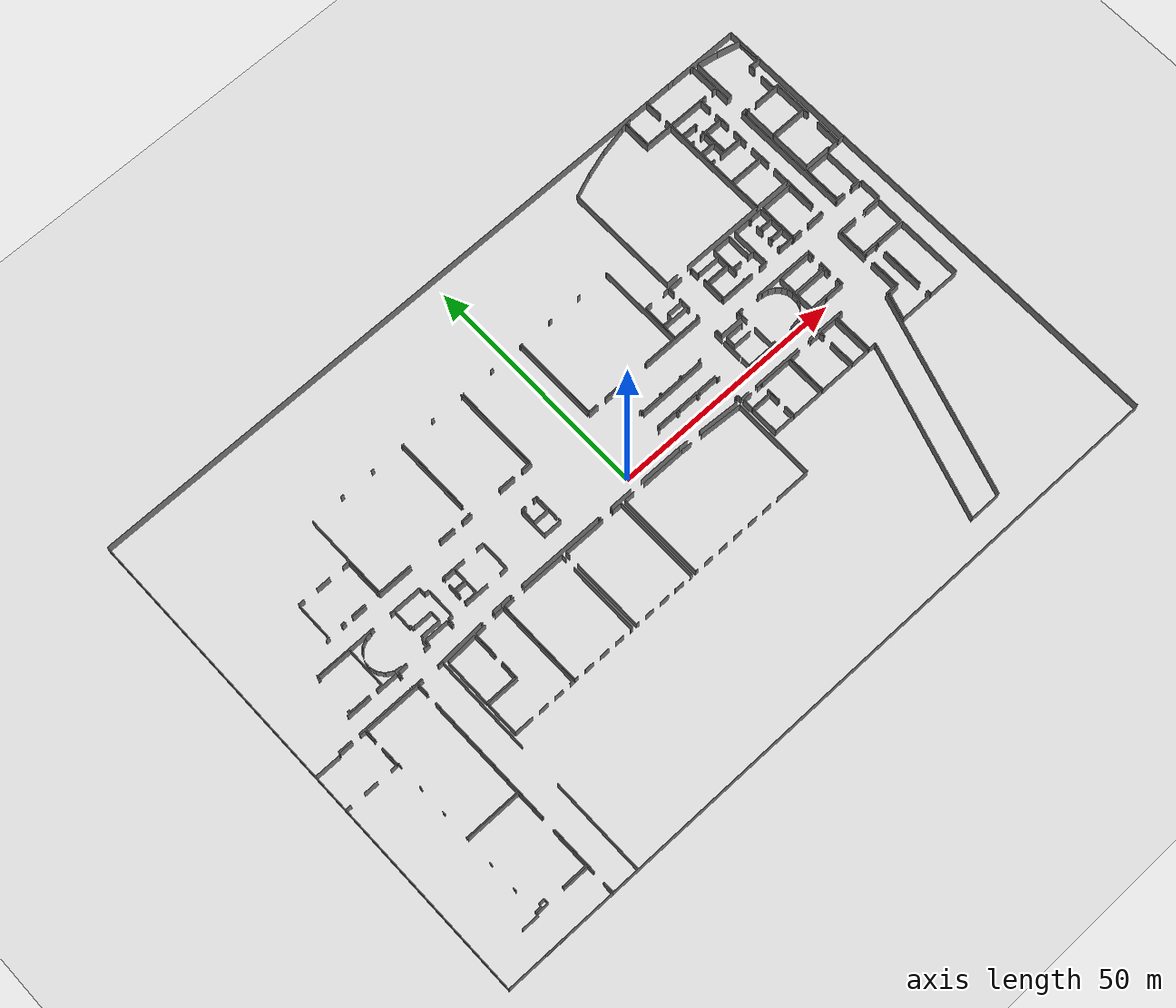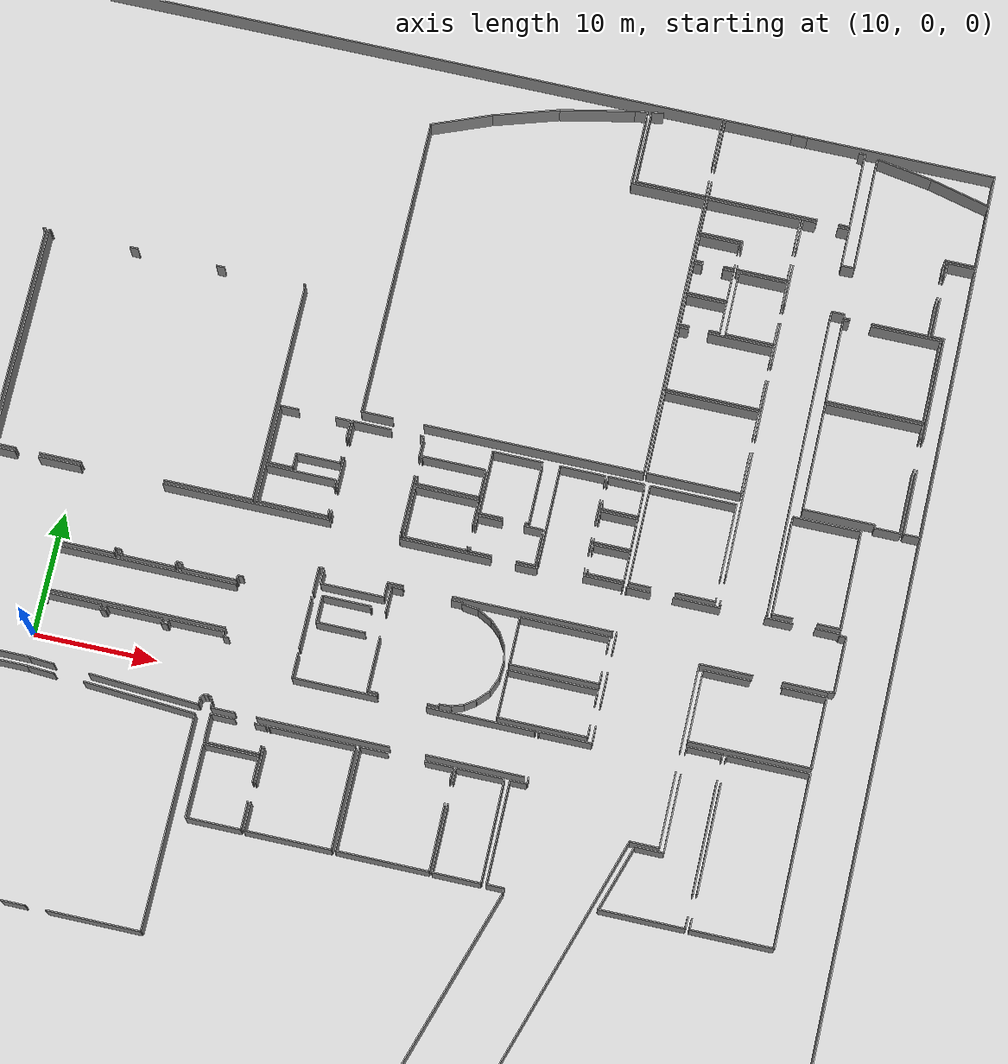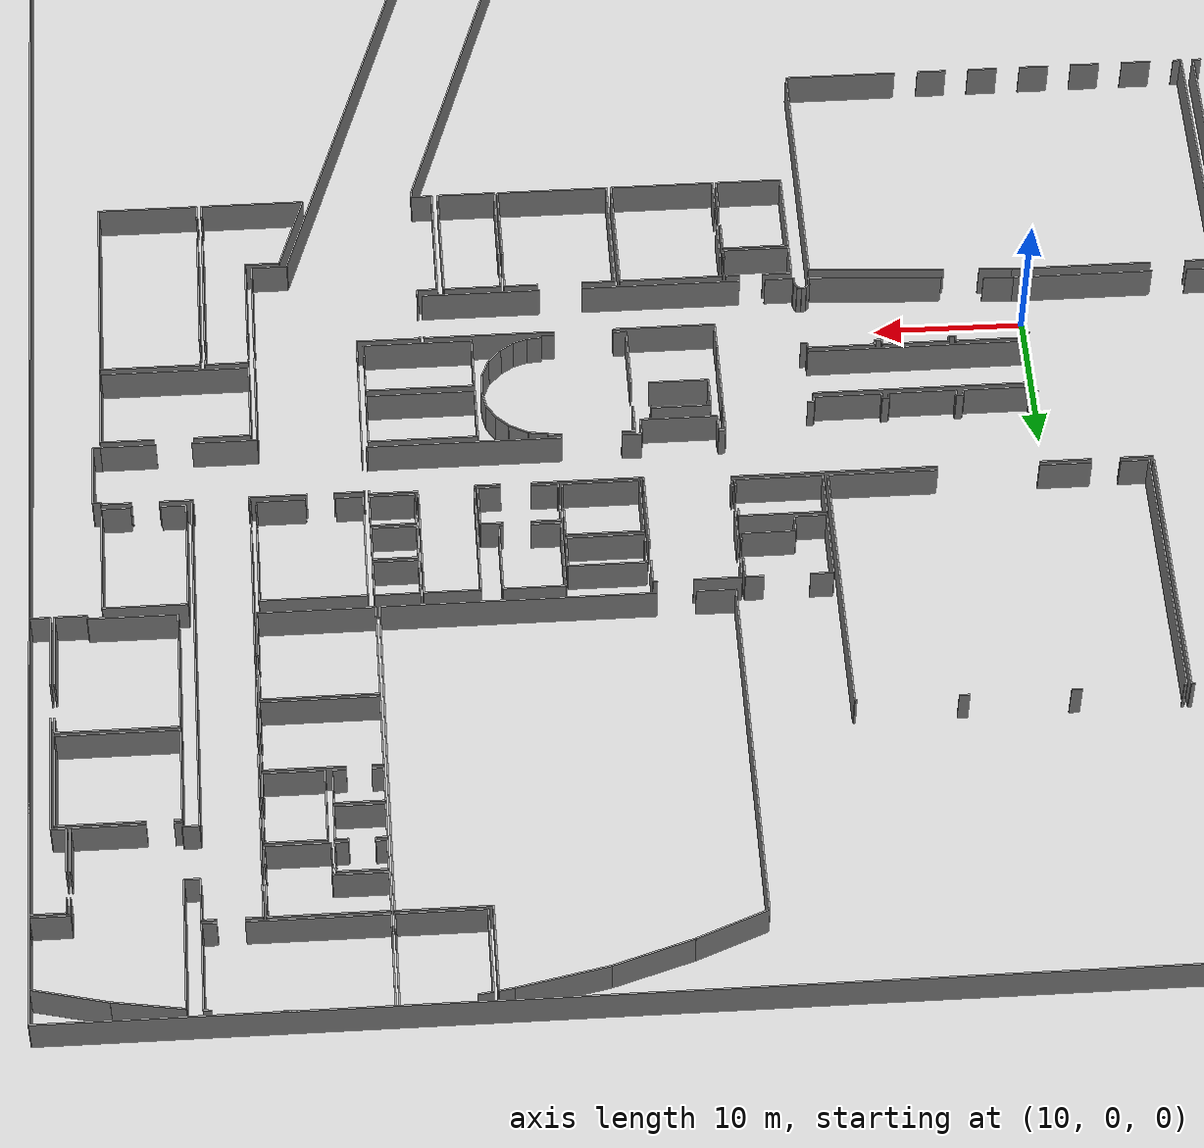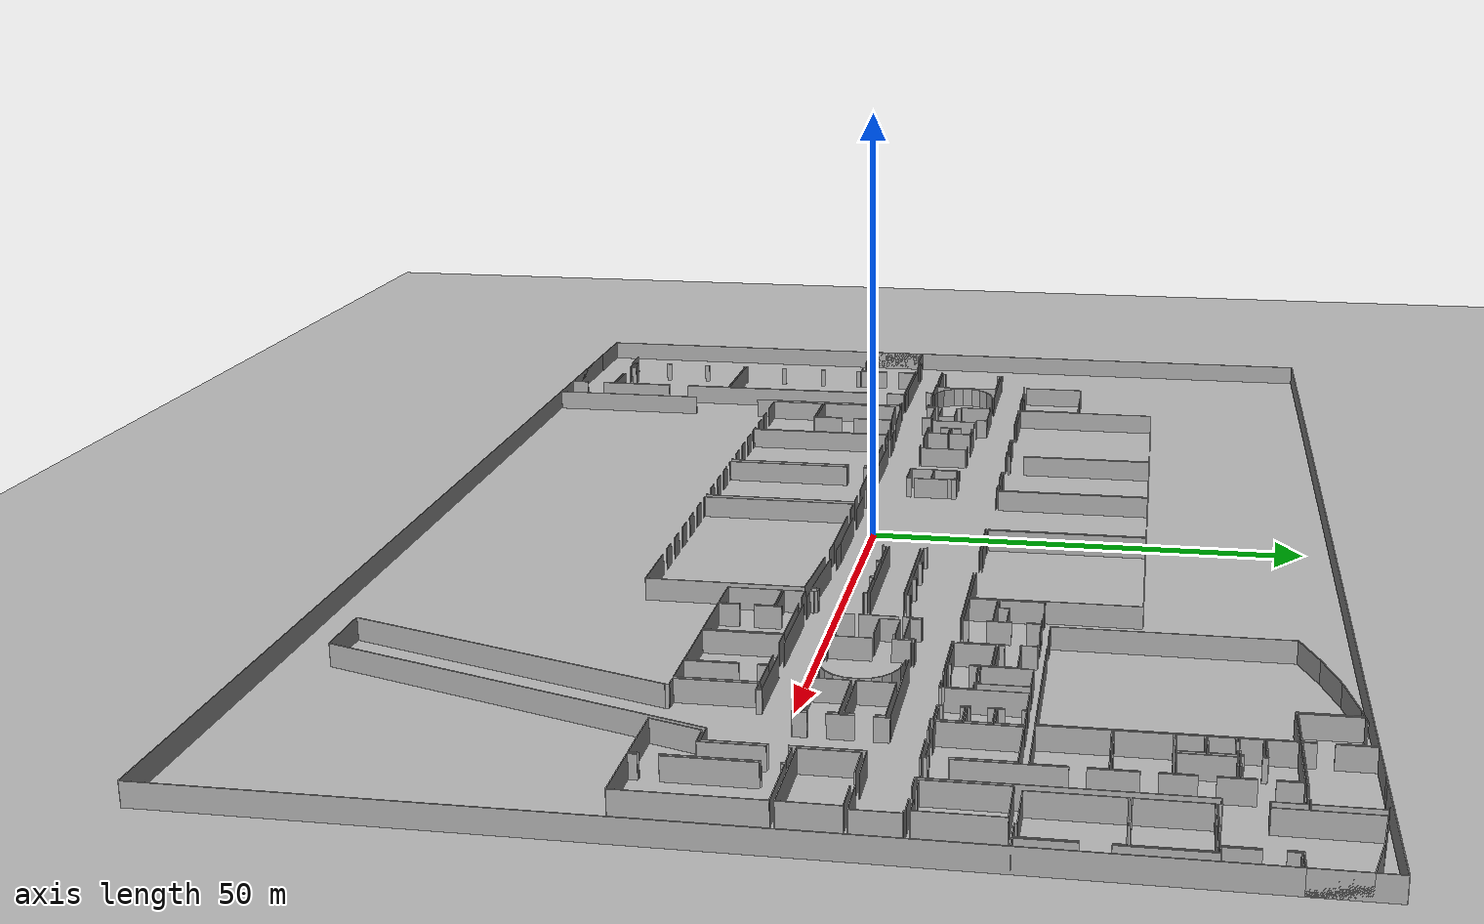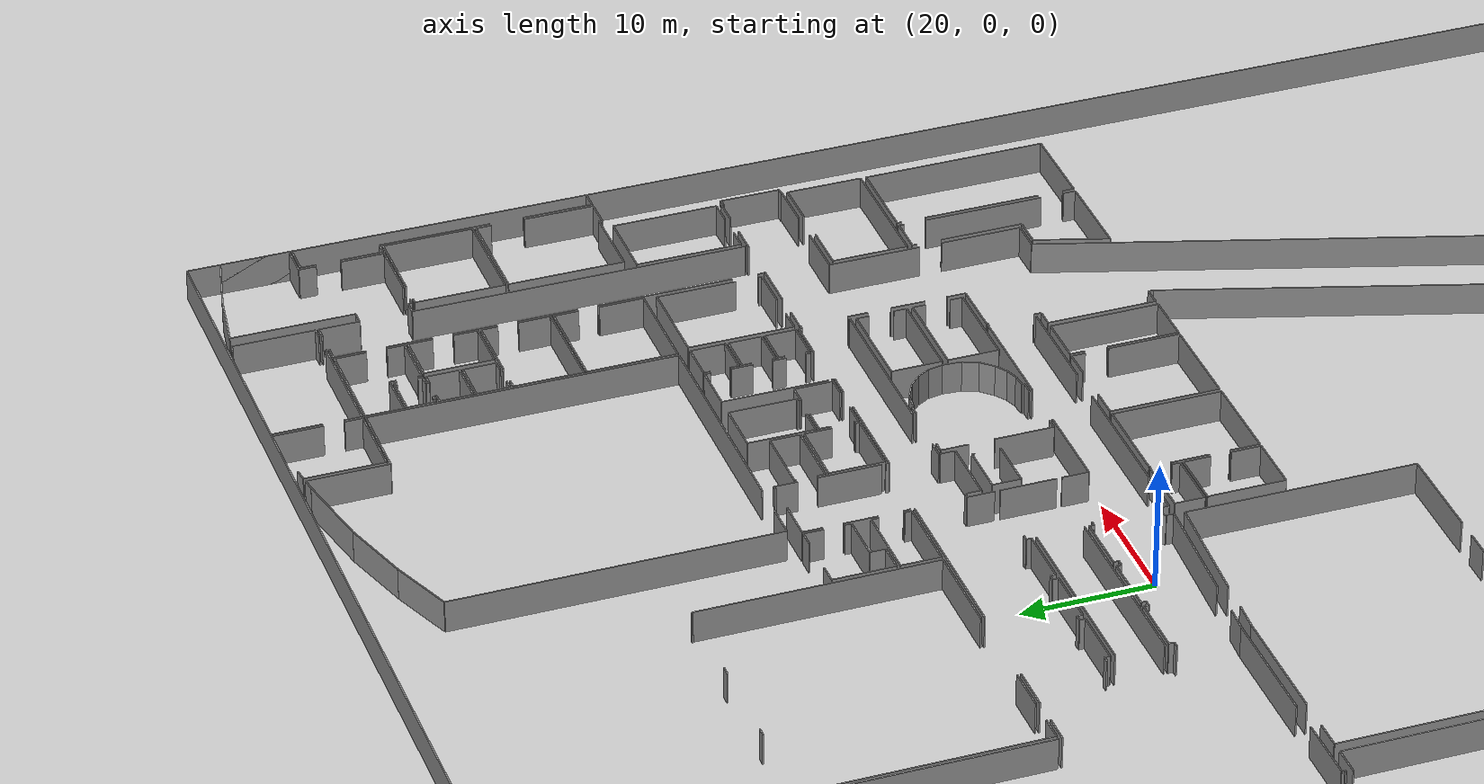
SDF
<sdf version="1.6">
  <world name="default">
    <light name="sun" type="directional">
      <cast_shadows>1</cast_shadows>
      <pose frame="">0 0 10 0 -0 0</pose>
      <diffuse>0.8 0.8 0.8 1</diffuse>
      <specular>0.1 0.1 0.1 1</specular>
      <attenuation>
        <range>1000</range>
        <constant>0.9</constant>
        <linear>0.01</linear>
        <quadratic>0.001</quadratic>
      </attenuation>
      <direction>-0.5 0.5 -1</direction>
    </light>
    <model name="ground_plane">
      <static>1</static>
      <link name="link">
        <collision name="collision">
          <geometry>
            <plane>
              <normal>0 0 1</normal>
              <size>100 100</size>
            </plane>
          </geometry>
          <surface>
            <friction>
              <ode>
                <mu>100</mu>
                <mu2>50</mu2>
              </ode>
              <torsional>
                <ode />
              </torsional>
            </friction>
            <contact>
              <ode />
            </contact>
            <bounce />
          </surface>
          <max_contacts>10</max_contacts>
        </collision>
        <visual name="visual">
          <cast_shadows>0</cast_shadows>
          <geometry>
            <plane>
              <normal>0 0 1</normal>
              <size>100 100</size>
            </plane>
          </geometry>
          <material>
            <script>
              <uri>file://media/materials/scripts/gazebo.material</uri>
              <name>Gazebo/Grey</name>
            </script>
          </material>
        </visual>
        <self_collide>0</self_collide>
        <kinematic>0</kinematic>
        <gravity>1</gravity>
      </link>
    </model>
    <gravity>0 0 -9.8</gravity>
    <magnetic_field>6e-06 2.3e-05 -4.2e-05</magnetic_field>
    <atmosphere type="adiabatic" />
    <physics default="0" name="default_physics" type="ode">
      <max_step_size>0.001</max_step_size>
      <real_time_factor>1</real_time_factor>
      <real_time_update_rate>1000</real_time_update_rate>
    </physics>
    <scene>
      <ambient>0.4 0.4 0.4 1</ambient>
      <background>0.7 0.7 0.7 1</background>
      <shadows>1</shadows>
    </scene>
    <spherical_coordinates>
      <surface_model>EARTH_WGS84</surface_model>
      <latitude_deg>0</latitude_deg>
      <longitude_deg>0</longitude_deg>
      <elevation>0</elevation>
      <heading_deg>0</heading_deg>
    </spherical_coordinates>
  <model name="0510032217_A-40">
		<static>1</static>
		<link name="Wall_0">
			<collision name="Wall_0_Collision">
				<geometry>
					<box>
						<size>0.0657293675769 0.1 2.5</size>
					</box>
				</geometry>
				<pose frame="">0.0328646837884 0 1.25 0 0 0</pose>
			</collision>
			<visual name="Wall_0_Visual">
				<pose frame="">0.0328646837884 0 1.25 0 0 0</pose>
				<geometry>
					<box>
						<size>0.0657293675769 0.1 2.5</size>
					</box>
				</geometry>
				<material>
					<script>
						<uri>file://media/materials/scripts/gazebo.material</uri>
						<name>Gazebo/Grey</name>
					</script>
					<ambient>1 1 1 1</ambient>
				</material>
			</visual>
			<pose frame="">11.9097680439 -43.4211247589 0 0 0 1.57079632679</pose>
		</link>
		<link name="Wall_1">
			<collision name="Wall_1_Collision">
				<geometry>
					<box>
						<size>0.166843862393 0.1 2.5</size>
					</box>
				</geometry>
				<pose frame="">0.0834219311964 0 1.25 0 0 0</pose>
			</collision>
			<visual name="Wall_1_Visual">
				<pose frame="">0.0834219311964 0 1.25 0 0 0</pose>
				<geometry>
					<box>
						<size>0.166843862393 0.1 2.5</size>
					</box>
				</geometry>
				<material>
					<script>
						<uri>file://media/materials/scripts/gazebo.material</uri>
						<name>Gazebo/Grey</name>
					</script>
					<ambient>1 1 1 1</ambient>
				</material>
			</visual>
			<pose frame="">11.9097680439 -43.3553953913 0 0 0 2.37932108175</pose>
		</link>
		<link name="Wall_2">
			<collision name="Wall_2_Collision">
				<geometry>
					<box>
						<size>0.0439041721653 0.1 2.5</size>
					</box>
				</geometry>
				<pose frame="">0.0219520860826 0 1.25 0 0 0</pose>
			</collision>
			<visual name="Wall_2_Visual">
				<pose frame="">0.0219520860826 0 1.25 0 0 0</pose>
				<geometry>
					<box>
						<size>0.0439041721653 0.1 2.5</size>
					</box>
				</geometry>
				<material>
					<script>
						<uri>file://media/materials/scripts/gazebo.material</uri>
						<name>Gazebo/Grey</name>
					</script>
					<ambient>1 1 1 1</ambient>
				</material>
			</visual>
			<pose frame="">17.1415972998 -39.4977921023 0 0 0 -1.57079632679</pose>
		</link>
		<link name="Wall_3">
			<collision name="Wall_3_Collision">
				<geometry>
					<box>
						<size>0.768449903563 0.1 2.5</size>
					</box>
				</geometry>
				<pose frame="">0.384224951782 0 1.25 0 0 0</pose>
			</collision>
			<visual name="Wall_3_Visual">
				<pose frame="">0.384224951782 0 1.25 0 0 0</pose>
				<geometry>
					<box>
						<size>0.768449903563 0.1 2.5</size>
					</box>
				</geometry>
				<material>
					<script>
						<uri>file://media/materials/scripts/gazebo.material</uri>
						<name>Gazebo/Grey</name>
					</script>
					<ambient>1 1 1 1</ambient>
				</material>
			</visual>
			<pose frame="">17.1415972998 -39.5416962745 0 0 0 0.0</pose>
		</link>
		<link name="Wall_4">
			<collision name="Wall_4_Collision">
				<geometry>
					<box>
						<size>0.0814638107806 0.1 2.5</size>
					</box>
				</geometry>
				<pose frame="">0.0407319053903 0 1.25 0 0 0</pose>
			</collision>
			<visual name="Wall_4_Visual">
				<pose frame="">0.0407319053903 0 1.25 0 0 0</pose>
				<geometry>
					<box>
						<size>0.0814638107806 0.1 2.5</size>
					</box>
				</geometry>
				<material>
					<script>
						<uri>file://media/materials/scripts/gazebo.material</uri>
						<name>Gazebo/Grey</name>
					</script>
					<ambient>1 1 1 1</ambient>
				</material>
			</visual>
			<pose frame="">17.9100472033 -39.5416962745 0 0 0 1.57079632679</pose>
		</link>
		<link name="Wall_5">
			<collision name="Wall_5_Collision">
				<geometry>
					<box>
						<size>0.89775149731 0.1 2.5</size>
					</box>
				</geometry>
				<pose frame="">0.448875748655 0 1.25 0 0 0</pose>
			</collision>
			<visual name="Wall_5_Visual">
				<pose frame="">0.448875748655 0 1.25 0 0 0</pose>
				<geometry>
					<box>
						<size>0.89775149731 0.1 2.5</size>
					</box>
				</geometry>
				<material>
					<script>
						<uri>file://media/materials/scripts/gazebo.material</uri>
						<name>Gazebo/Grey</name>
					</script>
					<ambient>1 1 1 1</ambient>
				</material>
			</visual>
			<pose frame="">20.8710410111 -39.4602324637 0 0 0 0.0</pose>
		</link>
		<link name="Wall_6">
			<collision name="Wall_6_Collision">
				<geometry>
					<box>
						<size>3.11199370622 0.1 2.5</size>
					</box>
				</geometry>
				<pose frame="">1.55599685311 0 1.25 0 0 0</pose>
			</collision>
			<visual name="Wall_6_Visual">
				<pose frame="">1.55599685311 0 1.25 0 0 0</pose>
				<geometry>
					<box>
						<size>3.11199370622 0.1 2.5</size>
					</box>
				</geometry>
				<material>
					<script>
						<uri>file://media/materials/scripts/gazebo.material</uri>
						<name>Gazebo/Grey</name>
					</script>
					<ambient>1 1 1 1</ambient>
				</material>
			</visual>
			<pose frame="">23.3069612222 -39.4602324637 0 0 0 0.0</pose>
		</link>
		<link name="Wall_7">
			<collision name="Wall_7_Collision">
				<geometry>
					<box>
						<size>7.48045883667 0.1 2.5</size>
					</box>
				</geometry>
				<pose frame="">3.74022941833 0 1.25 0 0 0</pose>
			</collision>
			<visual name="Wall_7_Visual">
				<pose frame="">3.74022941833 0 1.25 0 0 0</pose>
				<geometry>
					<box>
						<size>7.48045883667 0.1 2.5</size>
					</box>
				</geometry>
				<material>
					<script>
						<uri>file://media/materials/scripts/gazebo.material</uri>
						<name>Gazebo/Grey</name>
					</script>
					<ambient>1 1 1 1</ambient>
				</material>
			</visual>
			<pose frame="">29.5008755456 -39.4602324637 0 0 0 0.0</pose>
		</link>
		<link name="Wall_8">
			<collision name="Wall_8_Collision">
				<geometry>
					<box>
						<size>3.43188508781 0.1 2.5</size>
					</box>
				</geometry>
				<pose frame="">1.7159425439 0 1.25 0 0 0</pose>
			</collision>
			<visual name="Wall_8_Visual">
				<pose frame="">1.7159425439 0 1.25 0 0 0</pose>
				<geometry>
					<box>
						<size>3.43188508781 0.1 2.5</size>
					</box>
				</geometry>
				<material>
					<script>
						<uri>file://media/materials/scripts/gazebo.material</uri>
						<name>Gazebo/Grey</name>
					</script>
					<ambient>1 1 1 1</ambient>
				</material>
			</visual>
			<pose frame="">43.8326692722 -39.4602324637 0 0 0 0.0</pose>
		</link>
		<link name="Wall_9">
			<collision name="Wall_9_Collision">
				<geometry>
					<box>
						<size>2.17427164755 0.1 2.5</size>
					</box>
				</geometry>
				<pose frame="">1.08713582377 0 1.25 0 0 0</pose>
			</collision>
			<visual name="Wall_9_Visual">
				<pose frame="">1.08713582377 0 1.25 0 0 0</pose>
				<geometry>
					<box>
						<size>2.17427164755 0.1 2.5</size>
					</box>
				</geometry>
				<material>
					<script>
						<uri>file://media/materials/scripts/gazebo.material</uri>
						<name>Gazebo/Grey</name>
					</script>
					<ambient>1 1 1 1</ambient>
				</material>
			</visual>
			<pose frame="">49.1814917267 -39.4602324637 0 0 0 0.0</pose>
		</link>
		<link name="Wall_10">
			<collision name="Wall_10_Collision">
				<geometry>
					<box>
						<size>3.46969850777 0.1 2.5</size>
					</box>
				</geometry>
				<pose frame="">1.73484925388 0 1.25 0 0 0</pose>
			</collision>
			<visual name="Wall_10_Visual">
				<pose frame="">1.73484925388 0 1.25 0 0 0</pose>
				<geometry>
					<box>
						<size>3.46969850777 0.1 2.5</size>
					</box>
				</geometry>
				<material>
					<script>
						<uri>file://media/materials/scripts/gazebo.material</uri>
						<name>Gazebo/Grey</name>
					</script>
					<ambient>1 1 1 1</ambient>
				</material>
			</visual>
			<pose frame="">58.1786747538 -39.4602324637 0 0 0 0.0</pose>
		</link>
		<link name="Wall_11">
			<collision name="Wall_11_Collision">
				<geometry>
					<box>
						<size>2.21639935032 0.1 2.5</size>
					</box>
				</geometry>
				<pose frame="">1.10819967516 0 1.25 0 0 0</pose>
			</collision>
			<visual name="Wall_11_Visual">
				<pose frame="">1.10819967516 0 1.25 0 0 0</pose>
				<geometry>
					<box>
						<size>2.21639935032 0.1 2.5</size>
					</box>
				</geometry>
				<material>
					<script>
						<uri>file://media/materials/scripts/gazebo.material</uri>
						<name>Gazebo/Grey</name>
					</script>
					<ambient>1 1 1 1</ambient>
				</material>
			</visual>
			<pose frame="">63.5373946807 -39.4602324637 0 0 0 0.0</pose>
		</link>
		<link name="Wall_12">
			<collision name="Wall_12_Collision">
				<geometry>
					<box>
						<size>2.18010861841 0.1 2.5</size>
					</box>
				</geometry>
				<pose frame="">1.09005430921 0 1.25 0 0 0</pose>
			</collision>
			<visual name="Wall_12_Visual">
				<pose frame="">1.09005430921 0 1.25 0 0 0</pose>
				<geometry>
					<box>
						<size>2.18010861841 0.1 2.5</size>
					</box>
				</geometry>
				<material>
					<script>
						<uri>file://media/materials/scripts/gazebo.material</uri>
						<name>Gazebo/Grey</name>
					</script>
					<ambient>1 1 1 1</ambient>
				</material>
			</visual>
			<pose frame="">79.8513475789 -39.4602324637 0 0 0 0.0</pose>
		</link>
		<link name="Wall_13">
			<collision name="Wall_13_Collision">
				<geometry>
					<box>
						<size>3.42820525835 0.1 2.5</size>
					</box>
				</geometry>
				<pose frame="">1.71410262917 0 1.25 0 0 0</pose>
			</collision>
			<visual name="Wall_13_Visual">
				<pose frame="">1.71410262917 0 1.25 0 0 0</pose>
				<geometry>
					<box>
						<size>3.42820525835 0.1 2.5</size>
					</box>
				</geometry>
				<material>
					<script>
						<uri>file://media/materials/scripts/gazebo.material</uri>
						<name>Gazebo/Grey</name>
					</script>
					<ambient>1 1 1 1</ambient>
				</material>
			</visual>
			<pose frame="">83.9263145874 -39.4602324637 0 0 0 0.0</pose>
		</link>
		<link name="Wall_14">
			<collision name="Wall_14_Collision">
				<geometry>
					<box>
						<size>13.5959547254 0.1 2.5</size>
					</box>
				</geometry>
				<pose frame="">6.7979773627 0 1.25 0 0 0</pose>
			</collision>
			<visual name="Wall_14_Visual">
				<pose frame="">6.7979773627 0 1.25 0 0 0</pose>
				<geometry>
					<box>
						<size>13.5959547254 0.1 2.5</size>
					</box>
				</geometry>
				<material>
					<script>
						<uri>file://media/materials/scripts/gazebo.material</uri>
						<name>Gazebo/Grey</name>
					</script>
					<ambient>1 1 1 1</ambient>
				</material>
			</visual>
			<pose frame="">94.1161430312 -39.4602324637 0 0 0 0.0</pose>
		</link>
		<link name="Wall_15">
			<collision name="Wall_15_Collision">
				<geometry>
					<box>
						<size>0.261014110243 0.1 2.5</size>
					</box>
				</geometry>
				<pose frame="">0.130507055121 0 1.25 0 0 0</pose>
			</collision>
			<visual name="Wall_15_Visual">
				<pose frame="">0.130507055121 0 1.25 0 0 0</pose>
				<geometry>
					<box>
						<size>0.261014110243 0.1 2.5</size>
					</box>
				</geometry>
				<material>
					<script>
						<uri>file://media/materials/scripts/gazebo.material</uri>
						<name>Gazebo/Grey</name>
					</script>
					<ambient>1 1 1 1</ambient>
				</material>
			</visual>
			<pose frame="">113.443495584 -39.4602324637 0 0 0 -1.57079632679</pose>
		</link>
		<link name="Wall_16">
			<collision name="Wall_16_Collision">
				<geometry>
					<box>
						<size>7.40901938889 0.1 2.5</size>
					</box>
				</geometry>
				<pose frame="">3.70450969445 0 1.25 0 0 0</pose>
			</collision>
			<visual name="Wall_16_Visual">
				<pose frame="">3.70450969445 0 1.25 0 0 0</pose>
				<geometry>
					<box>
						<size>7.40901938889 0.1 2.5</size>
					</box>
				</geometry>
				<material>
					<script>
						<uri>file://media/materials/scripts/gazebo.material</uri>
						<name>Gazebo/Grey</name>
					</script>
					<ambient>1 1 1 1</ambient>
				</material>
			</visual>
			<pose frame="">113.443495584 -39.721246574 0 0 0 0.0</pose>
		</link>
		<link name="Wall_17">
			<collision name="Wall_17_Collision">
				<geometry>
					<box>
						<size>1.70160389808 0.1 2.5</size>
					</box>
				</geometry>
				<pose frame="">0.850801949041 0 1.25 0 0 0</pose>
			</collision>
			<visual name="Wall_17_Visual">
				<pose frame="">0.850801949041 0 1.25 0 0 0</pose>
				<geometry>
					<box>
						<size>1.70160389808 0.1 2.5</size>
					</box>
				</geometry>
				<material>
					<script>
						<uri>file://media/materials/scripts/gazebo.material</uri>
						<name>Gazebo/Grey</name>
					</script>
					<ambient>1 1 1 1</ambient>
				</material>
			</visual>
			<pose frame="">122.838353974 -39.721246574 0 0 0 0.0</pose>
		</link>
		<link name="Wall_18">
			<collision name="Wall_18_Collision">
				<geometry>
					<box>
						<size>0.251877981931 0.1 2.5</size>
					</box>
				</geometry>
				<pose frame="">0.125938990965 0 1.25 0 0 0</pose>
			</collision>
			<visual name="Wall_18_Visual">
				<pose frame="">0.125938990965 0 1.25 0 0 0</pose>
				<geometry>
					<box>
						<size>0.251877981931 0.1 2.5</size>
					</box>
				</geometry>
				<material>
					<script>
						<uri>file://media/materials/scripts/gazebo.material</uri>
						<name>Gazebo/Grey</name>
					</script>
					<ambient>1 1 1 1</ambient>
				</material>
			</visual>
			<pose frame="">124.539957872 -39.721246574 0 0 0 1.57079632679</pose>
		</link>
		<link name="Wall_19">
			<collision name="Wall_19_Collision">
				<geometry>
					<box>
						<size>3.22175413664 0.1 2.5</size>
					</box>
				</geometry>
				<pose frame="">1.61087706832 0 1.25 0 0 0</pose>
			</collision>
			<visual name="Wall_19_Visual">
				<pose frame="">1.61087706832 0 1.25 0 0 0</pose>
				<geometry>
					<box>
						<size>3.22175413664 0.1 2.5</size>
					</box>
				</geometry>
				<material>
					<script>
						<uri>file://media/materials/scripts/gazebo.material</uri>
						<name>Gazebo/Grey</name>
					</script>
					<ambient>1 1 1 1</ambient>
				</material>
			</visual>
			<pose frame="">128.242627652 -39.469368592 0 0 0 0.0</pose>
		</link>
		<link name="Wall_20">
			<collision name="Wall_20_Collision">
				<geometry>
					<box>
						<size>0.282077961628 0.1 2.5</size>
					</box>
				</geometry>
				<pose frame="">0.141038980814 0 1.25 0 0 0</pose>
			</collision>
			<visual name="Wall_20_Visual">
				<pose frame="">0.141038980814 0 1.25 0 0 0</pose>
				<geometry>
					<box>
						<size>0.282077961628 0.1 2.5</size>
					</box>
				</geometry>
				<material>
					<script>
						<uri>file://media/materials/scripts/gazebo.material</uri>
						<name>Gazebo/Grey</name>
					</script>
					<ambient>1 1 1 1</ambient>
				</material>
			</visual>
			<pose frame="">131.464381789 -39.469368592 0 0 0 -1.57079632679</pose>
		</link>
		<link name="Wall_21">
			<collision name="Wall_21_Collision">
				<geometry>
					<box>
						<size>0.0946604405644 0.1 2.5</size>
					</box>
				</geometry>
				<pose frame="">0.0473302202822 0 1.25 0 0 0</pose>
			</collision>
			<visual name="Wall_21_Visual">
				<pose frame="">0.0473302202822 0 1.25 0 0 0</pose>
				<geometry>
					<box>
						<size>0.0946604405644 0.1 2.5</size>
					</box>
				</geometry>
				<material>
					<script>
						<uri>file://media/materials/scripts/gazebo.material</uri>
						<name>Gazebo/Grey</name>
					</script>
					<ambient>1 1 1 1</ambient>
				</material>
			</visual>
			<pose frame="">131.464381789 -43.2985483707 0 0 0 -1.57079632679</pose>
		</link>
		<link name="Wall_22">
			<collision name="Wall_22_Collision">
				<geometry>
					<box>
						<size>12.9276215613 0.1 2.5</size>
					</box>
				</geometry>
				<pose frame="">6.46381078063 0 1.25 0 0 0</pose>
			</collision>
			<visual name="Wall_22_Visual">
				<pose frame="">6.46381078063 0 1.25 0 0 0</pose>
				<geometry>
					<box>
						<size>12.9276215613 0.1 2.5</size>
					</box>
				</geometry>
				<material>
					<script>
						<uri>file://media/materials/scripts/gazebo.material</uri>
						<name>Gazebo/Grey</name>
					</script>
					<ambient>1 1 1 1</ambient>
				</material>
			</visual>
			<pose frame="">131.464381789 -43.3932088113 0 0 0 3.14159265359</pose>
		</link>
		<link name="Wall_23">
			<collision name="Wall_23_Collision">
				<geometry>
					<box>
						<size>1.30595878591 0.1 2.5</size>
					</box>
				</geometry>
				<pose frame="">0.652979392955 0 1.25 0 0 0</pose>
			</collision>
			<visual name="Wall_23_Visual">
				<pose frame="">0.652979392955 0 1.25 0 0 0</pose>
				<geometry>
					<box>
						<size>1.30595878591 0.1 2.5</size>
					</box>
				</geometry>
				<material>
					<script>
						<uri>file://media/materials/scripts/gazebo.material</uri>
						<name>Gazebo/Grey</name>
					</script>
					<ambient>1 1 1 1</ambient>
				</material>
			</visual>
			<pose frame="">114.604418333 -43.3932088113 0 0 0 3.14159265359</pose>
		</link>
		<link name="Wall_24">
			<collision name="Wall_24_Collision">
				<geometry>
					<box>
						<size>0.433458532129 0.1 2.5</size>
					</box>
				</geometry>
				<pose frame="">0.216729266064 0 1.25 0 0 0</pose>
			</collision>
			<visual name="Wall_24_Visual">
				<pose frame="">0.216729266064 0 1.25 0 0 0</pose>
				<geometry>
					<box>
						<size>0.433458532129 0.1 2.5</size>
					</box>
				</geometry>
				<material>
					<script>
						<uri>file://media/materials/scripts/gazebo.material</uri>
						<name>Gazebo/Grey</name>
					</script>
					<ambient>1 1 1 1</ambient>
				</material>
			</visual>
			<pose frame="">108.186161303 -43.3932088113 0 0 0 3.14159265359</pose>
		</link>
		<link name="Wall_25">
			<collision name="Wall_25_Collision">
				<geometry>
					<box>
						<size>2.03050451731 0.1 2.5</size>
					</box>
				</geometry>
				<pose frame="">1.01525225865 0 1.25 0 0 0</pose>
			</collision>
			<visual name="Wall_25_Visual">
				<pose frame="">1.01525225865 0 1.25 0 0 0</pose>
				<geometry>
					<box>
						<size>2.03050451731 0.1 2.5</size>
					</box>
				</geometry>
				<material>
					<script>
						<uri>file://media/materials/scripts/gazebo.material</uri>
						<name>Gazebo/Grey</name>
					</script>
					<ambient>1 1 1 1</ambient>
				</material>
			</visual>
			<pose frame="">107.752702771 -43.3932088113 0 0 0 -1.57079632679</pose>
		</link>
		<link name="Wall_26">
			<collision name="Wall_26_Collision">
				<geometry>
					<box>
						<size>0.450588772713 0.1 2.5</size>
					</box>
				</geometry>
				<pose frame="">0.225294386357 0 1.25 0 0 0</pose>
			</collision>
			<visual name="Wall_26_Visual">
				<pose frame="">0.225294386357 0 1.25 0 0 0</pose>
				<geometry>
					<box>
						<size>0.450588772713 0.1 2.5</size>
					</box>
				</geometry>
				<material>
					<script>
						<uri>file://media/materials/scripts/gazebo.material</uri>
						<name>Gazebo/Grey</name>
					</script>
					<ambient>1 1 1 1</ambient>
				</material>
			</visual>
			<pose frame="">102.113808243 -45.4237133286 0 0 0 3.14159265359</pose>
		</link>
		<link name="Wall_27">
			<collision name="Wall_27_Collision">
				<geometry>
					<box>
						<size>0.38917368795 0.1 2.5</size>
					</box>
				</geometry>
				<pose frame="">0.194586843975 0 1.25 0 0 0</pose>
			</collision>
			<visual name="Wall_27_Visual">
				<pose frame="">0.194586843975 0 1.25 0 0 0</pose>
				<geometry>
					<box>
						<size>0.38917368795 0.1 2.5</size>
					</box>
				</geometry>
				<material>
					<script>
						<uri>file://media/materials/scripts/gazebo.material</uri>
						<name>Gazebo/Grey</name>
					</script>
					<ambient>1 1 1 1</ambient>
				</material>
			</visual>
			<pose frame="">101.66321947 -45.4237133286 0 0 0 -1.57079632679</pose>
		</link>
		<link name="Wall_28">
			<collision name="Wall_28_Collision">
				<geometry>
					<box>
						<size>4.52200284235 0.1 2.5</size>
					</box>
				</geometry>
				<pose frame="">2.26100142118 0 1.25 0 0 0</pose>
			</collision>
			<visual name="Wall_28_Visual">
				<pose frame="">2.26100142118 0 1.25 0 0 0</pose>
				<geometry>
					<box>
						<size>4.52200284235 0.1 2.5</size>
					</box>
				</geometry>
				<material>
					<script>
						<uri>file://media/materials/scripts/gazebo.material</uri>
						<name>Gazebo/Grey</name>
					</script>
					<ambient>1 1 1 1</ambient>
				</material>
			</visual>
			<pose frame="">101.66321947 -45.8128870165 0 0 0 3.14159265359</pose>
		</link>
		<link name="Wall_29">
			<collision name="Wall_29_Collision">
				<geometry>
					<box>
						<size>0.408841741955 0.1 2.5</size>
					</box>
				</geometry>
				<pose frame="">0.204420870978 0 1.25 0 0 0</pose>
			</collision>
			<visual name="Wall_29_Visual">
				<pose frame="">0.204420870978 0 1.25 0 0 0</pose>
				<geometry>
					<box>
						<size>0.408841741955 0.1 2.5</size>
					</box>
				</geometry>
				<material>
					<script>
						<uri>file://media/materials/scripts/gazebo.material</uri>
						<name>Gazebo/Grey</name>
					</script>
					<ambient>1 1 1 1</ambient>
				</material>
			</visual>
			<pose frame="">97.1412166278 -45.8128870165 0 0 0 1.57079632679</pose>
		</link>
		<link name="Wall_30">
			<collision name="Wall_30_Collision">
				<geometry>
					<box>
						<size>0.458963556999 0.1 2.5</size>
					</box>
				</geometry>
				<pose frame="">0.2294817785 0 1.25 0 0 0</pose>
			</collision>
			<visual name="Wall_30_Visual">
				<pose frame="">0.2294817785 0 1.25 0 0 0</pose>
				<geometry>
					<box>
						<size>0.458963556999 0.1 2.5</size>
					</box>
				</geometry>
				<material>
					<script>
						<uri>file://media/materials/scripts/gazebo.material</uri>
						<name>Gazebo/Grey</name>
					</script>
					<ambient>1 1 1 1</ambient>
				</material>
			</visual>
			<pose frame="">97.1412166278 -45.4040452746 0 0 0 3.14159265359</pose>
		</link>
		<link name="Wall_31">
			<collision name="Wall_31_Collision">
				<geometry>
					<box>
						<size>0.425591310527 0.1 2.5</size>
					</box>
				</geometry>
				<pose frame="">0.212795655263 0 1.25 0 0 0</pose>
			</collision>
			<visual name="Wall_31_Visual">
				<pose frame="">0.212795655263 0 1.25 0 0 0</pose>
				<geometry>
					<box>
						<size>0.425591310527 0.1 2.5</size>
					</box>
				</geometry>
				<material>
					<script>
						<uri>file://media/materials/scripts/gazebo.material</uri>
						<name>Gazebo/Grey</name>
					</script>
					<ambient>1 1 1 1</ambient>
				</material>
			</visual>
			<pose frame="">96.6822530708 -45.4040452746 0 0 0 -1.57079632679</pose>
		</link>
		<link name="Wall_32">
			<collision name="Wall_32_Collision">
				<geometry>
					<box>
						<size>4.48736168917 0.1 2.5</size>
					</box>
				</geometry>
				<pose frame="">2.24368084458 0 1.25 0 0 0</pose>
			</collision>
			<visual name="Wall_32_Visual">
				<pose frame="">2.24368084458 0 1.25 0 0 0</pose>
				<geometry>
					<box>
						<size>4.48736168917 0.1 2.5</size>
					</box>
				</geometry>
				<material>
					<script>
						<uri>file://media/materials/scripts/gazebo.material</uri>
						<name>Gazebo/Grey</name>
					</script>
					<ambient>1 1 1 1</ambient>
				</material>
			</visual>
			<pose frame="">96.6822530708 -45.8296365851 0 0 0 3.14159265359</pose>
		</link>
		<link name="Wall_33">
			<collision name="Wall_33_Collision">
				<geometry>
					<box>
						<size>0.4335854228 0.1 2.5</size>
					</box>
				</geometry>
				<pose frame="">0.2167927114 0 1.25 0 0 0</pose>
			</collision>
			<visual name="Wall_33_Visual">
				<pose frame="">0.2167927114 0 1.25 0 0 0</pose>
				<geometry>
					<box>
						<size>0.4335854228 0.1 2.5</size>
					</box>
				</geometry>
				<material>
					<script>
						<uri>file://media/materials/scripts/gazebo.material</uri>
						<name>Gazebo/Grey</name>
					</script>
					<ambient>1 1 1 1</ambient>
				</material>
			</visual>
			<pose frame="">92.1948913816 -45.8296365851 0 0 0 1.57079632679</pose>
		</link>
		<link name="Wall_34">
			<collision name="Wall_34_Collision">
				<geometry>
					<box>
						<size>0.47177951477 0.1 2.5</size>
					</box>
				</geometry>
				<pose frame="">0.235889757385 0 1.25 0 0 0</pose>
			</collision>
			<visual name="Wall_34_Visual">
				<pose frame="">0.235889757385 0 1.25 0 0 0</pose>
				<geometry>
					<box>
						<size>0.47177951477 0.1 2.5</size>
					</box>
				</geometry>
				<material>
					<script>
						<uri>file://media/materials/scripts/gazebo.material</uri>
						<name>Gazebo/Grey</name>
					</script>
					<ambient>1 1 1 1</ambient>
				</material>
			</visual>
			<pose frame="">92.1948913816 -45.3960511623 0 0 0 3.14159265359</pose>
		</link>
		<link name="Wall_35">
			<collision name="Wall_35_Collision">
				<geometry>
					<box>
						<size>0.411506446046 0.1 2.5</size>
					</box>
				</geometry>
				<pose frame="">0.205753223023 0 1.25 0 0 0</pose>
			</collision>
			<visual name="Wall_35_Visual">
				<pose frame="">0.205753223023 0 1.25 0 0 0</pose>
				<geometry>
					<box>
						<size>0.411506446046 0.1 2.5</size>
					</box>
				</geometry>
				<material>
					<script>
						<uri>file://media/materials/scripts/gazebo.material</uri>
						<name>Gazebo/Grey</name>
					</script>
					<ambient>1 1 1 1</ambient>
				</material>
			</visual>
			<pose frame="">91.7231118668 -45.3960511623 0 0 0 -1.57079632679</pose>
		</link>
		<link name="Wall_36">
			<collision name="Wall_36_Collision">
				<geometry>
					<box>
						<size>4.50931377525 0.1 2.5</size>
					</box>
				</geometry>
				<pose frame="">2.25465688763 0 1.25 0 0 0</pose>
			</collision>
			<visual name="Wall_36_Visual">
				<pose frame="">2.25465688763 0 1.25 0 0 0</pose>
				<geometry>
					<box>
						<size>4.50931377525 0.1 2.5</size>
					</box>
				</geometry>
				<material>
					<script>
						<uri>file://media/materials/scripts/gazebo.material</uri>
						<name>Gazebo/Grey</name>
					</script>
					<ambient>1 1 1 1</ambient>
				</material>
			</visual>
			<pose frame="">91.7231118668 -45.8075576084 0 0 0 3.14159265359</pose>
		</link>
		<link name="Wall_37">
			<collision name="Wall_37_Collision">
				<geometry>
					<box>
						<size>0.400466957669 0.1 2.5</size>
					</box>
				</geometry>
				<pose frame="">0.200233478835 0 1.25 0 0 0</pose>
			</collision>
			<visual name="Wall_37_Visual">
				<pose frame="">0.200233478835 0 1.25 0 0 0</pose>
				<geometry>
					<box>
						<size>0.400466957669 0.1 2.5</size>
					</box>
				</geometry>
				<material>
					<script>
						<uri>file://media/materials/scripts/gazebo.material</uri>
						<name>Gazebo/Grey</name>
					</script>
					<ambient>1 1 1 1</ambient>
				</material>
			</visual>
			<pose frame="">87.2137980916 -45.8075576084 0 0 0 1.57079632679</pose>
		</link>
		<link name="Wall_38">
			<collision name="Wall_38_Collision">
				<geometry>
					<box>
						<size>0.460866917064 0.1 2.5</size>
					</box>
				</geometry>
				<pose frame="">0.230433458532 0 1.25 0 0 0</pose>
			</collision>
			<visual name="Wall_38_Visual">
				<pose frame="">0.230433458532 0 1.25 0 0 0</pose>
				<geometry>
					<box>
						<size>0.460866917064 0.1 2.5</size>
					</box>
				</geometry>
				<material>
					<script>
						<uri>file://media/materials/scripts/gazebo.material</uri>
						<name>Gazebo/Grey</name>
					</script>
					<ambient>1 1 1 1</ambient>
				</material>
			</visual>
			<pose frame="">87.2137980916 -45.4070906507 0 0 0 3.14159265359</pose>
		</link>
		<link name="Wall_39">
			<collision name="Wall_39_Collision">
				<geometry>
					<box>
						<size>0.600065983149 0.1 2.5</size>
					</box>
				</geometry>
				<pose frame="">0.300032991574 0 1.25 0 0 0</pose>
			</collision>
			<visual name="Wall_39_Visual">
				<pose frame="">0.300032991574 0 1.25 0 0 0</pose>
				<geometry>
					<box>
						<size>0.600065983149 0.1 2.5</size>
					</box>
				</geometry>
				<material>
					<script>
						<uri>file://media/materials/scripts/gazebo.material</uri>
						<name>Gazebo/Grey</name>
					</script>
					<ambient>1 1 1 1</ambient>
				</material>
			</visual>
			<pose frame="">62.2229342199 -45.4070906507 0 0 0 1.57079632679</pose>
		</link>
		<link name="Wall_40">
			<collision name="Wall_40_Collision">
				<geometry>
					<box>
						<size>1.02273880824 0.1 2.5</size>
					</box>
				</geometry>
				<pose frame="">0.511369404121 0 1.25 0 0 0</pose>
			</collision>
			<visual name="Wall_40_Visual">
				<pose frame="">0.511369404121 0 1.25 0 0 0</pose>
				<geometry>
					<box>
						<size>1.02273880824 0.1 2.5</size>
					</box>
				</geometry>
				<material>
					<script>
						<uri>file://media/materials/scripts/gazebo.material</uri>
						<name>Gazebo/Grey</name>
					</script>
					<ambient>1 1 1 1</ambient>
				</material>
			</visual>
			<pose frame="">62.2229342199 -44.8070246675 0 0 0 3.14159265359</pose>
		</link>
		<link name="Wall_41">
			<collision name="Wall_41_Collision">
				<geometry>
					<box>
						<size>1.06854634047 0.1 2.5</size>
					</box>
				</geometry>
				<pose frame="">0.534273170237 0 1.25 0 0 0</pose>
			</collision>
			<visual name="Wall_41_Visual">
				<pose frame="">0.534273170237 0 1.25 0 0 0</pose>
				<geometry>
					<box>
						<size>1.06854634047 0.1 2.5</size>
					</box>
				</geometry>
				<material>
					<script>
						<uri>file://media/materials/scripts/gazebo.material</uri>
						<name>Gazebo/Grey</name>
					</script>
					<ambient>1 1 1 1</ambient>
				</material>
			</visual>
			<pose frame="">59.4562100294 -44.8070246675 0 0 0 3.14159265359</pose>
		</link>
		<link name="Wall_42">
			<collision name="Wall_42_Collision">
				<geometry>
					<box>
						<size>1.62686529286 0.1 2.5</size>
					</box>
				</geometry>
				<pose frame="">0.813432646432 0 1.25 0 0 0</pose>
			</collision>
			<visual name="Wall_42_Visual">
				<pose frame="">0.813432646432 0 1.25 0 0 0</pose>
				<geometry>
					<box>
						<size>1.62686529286 0.1 2.5</size>
					</box>
				</geometry>
				<material>
					<script>
						<uri>file://media/materials/scripts/gazebo.material</uri>
						<name>Gazebo/Grey</name>
					</script>
					<ambient>1 1 1 1</ambient>
				</material>
			</visual>
			<pose frame="">49.317518526 -44.8070246675 0 0 0 3.14159265359</pose>
		</link>
		<link name="Wall_43">
			<collision name="Wall_43_Collision">
				<geometry>
					<box>
						<size>5.13970662877 0.1 2.5</size>
					</box>
				</geometry>
				<pose frame="">2.56985331438 0 1.25 0 0 0</pose>
			</collision>
			<visual name="Wall_43_Visual">
				<pose frame="">2.56985331438 0 1.25 0 0 0</pose>
				<geometry>
					<box>
						<size>5.13970662877 0.1 2.5</size>
					</box>
				</geometry>
				<material>
					<script>
						<uri>file://media/materials/scripts/gazebo.material</uri>
						<name>Gazebo/Grey</name>
					</script>
					<ambient>1 1 1 1</ambient>
				</material>
			</visual>
			<pose frame="">44.7474241194 -44.8070246675 0 0 0 3.14159265359</pose>
		</link>
		<link name="Wall_44">
			<collision name="Wall_44_Collision">
				<geometry>
					<box>
						<size>0.986701857679 0.1 2.5</size>
					</box>
				</geometry>
				<pose frame="">0.49335092884 0 1.25 0 0 0</pose>
			</collision>
			<visual name="Wall_44_Visual">
				<pose frame="">0.49335092884 0 1.25 0 0 0</pose>
				<geometry>
					<box>
						<size>0.986701857679 0.1 2.5</size>
					</box>
				</geometry>
				<material>
					<script>
						<uri>file://media/materials/scripts/gazebo.material</uri>
						<name>Gazebo/Grey</name>
					</script>
					<ambient>1 1 1 1</ambient>
				</material>
			</visual>
			<pose frame="">36.4605750685 -44.8070246675 0 0 0 3.14159265359</pose>
		</link>
		<link name="Wall_45">
			<collision name="Wall_45_Collision">
				<geometry>
					<box>
						<size>1.37854024972 0.1 2.5</size>
					</box>
				</geometry>
				<pose frame="">0.68927012486 0 1.25 0 0 0</pose>
			</collision>
			<visual name="Wall_45_Visual">
				<pose frame="">0.68927012486 0 1.25 0 0 0</pose>
				<geometry>
					<box>
						<size>1.37854024972 0.1 2.5</size>
					</box>
				</geometry>
				<material>
					<script>
						<uri>file://media/materials/scripts/gazebo.material</uri>
						<name>Gazebo/Grey</name>
					</script>
					<ambient>1 1 1 1</ambient>
				</material>
			</visual>
			<pose frame="">35.4738732108 -44.8070246675 0 0 0 1.57079632679</pose>
		</link>
		<link name="Wall_46">
			<collision name="Wall_46_Collision">
				<geometry>
					<box>
						<size>6.87671302406 0.1 2.5</size>
					</box>
				</geometry>
				<pose frame="">3.43835651203 0 1.25 0 0 0</pose>
			</collision>
			<visual name="Wall_46_Visual">
				<pose frame="">3.43835651203 0 1.25 0 0 0</pose>
				<geometry>
					<box>
						<size>6.87671302406 0.1 2.5</size>
					</box>
				</geometry>
				<material>
					<script>
						<uri>file://media/materials/scripts/gazebo.material</uri>
						<name>Gazebo/Grey</name>
					</script>
					<ambient>1 1 1 1</ambient>
				</material>
			</visual>
			<pose frame="">35.4738732108 -43.4284844178 0 0 0 3.14159265359</pose>
		</link>
		<link name="Wall_47">
			<collision name="Wall_47_Collision">
				<geometry>
					<box>
						<size>12.7759893292 0.1 2.5</size>
					</box>
				</geometry>
				<pose frame="">6.3879946646 0 1.25 0 0 0</pose>
			</collision>
			<visual name="Wall_47_Visual">
				<pose frame="">6.3879946646 0 1.25 0 0 0</pose>
				<geometry>
					<box>
						<size>12.7759893292 0.1 2.5</size>
					</box>
				</geometry>
				<material>
					<script>
						<uri>file://media/materials/scripts/gazebo.material</uri>
						<name>Gazebo/Grey</name>
					</script>
					<ambient>1 1 1 1</ambient>
				</material>
			</visual>
			<pose frame="">24.6857552533 -43.4284844178 0 0 0 3.14101659962</pose>
		</link>
		<link name="Wall_48">
			<collision name="Wall_48_Collision">
				<geometry>
					<box>
						<size>3.10387270328 0.1 2.5</size>
					</box>
				</geometry>
				<pose frame="">1.55193635164 0 1.25 0 0 0</pose>
			</collision>
			<visual name="Wall_48_Visual">
				<pose frame="">1.55193635164 0 1.25 0 0 0</pose>
				<geometry>
					<box>
						<size>3.10387270328 0.1 2.5</size>
					</box>
				</geometry>
				<material>
					<script>
						<uri>file://media/materials/scripts/gazebo.material</uri>
						<name>Gazebo/Grey</name>
					</script>
					<ambient>1 1 1 1</ambient>
				</material>
			</visual>
			<pose frame="">26.4331666836 -39.1633082936 0 0 0 3.14159265359</pose>
		</link>
		<link name="Wall_49">
			<collision name="Wall_49_Collision">
				<geometry>
					<box>
						<size>0.86983554969 0.1 2.5</size>
					</box>
				</geometry>
				<pose frame="">0.434917774845 0 1.25 0 0 0</pose>
			</collision>
			<visual name="Wall_49_Visual">
				<pose frame="">0.434917774845 0 1.25 0 0 0</pose>
				<geometry>
					<box>
						<size>0.86983554969 0.1 2.5</size>
					</box>
				</geometry>
				<material>
					<script>
						<uri>file://media/materials/scripts/gazebo.material</uri>
						<name>Gazebo/Grey</name>
					</script>
					<ambient>1 1 1 1</ambient>
				</material>
			</visual>
			<pose frame="">21.7514084864 -39.1633082936 0 0 0 3.14159265359</pose>
		</link>
		<link name="Wall_50">
			<collision name="Wall_50_Collision">
				<geometry>
					<box>
						<size>7.97748959496 0.1 2.5</size>
					</box>
				</geometry>
				<pose frame="">3.98874479748 0 1.25 0 0 0</pose>
			</collision>
			<visual name="Wall_50_Visual">
				<pose frame="">3.98874479748 0 1.25 0 0 0</pose>
				<geometry>
					<box>
						<size>7.97748959496 0.1 2.5</size>
					</box>
				</geometry>
				<material>
					<script>
						<uri>file://media/materials/scripts/gazebo.material</uri>
						<name>Gazebo/Grey</name>
					</script>
					<ambient>1 1 1 1</ambient>
				</material>
			</visual>
			<pose frame="">17.9165186276 -39.1633082936 0 0 0 1.57079632679</pose>
		</link>
		<link name="Wall_51">
			<collision name="Wall_51_Collision">
				<geometry>
					<box>
						<size>1.24974621866 0.1 2.5</size>
					</box>
				</geometry>
				<pose frame="">0.624873109329 0 1.25 0 0 0</pose>
			</collision>
			<visual name="Wall_51_Visual">
				<pose frame="">0.624873109329 0 1.25 0 0 0</pose>
				<geometry>
					<box>
						<size>1.24974621866 0.1 2.5</size>
					</box>
				</geometry>
				<material>
					<script>
						<uri>file://media/materials/scripts/gazebo.material</uri>
						<name>Gazebo/Grey</name>
					</script>
					<ambient>1 1 1 1</ambient>
				</material>
			</visual>
			<pose frame="">17.9165186276 -31.1858186986 0 0 0 0.0</pose>
		</link>
		<link name="Wall_52">
			<collision name="Wall_52_Collision">
				<geometry>
					<box>
						<size>3.02443914323 0.1 2.5</size>
					</box>
				</geometry>
				<pose frame="">1.51221957162 0 1.25 0 0 0</pose>
			</collision>
			<visual name="Wall_52_Visual">
				<pose frame="">1.51221957162 0 1.25 0 0 0</pose>
				<geometry>
					<box>
						<size>3.02443914323 0.1 2.5</size>
					</box>
				</geometry>
				<material>
					<script>
						<uri>file://media/materials/scripts/gazebo.material</uri>
						<name>Gazebo/Grey</name>
					</script>
					<ambient>1 1 1 1</ambient>
				</material>
			</visual>
			<pose frame="">22.0999771597 -31.1858186986 0 0 0 0.0</pose>
		</link>
		<link name="Wall_53">
			<collision name="Wall_53_Collision">
				<geometry>
					<box>
						<size>1.44071667851 0.1 2.5</size>
					</box>
				</geometry>
				<pose frame="">0.720358339255 0 1.25 0 0 0</pose>
			</collision>
			<visual name="Wall_53_Visual">
				<pose frame="">0.720358339255 0 1.25 0 0 0</pose>
				<geometry>
					<box>
						<size>1.44071667851 0.1 2.5</size>
					</box>
				</geometry>
				<material>
					<script>
						<uri>file://media/materials/scripts/gazebo.material</uri>
						<name>Gazebo/Grey</name>
					</script>
					<ambient>1 1 1 1</ambient>
				</material>
			</visual>
			<pose frame="">28.0437899706 -31.1858186986 0 0 0 0.0</pose>
		</link>
		<link name="Wall_54">
			<collision name="Wall_54_Collision">
				<geometry>
					<box>
						<size>7.97756425685 0.1 2.5</size>
					</box>
				</geometry>
				<pose frame="">3.98878212842 0 1.25 0 0 0</pose>
			</collision>
			<visual name="Wall_54_Visual">
				<pose frame="">3.98878212842 0 1.25 0 0 0</pose>
				<geometry>
					<box>
						<size>7.97756425685 0.1 2.5</size>
					</box>
				</geometry>
				<material>
					<script>
						<uri>file://media/materials/scripts/gazebo.material</uri>
						<name>Gazebo/Grey</name>
					</script>
					<ambient>1 1 1 1</ambient>
				</material>
			</visual>
			<pose frame="">29.4845066491 -31.1858186986 0 0 0 -1.56646989719</pose>
		</link>
		<link name="Wall_55">
			<collision name="Wall_55_Collision">
				<geometry>
					<box>
						<size>1.88914830982 0.1 2.5</size>
					</box>
				</geometry>
				<pose frame="">0.944574154908 0 1.25 0 0 0</pose>
			</collision>
			<visual name="Wall_55_Visual">
				<pose frame="">0.944574154908 0 1.25 0 0 0</pose>
				<geometry>
					<box>
						<size>1.88914830982 0.1 2.5</size>
					</box>
				</geometry>
				<material>
					<script>
						<uri>file://media/materials/scripts/gazebo.material</uri>
						<name>Gazebo/Grey</name>
					</script>
					<ambient>1 1 1 1</ambient>
				</material>
			</visual>
			<pose frame="">51.0696249112 -39.1716830779 0 0 0 3.14159265359</pose>
		</link>
		<link name="Wall_56">
			<collision name="Wall_56_Collision">
				<geometry>
					<box>
						<size>3.40079687341 0.1 2.5</size>
					</box>
				</geometry>
				<pose frame="">1.70039843671 0 1.25 0 0 0</pose>
			</collision>
			<visual name="Wall_56_Visual">
				<pose frame="">1.70039843671 0 1.25 0 0 0</pose>
				<geometry>
					<box>
						<size>3.40079687341 0.1 2.5</size>
					</box>
				</geometry>
				<material>
					<script>
						<uri>file://media/materials/scripts/gazebo.material</uri>
						<name>Gazebo/Grey</name>
					</script>
					<ambient>1 1 1 1</ambient>
				</material>
			</visual>
			<pose frame="">47.2305476601 -39.1716830779 0 0 0 3.14159265359</pose>
		</link>
		<link name="Wall_57">
			<collision name="Wall_57_Collision">
				<geometry>
					<box>
						<size>7.16729266064 0.1 2.5</size>
					</box>
				</geometry>
				<pose frame="">3.58364633032 0 1.25 0 0 0</pose>
			</collision>
			<visual name="Wall_57_Visual">
				<pose frame="">3.58364633032 0 1.25 0 0 0</pose>
				<geometry>
					<box>
						<size>7.16729266064 0.1 2.5</size>
					</box>
				</geometry>
				<material>
					<script>
						<uri>file://media/materials/scripts/gazebo.material</uri>
						<name>Gazebo/Grey</name>
					</script>
					<ambient>1 1 1 1</ambient>
				</material>
			</visual>
			<pose frame="">37.0174982235 -39.1716830779 0 0 0 3.14159265359</pose>
		</link>
		<link name="Wall_58">
			<collision name="Wall_58_Collision">
				<geometry>
					<box>
						<size>18.1996751599 0.1 2.5</size>
					</box>
				</geometry>
				<pose frame="">9.09983757994 0 1.25 0 0 0</pose>
			</collision>
			<visual name="Wall_58_Visual">
				<pose frame="">9.09983757994 0 1.25 0 0 0</pose>
				<geometry>
					<box>
						<size>18.1996751599 0.1 2.5</size>
					</box>
				</geometry>
				<material>
					<script>
						<uri>file://media/materials/scripts/gazebo.material</uri>
						<name>Gazebo/Grey</name>
					</script>
					<ambient>1 1 1 1</ambient>
				</material>
			</visual>
			<pose frame="">29.8502055629 -39.1716830779 0 0 0 1.57079632679</pose>
		</link>
		<link name="Wall_59">
			<collision name="Wall_59_Collision">
				<geometry>
					<box>
						<size>0.643970155314 0.1 2.5</size>
					</box>
				</geometry>
				<pose frame="">0.321985077657 0 1.25 0 0 0</pose>
			</collision>
			<visual name="Wall_59_Visual">
				<pose frame="">0.321985077657 0 1.25 0 0 0</pose>
				<geometry>
					<box>
						<size>0.643970155314 0.1 2.5</size>
					</box>
				</geometry>
				<material>
					<script>
						<uri>file://media/materials/scripts/gazebo.material</uri>
						<name>Gazebo/Grey</name>
					</script>
					<ambient>1 1 1 1</ambient>
				</material>
			</visual>
			<pose frame="">36.4967389098 -20.972007918 0 0 0 0.0</pose>
		</link>
		<link name="Wall_60">
			<collision name="Wall_60_Collision">
				<geometry>
					<box>
						<size>0.653486955639 0.1 2.5</size>
					</box>
				</geometry>
				<pose frame="">0.32674347782 0 1.25 0 0 0</pose>
			</collision>
			<visual name="Wall_60_Visual">
				<pose frame="">0.32674347782 0 1.25 0 0 0</pose>
				<geometry>
					<box>
						<size>0.653486955639 0.1 2.5</size>
					</box>
				</geometry>
				<material>
					<script>
						<uri>file://media/materials/scripts/gazebo.material</uri>
						<name>Gazebo/Grey</name>
					</script>
					<ambient>1 1 1 1</ambient>
				</material>
			</visual>
			<pose frame="">43.69042483 -20.972007918 0 0 0 0.0</pose>
		</link>
		<link name="Wall_61">
			<collision name="Wall_61_Collision">
				<geometry>
					<box>
						<size>0.173078875241 0.1 2.5</size>
					</box>
				</geometry>
				<pose frame="">0.0865394376205 0 1.25 0 0 0</pose>
			</collision>
			<visual name="Wall_61_Visual">
				<pose frame="">0.0865394376205 0 1.25 0 0 0</pose>
				<geometry>
					<box>
						<size>0.173078875241 0.1 2.5</size>
					</box>
				</geometry>
				<material>
					<script>
						<uri>file://media/materials/scripts/gazebo.material</uri>
						<name>Gazebo/Grey</name>
					</script>
					<ambient>1 1 1 1</ambient>
				</material>
			</visual>
			<pose frame="">50.898068724 -20.972007918 0 0 0 0.0</pose>
		</link>
		<link name="Wall_62">
			<collision name="Wall_62_Collision">
				<geometry>
					<box>
						<size>16.1110547153 0.1 2.5</size>
					</box>
				</geometry>
				<pose frame="">8.05552735763 0 1.25 0 0 0</pose>
			</collision>
			<visual name="Wall_62_Visual">
				<pose frame="">8.05552735763 0 1.25 0 0 0</pose>
				<geometry>
					<box>
						<size>16.1110547153 0.1 2.5</size>
					</box>
				</geometry>
				<material>
					<script>
						<uri>file://media/materials/scripts/gazebo.material</uri>
						<name>Gazebo/Grey</name>
					</script>
					<ambient>1 1 1 1</ambient>
				</material>
			</visual>
			<pose frame="">51.0711475992 -20.972007918 0 0 0 -1.57079632679</pose>
		</link>
		<link name="Wall_63">
			<collision name="Wall_63_Collision">
				<geometry>
					<box>
						<size>0.314565658791 0.1 2.5</size>
					</box>
				</geometry>
				<pose frame="">0.157282829395 0 1.25 0 0 0</pose>
			</collision>
			<visual name="Wall_63_Visual">
				<pose frame="">0.157282829395 0 1.25 0 0 0</pose>
				<geometry>
					<box>
						<size>0.314565658791 0.1 2.5</size>
					</box>
				</geometry>
				<material>
					<script>
						<uri>file://media/materials/scripts/gazebo.material</uri>
						<name>Gazebo/Grey</name>
					</script>
					<ambient>1 1 1 1</ambient>
				</material>
			</visual>
			<pose frame="">51.0711475992 -38.8571211045 0 0 0 -1.57563695054</pose>
		</link>
		<link name="Wall_64">
			<collision name="Wall_64_Collision">
				<geometry>
					<box>
						<size>1.90945081718 0.1 2.5</size>
					</box>
				</geometry>
				<pose frame="">0.954725408588 0 1.25 0 0 0</pose>
			</collision>
			<visual name="Wall_64_Visual">
				<pose frame="">0.954725408588 0 1.25 0 0 0</pose>
				<geometry>
					<box>
						<size>1.90945081718 0.1 2.5</size>
					</box>
				</geometry>
				<material>
					<script>
						<uri>file://media/materials/scripts/gazebo.material</uri>
						<name>Gazebo/Grey</name>
					</script>
					<ambient>1 1 1 1</ambient>
				</material>
			</visual>
			<pose frame="">65.4630875038 -39.1464318343 0 0 0 3.14159265359</pose>
		</link>
		<link name="Wall_65">
			<collision name="Wall_65_Collision">
				<geometry>
					<box>
						<size>3.52083544818 0.1 2.5</size>
					</box>
				</geometry>
				<pose frame="">1.76041772409 0 1.25 0 0 0</pose>
			</collision>
			<visual name="Wall_65_Visual">
				<pose frame="">1.76041772409 0 1.25 0 0 0</pose>
				<geometry>
					<box>
						<size>3.52083544818 0.1 2.5</size>
					</box>
				</geometry>
				<material>
					<script>
						<uri>file://media/materials/scripts/gazebo.material</uri>
						<name>Gazebo/Grey</name>
					</script>
					<ambient>1 1 1 1</ambient>
				</material>
			</visual>
			<pose frame="">61.6572556086 -39.1464318343 0 0 0 3.14159265359</pose>
		</link>
		<link name="Wall_66">
			<collision name="Wall_66_Collision">
				<geometry>
					<box>
						<size>0.266851081109 0.1 2.5</size>
					</box>
				</geometry>
				<pose frame="">0.133425540554 0 1.25 0 0 0</pose>
			</collision>
			<visual name="Wall_66_Visual">
				<pose frame="">0.133425540554 0 1.25 0 0 0</pose>
				<geometry>
					<box>
						<size>0.266851081109 0.1 2.5</size>
					</box>
				</geometry>
				<material>
					<script>
						<uri>file://media/materials/scripts/gazebo.material</uri>
						<name>Gazebo/Grey</name>
					</script>
					<ambient>1 1 1 1</ambient>
				</material>
			</visual>
			<pose frame="">51.336602883 -39.1464318343 0 0 0 1.57079632679</pose>
		</link>
		<link name="Wall_67">
			<collision name="Wall_67_Collision">
				<geometry>
					<box>
						<size>16.1290731905 0.1 2.5</size>
					</box>
				</geometry>
				<pose frame="">8.06453659527 0 1.25 0 0 0</pose>
			</collision>
			<visual name="Wall_67_Visual">
				<pose frame="">8.06453659527 0 1.25 0 0 0</pose>
				<geometry>
					<box>
						<size>16.1290731905 0.1 2.5</size>
					</box>
				</geometry>
				<material>
					<script>
						<uri>file://media/materials/scripts/gazebo.material</uri>
						<name>Gazebo/Grey</name>
					</script>
					<ambient>1 1 1 1</ambient>
				</material>
			</visual>
			<pose frame="">51.336602883 -37.1039995939 0 0 0 1.57079632679</pose>
		</link>
		<link name="Wall_68">
			<collision name="Wall_68_Collision">
				<geometry>
					<box>
						<size>0.200233478835 0.1 2.5</size>
					</box>
				</geometry>
				<pose frame="">0.100116739417 0 1.25 0 0 0</pose>
			</collision>
			<visual name="Wall_68_Visual">
				<pose frame="">0.100116739417 0 1.25 0 0 0</pose>
				<geometry>
					<box>
						<size>0.200233478835 0.1 2.5</size>
					</box>
				</geometry>
				<material>
					<script>
						<uri>file://media/materials/scripts/gazebo.material</uri>
						<name>Gazebo/Grey</name>
					</script>
					<ambient>1 1 1 1</ambient>
				</material>
			</visual>
			<pose frame="">51.336602883 -20.9749264034 0 0 0 0.0</pose>
		</link>
		<link name="Wall_69">
			<collision name="Wall_69_Collision">
				<geometry>
					<box>
						<size>0.642320576591 0.1 2.5</size>
					</box>
				</geometry>
				<pose frame="">0.321160288296 0 1.25 0 0 0</pose>
			</collision>
			<visual name="Wall_69_Visual">
				<pose frame="">0.321160288296 0 1.25 0 0 0</pose>
				<geometry>
					<box>
						<size>0.642320576591 0.1 2.5</size>
					</box>
				</geometry>
				<material>
					<script>
						<uri>file://media/materials/scripts/gazebo.material</uri>
						<name>Gazebo/Grey</name>
					</script>
					<ambient>1 1 1 1</ambient>
				</material>
			</visual>
			<pose frame="">58.0780504517 -20.9749264034 0 0 0 0.0</pose>
		</link>
		<link name="Wall_70">
			<collision name="Wall_70_Collision">
				<geometry>
					<box>
						<size>0.201883057558 0.1 2.5</size>
					</box>
				</geometry>
				<pose frame="">0.100941528779 0 1.25 0 0 0</pose>
			</collision>
			<visual name="Wall_70_Visual">
				<pose frame="">0.100941528779 0 1.25 0 0 0</pose>
				<geometry>
					<box>
						<size>0.201883057558 0.1 2.5</size>
					</box>
				</geometry>
				<material>
					<script>
						<uri>file://media/materials/scripts/gazebo.material</uri>
						<name>Gazebo/Grey</name>
					</script>
					<ambient>1 1 1 1</ambient>
				</material>
			</visual>
			<pose frame="">65.2695792305 -20.9749264034 0 0 0 0.0</pose>
		</link>
		<link name="Wall_71">
			<collision name="Wall_71_Collision">
				<geometry>
					<box>
						<size>18.1715073608 0.1 2.5</size>
					</box>
				</geometry>
				<pose frame="">9.08575368039 0 1.25 0 0 0</pose>
			</collision>
			<visual name="Wall_71_Visual">
				<pose frame="">9.08575368039 0 1.25 0 0 0</pose>
				<geometry>
					<box>
						<size>18.1715073608 0.1 2.5</size>
					</box>
				</geometry>
				<material>
					<script>
						<uri>file://media/materials/scripts/gazebo.material</uri>
						<name>Gazebo/Grey</name>
					</script>
					<ambient>1 1 1 1</ambient>
				</material>
			</visual>
			<pose frame="">65.4714622881 -20.9749264034 0 0 0 -1.57125720131</pose>
		</link>
		<link name="Wall_72">
			<collision name="Wall_72_Collision">
				<geometry>
					<box>
						<size>18.2071617095 0.1 2.5</size>
					</box>
				</geometry>
				<pose frame="">9.10358085474 0 1.25 0 0 0</pose>
			</collision>
			<visual name="Wall_72_Visual">
				<pose frame="">9.10358085474 0 1.25 0 0 0</pose>
				<geometry>
					<box>
						<size>18.2071617095 0.1 2.5</size>
					</box>
				</geometry>
				<material>
					<script>
						<uri>file://media/materials/scripts/gazebo.material</uri>
						<name>Gazebo/Grey</name>
					</script>
					<ambient>1 1 1 1</ambient>
				</material>
			</visual>
			<pose frame="">65.7537940311 -39.1904628972 0 0 0 1.57079632679</pose>
		</link>
		<link name="Wall_73">
			<collision name="Wall_73_Collision">
				<geometry>
					<box>
						<size>0.183610800934 0.1 2.5</size>
					</box>
				</geometry>
				<pose frame="">0.091805400467 0 1.25 0 0 0</pose>
			</collision>
			<visual name="Wall_73_Visual">
				<pose frame="">0.091805400467 0 1.25 0 0 0</pose>
				<geometry>
					<box>
						<size>0.183610800934 0.1 2.5</size>
					</box>
				</geometry>
				<material>
					<script>
						<uri>file://media/materials/scripts/gazebo.material</uri>
						<name>Gazebo/Grey</name>
					</script>
					<ambient>1 1 1 1</ambient>
				</material>
			</visual>
			<pose frame="">65.7537940311 -20.9833011877 0 0 0 0.0</pose>
		</link>
		<link name="Wall_74">
			<collision name="Wall_74_Collision">
				<geometry>
					<box>
						<size>0.691681047609 0.1 2.5</size>
					</box>
				</geometry>
				<pose frame="">0.345840523805 0 1.25 0 0 0</pose>
			</collision>
			<visual name="Wall_74_Visual">
				<pose frame="">0.345840523805 0 1.25 0 0 0</pose>
				<geometry>
					<box>
						<size>0.691681047609 0.1 2.5</size>
					</box>
				</geometry>
				<material>
					<script>
						<uri>file://media/materials/scripts/gazebo.material</uri>
						<name>Gazebo/Grey</name>
					</script>
					<ambient>1 1 1 1</ambient>
				</material>
			</visual>
			<pose frame="">72.4409323927 -20.9833011877 0 0 0 0.0</pose>
		</link>
		<link name="Wall_75">
			<collision name="Wall_75_Collision">
				<geometry>
					<box>
						<size>0.233732615978 0.1 2.5</size>
					</box>
				</geometry>
				<pose frame="">0.116866307989 0 1.25 0 0 0</pose>
			</collision>
			<visual name="Wall_75_Visual">
				<pose frame="">0.116866307989 0 1.25 0 0 0</pose>
				<geometry>
					<box>
						<size>0.233732615978 0.1 2.5</size>
					</box>
				</geometry>
				<material>
					<script>
						<uri>file://media/materials/scripts/gazebo.material</uri>
						<name>Gazebo/Grey</name>
					</script>
					<ambient>1 1 1 1</ambient>
				</material>
			</visual>
			<pose frame="">79.6440082225 -20.9833011877 0 0 0 0.0</pose>
		</link>
		<link name="Wall_76">
			<collision name="Wall_76_Collision">
				<geometry>
					<box>
						<size>18.2071808394 0.1 2.5</size>
					</box>
				</geometry>
				<pose frame="">9.10359041971 0 1.25 0 0 0</pose>
			</collision>
			<visual name="Wall_76_Visual">
				<pose frame="">9.10359041971 0 1.25 0 0 0</pose>
				<geometry>
					<box>
						<size>18.2071808394 0.1 2.5</size>
					</box>
				</geometry>
				<material>
					<script>
						<uri>file://media/materials/scripts/gazebo.material</uri>
						<name>Gazebo/Grey</name>
					</script>
					<ambient>1 1 1 1</ambient>
				</material>
			</visual>
			<pose frame="">79.8777408385 -20.9833011877 0 0 0 -1.57224593445</pose>
		</link>
		<link name="Wall_77">
			<collision name="Wall_77_Collision">
				<geometry>
					<box>
						<size>7.25167495686 0.1 2.5</size>
					</box>
				</geometry>
				<pose frame="">3.62583747843 0 1.25 0 0 0</pose>
			</collision>
			<visual name="Wall_77_Visual">
				<pose frame="">3.62583747843 0 1.25 0 0 0</pose>
				<geometry>
					<box>
						<size>7.25167495686 0.1 2.5</size>
					</box>
				</geometry>
				<material>
					<script>
						<uri>file://media/materials/scripts/gazebo.material</uri>
						<name>Gazebo/Grey</name>
					</script>
					<ambient>1 1 1 1</ambient>
				</material>
			</visual>
			<pose frame="">101.367564207 -39.1795502995 0 0 0 3.14159265359</pose>
		</link>
		<link name="Wall_78">
			<collision name="Wall_78_Collision">
				<geometry>
					<box>
						<size>3.45409095523 0.1 2.5</size>
					</box>
				</geometry>
				<pose frame="">1.72704547762 0 1.25 0 0 0</pose>
			</collision>
			<visual name="Wall_78_Visual">
				<pose frame="">1.72704547762 0 1.25 0 0 0</pose>
				<geometry>
					<box>
						<size>3.45409095523 0.1 2.5</size>
					</box>
				</geometry>
				<material>
					<script>
						<uri>file://media/materials/scripts/gazebo.material</uri>
						<name>Gazebo/Grey</name>
					</script>
					<ambient>1 1 1 1</ambient>
				</material>
			</visual>
			<pose frame="">87.3995660339 -39.1795502995 0 0 0 3.14159265359</pose>
		</link>
		<link name="Wall_79">
			<collision name="Wall_79_Collision">
				<geometry>
					<box>
						<size>1.87798193077 0.1 2.5</size>
					</box>
				</geometry>
				<pose frame="">0.938990965384 0 1.25 0 0 0</pose>
			</collision>
			<visual name="Wall_79_Visual">
				<pose frame="">0.938990965384 0 1.25 0 0 0</pose>
				<geometry>
					<box>
						<size>1.87798193077 0.1 2.5</size>
					</box>
				</geometry>
				<material>
					<script>
						<uri>file://media/materials/scripts/gazebo.material</uri>
						<name>Gazebo/Grey</name>
					</script>
					<ambient>1 1 1 1</ambient>
				</material>
			</visual>
			<pose frame="">82.0366587149 -39.1795502995 0 0 0 3.14159265359</pose>
		</link>
		<link name="Wall_80">
			<collision name="Wall_80_Collision">
				<geometry>
					<box>
						<size>18.1878743275 0.1 2.5</size>
					</box>
				</geometry>
				<pose frame="">9.09393716374 0 1.25 0 0 0</pose>
			</collision>
			<visual name="Wall_80_Visual">
				<pose frame="">9.09393716374 0 1.25 0 0 0</pose>
				<geometry>
					<box>
						<size>18.1878743275 0.1 2.5</size>
					</box>
				</geometry>
				<material>
					<script>
						<uri>file://media/materials/scripts/gazebo.material</uri>
						<name>Gazebo/Grey</name>
					</script>
					<ambient>1 1 1 1</ambient>
				</material>
			</visual>
			<pose frame="">80.1586767841 -39.1795502995 0 0 0 1.57079632679</pose>
		</link>
		<link name="Wall_81">
			<collision name="Wall_81_Collision">
				<geometry>
					<box>
						<size>0.162420058877 0.1 2.5</size>
					</box>
				</geometry>
				<pose frame="">0.0812100294386 0 1.25 0 0 0</pose>
			</collision>
			<visual name="Wall_81_Visual">
				<pose frame="">0.0812100294386 0 1.25 0 0 0</pose>
				<geometry>
					<box>
						<size>0.162420058877 0.1 2.5</size>
					</box>
				</geometry>
				<material>
					<script>
						<uri>file://media/materials/scripts/gazebo.material</uri>
						<name>Gazebo/Grey</name>
					</script>
					<ambient>1 1 1 1</ambient>
				</material>
			</visual>
			<pose frame="">80.1586767841 -20.991675972 0 0 0 0.0</pose>
		</link>
		<link name="Wall_82">
			<collision name="Wall_82_Collision">
				<geometry>
					<box>
						<size>0.685717186072 0.1 2.5</size>
					</box>
				</geometry>
				<pose frame="">0.342858593036 0 1.25 0 0 0</pose>
			</collision>
			<visual name="Wall_82_Visual">
				<pose frame="">0.342858593036 0 1.25 0 0 0</pose>
				<geometry>
					<box>
						<size>0.685717186072 0.1 2.5</size>
					</box>
				</geometry>
				<material>
					<script>
						<uri>file://media/materials/scripts/gazebo.material</uri>
						<name>Gazebo/Grey</name>
					</script>
					<ambient>1 1 1 1</ambient>
				</material>
			</visual>
			<pose frame="">86.8461958177 -20.991675972 0 0 0 0.0</pose>
		</link>
		<link name="Wall_83">
			<collision name="Wall_83_Collision">
				<geometry>
					<box>
						<size>0.685717186072 0.1 2.5</size>
					</box>
				</geometry>
				<pose frame="">0.342858593036 0 1.25 0 0 0</pose>
			</collision>
			<visual name="Wall_83_Visual">
				<pose frame="">0.342858593036 0 1.25 0 0 0</pose>
				<geometry>
					<box>
						<size>0.685717186072 0.1 2.5</size>
					</box>
				</geometry>
				<material>
					<script>
						<uri>file://media/materials/scripts/gazebo.material</uri>
						<name>Gazebo/Grey</name>
					</script>
					<ambient>1 1 1 1</ambient>
				</material>
			</visual>
			<pose frame="">94.0217363719 -20.991675972 0 0 0 0.0</pose>
		</link>
		<link name="Wall_84">
			<collision name="Wall_84_Collision">
				<geometry>
					<box>
						<size>0.128667140392 0.1 2.5</size>
					</box>
				</geometry>
				<pose frame="">0.0643335701959 0 1.25 0 0 0</pose>
			</collision>
			<visual name="Wall_84_Visual">
				<pose frame="">0.0643335701959 0 1.25 0 0 0</pose>
				<geometry>
					<box>
						<size>0.128667140392 0.1 2.5</size>
					</box>
				</geometry>
				<material>
					<script>
						<uri>file://media/materials/scripts/gazebo.material</uri>
						<name>Gazebo/Grey</name>
					</script>
					<ambient>1 1 1 1</ambient>
				</material>
			</visual>
			<pose frame="">101.229380266 -20.991675972 0 0 0 0.0</pose>
		</link>
		<link name="Wall_85">
			<collision name="Wall_85_Collision">
				<geometry>
					<box>
						<size>18.1878768173 0.1 2.5</size>
					</box>
				</geometry>
				<pose frame="">9.09393840866 0 1.25 0 0 0</pose>
			</collision>
			<visual name="Wall_85_Visual">
				<pose frame="">9.09393840866 0 1.25 0 0 0</pose>
				<geometry>
					<box>
						<size>18.1878768173 0.1 2.5</size>
					</box>
				</geometry>
				<material>
					<script>
						<uri>file://media/materials/scripts/gazebo.material</uri>
						<name>Gazebo/Grey</name>
					</script>
					<ambient>1 1 1 1</ambient>
				</material>
			</visual>
			<pose frame="">101.358047406 -20.991675972 0 0 0 -1.57027307711</pose>
		</link>
		<link name="Wall_86">
			<collision name="Wall_86_Collision">
				<geometry>
					<box>
						<size>4.7606841945 0.1 2.5</size>
					</box>
				</geometry>
				<pose frame="">2.38034209725 0 1.25 0 0 0</pose>
			</collision>
			<visual name="Wall_86_Visual">
				<pose frame="">2.38034209725 0 1.25 0 0 0</pose>
				<geometry>
					<box>
						<size>4.7606841945 0.1 2.5</size>
					</box>
				</geometry>
				<material>
					<script>
						<uri>file://media/materials/scripts/gazebo.material</uri>
						<name>Gazebo/Grey</name>
					</script>
					<ambient>1 1 1 1</ambient>
				</material>
			</visual>
			<pose frame="">113.449840118 -39.1850065983 0 0 0 1.57079632679</pose>
		</link>
		<link name="Wall_87">
			<collision name="Wall_87_Collision">
				<geometry>
					<box>
						<size>1.73548370724 0.1 2.5</size>
					</box>
				</geometry>
				<pose frame="">0.867741853619 0 1.25 0 0 0</pose>
			</collision>
			<visual name="Wall_87_Visual">
				<pose frame="">0.867741853619 0 1.25 0 0 0</pose>
				<geometry>
					<box>
						<size>1.73548370724 0.1 2.5</size>
					</box>
				</geometry>
				<material>
					<script>
						<uri>file://media/materials/scripts/gazebo.material</uri>
						<name>Gazebo/Grey</name>
					</script>
					<ambient>1 1 1 1</ambient>
				</material>
			</visual>
			<pose frame="">113.449840118 -32.9225713126 0 0 0 1.57079632679</pose>
		</link>
		<link name="Wall_88">
			<collision name="Wall_88_Collision">
				<geometry>
					<box>
						<size>0.306314079789 0.1 2.5</size>
					</box>
				</geometry>
				<pose frame="">0.153157039894 0 1.25 0 0 0</pose>
			</collision>
			<visual name="Wall_88_Visual">
				<pose frame="">0.153157039894 0 1.25 0 0 0</pose>
				<geometry>
					<box>
						<size>0.306314079789 0.1 2.5</size>
					</box>
				</geometry>
				<material>
					<script>
						<uri>file://media/materials/scripts/gazebo.material</uri>
						<name>Gazebo/Grey</name>
					</script>
					<ambient>1 1 1 1</ambient>
				</material>
			</visual>
			<pose frame="">113.449840118 -31.1870876053 0 0 0 3.14159265359</pose>
		</link>
		<link name="Wall_89">
			<collision name="Wall_89_Collision">
				<geometry>
					<box>
						<size>3.14866511014 0.1 2.5</size>
					</box>
				</geometry>
				<pose frame="">1.57433255507 0 1.25 0 0 0</pose>
			</collision>
			<visual name="Wall_89_Visual">
				<pose frame="">1.57433255507 0 1.25 0 0 0</pose>
				<geometry>
					<box>
						<size>3.14866511014 0.1 2.5</size>
					</box>
				</geometry>
				<material>
					<script>
						<uri>file://media/materials/scripts/gazebo.material</uri>
						<name>Gazebo/Grey</name>
					</script>
					<ambient>1 1 1 1</ambient>
				</material>
			</visual>
			<pose frame="">110.817239367 -31.1870876053 0 0 0 3.14159265359</pose>
		</link>
		<link name="Wall_90">
			<collision name="Wall_90_Collision">
				<geometry>
					<box>
						<size>1.51126789158 0.1 2.5</size>
					</box>
				</geometry>
				<pose frame="">0.755633945792 0 1.25 0 0 0</pose>
			</collision>
			<visual name="Wall_90_Visual">
				<pose frame="">0.755633945792 0 1.25 0 0 0</pose>
				<geometry>
					<box>
						<size>1.51126789158 0.1 2.5</size>
					</box>
				</geometry>
				<material>
					<script>
						<uri>file://media/materials/scripts/gazebo.material</uri>
						<name>Gazebo/Grey</name>
					</script>
					<ambient>1 1 1 1</ambient>
				</material>
			</visual>
			<pose frame="">107.668574256 -31.1870876053 0 0 0 -1.57079632679</pose>
		</link>
		<link name="Wall_91">
			<collision name="Wall_91_Collision">
				<geometry>
					<box>
						<size>2.55215206578 0.1 2.5</size>
					</box>
				</geometry>
				<pose frame="">1.27607603289 0 1.25 0 0 0</pose>
			</collision>
			<visual name="Wall_91_Visual">
				<pose frame="">1.27607603289 0 1.25 0 0 0</pose>
				<geometry>
					<box>
						<size>2.55215206578 0.1 2.5</size>
					</box>
				</geometry>
				<material>
					<script>
						<uri>file://media/materials/scripts/gazebo.material</uri>
						<name>Gazebo/Grey</name>
					</script>
					<ambient>1 1 1 1</ambient>
				</material>
			</visual>
			<pose frame="">107.668574256 -34.2324637093 0 0 0 -1.57079632679</pose>
		</link>
		<link name="Wall_92">
			<collision name="Wall_92_Collision">
				<geometry>
					<box>
						<size>0.55442948582 0.1 2.5</size>
					</box>
				</geometry>
				<pose frame="">0.27721474291 0 1.25 0 0 0</pose>
			</collision>
			<visual name="Wall_92_Visual">
				<pose frame="">0.27721474291 0 1.25 0 0 0</pose>
				<geometry>
					<box>
						<size>0.55442948582 0.1 2.5</size>
					</box>
				</geometry>
				<material>
					<script>
						<uri>file://media/materials/scripts/gazebo.material</uri>
						<name>Gazebo/Grey</name>
					</script>
					<ambient>1 1 1 1</ambient>
				</material>
			</visual>
			<pose frame="">107.668574256 -38.6329052888 0 0 0 -1.47912112737</pose>
		</link>
		<link name="Wall_93">
			<collision name="Wall_93_Collision">
				<geometry>
					<box>
						<size>3.59646228809 0.1 2.5</size>
					</box>
				</geometry>
				<pose frame="">1.79823114405 0 1.25 0 0 0</pose>
			</collision>
			<visual name="Wall_93_Visual">
				<pose frame="">1.79823114405 0 1.25 0 0 0</pose>
				<geometry>
					<box>
						<size>3.59646228809 0.1 2.5</size>
					</box>
				</geometry>
				<material>
					<script>
						<uri>file://media/materials/scripts/gazebo.material</uri>
						<name>Gazebo/Grey</name>
					</script>
					<ambient>1 1 1 1</ambient>
				</material>
			</visual>
			<pose frame="">107.462250025 -34.750558319 0 0 0 3.14159265359</pose>
		</link>
		<link name="Wall_94">
			<collision name="Wall_94_Collision">
				<geometry>
					<box>
						<size>1.17551517612 0.1 2.5</size>
					</box>
				</geometry>
				<pose frame="">0.587757588062 0 1.25 0 0 0</pose>
			</collision>
			<visual name="Wall_94_Visual">
				<pose frame="">0.587757588062 0 1.25 0 0 0</pose>
				<geometry>
					<box>
						<size>1.17551517612 0.1 2.5</size>
					</box>
				</geometry>
				<material>
					<script>
						<uri>file://media/materials/scripts/gazebo.material</uri>
						<name>Gazebo/Grey</name>
					</script>
					<ambient>1 1 1 1</ambient>
				</material>
			</visual>
			<pose frame="">103.865787737 -34.750558319 0 0 0 -1.57079632679</pose>
		</link>
		<link name="Wall_95">
			<collision name="Wall_95_Collision">
				<geometry>
					<box>
						<size>2.14419855852 0.1 2.5</size>
					</box>
				</geometry>
				<pose frame="">1.07209927926 0 1.25 0 0 0</pose>
			</collision>
			<visual name="Wall_95_Visual">
				<pose frame="">1.07209927926 0 1.25 0 0 0</pose>
				<geometry>
					<box>
						<size>2.14419855852 0.1 2.5</size>
					</box>
				</geometry>
				<material>
					<script>
						<uri>file://media/materials/scripts/gazebo.material</uri>
						<name>Gazebo/Grey</name>
					</script>
					<ambient>1 1 1 1</ambient>
				</material>
			</visual>
			<pose frame="">103.865787737 -35.9260734951 0 0 0 3.14159265359</pose>
		</link>
		<link name="Wall_96">
			<collision name="Wall_96_Collision">
				<geometry>
					<box>
						<size>4.72946908943 0.1 2.5</size>
					</box>
				</geometry>
				<pose frame="">2.36473454472 0 1.25 0 0 0</pose>
			</collision>
			<visual name="Wall_96_Visual">
				<pose frame="">2.36473454472 0 1.25 0 0 0</pose>
				<geometry>
					<box>
						<size>4.72946908943 0.1 2.5</size>
					</box>
				</geometry>
				<material>
					<script>
						<uri>file://media/materials/scripts/gazebo.material</uri>
						<name>Gazebo/Grey</name>
					</script>
					<ambient>1 1 1 1</ambient>
				</material>
			</visual>
			<pose frame="">101.721589179 -35.9260734951 0 0 0 1.57079632679</pose>
		</link>
		<link name="Wall_97">
			<collision name="Wall_97_Collision">
				<geometry>
					<box>
						<size>1.51418637702 0.1 2.5</size>
					</box>
				</geometry>
				<pose frame="">0.757093188509 0 1.25 0 0 0</pose>
			</collision>
			<visual name="Wall_97_Visual">
				<pose frame="">0.757093188509 0 1.25 0 0 0</pose>
				<geometry>
					<box>
						<size>1.51418637702 0.1 2.5</size>
					</box>
				</geometry>
				<material>
					<script>
						<uri>file://media/materials/scripts/gazebo.material</uri>
						<name>Gazebo/Grey</name>
					</script>
					<ambient>1 1 1 1</ambient>
				</material>
			</visual>
			<pose frame="">101.721589179 -31.1966044056 0 0 0 0.0</pose>
		</link>
		<link name="Wall_98">
			<collision name="Wall_98_Collision">
				<geometry>
					<box>
						<size>1.22614455385 0.1 2.5</size>
					</box>
				</geometry>
				<pose frame="">0.613072276926 0 1.25 0 0 0</pose>
			</collision>
			<visual name="Wall_98_Visual">
				<pose frame="">0.613072276926 0 1.25 0 0 0</pose>
				<geometry>
					<box>
						<size>1.22614455385 0.1 2.5</size>
					</box>
				</geometry>
				<material>
					<script>
						<uri>file://media/materials/scripts/gazebo.material</uri>
						<name>Gazebo/Grey</name>
					</script>
					<ambient>1 1 1 1</ambient>
				</material>
			</visual>
			<pose frame="">106.239277738 -31.1966044056 0 0 0 0.0</pose>
		</link>
		<link name="Wall_99">
			<collision name="Wall_99_Collision">
				<geometry>
					<box>
						<size>1.49451832301 0.1 2.5</size>
					</box>
				</geometry>
				<pose frame="">0.747259161506 0 1.25 0 0 0</pose>
			</collision>
			<visual name="Wall_99_Visual">
				<pose frame="">0.747259161506 0 1.25 0 0 0</pose>
				<geometry>
					<box>
						<size>1.49451832301 0.1 2.5</size>
					</box>
				</geometry>
				<material>
					<script>
						<uri>file://media/materials/scripts/gazebo.material</uri>
						<name>Gazebo/Grey</name>
					</script>
					<ambient>1 1 1 1</ambient>
				</material>
			</visual>
			<pose frame="">107.465422292 -31.1966044056 0 0 0 -1.57079632679</pose>
		</link>
		<link name="Wall_100">
			<collision name="Wall_100_Collision">
				<geometry>
					<box>
						<size>0.503258399398 0.1 2.5</size>
					</box>
				</geometry>
				<pose frame="">0.251629199699 0 1.25 0 0 0</pose>
			</collision>
			<visual name="Wall_100_Visual">
				<pose frame="">0.251629199699 0 1.25 0 0 0</pose>
				<geometry>
					<box>
						<size>0.503258399398 0.1 2.5</size>
					</box>
				</geometry>
				<material>
					<script>
						<uri>file://media/materials/scripts/gazebo.material</uri>
						<name>Gazebo/Grey</name>
					</script>
					<ambient>1 1 1 1</ambient>
				</material>
			</visual>
			<pose frame="">107.465422292 -34.2473099178 0 0 0 -1.57709982374</pose>
		</link>
		<link name="Wall_101">
			<collision name="Wall_101_Collision">
				<geometry>
					<box>
						<size>5.80486752614 0.1 2.5</size>
					</box>
				</geometry>
				<pose frame="">2.90243376307 0 1.25 0 0 0</pose>
			</collision>
			<visual name="Wall_101_Visual">
				<pose frame="">2.90243376307 0 1.25 0 0 0</pose>
				<geometry>
					<box>
						<size>5.80486752614 0.1 2.5</size>
					</box>
				</geometry>
				<material>
					<script>
						<uri>file://media/materials/scripts/gazebo.material</uri>
						<name>Gazebo/Grey</name>
					</script>
					<ambient>1 1 1 1</ambient>
				</material>
			</visual>
			<pose frame="">107.500571008 -39.1928738199 0 0 0 3.14159265359</pose>
		</link>
		<link name="Wall_102">
			<collision name="Wall_102_Collision">
				<geometry>
					<box>
						<size>3.00756268399 0.1 2.5</size>
					</box>
				</geometry>
				<pose frame="">1.503781342 0 1.25 0 0 0</pose>
			</collision>
			<visual name="Wall_102_Visual">
				<pose frame="">1.503781342 0 1.25 0 0 0</pose>
				<geometry>
					<box>
						<size>3.00756268399 0.1 2.5</size>
					</box>
				</geometry>
				<material>
					<script>
						<uri>file://media/materials/scripts/gazebo.material</uri>
						<name>Gazebo/Grey</name>
					</script>
					<ambient>1 1 1 1</ambient>
				</material>
			</visual>
			<pose frame="">101.695703482 -39.1928738199 0 0 0 1.57079632679</pose>
		</link>
		<link name="Wall_103">
			<collision name="Wall_103_Collision">
				<geometry>
					<box>
						<size>5.77174906101 0.1 2.5</size>
					</box>
				</geometry>
				<pose frame="">2.8858745305 0 1.25 0 0 0</pose>
			</collision>
			<visual name="Wall_103_Visual">
				<pose frame="">2.8858745305 0 1.25 0 0 0</pose>
				<geometry>
					<box>
						<size>5.77174906101 0.1 2.5</size>
					</box>
				</geometry>
				<material>
					<script>
						<uri>file://media/materials/scripts/gazebo.material</uri>
						<name>Gazebo/Grey</name>
					</script>
					<ambient>1 1 1 1</ambient>
				</material>
			</visual>
			<pose frame="">101.695703482 -36.1853111359 0 0 0 0.0</pose>
		</link>
		<link name="Wall_104">
			<collision name="Wall_104_Collision">
				<geometry>
					<box>
						<size>0.586996244036 0.1 2.5</size>
					</box>
				</geometry>
				<pose frame="">0.293498122018 0 1.25 0 0 0</pose>
			</collision>
			<visual name="Wall_104_Visual">
				<pose frame="">0.293498122018 0 1.25 0 0 0</pose>
				<geometry>
					<box>
						<size>0.586996244036 0.1 2.5</size>
					</box>
				</geometry>
				<material>
					<script>
						<uri>file://media/materials/scripts/gazebo.material</uri>
						<name>Gazebo/Grey</name>
					</script>
					<ambient>1 1 1 1</ambient>
				</material>
			</visual>
			<pose frame="">107.467452543 -36.1853111359 0 0 0 -1.57079632679</pose>
		</link>
		<link name="Wall_105">
			<collision name="Wall_105_Collision">
				<geometry>
					<box>
						<size>0.543974283149 0.1 2.5</size>
					</box>
				</geometry>
				<pose frame="">0.271987141575 0 1.25 0 0 0</pose>
			</collision>
			<visual name="Wall_105_Visual">
				<pose frame="">0.271987141575 0 1.25 0 0 0</pose>
				<geometry>
					<box>
						<size>0.543974283149 0.1 2.5</size>
					</box>
				</geometry>
				<material>
					<script>
						<uri>file://media/materials/scripts/gazebo.material</uri>
						<name>Gazebo/Grey</name>
					</script>
					<ambient>1 1 1 1</ambient>
				</material>
			</visual>
			<pose frame="">107.467452543 -38.6499086387 0 0 0 -1.50987624249</pose>
		</link>
		<link name="Wall_106">
			<collision name="Wall_106_Collision">
				<geometry>
					<box>
						<size>5.13945284743 0.1 2.5</size>
					</box>
				</geometry>
				<pose frame="">2.56972642371 0 1.25 0 0 0</pose>
			</collision>
			<visual name="Wall_106_Visual">
				<pose frame="">2.56972642371 0 1.25 0 0 0</pose>
				<geometry>
					<box>
						<size>5.13945284743 0.1 2.5</size>
					</box>
				</geometry>
				<material>
					<script>
						<uri>file://media/materials/scripts/gazebo.material</uri>
						<name>Gazebo/Grey</name>
					</script>
					<ambient>1 1 1 1</ambient>
				</material>
			</visual>
			<pose frame="">118.833684398 -35.0583950868 0 0 0 3.14159265359</pose>
		</link>
		<link name="Wall_107">
			<collision name="Wall_107_Collision">
				<geometry>
					<box>
						<size>0.60907522079 0.1 2.5</size>
					</box>
				</geometry>
				<pose frame="">0.304537610395 0 1.25 0 0 0</pose>
			</collision>
			<visual name="Wall_107_Visual">
				<pose frame="">0.304537610395 0 1.25 0 0 0</pose>
				<geometry>
					<box>
						<size>0.60907522079 0.1 2.5</size>
					</box>
				</geometry>
				<material>
					<script>
						<uri>file://media/materials/scripts/gazebo.material</uri>
						<name>Gazebo/Grey</name>
					</script>
					<ambient>1 1 1 1</ambient>
				</material>
			</visual>
			<pose frame="">113.69423155 -35.0583950868 0 0 0 1.57079632679</pose>
		</link>
		<link name="Wall_108">
			<collision name="Wall_108_Collision">
				<geometry>
					<box>
						<size>0.150238554461 0.1 2.5</size>
					</box>
				</geometry>
				<pose frame="">0.0751192772307 0 1.25 0 0 0</pose>
			</collision>
			<visual name="Wall_108_Visual">
				<pose frame="">0.0751192772307 0 1.25 0 0 0</pose>
				<geometry>
					<box>
						<size>0.150238554461 0.1 2.5</size>
					</box>
				</geometry>
				<material>
					<script>
						<uri>file://media/materials/scripts/gazebo.material</uri>
						<name>Gazebo/Grey</name>
					</script>
					<ambient>1 1 1 1</ambient>
				</material>
			</visual>
			<pose frame="">113.69423155 -32.9309460968 0 0 0 1.57079632679</pose>
		</link>
		<link name="Wall_109">
			<collision name="Wall_109_Collision">
				<geometry>
					<box>
						<size>5.1483351944 0.1 2.5</size>
					</box>
				</geometry>
				<pose frame="">2.5741675972 0 1.25 0 0 0</pose>
			</collision>
			<visual name="Wall_109_Visual">
				<pose frame="">2.5741675972 0 1.25 0 0 0</pose>
				<geometry>
					<box>
						<size>5.1483351944 0.1 2.5</size>
					</box>
				</geometry>
				<material>
					<script>
						<uri>file://media/materials/scripts/gazebo.material</uri>
						<name>Gazebo/Grey</name>
					</script>
					<ambient>1 1 1 1</ambient>
				</material>
			</visual>
			<pose frame="">113.69423155 -32.7807075424 0 0 0 0.0</pose>
		</link>
		<link name="Wall_110">
			<collision name="Wall_110_Collision">
				<geometry>
					<box>
						<size>2.27770486369 0.1 2.5</size>
					</box>
				</geometry>
				<pose frame="">1.13885243184 0 1.25 0 0 0</pose>
			</collision>
			<visual name="Wall_110_Visual">
				<pose frame="">1.13885243184 0 1.25 0 0 0</pose>
				<geometry>
					<box>
						<size>2.27770486369 0.1 2.5</size>
					</box>
				</geometry>
				<material>
					<script>
						<uri>file://media/materials/scripts/gazebo.material</uri>
						<name>Gazebo/Grey</name>
					</script>
					<ambient>1 1 1 1</ambient>
				</material>
			</visual>
			<pose frame="">118.842566744 -32.7807075424 0 0 0 -1.57469602847</pose>
		</link>
		<link name="Wall_111">
			<collision name="Wall_111_Collision">
				<geometry>
					<box>
						<size>17.9050350218 0.1 2.5</size>
					</box>
				</geometry>
				<pose frame="">8.95251751091 0 1.25 0 0 0</pose>
			</collision>
			<visual name="Wall_111_Visual">
				<pose frame="">8.95251751091 0 1.25 0 0 0</pose>
				<geometry>
					<box>
						<size>17.9050350218 0.1 2.5</size>
					</box>
				</geometry>
				<material>
					<script>
						<uri>file://media/materials/scripts/gazebo.material</uri>
						<name>Gazebo/Grey</name>
					</script>
					<ambient>1 1 1 1</ambient>
				</material>
			</visual>
			<pose frame="">131.143348391 -30.2519033601 0 0 0 3.14159265359</pose>
		</link>
		<link name="Wall_112">
			<collision name="Wall_112_Collision">
				<geometry>
					<box>
						<size>2.58197137346 0.1 2.5</size>
					</box>
				</geometry>
				<pose frame="">1.29098568673 0 1.25 0 0 0</pose>
			</collision>
			<visual name="Wall_112_Visual">
				<pose frame="">1.29098568673 0 1.25 0 0 0</pose>
				<geometry>
					<box>
						<size>2.58197137346 0.1 2.5</size>
					</box>
				</geometry>
				<material>
					<script>
						<uri>file://media/materials/scripts/gazebo.material</uri>
						<name>Gazebo/Grey</name>
					</script>
					<ambient>1 1 1 1</ambient>
				</material>
			</visual>
			<pose frame="">110.724482286 -30.2519033601 0 0 0 3.14159265359</pose>
		</link>
		<link name="Wall_113">
			<collision name="Wall_113_Collision">
				<geometry>
					<box>
						<size>24.6818850878 0.1 2.5</size>
					</box>
				</geometry>
				<pose frame="">12.3409425439 0 1.25 0 0 0</pose>
			</collision>
			<visual name="Wall_113_Visual">
				<pose frame="">12.3409425439 0 1.25 0 0 0</pose>
				<geometry>
					<box>
						<size>24.6818850878 0.1 2.5</size>
					</box>
				</geometry>
				<material>
					<script>
						<uri>file://media/materials/scripts/gazebo.material</uri>
						<name>Gazebo/Grey</name>
					</script>
					<ambient>1 1 1 1</ambient>
				</material>
			</visual>
			<pose frame="">108.142510913 -30.2519033601 0 0 0 1.57079632679</pose>
		</link>
		<link name="Wall_114">
			<collision name="Wall_114_Collision">
				<geometry>
					<box>
						<size>5.05273165295 0.1 2.5</size>
					</box>
				</geometry>
				<pose frame="">2.52636582647 0 1.25 0 0 0</pose>
			</collision>
			<visual name="Wall_114_Visual">
				<pose frame="">2.52636582647 0 1.25 0 0 0</pose>
				<geometry>
					<box>
						<size>5.05273165295 0.1 2.5</size>
					</box>
				</geometry>
				<material>
					<script>
						<uri>file://media/materials/scripts/gazebo.material</uri>
						<name>Gazebo/Grey</name>
					</script>
					<ambient>1 1 1 1</ambient>
				</material>
			</visual>
			<pose frame="">108.142510913 -5.57001827226 0 0 0 0.375644743392</pose>
		</link>
		<link name="Wall_115">
			<collision name="Wall_115_Collision">
				<geometry>
					<box>
						<size>5.48936992875 0.1 2.5</size>
					</box>
				</geometry>
				<pose frame="">2.74468496438 0 1.25 0 0 0</pose>
			</collision>
			<visual name="Wall_115_Visual">
				<pose frame="">2.74468496438 0 1.25 0 0 0</pose>
				<geometry>
					<box>
						<size>5.48936992875 0.1 2.5</size>
					</box>
				</geometry>
				<material>
					<script>
						<uri>file://media/materials/scripts/gazebo.material</uri>
						<name>Gazebo/Grey</name>
					</script>
					<ambient>1 1 1 1</ambient>
				</material>
			</visual>
			<pose frame="">112.842922038 -3.71631052685 0 0 0 0.302062452057</pose>
		</link>
		<link name="Wall_116">
			<collision name="Wall_116_Collision">
				<geometry>
					<box>
						<size>6.12907708486 0.1 2.5</size>
					</box>
				</geometry>
				<pose frame="">3.06453854243 0 1.25 0 0 0</pose>
			</collision>
			<visual name="Wall_116_Visual">
				<pose frame="">3.06453854243 0 1.25 0 0 0</pose>
				<geometry>
					<box>
						<size>6.12907708486 0.1 2.5</size>
					</box>
				</geometry>
				<material>
					<script>
						<uri>file://media/materials/scripts/gazebo.material</uri>
						<name>Gazebo/Grey</name>
					</script>
					<ambient>1 1 1 1</ambient>
				</material>
			</visual>
			<pose frame="">118.083760532 -2.08327834738 0 0 0 0.203021003221</pose>
		</link>
		<link name="Wall_117">
			<collision name="Wall_117_Collision">
				<geometry>
					<box>
						<size>0.992554614726 0.1 2.5</size>
					</box>
				</geometry>
				<pose frame="">0.496277307363 0 1.25 0 0 0</pose>
			</collision>
			<visual name="Wall_117_Visual">
				<pose frame="">0.496277307363 0 1.25 0 0 0</pose>
				<geometry>
					<box>
						<size>0.992554614726 0.1 2.5</size>
					</box>
				</geometry>
				<material>
					<script>
						<uri>file://media/materials/scripts/gazebo.material</uri>
						<name>Gazebo/Grey</name>
					</script>
					<ambient>1 1 1 1</ambient>
				</material>
			</visual>
			<pose frame="">124.086958177 -0.847477413461 0 0 0 0.145033880902</pose>
		</link>
		<link name="Wall_118">
			<collision name="Wall_118_Collision">
				<geometry>
					<box>
						<size>6.17905542585 0.1 2.5</size>
					</box>
				</geometry>
				<pose frame="">3.08952771292 0 1.25 0 0 0</pose>
			</collision>
			<visual name="Wall_118_Visual">
				<pose frame="">3.08952771292 0 1.25 0 0 0</pose>
				<geometry>
					<box>
						<size>6.17905542585 0.1 2.5</size>
					</box>
				</geometry>
				<material>
					<script>
						<uri>file://media/materials/scripts/gazebo.material</uri>
						<name>Gazebo/Grey</name>
					</script>
					<ambient>1 1 1 1</ambient>
				</material>
			</visual>
			<pose frame="">125.06909197 -0.704027509897 0 0 0 -1.57079632679</pose>
		</link>
		<link name="Wall_119">
			<collision name="Wall_119_Collision">
				<geometry>
					<box>
						<size>6.09202111461 0.1 2.5</size>
					</box>
				</geometry>
				<pose frame="">3.0460105573 0 1.25 0 0 0</pose>
			</collision>
			<visual name="Wall_119_Visual">
				<pose frame="">3.0460105573 0 1.25 0 0 0</pose>
				<geometry>
					<box>
						<size>6.09202111461 0.1 2.5</size>
					</box>
				</geometry>
				<material>
					<script>
						<uri>file://media/materials/scripts/gazebo.material</uri>
						<name>Gazebo/Grey</name>
					</script>
					<ambient>1 1 1 1</ambient>
				</material>
			</visual>
			<pose frame="">125.06909197 -6.88308293574 0 0 0 0.0</pose>
		</link>
		<link name="Wall_120">
			<collision name="Wall_120_Collision">
				<geometry>
					<box>
						<size>23.3688271766 0.1 2.5</size>
					</box>
				</geometry>
				<pose frame="">11.6844135883 0 1.25 0 0 0</pose>
			</collision>
			<visual name="Wall_120_Visual">
				<pose frame="">11.6844135883 0 1.25 0 0 0</pose>
				<geometry>
					<box>
						<size>23.3688271766 0.1 2.5</size>
					</box>
				</geometry>
				<material>
					<script>
						<uri>file://media/materials/scripts/gazebo.material</uri>
						<name>Gazebo/Grey</name>
					</script>
					<ambient>1 1 1 1</ambient>
				</material>
			</visual>
			<pose frame="">131.161113085 -6.88308293574 0 0 0 -1.57155651452</pose>
		</link>
		<link name="Wall_121">
			<collision name="Wall_121_Collision">
				<geometry>
					<box>
						<size>1.50238554461 0.1 2.5</size>
					</box>
				</geometry>
				<pose frame="">0.751192772307 0 1.25 0 0 0</pose>
			</collision>
			<visual name="Wall_121_Visual">
				<pose frame="">0.751192772307 0 1.25 0 0 0</pose>
				<geometry>
					<box>
						<size>1.50238554461 0.1 2.5</size>
					</box>
				</geometry>
				<material>
					<script>
						<uri>file://media/materials/scripts/gazebo.material</uri>
						<name>Gazebo/Grey</name>
					</script>
					<ambient>1 1 1 1</ambient>
				</material>
			</visual>
			<pose frame="">124.340739519 -39.5054055426 0 0 0 3.14159265359</pose>
		</link>
		<link name="Wall_122">
			<collision name="Wall_122_Collision">
				<geometry>
					<box>
						<size>1.80184752817 0.1 2.5</size>
					</box>
				</geometry>
				<pose frame="">0.900923764085 0 1.25 0 0 0</pose>
			</collision>
			<visual name="Wall_122_Visual">
				<pose frame="">0.900923764085 0 1.25 0 0 0</pose>
				<geometry>
					<box>
						<size>1.80184752817 0.1 2.5</size>
					</box>
				</geometry>
				<material>
					<script>
						<uri>file://media/materials/scripts/gazebo.material</uri>
						<name>Gazebo/Grey</name>
					</script>
					<ambient>1 1 1 1</ambient>
				</material>
			</visual>
			<pose frame="">120.86139732 -39.5054055426 0 0 0 3.14159265359</pose>
		</link>
		<link name="Wall_123">
			<collision name="Wall_123_Collision">
				<geometry>
					<box>
						<size>0.308725002538 0.1 2.5</size>
					</box>
				</geometry>
				<pose frame="">0.154362501269 0 1.25 0 0 0</pose>
			</collision>
			<visual name="Wall_123_Visual">
				<pose frame="">0.154362501269 0 1.25 0 0 0</pose>
				<geometry>
					<box>
						<size>0.308725002538 0.1 2.5</size>
					</box>
				</geometry>
				<material>
					<script>
						<uri>file://media/materials/scripts/gazebo.material</uri>
						<name>Gazebo/Grey</name>
					</script>
					<ambient>1 1 1 1</ambient>
				</material>
			</visual>
			<pose frame="">119.059549792 -39.5054055426 0 0 0 1.57079632679</pose>
		</link>
		<link name="Wall_124">
			<collision name="Wall_124_Collision">
				<geometry>
					<box>
						<size>0.876941427266 0.1 2.5</size>
					</box>
				</geometry>
				<pose frame="">0.438470713633 0 1.25 0 0 0</pose>
			</collision>
			<visual name="Wall_124_Visual">
				<pose frame="">0.438470713633 0 1.25 0 0 0</pose>
				<geometry>
					<box>
						<size>0.876941427266 0.1 2.5</size>
					</box>
				</geometry>
				<material>
					<script>
						<uri>file://media/materials/scripts/gazebo.material</uri>
						<name>Gazebo/Grey</name>
					</script>
					<ambient>1 1 1 1</ambient>
				</material>
			</visual>
			<pose frame="">119.059549792 -37.4251598822 0 0 0 1.57079632679</pose>
		</link>
		<link name="Wall_125">
			<collision name="Wall_125_Collision">
				<geometry>
					<box>
						<size>1.98583900112 0.1 2.5</size>
					</box>
				</geometry>
				<pose frame="">0.992919500558 0 1.25 0 0 0</pose>
			</collision>
			<visual name="Wall_125_Visual">
				<pose frame="">0.992919500558 0 1.25 0 0 0</pose>
				<geometry>
					<box>
						<size>1.98583900112 0.1 2.5</size>
					</box>
				</geometry>
				<material>
					<script>
						<uri>file://media/materials/scripts/gazebo.material</uri>
						<name>Gazebo/Grey</name>
					</script>
					<ambient>1 1 1 1</ambient>
				</material>
			</visual>
			<pose frame="">119.059549792 -36.548218455 0 0 0 0.0</pose>
		</link>
		<link name="Wall_126">
			<collision name="Wall_126_Collision">
				<geometry>
					<box>
						<size>1.49350319764 0.1 2.5</size>
					</box>
				</geometry>
				<pose frame="">0.746751598822 0 1.25 0 0 0</pose>
			</collision>
			<visual name="Wall_126_Visual">
				<pose frame="">0.746751598822 0 1.25 0 0 0</pose>
				<geometry>
					<box>
						<size>1.49350319764 0.1 2.5</size>
					</box>
				</geometry>
				<material>
					<script>
						<uri>file://media/materials/scripts/gazebo.material</uri>
						<name>Gazebo/Grey</name>
					</script>
					<ambient>1 1 1 1</ambient>
				</material>
			</visual>
			<pose frame="">122.829471627 -36.548218455 0 0 0 0.0</pose>
		</link>
		<link name="Wall_127">
			<collision name="Wall_127_Collision">
				<geometry>
					<box>
						<size>2.957240446 0.1 2.5</size>
					</box>
				</geometry>
				<pose frame="">1.478620223 0 1.25 0 0 0</pose>
			</collision>
			<visual name="Wall_127_Visual">
				<pose frame="">1.478620223 0 1.25 0 0 0</pose>
				<geometry>
					<box>
						<size>2.957240446 0.1 2.5</size>
					</box>
				</geometry>
				<material>
					<script>
						<uri>file://media/materials/scripts/gazebo.material</uri>
						<name>Gazebo/Grey</name>
					</script>
					<ambient>1 1 1 1</ambient>
				</material>
			</visual>
			<pose frame="">124.322974825 -36.548218455 0 0 0 -1.56478910448</pose>
		</link>
		<link name="Wall_128">
			<collision name="Wall_128_Collision">
				<geometry>
					<box>
						<size>5.1102679931 0.1 2.5</size>
					</box>
				</geometry>
				<pose frame="">2.55513399655 0 1.25 0 0 0</pose>
			</collision>
			<visual name="Wall_128_Visual">
				<pose frame="">2.55513399655 0 1.25 0 0 0</pose>
				<geometry>
					<box>
						<size>5.1102679931 0.1 2.5</size>
					</box>
				</geometry>
				<material>
					<script>
						<uri>file://media/materials/scripts/gazebo.material</uri>
						<name>Gazebo/Grey</name>
					</script>
					<ambient>1 1 1 1</ambient>
				</material>
			</visual>
			<pose frame="">118.822264237 -39.4999492437 0 0 0 3.14159265359</pose>
		</link>
		<link name="Wall_129">
			<collision name="Wall_129_Collision">
				<geometry>
					<box>
						<size>4.17825601462 0.1 2.5</size>
					</box>
				</geometry>
				<pose frame="">2.08912800731 0 1.25 0 0 0</pose>
			</collision>
			<visual name="Wall_129_Visual">
				<pose frame="">2.08912800731 0 1.25 0 0 0</pose>
				<geometry>
					<box>
						<size>4.17825601462 0.1 2.5</size>
					</box>
				</geometry>
				<material>
					<script>
						<uri>file://media/materials/scripts/gazebo.material</uri>
						<name>Gazebo/Grey</name>
					</script>
					<ambient>1 1 1 1</ambient>
				</material>
			</visual>
			<pose frame="">113.711996244 -39.4999492437 0 0 0 1.57079632679</pose>
		</link>
		<link name="Wall_130">
			<collision name="Wall_130_Collision">
				<geometry>
					<box>
						<size>5.11534361994 0.1 2.5</size>
					</box>
				</geometry>
				<pose frame="">2.55767180997 0 1.25 0 0 0</pose>
			</collision>
			<visual name="Wall_130_Visual">
				<pose frame="">2.55767180997 0 1.25 0 0 0</pose>
				<geometry>
					<box>
						<size>5.11534361994 0.1 2.5</size>
					</box>
				</geometry>
				<material>
					<script>
						<uri>file://media/materials/scripts/gazebo.material</uri>
						<name>Gazebo/Grey</name>
					</script>
					<ambient>1 1 1 1</ambient>
				</material>
			</visual>
			<pose frame="">113.711996244 -35.3216932291 0 0 0 0.0</pose>
		</link>
		<link name="Wall_131">
			<collision name="Wall_131_Collision">
				<geometry>
					<box>
						<size>2.09712211958 0.1 2.5</size>
					</box>
				</geometry>
				<pose frame="">1.04856105979 0 1.25 0 0 0</pose>
			</collision>
			<visual name="Wall_131_Visual">
				<pose frame="">1.04856105979 0 1.25 0 0 0</pose>
				<geometry>
					<box>
						<size>2.09712211958 0.1 2.5</size>
					</box>
				</geometry>
				<material>
					<script>
						<uri>file://media/materials/scripts/gazebo.material</uri>
						<name>Gazebo/Grey</name>
					</script>
					<ambient>1 1 1 1</ambient>
				</material>
			</visual>
			<pose frame="">118.827339864 -35.3216932291 0 0 0 -1.57079632679</pose>
		</link>
		<link name="Wall_132">
			<collision name="Wall_132_Collision">
				<geometry>
					<box>
						<size>0.303311174576 0.1 2.5</size>
					</box>
				</geometry>
				<pose frame="">0.151655587288 0 1.25 0 0 0</pose>
			</collision>
			<visual name="Wall_132_Visual">
				<pose frame="">0.151655587288 0 1.25 0 0 0</pose>
				<geometry>
					<box>
						<size>0.303311174576 0.1 2.5</size>
					</box>
				</geometry>
				<material>
					<script>
						<uri>file://media/materials/scripts/gazebo.material</uri>
						<name>Gazebo/Grey</name>
					</script>
					<ambient>1 1 1 1</ambient>
				</material>
			</visual>
			<pose frame="">118.827339864 -39.19668054 0 0 0 -1.58753116607</pose>
		</link>
		<link name="Wall_133">
			<collision name="Wall_133_Collision">
				<geometry>
					<box>
						<size>0.289310729875 0.1 2.5</size>
					</box>
				</geometry>
				<pose frame="">0.144655364938 0 1.25 0 0 0</pose>
			</collision>
			<visual name="Wall_133_Visual">
				<pose frame="">0.144655364938 0 1.25 0 0 0</pose>
				<geometry>
					<box>
						<size>0.289310729875 0.1 2.5</size>
					</box>
				</geometry>
				<material>
					<script>
						<uri>file://media/materials/scripts/gazebo.material</uri>
						<name>Gazebo/Grey</name>
					</script>
					<ambient>1 1 1 1</ambient>
				</material>
			</visual>
			<pose frame="">123.126395797 -36.314866511 0 0 0 3.14159265359</pose>
		</link>
		<link name="Wall_134">
			<collision name="Wall_134_Collision">
				<geometry>
					<box>
						<size>1.98583900112 0.1 2.5</size>
					</box>
				</geometry>
				<pose frame="">0.992919500558 0 1.25 0 0 0</pose>
			</collision>
			<visual name="Wall_134_Visual">
				<pose frame="">0.992919500558 0 1.25 0 0 0</pose>
				<geometry>
					<box>
						<size>1.98583900112 0.1 2.5</size>
					</box>
				</geometry>
				<material>
					<script>
						<uri>file://media/materials/scripts/gazebo.material</uri>
						<name>Gazebo/Grey</name>
					</script>
					<ambient>1 1 1 1</ambient>
				</material>
			</visual>
			<pose frame="">121.06188458 -36.314866511 0 0 0 3.14159265359</pose>
		</link>
		<link name="Wall_135">
			<collision name="Wall_135_Collision">
				<geometry>
					<box>
						<size>5.12270327885 0.1 2.5</size>
					</box>
				</geometry>
				<pose frame="">2.56135163943 0 1.25 0 0 0</pose>
			</collision>
			<visual name="Wall_135_Visual">
				<pose frame="">2.56135163943 0 1.25 0 0 0</pose>
				<geometry>
					<box>
						<size>5.12270327885 0.1 2.5</size>
					</box>
				</geometry>
				<material>
					<script>
						<uri>file://media/materials/scripts/gazebo.material</uri>
						<name>Gazebo/Grey</name>
					</script>
					<ambient>1 1 1 1</ambient>
				</material>
			</visual>
			<pose frame="">119.076045579 -36.314866511 0 0 0 1.57079632679</pose>
		</link>
		<link name="Wall_136">
			<collision name="Wall_136_Collision">
				<geometry>
					<box>
						<size>4.05035021825 0.1 2.5</size>
					</box>
				</geometry>
				<pose frame="">2.02517510913 0 1.25 0 0 0</pose>
			</collision>
			<visual name="Wall_136_Visual">
				<pose frame="">2.02517510913 0 1.25 0 0 0</pose>
				<geometry>
					<box>
						<size>4.05035021825 0.1 2.5</size>
					</box>
				</geometry>
				<material>
					<script>
						<uri>file://media/materials/scripts/gazebo.material</uri>
						<name>Gazebo/Grey</name>
					</script>
					<ambient>1 1 1 1</ambient>
				</material>
			</visual>
			<pose frame="">119.076045579 -31.1921632322 0 0 0 0.0</pose>
		</link>
		<link name="Wall_137">
			<collision name="Wall_137_Collision">
				<geometry>
					<box>
						<size>5.12270327885 0.1 2.5</size>
					</box>
				</geometry>
				<pose frame="">2.56135163943 0 1.25 0 0 0</pose>
			</collision>
			<visual name="Wall_137_Visual">
				<pose frame="">2.56135163943 0 1.25 0 0 0</pose>
				<geometry>
					<box>
						<size>5.12270327885 0.1 2.5</size>
					</box>
				</geometry>
				<material>
					<script>
						<uri>file://media/materials/scripts/gazebo.material</uri>
						<name>Gazebo/Grey</name>
					</script>
					<ambient>1 1 1 1</ambient>
				</material>
			</visual>
			<pose frame="">123.126395797 -31.1921632322 0 0 0 -1.57079632679</pose>
		</link>
		<link name="Wall_138">
			<collision name="Wall_138_Collision">
				<geometry>
					<box>
						<size>8.04575677596 0.1 2.5</size>
					</box>
				</geometry>
				<pose frame="">4.02287838798 0 1.25 0 0 0</pose>
			</collision>
			<visual name="Wall_138_Visual">
				<pose frame="">4.02287838798 0 1.25 0 0 0</pose>
				<geometry>
					<box>
						<size>8.04575677596 0.1 2.5</size>
					</box>
				</geometry>
				<material>
					<script>
						<uri>file://media/materials/scripts/gazebo.material</uri>
						<name>Gazebo/Grey</name>
					</script>
					<ambient>1 1 1 1</ambient>
				</material>
			</visual>
			<pose frame="">124.550109126 -39.2351284134 0 0 0 1.57079632679</pose>
		</link>
		<link name="Wall_139">
			<collision name="Wall_139_Collision">
				<geometry>
					<box>
						<size>3.69378743275 0.1 2.5</size>
					</box>
				</geometry>
				<pose frame="">1.84689371637 0 1.25 0 0 0</pose>
			</collision>
			<visual name="Wall_139_Visual">
				<pose frame="">1.84689371637 0 1.25 0 0 0</pose>
				<geometry>
					<box>
						<size>3.69378743275 0.1 2.5</size>
					</box>
				</geometry>
				<material>
					<script>
						<uri>file://media/materials/scripts/gazebo.material</uri>
						<name>Gazebo/Grey</name>
					</script>
					<ambient>1 1 1 1</ambient>
				</material>
			</visual>
			<pose frame="">124.550109126 -31.1893716374 0 0 0 0.0</pose>
		</link>
		<link name="Wall_140">
			<collision name="Wall_140_Collision">
				<geometry>
					<box>
						<size>0.440183737692 0.1 2.5</size>
					</box>
				</geometry>
				<pose frame="">0.220091868846 0 1.25 0 0 0</pose>
			</collision>
			<visual name="Wall_140_Visual">
				<pose frame="">0.220091868846 0 1.25 0 0 0</pose>
				<geometry>
					<box>
						<size>0.440183737692 0.1 2.5</size>
					</box>
				</geometry>
				<material>
					<script>
						<uri>file://media/materials/scripts/gazebo.material</uri>
						<name>Gazebo/Grey</name>
					</script>
					<ambient>1 1 1 1</ambient>
				</material>
			</visual>
			<pose frame="">128.243896559 -31.1893716374 0 0 0 -1.57079632679</pose>
		</link>
		<link name="Wall_141">
			<collision name="Wall_141_Collision">
				<geometry>
					<box>
						<size>1.63105268501 0.1 2.5</size>
					</box>
				</geometry>
				<pose frame="">0.815526342503 0 1.25 0 0 0</pose>
			</collision>
			<visual name="Wall_141_Visual">
				<pose frame="">0.815526342503 0 1.25 0 0 0</pose>
				<geometry>
					<box>
						<size>1.63105268501 0.1 2.5</size>
					</box>
				</geometry>
				<material>
					<script>
						<uri>file://media/materials/scripts/gazebo.material</uri>
						<name>Gazebo/Grey</name>
					</script>
					<ambient>1 1 1 1</ambient>
				</material>
			</visual>
			<pose frame="">128.243896559 -33.1857425642 0 0 0 -1.57079632679</pose>
		</link>
		<link name="Wall_142">
			<collision name="Wall_142_Collision">
				<geometry>
					<box>
						<size>0.984164044259 0.1 2.5</size>
					</box>
				</geometry>
				<pose frame="">0.49208202213 0 1.25 0 0 0</pose>
			</collision>
			<visual name="Wall_142_Visual">
				<pose frame="">0.49208202213 0 1.25 0 0 0</pose>
				<geometry>
					<box>
						<size>0.984164044259 0.1 2.5</size>
					</box>
				</geometry>
				<material>
					<script>
						<uri>file://media/materials/scripts/gazebo.material</uri>
						<name>Gazebo/Grey</name>
					</script>
					<ambient>1 1 1 1</ambient>
				</material>
			</visual>
			<pose frame="">128.243896559 -36.352679931 0 0 0 -1.57079632679</pose>
		</link>
		<link name="Wall_143">
			<collision name="Wall_143_Collision">
				<geometry>
					<box>
						<size>0.379794207524 0.1 2.5</size>
					</box>
				</geometry>
				<pose frame="">0.189897103762 0 1.25 0 0 0</pose>
			</collision>
			<visual name="Wall_143_Visual">
				<pose frame="">0.189897103762 0 1.25 0 0 0</pose>
				<geometry>
					<box>
						<size>0.379794207524 0.1 2.5</size>
					</box>
				</geometry>
				<material>
					<script>
						<uri>file://media/materials/scripts/gazebo.material</uri>
						<name>Gazebo/Grey</name>
					</script>
					<ambient>1 1 1 1</ambient>
				</material>
			</visual>
			<pose frame="">128.243896559 -38.8571211045 0 0 0 -1.47375399805</pose>
		</link>
		<link name="Wall_144">
			<collision name="Wall_144_Collision">
				<geometry>
					<box>
						<size>2.99588874226 0.1 2.5</size>
					</box>
				</geometry>
				<pose frame="">1.49794437113 0 1.25 0 0 0</pose>
			</collision>
			<visual name="Wall_144_Visual">
				<pose frame="">1.49794437113 0 1.25 0 0 0</pose>
				<geometry>
					<box>
						<size>2.99588874226 0.1 2.5</size>
					</box>
				</geometry>
				<material>
					<script>
						<uri>file://media/materials/scripts/gazebo.material</uri>
						<name>Gazebo/Grey</name>
					</script>
					<ambient>1 1 1 1</ambient>
				</material>
			</visual>
			<pose frame="">131.459306162 -33.8582631205 0 0 0 3.14159265359</pose>
		</link>
		<link name="Wall_145">
			<collision name="Wall_145_Collision">
				<geometry>
					<box>
						<size>0.65995837986 0.1 2.5</size>
					</box>
				</geometry>
				<pose frame="">0.32997918993 0 1.25 0 0 0</pose>
			</collision>
			<visual name="Wall_145_Visual">
				<pose frame="">0.32997918993 0 1.25 0 0 0</pose>
				<geometry>
					<box>
						<size>0.65995837986 0.1 2.5</size>
					</box>
				</geometry>
				<material>
					<script>
						<uri>file://media/materials/scripts/gazebo.material</uri>
						<name>Gazebo/Grey</name>
					</script>
					<ambient>1 1 1 1</ambient>
				</material>
			</visual>
			<pose frame="">128.46341742 -33.8582631205 0 0 0 1.57079632679</pose>
		</link>
		<link name="Wall_146">
			<collision name="Wall_146_Collision">
				<geometry>
					<box>
						<size>0.4755862349 0.1 2.5</size>
					</box>
				</geometry>
				<pose frame="">0.23779311745 0 1.25 0 0 0</pose>
			</collision>
			<visual name="Wall_146_Visual">
				<pose frame="">0.23779311745 0 1.25 0 0 0</pose>
				<geometry>
					<box>
						<size>0.4755862349 0.1 2.5</size>
					</box>
				</geometry>
				<material>
					<script>
						<uri>file://media/materials/scripts/gazebo.material</uri>
						<name>Gazebo/Grey</name>
					</script>
					<ambient>1 1 1 1</ambient>
				</material>
			</visual>
			<pose frame="">128.46341742 -31.6544259466 0 0 0 1.57079632679</pose>
		</link>
		<link name="Wall_147">
			<collision name="Wall_147_Collision">
				<geometry>
					<box>
						<size>2.96035935438 0.1 2.5</size>
					</box>
				</geometry>
				<pose frame="">1.48017967719 0 1.25 0 0 0</pose>
			</collision>
			<visual name="Wall_147_Visual">
				<pose frame="">1.48017967719 0 1.25 0 0 0</pose>
				<geometry>
					<box>
						<size>2.96035935438 0.1 2.5</size>
					</box>
				</geometry>
				<material>
					<script>
						<uri>file://media/materials/scripts/gazebo.material</uri>
						<name>Gazebo/Grey</name>
					</script>
					<ambient>1 1 1 1</ambient>
				</material>
			</visual>
			<pose frame="">128.46341742 -31.1788397117 0 0 0 0.0</pose>
		</link>
		<link name="Wall_148">
			<collision name="Wall_148_Collision">
				<geometry>
					<box>
						<size>2.67965895983 0.1 2.5</size>
					</box>
				</geometry>
				<pose frame="">1.33982947991 0 1.25 0 0 0</pose>
			</collision>
			<visual name="Wall_148_Visual">
				<pose frame="">1.33982947991 0 1.25 0 0 0</pose>
				<geometry>
					<box>
						<size>2.67965895983 0.1 2.5</size>
					</box>
				</geometry>
				<material>
					<script>
						<uri>file://media/materials/scripts/gazebo.material</uri>
						<name>Gazebo/Grey</name>
					</script>
					<ambient>1 1 1 1</ambient>
				</material>
			</visual>
			<pose frame="">131.423776774 -31.1788397117 0 0 0 -1.55753701675</pose>
		</link>
		<link name="Wall_149">
			<collision name="Wall_149_Collision">
				<geometry>
					<box>
						<size>2.98700639529 0.1 2.5</size>
					</box>
				</geometry>
				<pose frame="">1.49350319764 0 1.25 0 0 0</pose>
			</collision>
			<visual name="Wall_149_Visual">
				<pose frame="">1.49350319764 0 1.25 0 0 0</pose>
				<geometry>
					<box>
						<size>2.98700639529 0.1 2.5</size>
					</box>
				</geometry>
				<material>
					<script>
						<uri>file://media/materials/scripts/gazebo.material</uri>
						<name>Gazebo/Grey</name>
					</script>
					<ambient>1 1 1 1</ambient>
				</material>
			</visual>
			<pose frame="">131.449154908 -36.6352654553 0 0 0 3.14159265359</pose>
		</link>
		<link name="Wall_150">
			<collision name="Wall_150_Collision">
				<geometry>
					<box>
						<size>0.258603187494 0.1 2.5</size>
					</box>
				</geometry>
				<pose frame="">0.129301593747 0 1.25 0 0 0</pose>
			</collision>
			<visual name="Wall_150_Visual">
				<pose frame="">0.129301593747 0 1.25 0 0 0</pose>
				<geometry>
					<box>
						<size>0.258603187494 0.1 2.5</size>
					</box>
				</geometry>
				<material>
					<script>
						<uri>file://media/materials/scripts/gazebo.material</uri>
						<name>Gazebo/Grey</name>
					</script>
					<ambient>1 1 1 1</ambient>
				</material>
			</visual>
			<pose frame="">128.462148513 -36.6352654553 0 0 0 1.57079632679</pose>
		</link>
		<link name="Wall_151">
			<collision name="Wall_151_Collision">
				<geometry>
					<box>
						<size>0.728225560857 0.1 2.5</size>
					</box>
				</geometry>
				<pose frame="">0.364112780428 0 1.25 0 0 0</pose>
			</collision>
			<visual name="Wall_151_Visual">
				<pose frame="">0.364112780428 0 1.25 0 0 0</pose>
				<geometry>
					<box>
						<size>0.728225560857 0.1 2.5</size>
					</box>
				</geometry>
				<material>
					<script>
						<uri>file://media/materials/scripts/gazebo.material</uri>
						<name>Gazebo/Grey</name>
					</script>
					<ambient>1 1 1 1</ambient>
				</material>
			</visual>
			<pose frame="">128.462148513 -34.8100700437 0 0 0 1.57079632679</pose>
		</link>
		<link name="Wall_152">
			<collision name="Wall_152_Collision">
				<geometry>
					<box>
						<size>2.97685514161 0.1 2.5</size>
					</box>
				</geometry>
				<pose frame="">1.4884275708 0 1.25 0 0 0</pose>
			</collision>
			<visual name="Wall_152_Visual">
				<pose frame="">1.4884275708 0 1.25 0 0 0</pose>
				<geometry>
					<box>
						<size>2.97685514161 0.1 2.5</size>
					</box>
				</geometry>
				<material>
					<script>
						<uri>file://media/materials/scripts/gazebo.material</uri>
						<name>Gazebo/Grey</name>
					</script>
					<ambient>1 1 1 1</ambient>
				</material>
			</visual>
			<pose frame="">128.462148513 -34.0818444828 0 0 0 0.0</pose>
		</link>
		<link name="Wall_153">
			<collision name="Wall_153_Collision">
				<geometry>
					<box>
						<size>2.55344115082 0.1 2.5</size>
					</box>
				</geometry>
				<pose frame="">1.27672057541 0 1.25 0 0 0</pose>
			</collision>
			<visual name="Wall_153_Visual">
				<pose frame="">1.27672057541 0 1.25 0 0 0</pose>
				<geometry>
					<box>
						<size>2.55344115082 0.1 2.5</size>
					</box>
				</geometry>
				<material>
					<script>
						<uri>file://media/materials/scripts/gazebo.material</uri>
						<name>Gazebo/Grey</name>
					</script>
					<ambient>1 1 1 1</ambient>
				</material>
			</visual>
			<pose frame="">131.439003654 -34.0818444828 0 0 0 -1.56682079737</pose>
		</link>
		<link name="Wall_154">
			<collision name="Wall_154_Collision">
				<geometry>
					<box>
						<size>2.97431732819 0.1 2.5</size>
					</box>
				</geometry>
				<pose frame="">1.4871586641 0 1.25 0 0 0</pose>
			</collision>
			<visual name="Wall_154_Visual">
				<pose frame="">1.4871586641 0 1.25 0 0 0</pose>
				<geometry>
					<box>
						<size>2.97431732819 0.1 2.5</size>
					</box>
				</geometry>
				<material>
					<script>
						<uri>file://media/materials/scripts/gazebo.material</uri>
						<name>Gazebo/Grey</name>
					</script>
					<ambient>1 1 1 1</ambient>
				</material>
			</visual>
			<pose frame="">131.468188509 -39.2408384936 0 0 0 3.14159265359</pose>
		</link>
		<link name="Wall_155">
			<collision name="Wall_155_Collision">
				<geometry>
					<box>
						<size>0.33575271546 0.1 2.5</size>
					</box>
				</geometry>
				<pose frame="">0.16787635773 0 1.25 0 0 0</pose>
			</collision>
			<visual name="Wall_155_Visual">
				<pose frame="">0.16787635773 0 1.25 0 0 0</pose>
				<geometry>
					<box>
						<size>0.33575271546 0.1 2.5</size>
					</box>
				</geometry>
				<material>
					<script>
						<uri>file://media/materials/scripts/gazebo.material</uri>
						<name>Gazebo/Grey</name>
					</script>
					<ambient>1 1 1 1</ambient>
				</material>
			</visual>
			<pose frame="">128.493871181 -39.2408384936 0 0 0 1.57079632679</pose>
		</link>
		<link name="Wall_156">
			<collision name="Wall_156_Collision">
				<geometry>
					<box>
						<size>0.492208912801 0.1 2.5</size>
					</box>
				</geometry>
				<pose frame="">0.2461044564 0 1.25 0 0 0</pose>
			</collision>
			<visual name="Wall_156_Visual">
				<pose frame="">0.2461044564 0 1.25 0 0 0</pose>
				<geometry>
					<box>
						<size>0.492208912801 0.1 2.5</size>
					</box>
				</geometry>
				<material>
					<script>
						<uri>file://media/materials/scripts/gazebo.material</uri>
						<name>Gazebo/Grey</name>
					</script>
					<ambient>1 1 1 1</ambient>
				</material>
			</visual>
			<pose frame="">128.493871181 -37.3444574155 0 0 0 1.57079632679</pose>
		</link>
		<link name="Wall_157">
			<collision name="Wall_157_Collision">
				<geometry>
					<box>
						<size>2.95528372754 0.1 2.5</size>
					</box>
				</geometry>
				<pose frame="">1.47764186377 0 1.25 0 0 0</pose>
			</collision>
			<visual name="Wall_157_Visual">
				<pose frame="">1.47764186377 0 1.25 0 0 0</pose>
				<geometry>
					<box>
						<size>2.95528372754 0.1 2.5</size>
					</box>
				</geometry>
				<material>
					<script>
						<uri>file://media/materials/scripts/gazebo.material</uri>
						<name>Gazebo/Grey</name>
					</script>
					<ambient>1 1 1 1</ambient>
				</material>
			</visual>
			<pose frame="">128.493871181 -36.8522485027 0 0 0 0.0</pose>
		</link>
		<link name="Wall_158">
			<collision name="Wall_158_Collision">
				<geometry>
					<box>
						<size>2.38866582477 0.1 2.5</size>
					</box>
				</geometry>
				<pose frame="">1.19433291238 0 1.25 0 0 0</pose>
			</collision>
			<visual name="Wall_158_Visual">
				<pose frame="">1.19433291238 0 1.25 0 0 0</pose>
				<geometry>
					<box>
						<size>2.38866582477 0.1 2.5</size>
					</box>
				</geometry>
				<material>
					<script>
						<uri>file://media/materials/scripts/gazebo.material</uri>
						<name>Gazebo/Grey</name>
					</script>
					<ambient>1 1 1 1</ambient>
				</material>
			</visual>
			<pose frame="">131.449154908 -36.8522485027 0 0 0 -1.56282794466</pose>
		</link>
		<link name="Wall_159">
			<collision name="Wall_159_Collision">
				<geometry>
					<box>
						<size>6.79943660542 0.1 2.5</size>
					</box>
				</geometry>
				<pose frame="">3.39971830271 0 1.25 0 0 0</pose>
			</collision>
			<visual name="Wall_159_Visual">
				<pose frame="">3.39971830271 0 1.25 0 0 0</pose>
				<geometry>
					<box>
						<size>6.79943660542 0.1 2.5</size>
					</box>
				</geometry>
				<material>
					<script>
						<uri>file://media/materials/scripts/gazebo.material</uri>
						<name>Gazebo/Grey</name>
					</script>
					<ambient>1 1 1 1</ambient>
				</material>
			</visual>
			<pose frame="">122.989353873 -100.872906304 0 0 0 3.14159265359</pose>
		</link>
		<link name="Wall_160">
			<collision name="Wall_160_Collision">
				<geometry>
					<box>
						<size>37.2187596907 0.1 2.5</size>
					</box>
				</geometry>
				<pose frame="">18.6093798454 0 1.25 0 0 0</pose>
			</collision>
			<visual name="Wall_160_Visual">
				<pose frame="">18.6093798454 0 1.25 0 0 0</pose>
				<geometry>
					<box>
						<size>37.2187596907 0.1 2.5</size>
					</box>
				</geometry>
				<material>
					<script>
						<uri>file://media/materials/scripts/gazebo.material</uri>
						<name>Gazebo/Grey</name>
					</script>
					<ambient>1 1 1 1</ambient>
				</material>
			</visual>
			<pose frame="">116.189917267 -100.872906304 0 0 0 1.26023367494</pose>
		</link>
		<link name="Wall_161">
			<collision name="Wall_161_Collision">
				<geometry>
					<box>
						<size>0.403004771089 0.1 2.5</size>
					</box>
				</geometry>
				<pose frame="">0.201502385545 0 1.25 0 0 0</pose>
			</collision>
			<visual name="Wall_161_Visual">
				<pose frame="">0.201502385545 0 1.25 0 0 0</pose>
				<geometry>
					<box>
						<size>0.403004771089 0.1 2.5</size>
					</box>
				</geometry>
				<material>
					<script>
						<uri>file://media/materials/scripts/gazebo.material</uri>
						<name>Gazebo/Grey</name>
					</script>
					<ambient>1 1 1 1</ambient>
				</material>
			</visual>
			<pose frame="">127.563762562 -65.4346259263 0 0 0 1.57079632679</pose>
		</link>
		<link name="Wall_162">
			<collision name="Wall_162_Collision">
				<geometry>
					<box>
						<size>1.39199066085 0.1 2.5</size>
					</box>
				</geometry>
				<pose frame="">0.695995330423 0 1.25 0 0 0</pose>
			</collision>
			<visual name="Wall_162_Visual">
				<pose frame="">0.695995330423 0 1.25 0 0 0</pose>
				<geometry>
					<box>
						<size>1.39199066085 0.1 2.5</size>
					</box>
				</geometry>
				<material>
					<script>
						<uri>file://media/materials/scripts/gazebo.material</uri>
						<name>Gazebo/Grey</name>
					</script>
					<ambient>1 1 1 1</ambient>
				</material>
			</visual>
			<pose frame="">127.563762562 -65.0316211552 0 0 0 3.14159265359</pose>
		</link>
		<link name="Wall_163">
			<collision name="Wall_163_Collision">
				<geometry>
					<box>
						<size>8.35854227997 0.1 2.5</size>
					</box>
				</geometry>
				<pose frame="">4.17927113999 0 1.25 0 0 0</pose>
			</collision>
			<visual name="Wall_163_Visual">
				<pose frame="">4.17927113999 0 1.25 0 0 0</pose>
				<geometry>
					<box>
						<size>8.35854227997 0.1 2.5</size>
					</box>
				</geometry>
				<material>
					<script>
						<uri>file://media/materials/scripts/gazebo.material</uri>
						<name>Gazebo/Grey</name>
					</script>
					<ambient>1 1 1 1</ambient>
				</material>
			</visual>
			<pose frame="">126.171771901 -65.0316211552 0 0 0 1.57079632679</pose>
		</link>
		<link name="Wall_164">
			<collision name="Wall_164_Collision">
				<geometry>
					<box>
						<size>1.36534361994 0.1 2.5</size>
					</box>
				</geometry>
				<pose frame="">0.682671809969 0 1.25 0 0 0</pose>
			</collision>
			<visual name="Wall_164_Visual">
				<pose frame="">0.682671809969 0 1.25 0 0 0</pose>
				<geometry>
					<box>
						<size>1.36534361994 0.1 2.5</size>
					</box>
				</geometry>
				<material>
					<script>
						<uri>file://media/materials/scripts/gazebo.material</uri>
						<name>Gazebo/Grey</name>
					</script>
					<ambient>1 1 1 1</ambient>
				</material>
			</visual>
			<pose frame="">126.171771901 -56.6730788752 0 0 0 0.0</pose>
		</link>
		<link name="Wall_165">
			<collision name="Wall_165_Collision">
				<geometry>
					<box>
						<size>0.580397929144 0.1 2.5</size>
					</box>
				</geometry>
				<pose frame="">0.290198964572 0 1.25 0 0 0</pose>
			</collision>
			<visual name="Wall_165_Visual">
				<pose frame="">0.290198964572 0 1.25 0 0 0</pose>
				<geometry>
					<box>
						<size>0.580397929144 0.1 2.5</size>
					</box>
				</geometry>
				<material>
					<script>
						<uri>file://media/materials/scripts/gazebo.material</uri>
						<name>Gazebo/Grey</name>
					</script>
					<ambient>1 1 1 1</ambient>
				</material>
			</visual>
			<pose frame="">127.537115521 -56.6730788752 0 0 0 1.57079632679</pose>
		</link>
		<link name="Wall_166">
			<collision name="Wall_166_Collision">
				<geometry>
					<box>
						<size>0.134250329916 0.1 2.5</size>
					</box>
				</geometry>
				<pose frame="">0.0671251649579 0 1.25 0 0 0</pose>
			</collision>
			<visual name="Wall_166_Visual">
				<pose frame="">0.0671251649579 0 1.25 0 0 0</pose>
				<geometry>
					<box>
						<size>0.134250329916 0.1 2.5</size>
					</box>
				</geometry>
				<material>
					<script>
						<uri>file://media/materials/scripts/gazebo.material</uri>
						<name>Gazebo/Grey</name>
					</script>
					<ambient>1 1 1 1</ambient>
				</material>
			</visual>
			<pose frame="">127.537115521 -52.5775555781 0 0 0 1.57079632679</pose>
		</link>
		<link name="Wall_167">
			<collision name="Wall_167_Collision">
				<geometry>
					<box>
						<size>4.24829966501 0.1 2.5</size>
					</box>
				</geometry>
				<pose frame="">2.1241498325 0 1.25 0 0 0</pose>
			</collision>
			<visual name="Wall_167_Visual">
				<pose frame="">2.1241498325 0 1.25 0 0 0</pose>
				<geometry>
					<box>
						<size>4.24829966501 0.1 2.5</size>
					</box>
				</geometry>
				<material>
					<script>
						<uri>file://media/materials/scripts/gazebo.material</uri>
						<name>Gazebo/Grey</name>
					</script>
					<ambient>1 1 1 1</ambient>
				</material>
			</visual>
			<pose frame="">127.537115521 -52.4433052482 0 0 0 0.0</pose>
		</link>
		<link name="Wall_168">
			<collision name="Wall_168_Collision">
				<geometry>
					<box>
						<size>1.42967719013 0.1 2.5</size>
					</box>
				</geometry>
				<pose frame="">0.714838595066 0 1.25 0 0 0</pose>
			</collision>
			<visual name="Wall_168_Visual">
				<pose frame="">0.714838595066 0 1.25 0 0 0</pose>
				<geometry>
					<box>
						<size>1.42967719013 0.1 2.5</size>
					</box>
				</geometry>
				<material>
					<script>
						<uri>file://media/materials/scripts/gazebo.material</uri>
						<name>Gazebo/Grey</name>
					</script>
					<ambient>1 1 1 1</ambient>
				</material>
			</visual>
			<pose frame="">131.785415186 -52.4433052482 0 0 0 1.57079632679</pose>
		</link>
		<link name="Wall_169">
			<collision name="Wall_169_Collision">
				<geometry>
					<box>
						<size>2.62980915643 0.1 2.5</size>
					</box>
				</geometry>
				<pose frame="">1.31490457822 0 1.25 0 0 0</pose>
			</collision>
			<visual name="Wall_169_Visual">
				<pose frame="">1.31490457822 0 1.25 0 0 0</pose>
				<geometry>
					<box>
						<size>2.62980915643 0.1 2.5</size>
					</box>
				</geometry>
				<material>
					<script>
						<uri>file://media/materials/scripts/gazebo.material</uri>
						<name>Gazebo/Grey</name>
					</script>
					<ambient>1 1 1 1</ambient>
				</material>
			</visual>
			<pose frame="">131.785415186 -49.2665972998 0 0 0 1.57079632679</pose>
		</link>
		<link name="Wall_170">
			<collision name="Wall_170_Collision">
				<geometry>
					<box>
						<size>1.54527459141 0.1 2.5</size>
					</box>
				</geometry>
				<pose frame="">0.772637295706 0 1.25 0 0 0</pose>
			</collision>
			<visual name="Wall_170_Visual">
				<pose frame="">0.772637295706 0 1.25 0 0 0</pose>
				<geometry>
					<box>
						<size>1.54527459141 0.1 2.5</size>
					</box>
				</geometry>
				<material>
					<script>
						<uri>file://media/materials/scripts/gazebo.material</uri>
						<name>Gazebo/Grey</name>
					</script>
					<ambient>1 1 1 1</ambient>
				</material>
			</visual>
			<pose frame="">131.785415186 -44.8722464724 0 0 0 1.57079632679</pose>
		</link>
		<link name="Wall_171">
			<collision name="Wall_171_Collision">
				<geometry>
					<box>
						<size>0.116104963963 0.1 2.5</size>
					</box>
				</geometry>
				<pose frame="">0.0580524819815 0 1.25 0 0 0</pose>
			</collision>
			<visual name="Wall_171_Visual">
				<pose frame="">0.0580524819815 0 1.25 0 0 0</pose>
				<geometry>
					<box>
						<size>0.116104963963 0.1 2.5</size>
					</box>
				</geometry>
				<material>
					<script>
						<uri>file://media/materials/scripts/gazebo.material</uri>
						<name>Gazebo/Grey</name>
					</script>
					<ambient>1 1 1 1</ambient>
				</material>
			</visual>
			<pose frame="">131.785415186 -39.7720028424 0 0 0 1.57079632679</pose>
		</link>
		<link name="Wall_172">
			<collision name="Wall_172_Collision">
				<geometry>
					<box>
						<size>1.96553649376 0.1 2.5</size>
					</box>
				</geometry>
				<pose frame="">0.982768246878 0 1.25 0 0 0</pose>
			</collision>
			<visual name="Wall_172_Visual">
				<pose frame="">0.982768246878 0 1.25 0 0 0</pose>
				<geometry>
					<box>
						<size>1.96553649376 0.1 2.5</size>
					</box>
				</geometry>
				<material>
					<script>
						<uri>file://media/materials/scripts/gazebo.material</uri>
						<name>Gazebo/Grey</name>
					</script>
					<ambient>1 1 1 1</ambient>
				</material>
			</visual>
			<pose frame="">131.785415186 -39.6558978784 0 0 0 0.0</pose>
		</link>
		<link name="Wall_173">
			<collision name="Wall_173_Collision">
				<geometry>
					<box>
						<size>3.83844279769 0.1 2.5</size>
					</box>
				</geometry>
				<pose frame="">1.91922139884 0 1.25 0 0 0</pose>
			</collision>
			<visual name="Wall_173_Visual">
				<pose frame="">1.91922139884 0 1.25 0 0 0</pose>
				<geometry>
					<box>
						<size>3.83844279769 0.1 2.5</size>
					</box>
				</geometry>
				<material>
					<script>
						<uri>file://media/materials/scripts/gazebo.material</uri>
						<name>Gazebo/Grey</name>
					</script>
					<ambient>1 1 1 1</ambient>
				</material>
			</visual>
			<pose frame="">135.519807634 -39.6558978784 0 0 0 0.0</pose>
		</link>
		<link name="Wall_174">
			<collision name="Wall_174_Collision">
				<geometry>
					<box>
						<size>2.2637295706 0.1 2.5</size>
					</box>
				</geometry>
				<pose frame="">1.1318647853 0 1.25 0 0 0</pose>
			</collision>
			<visual name="Wall_174_Visual">
				<pose frame="">1.1318647853 0 1.25 0 0 0</pose>
				<geometry>
					<box>
						<size>2.2637295706 0.1 2.5</size>
					</box>
				</geometry>
				<material>
					<script>
						<uri>file://media/materials/scripts/gazebo.material</uri>
						<name>Gazebo/Grey</name>
					</script>
					<ambient>1 1 1 1</ambient>
				</material>
			</visual>
			<pose frame="">142.920071566 -39.6558978784 0 0 0 0.0</pose>
		</link>
		<link name="Wall_175">
			<collision name="Wall_175_Collision">
				<geometry>
					<box>
						<size>2.0086793219 0.1 2.5</size>
					</box>
				</geometry>
				<pose frame="">1.00433966095 0 1.25 0 0 0</pose>
			</collision>
			<visual name="Wall_175_Visual">
				<pose frame="">1.00433966095 0 1.25 0 0 0</pose>
				<geometry>
					<box>
						<size>2.0086793219 0.1 2.5</size>
					</box>
				</geometry>
				<material>
					<script>
						<uri>file://media/materials/scripts/gazebo.material</uri>
						<name>Gazebo/Grey</name>
					</script>
					<ambient>1 1 1 1</ambient>
				</material>
			</visual>
			<pose frame="">146.948850371 -39.6558978784 0 0 0 0.0</pose>
		</link>
		<link name="Wall_176">
			<collision name="Wall_176_Collision">
				<geometry>
					<box>
						<size>0.141483098163 0.1 2.5</size>
					</box>
				</geometry>
				<pose frame="">0.0707415490813 0 1.25 0 0 0</pose>
			</collision>
			<visual name="Wall_176_Visual">
				<pose frame="">0.0707415490813 0 1.25 0 0 0</pose>
				<geometry>
					<box>
						<size>0.141483098163 0.1 2.5</size>
					</box>
				</geometry>
				<material>
					<script>
						<uri>file://media/materials/scripts/gazebo.material</uri>
						<name>Gazebo/Grey</name>
					</script>
					<ambient>1 1 1 1</ambient>
				</material>
			</visual>
			<pose frame="">148.957529692 -39.6558978784 0 0 0 -1.57079632679</pose>
		</link>
		<link name="Wall_177">
			<collision name="Wall_177_Collision">
				<geometry>
					<box>
						<size>0.538016445031 0.1 2.5</size>
					</box>
				</geometry>
				<pose frame="">0.269008222515 0 1.25 0 0 0</pose>
			</collision>
			<visual name="Wall_177_Visual">
				<pose frame="">0.269008222515 0 1.25 0 0 0</pose>
				<geometry>
					<box>
						<size>0.538016445031 0.1 2.5</size>
					</box>
				</geometry>
				<material>
					<script>
						<uri>file://media/materials/scripts/gazebo.material</uri>
						<name>Gazebo/Grey</name>
					</script>
					<ambient>1 1 1 1</ambient>
				</material>
			</visual>
			<pose frame="">148.957529692 -39.7973809766 0 0 0 0.0</pose>
		</link>
		<link name="Wall_178">
			<collision name="Wall_178_Collision">
				<geometry>
					<box>
						<size>4.57669272155 0.1 2.5</size>
					</box>
				</geometry>
				<pose frame="">2.28834636078 0 1.25 0 0 0</pose>
			</collision>
			<visual name="Wall_178_Visual">
				<pose frame="">2.28834636078 0 1.25 0 0 0</pose>
				<geometry>
					<box>
						<size>4.57669272155 0.1 2.5</size>
					</box>
				</geometry>
				<material>
					<script>
						<uri>file://media/materials/scripts/gazebo.material</uri>
						<name>Gazebo/Grey</name>
					</script>
					<ambient>1 1 1 1</ambient>
				</material>
			</visual>
			<pose frame="">149.495546137 -39.7973809766 0 0 0 -1.57079632679</pose>
		</link>
		<link name="Wall_179">
			<collision name="Wall_179_Collision">
				<geometry>
					<box>
						<size>0.516445030961 0.1 2.5</size>
					</box>
				</geometry>
				<pose frame="">0.258222515481 0 1.25 0 0 0</pose>
			</collision>
			<visual name="Wall_179_Visual">
				<pose frame="">0.258222515481 0 1.25 0 0 0</pose>
				<geometry>
					<box>
						<size>0.516445030961 0.1 2.5</size>
					</box>
				</geometry>
				<material>
					<script>
						<uri>file://media/materials/scripts/gazebo.material</uri>
						<name>Gazebo/Grey</name>
					</script>
					<ambient>1 1 1 1</ambient>
				</material>
			</visual>
			<pose frame="">149.495546137 -44.3740736981 0 0 0 3.14159265359</pose>
		</link>
		<link name="Wall_180">
			<collision name="Wall_180_Collision">
				<geometry>
					<box>
						<size>0.0479646736372 0.1 2.5</size>
					</box>
				</geometry>
				<pose frame="">0.0239823368186 0 1.25 0 0 0</pose>
			</collision>
			<visual name="Wall_180_Visual">
				<pose frame="">0.0239823368186 0 1.25 0 0 0</pose>
				<geometry>
					<box>
						<size>0.0479646736372 0.1 2.5</size>
					</box>
				</geometry>
				<material>
					<script>
						<uri>file://media/materials/scripts/gazebo.material</uri>
						<name>Gazebo/Grey</name>
					</script>
					<ambient>1 1 1 1</ambient>
				</material>
			</visual>
			<pose frame="">148.979101106 -44.3740736981 0 0 0 -1.57079632679</pose>
		</link>
		<link name="Wall_181">
			<collision name="Wall_181_Collision">
				<geometry>
					<box>
						<size>3.65572023145 0.1 2.5</size>
					</box>
				</geometry>
				<pose frame="">1.82786011572 0 1.25 0 0 0</pose>
			</collision>
			<visual name="Wall_181_Visual">
				<pose frame="">1.82786011572 0 1.25 0 0 0</pose>
				<geometry>
					<box>
						<size>3.65572023145 0.1 2.5</size>
					</box>
				</geometry>
				<material>
					<script>
						<uri>file://media/materials/scripts/gazebo.material</uri>
						<name>Gazebo/Grey</name>
					</script>
					<ambient>1 1 1 1</ambient>
				</material>
			</visual>
			<pose frame="">148.979101106 -44.4220383717 0 0 0 3.14159265359</pose>
		</link>
		<link name="Wall_182">
			<collision name="Wall_182_Collision">
				<geometry>
					<box>
						<size>4.30793828038 0.1 2.5</size>
					</box>
				</geometry>
				<pose frame="">2.15396914019 0 1.25 0 0 0</pose>
			</collision>
			<visual name="Wall_182_Visual">
				<pose frame="">2.15396914019 0 1.25 0 0 0</pose>
				<geometry>
					<box>
						<size>4.30793828038 0.1 2.5</size>
					</box>
				</geometry>
				<material>
					<script>
						<uri>file://media/materials/scripts/gazebo.material</uri>
						<name>Gazebo/Grey</name>
					</script>
					<ambient>1 1 1 1</ambient>
				</material>
			</visual>
			<pose frame="">142.963214394 -44.4220383717 0 0 0 3.14159265359</pose>
		</link>
		<link name="Wall_183">
			<collision name="Wall_183_Collision">
				<geometry>
					<box>
						<size>7.00588772713 0.1 2.5</size>
					</box>
				</geometry>
				<pose frame="">3.50294386357 0 1.25 0 0 0</pose>
			</collision>
			<visual name="Wall_183_Visual">
				<pose frame="">3.50294386357 0 1.25 0 0 0</pose>
				<geometry>
					<box>
						<size>7.00588772713 0.1 2.5</size>
					</box>
				</geometry>
				<material>
					<script>
						<uri>file://media/materials/scripts/gazebo.material</uri>
						<name>Gazebo/Grey</name>
					</script>
					<ambient>1 1 1 1</ambient>
				</material>
			</visual>
			<pose frame="">138.655276114 -44.4220383717 0 0 0 -1.57079632679</pose>
		</link>
		<link name="Wall_184">
			<collision name="Wall_184_Collision">
				<geometry>
					<box>
						<size>6.15990762359 0.1 2.5</size>
					</box>
				</geometry>
				<pose frame="">3.0799538118 0 1.25 0 0 0</pose>
			</collision>
			<visual name="Wall_184_Visual">
				<pose frame="">3.0799538118 0 1.25 0 0 0</pose>
				<geometry>
					<box>
						<size>6.15990762359 0.1 2.5</size>
					</box>
				</geometry>
				<material>
					<script>
						<uri>file://media/materials/scripts/gazebo.material</uri>
						<name>Gazebo/Grey</name>
					</script>
					<ambient>1 1 1 1</ambient>
				</material>
			</visual>
			<pose frame="">138.655276114 -53.1820627347 0 0 0 -1.57079632679</pose>
		</link>
		<link name="Wall_185">
			<collision name="Wall_185_Collision">
				<geometry>
					<box>
						<size>2.38046898792 0.1 2.5</size>
					</box>
				</geometry>
				<pose frame="">1.19023449396 0 1.25 0 0 0</pose>
			</collision>
			<visual name="Wall_185_Visual">
				<pose frame="">1.19023449396 0 1.25 0 0 0</pose>
				<geometry>
					<box>
						<size>2.38046898792 0.1 2.5</size>
					</box>
				</geometry>
				<material>
					<script>
						<uri>file://media/materials/scripts/gazebo.material</uri>
						<name>Gazebo/Grey</name>
					</script>
					<ambient>1 1 1 1</ambient>
				</material>
			</visual>
			<pose frame="">138.655276114 -59.3419703583 0 0 0 3.14159265359</pose>
		</link>
		<link name="Wall_186">
			<collision name="Wall_186_Collision">
				<geometry>
					<box>
						<size>43.6041501312 0.1 2.5</size>
					</box>
				</geometry>
				<pose frame="">21.8020750656 0 1.25 0 0 0</pose>
			</collision>
			<visual name="Wall_186_Visual">
				<pose frame="">21.8020750656 0 1.25 0 0 0</pose>
				<geometry>
					<box>
						<size>43.6041501312 0.1 2.5</size>
					</box>
				</geometry>
				<material>
					<script>
						<uri>file://media/materials/scripts/gazebo.material</uri>
						<name>Gazebo/Grey</name>
					</script>
					<ambient>1 1 1 1</ambient>
				</material>
			</visual>
			<pose frame="">136.274807126 -59.3419703583 0 0 0 -1.88040215409</pose>
		</link>
		<link name="Wall_187">
			<collision name="Wall_187_Collision">
				<geometry>
					<box>
						<size>3.24459445742 0.1 2.5</size>
					</box>
				</geometry>
				<pose frame="">1.62229722871 0 1.25 0 0 0</pose>
			</collision>
			<visual name="Wall_187_Visual">
				<pose frame="">1.62229722871 0 1.25 0 0 0</pose>
				<geometry>
					<box>
						<size>3.24459445742 0.1 2.5</size>
					</box>
				</geometry>
				<material>
					<script>
						<uri>file://media/materials/scripts/gazebo.material</uri>
						<name>Gazebo/Grey</name>
					</script>
					<ambient>1 1 1 1</ambient>
				</material>
			</visual>
			<pose frame="">138.872259162 -39.2566998274 0 0 0 3.14159265359</pose>
		</link>
		<link name="Wall_188">
			<collision name="Wall_188_Collision">
				<geometry>
					<box>
						<size>1.80692315501 0.1 2.5</size>
					</box>
				</geometry>
				<pose frame="">0.903461577505 0 1.25 0 0 0</pose>
			</collision>
			<visual name="Wall_188_Visual">
				<pose frame="">0.903461577505 0 1.25 0 0 0</pose>
				<geometry>
					<box>
						<size>1.80692315501 0.1 2.5</size>
					</box>
				</geometry>
				<material>
					<script>
						<uri>file://media/materials/scripts/gazebo.material</uri>
						<name>Gazebo/Grey</name>
					</script>
					<ambient>1 1 1 1</ambient>
				</material>
			</visual>
			<pose frame="">133.668472744 -39.2566998274 0 0 0 3.14159265359</pose>
		</link>
		<link name="Wall_189">
			<collision name="Wall_189_Collision">
				<geometry>
					<box>
						<size>8.06123743782 0.1 2.5</size>
					</box>
				</geometry>
				<pose frame="">4.03061871891 0 1.25 0 0 0</pose>
			</collision>
			<visual name="Wall_189_Visual">
				<pose frame="">4.03061871891 0 1.25 0 0 0</pose>
				<geometry>
					<box>
						<size>8.06123743782 0.1 2.5</size>
					</box>
				</geometry>
				<material>
					<script>
						<uri>file://media/materials/scripts/gazebo.material</uri>
						<name>Gazebo/Grey</name>
					</script>
					<ambient>1 1 1 1</ambient>
				</material>
			</visual>
			<pose frame="">131.861549589 -39.2566998274 0 0 0 1.57079632679</pose>
		</link>
		<link name="Wall_190">
			<collision name="Wall_190_Collision">
				<geometry>
					<box>
						<size>6.99548269211 0.1 2.5</size>
					</box>
				</geometry>
				<pose frame="">3.49774134606 0 1.25 0 0 0</pose>
			</collision>
			<visual name="Wall_190_Visual">
				<pose frame="">3.49774134606 0 1.25 0 0 0</pose>
				<geometry>
					<box>
						<size>6.99548269211 0.1 2.5</size>
					</box>
				</geometry>
				<material>
					<script>
						<uri>file://media/materials/scripts/gazebo.material</uri>
						<name>Gazebo/Grey</name>
					</script>
					<ambient>1 1 1 1</ambient>
				</material>
			</visual>
			<pose frame="">131.861549589 -31.1954623896 0 0 0 0.0</pose>
		</link>
		<link name="Wall_191">
			<collision name="Wall_191_Collision">
				<geometry>
					<box>
						<size>6.03047913917 0.1 2.5</size>
					</box>
				</geometry>
				<pose frame="">3.01523956959 0 1.25 0 0 0</pose>
			</collision>
			<visual name="Wall_191_Visual">
				<pose frame="">3.01523956959 0 1.25 0 0 0</pose>
				<geometry>
					<box>
						<size>6.03047913917 0.1 2.5</size>
					</box>
				</geometry>
				<material>
					<script>
						<uri>file://media/materials/scripts/gazebo.material</uri>
						<name>Gazebo/Grey</name>
					</script>
					<ambient>1 1 1 1</ambient>
				</material>
			</visual>
			<pose frame="">138.857032281 -31.1954623896 0 0 0 -1.57079632679</pose>
		</link>
		<link name="Wall_192">
			<collision name="Wall_192_Collision">
				<geometry>
					<box>
						<size>0.275139971168 0.1 2.5</size>
					</box>
				</geometry>
				<pose frame="">0.137569985584 0 1.25 0 0 0</pose>
			</collision>
			<visual name="Wall_192_Visual">
				<pose frame="">0.137569985584 0 1.25 0 0 0</pose>
				<geometry>
					<box>
						<size>0.275139971168 0.1 2.5</size>
					</box>
				</geometry>
				<material>
					<script>
						<uri>file://media/materials/scripts/gazebo.material</uri>
						<name>Gazebo/Grey</name>
					</script>
					<ambient>1 1 1 1</ambient>
				</material>
			</visual>
			<pose frame="">138.857032281 -38.9819815247 0 0 0 -1.5154257315</pose>
		</link>
		<link name="Wall_193">
			<collision name="Wall_193_Collision">
				<geometry>
					<box>
						<size>7.24418840727 0.1 2.5</size>
					</box>
				</geometry>
				<pose frame="">3.62209420363 0 1.25 0 0 0</pose>
			</collision>
			<visual name="Wall_193_Visual">
				<pose frame="">3.62209420363 0 1.25 0 0 0</pose>
				<geometry>
					<box>
						<size>7.24418840727 0.1 2.5</size>
					</box>
				</geometry>
				<material>
					<script>
						<uri>file://media/materials/scripts/gazebo.material</uri>
						<name>Gazebo/Grey</name>
					</script>
					<ambient>1 1 1 1</ambient>
				</material>
			</visual>
			<pose frame="">131.343835651 -47.7034311237 0 0 0 3.14159265359</pose>
		</link>
		<link name="Wall_194">
			<collision name="Wall_194_Collision">
				<geometry>
					<box>
						<size>3.86864277738 0.1 2.5</size>
					</box>
				</geometry>
				<pose frame="">1.93432138869 0 1.25 0 0 0</pose>
			</collision>
			<visual name="Wall_194_Visual">
				<pose frame="">1.93432138869 0 1.25 0 0 0</pose>
				<geometry>
					<box>
						<size>3.86864277738 0.1 2.5</size>
					</box>
				</geometry>
				<material>
					<script>
						<uri>file://media/materials/scripts/gazebo.material</uri>
						<name>Gazebo/Grey</name>
					</script>
					<ambient>1 1 1 1</ambient>
				</material>
			</visual>
			<pose frame="">124.099647244 -47.7034311237 0 0 0 1.57079632679</pose>
		</link>
		<link name="Wall_195">
			<collision name="Wall_195_Collision">
				<geometry>
					<box>
						<size>7.2353060603 0.1 2.5</size>
					</box>
				</geometry>
				<pose frame="">3.61765303015 0 1.25 0 0 0</pose>
			</collision>
			<visual name="Wall_195_Visual">
				<pose frame="">3.61765303015 0 1.25 0 0 0</pose>
				<geometry>
					<box>
						<size>7.2353060603 0.1 2.5</size>
					</box>
				</geometry>
				<material>
					<script>
						<uri>file://media/materials/scripts/gazebo.material</uri>
						<name>Gazebo/Grey</name>
					</script>
					<ambient>1 1 1 1</ambient>
				</material>
			</visual>
			<pose frame="">124.099647244 -43.8347883464 0 0 0 0.0</pose>
		</link>
		<link name="Wall_196">
			<collision name="Wall_196_Collision">
				<geometry>
					<box>
						<size>0.946350624302 0.1 2.5</size>
					</box>
				</geometry>
				<pose frame="">0.473175312151 0 1.25 0 0 0</pose>
			</collision>
			<visual name="Wall_196_Visual">
				<pose frame="">0.473175312151 0 1.25 0 0 0</pose>
				<geometry>
					<box>
						<size>0.946350624302 0.1 2.5</size>
					</box>
				</geometry>
				<material>
					<script>
						<uri>file://media/materials/scripts/gazebo.material</uri>
						<name>Gazebo/Grey</name>
					</script>
					<ambient>1 1 1 1</ambient>
				</material>
			</visual>
			<pose frame="">131.334953304 -43.8347883464 0 0 0 -1.57079632679</pose>
		</link>
		<link name="Wall_197">
			<collision name="Wall_197_Collision">
				<geometry>
					<box>
						<size>0.993339885899 0.1 2.5</size>
					</box>
				</geometry>
				<pose frame="">0.49666994295 0 1.25 0 0 0</pose>
			</collision>
			<visual name="Wall_197_Visual">
				<pose frame="">0.49666994295 0 1.25 0 0 0</pose>
				<geometry>
					<box>
						<size>0.993339885899 0.1 2.5</size>
					</box>
				</geometry>
				<material>
					<script>
						<uri>file://media/materials/scripts/gazebo.material</uri>
						<name>Gazebo/Grey</name>
					</script>
					<ambient>1 1 1 1</ambient>
				</material>
			</visual>
			<pose frame="">131.334953304 -46.7101309512 0 0 0 -1.56185430658</pose>
		</link>
		<link name="Wall_198">
			<collision name="Wall_198_Collision">
				<geometry>
					<box>
						<size>7.24418840727 0.1 2.5</size>
					</box>
				</geometry>
				<pose frame="">3.62209420363 0 1.25 0 0 0</pose>
			</collision>
			<visual name="Wall_198_Visual">
				<pose frame="">3.62209420363 0 1.25 0 0 0</pose>
				<geometry>
					<box>
						<size>7.24418840727 0.1 2.5</size>
					</box>
				</geometry>
				<material>
					<script>
						<uri>file://media/materials/scripts/gazebo.material</uri>
						<name>Gazebo/Grey</name>
					</script>
					<ambient>1 1 1 1</ambient>
				</material>
			</visual>
			<pose frame="">131.343835651 -52.0403004771 0 0 0 3.14159265359</pose>
		</link>
		<link name="Wall_199">
			<collision name="Wall_199_Collision">
				<geometry>
					<box>
						<size>3.87422596691 0.1 2.5</size>
					</box>
				</geometry>
				<pose frame="">1.93711298345 0 1.25 0 0 0</pose>
			</collision>
			<visual name="Wall_199_Visual">
				<pose frame="">1.93711298345 0 1.25 0 0 0</pose>
				<geometry>
					<box>
						<size>3.87422596691 0.1 2.5</size>
					</box>
				</geometry>
				<material>
					<script>
						<uri>file://media/materials/scripts/gazebo.material</uri>
						<name>Gazebo/Grey</name>
					</script>
					<ambient>1 1 1 1</ambient>
				</material>
			</visual>
			<pose frame="">124.099647244 -52.0403004771 0 0 0 1.57079632679</pose>
		</link>
		<link name="Wall_200">
			<collision name="Wall_200_Collision">
				<geometry>
					<box>
						<size>7.24165059385 0.1 2.5</size>
					</box>
				</geometry>
				<pose frame="">3.62082529692 0 1.25 0 0 0</pose>
			</collision>
			<visual name="Wall_200_Visual">
				<pose frame="">3.62082529692 0 1.25 0 0 0</pose>
				<geometry>
					<box>
						<size>7.24165059385 0.1 2.5</size>
					</box>
				</geometry>
				<material>
					<script>
						<uri>file://media/materials/scripts/gazebo.material</uri>
						<name>Gazebo/Grey</name>
					</script>
					<ambient>1 1 1 1</ambient>
				</material>
			</visual>
			<pose frame="">124.099647244 -48.1660745102 0 0 0 0.0</pose>
		</link>
		<link name="Wall_201">
			<collision name="Wall_201_Collision">
				<geometry>
					<box>
						<size>0.993934625926 0.1 2.5</size>
					</box>
				</geometry>
				<pose frame="">0.496967312963 0 1.25 0 0 0</pose>
			</collision>
			<visual name="Wall_201_Visual">
				<pose frame="">0.496967312963 0 1.25 0 0 0</pose>
				<geometry>
					<box>
						<size>0.993934625926 0.1 2.5</size>
					</box>
				</geometry>
				<material>
					<script>
						<uri>file://media/materials/scripts/gazebo.material</uri>
						<name>Gazebo/Grey</name>
					</script>
					<ambient>1 1 1 1</ambient>
				</material>
			</visual>
			<pose frame="">131.341297838 -48.1660745102 0 0 0 -1.57079632679</pose>
		</link>
		<link name="Wall_202">
			<collision name="Wall_202_Collision">
				<geometry>
					<box>
						<size>0.969067377455 0.1 2.5</size>
					</box>
				</geometry>
				<pose frame="">0.484533688728 0 1.25 0 0 0</pose>
			</collision>
			<visual name="Wall_202_Visual">
				<pose frame="">0.484533688728 0 1.25 0 0 0</pose>
				<geometry>
					<box>
						<size>0.969067377455 0.1 2.5</size>
					</box>
				</geometry>
				<material>
					<script>
						<uri>file://media/materials/scripts/gazebo.material</uri>
						<name>Gazebo/Grey</name>
					</script>
					<ambient>1 1 1 1</ambient>
				</material>
			</visual>
			<pose frame="">131.341297838 -51.0712364227 0 0 0 -1.5681775034</pose>
		</link>
		<link name="Wall_203">
			<collision name="Wall_203_Collision">
				<geometry>
					<box>
						<size>0.114201603898 0.1 2.5</size>
					</box>
				</geometry>
				<pose frame="">0.057100801949 0 1.25 0 0 0</pose>
			</collision>
			<visual name="Wall_203_Visual">
				<pose frame="">0.057100801949 0 1.25 0 0 0</pose>
				<geometry>
					<box>
						<size>0.114201603898 0.1 2.5</size>
					</box>
				</geometry>
				<material>
					<script>
						<uri>file://media/materials/scripts/gazebo.material</uri>
						<name>Gazebo/Grey</name>
					</script>
					<ambient>1 1 1 1</ambient>
				</material>
			</visual>
			<pose frame="">143.071071465 -39.4387879403 0 0 0 3.14159265359</pose>
		</link>
		<link name="Wall_204">
			<collision name="Wall_204_Collision">
				<geometry>
					<box>
						<size>0.126890670998 0.1 2.5</size>
					</box>
				</geometry>
				<pose frame="">0.0634453354989 0 1.25 0 0 0</pose>
			</collision>
			<visual name="Wall_204_Visual">
				<pose frame="">0.0634453354989 0 1.25 0 0 0</pose>
				<geometry>
					<box>
						<size>0.126890670998 0.1 2.5</size>
					</box>
				</geometry>
				<material>
					<script>
						<uri>file://media/materials/scripts/gazebo.material</uri>
						<name>Gazebo/Grey</name>
					</script>
					<ambient>1 1 1 1</ambient>
				</material>
			</visual>
			<pose frame="">139.365863872 -39.4387879403 0 0 0 3.14159265359</pose>
		</link>
		<link name="Wall_205">
			<collision name="Wall_205_Collision">
				<geometry>
					<box>
						<size>0.355293878794 0.1 2.5</size>
					</box>
				</geometry>
				<pose frame="">0.177646939397 0 1.25 0 0 0</pose>
			</collision>
			<visual name="Wall_205_Visual">
				<pose frame="">0.177646939397 0 1.25 0 0 0</pose>
				<geometry>
					<box>
						<size>0.355293878794 0.1 2.5</size>
					</box>
				</geometry>
				<material>
					<script>
						<uri>file://media/materials/scripts/gazebo.material</uri>
						<name>Gazebo/Grey</name>
					</script>
					<ambient>1 1 1 1</ambient>
				</material>
			</visual>
			<pose frame="">139.238973201 -39.4387879403 0 0 0 1.57079632679</pose>
		</link>
		<link name="Wall_206">
			<collision name="Wall_206_Collision">
				<geometry>
					<box>
						<size>10.3267434778 0.1 2.5</size>
					</box>
				</geometry>
				<pose frame="">5.16337173891 0 1.25 0 0 0</pose>
			</collision>
			<visual name="Wall_206_Visual">
				<pose frame="">5.16337173891 0 1.25 0 0 0</pose>
				<geometry>
					<box>
						<size>10.3267434778 0.1 2.5</size>
					</box>
				</geometry>
				<material>
					<script>
						<uri>file://media/materials/scripts/gazebo.material</uri>
						<name>Gazebo/Grey</name>
					</script>
					<ambient>1 1 1 1</ambient>
				</material>
			</visual>
			<pose frame="">139.238973201 -37.116688661 0 0 0 1.57079632679</pose>
		</link>
		<link name="Wall_207">
			<collision name="Wall_207_Collision">
				<geometry>
					<box>
						<size>4.5528372754 0.1 2.5</size>
					</box>
				</geometry>
				<pose frame="">2.2764186377 0 1.25 0 0 0</pose>
			</collision>
			<visual name="Wall_207_Visual">
				<pose frame="">2.2764186377 0 1.25 0 0 0</pose>
				<geometry>
					<box>
						<size>4.5528372754 0.1 2.5</size>
					</box>
				</geometry>
				<material>
					<script>
						<uri>file://media/materials/scripts/gazebo.material</uri>
						<name>Gazebo/Grey</name>
					</script>
					<ambient>1 1 1 1</ambient>
				</material>
			</visual>
			<pose frame="">139.238973201 -25.2841335905 0 0 0 1.57079632679</pose>
		</link>
		<link name="Wall_208">
			<collision name="Wall_208_Collision">
				<geometry>
					<box>
						<size>3.32834230027 0.1 2.5</size>
					</box>
				</geometry>
				<pose frame="">1.66417115014 0 1.25 0 0 0</pose>
			</collision>
			<visual name="Wall_208_Visual">
				<pose frame="">1.66417115014 0 1.25 0 0 0</pose>
				<geometry>
					<box>
						<size>3.32834230027 0.1 2.5</size>
					</box>
				</geometry>
				<material>
					<script>
						<uri>file://media/materials/scripts/gazebo.material</uri>
						<name>Gazebo/Grey</name>
					</script>
					<ambient>1 1 1 1</ambient>
				</material>
			</visual>
			<pose frame="">139.238973201 -19.1638158563 0 0 0 1.57079632679</pose>
		</link>
		<link name="Wall_209">
			<collision name="Wall_209_Collision">
				<geometry>
					<box>
						<size>3.45612120597 0.1 2.5</size>
					</box>
				</geometry>
				<pose frame="">1.72806060298 0 1.25 0 0 0</pose>
			</collision>
			<visual name="Wall_209_Visual">
				<pose frame="">1.72806060298 0 1.25 0 0 0</pose>
				<geometry>
					<box>
						<size>3.45612120597 0.1 2.5</size>
					</box>
				</geometry>
				<material>
					<script>
						<uri>file://media/materials/scripts/gazebo.material</uri>
						<name>Gazebo/Grey</name>
					</script>
					<ambient>1 1 1 1</ambient>
				</material>
			</visual>
			<pose frame="">139.238973201 -14.2868998071 0 0 0 1.57079632679</pose>
		</link>
		<link name="Wall_210">
			<collision name="Wall_210_Collision">
				<geometry>
					<box>
						<size>2.41092274896 0.1 2.5</size>
					</box>
				</geometry>
				<pose frame="">1.20546137448 0 1.25 0 0 0</pose>
			</collision>
			<visual name="Wall_210_Visual">
				<pose frame="">1.20546137448 0 1.25 0 0 0</pose>
				<geometry>
					<box>
						<size>2.41092274896 0.1 2.5</size>
					</box>
				</geometry>
				<material>
					<script>
						<uri>file://media/materials/scripts/gazebo.material</uri>
						<name>Gazebo/Grey</name>
					</script>
					<ambient>1 1 1 1</ambient>
				</material>
			</visual>
			<pose frame="">139.238973201 -9.31494264542 0 0 0 1.57079632679</pose>
		</link>
		<link name="Wall_211">
			<collision name="Wall_211_Collision">
				<geometry>
					<box>
						<size>1.09125977058 0.1 2.5</size>
					</box>
				</geometry>
				<pose frame="">0.545629885291 0 1.25 0 0 0</pose>
			</collision>
			<visual name="Wall_211_Visual">
				<pose frame="">0.545629885291 0 1.25 0 0 0</pose>
				<geometry>
					<box>
						<size>1.09125977058 0.1 2.5</size>
					</box>
				</geometry>
				<material>
					<script>
						<uri>file://media/materials/scripts/gazebo.material</uri>
						<name>Gazebo/Grey</name>
					</script>
					<ambient>1 1 1 1</ambient>
				</material>
			</visual>
			<pose frame="">139.238973201 -6.90401989646 0 0 0 0.0</pose>
		</link>
		<link name="Wall_212">
			<collision name="Wall_212_Collision">
				<geometry>
					<box>
						<size>0.951680032484 0.1 2.5</size>
					</box>
				</geometry>
				<pose frame="">0.475840016242 0 1.25 0 0 0</pose>
			</collision>
			<visual name="Wall_212_Visual">
				<pose frame="">0.475840016242 0 1.25 0 0 0</pose>
				<geometry>
					<box>
						<size>0.951680032484 0.1 2.5</size>
					</box>
				</geometry>
				<material>
					<script>
						<uri>file://media/materials/scripts/gazebo.material</uri>
						<name>Gazebo/Grey</name>
					</script>
					<ambient>1 1 1 1</ambient>
				</material>
			</visual>
			<pose frame="">142.094013298 -6.90401989646 0 0 0 0.0</pose>
		</link>
		<link name="Wall_213">
			<collision name="Wall_213_Collision">
				<geometry>
					<box>
						<size>3.08242817988 0.1 2.5</size>
					</box>
				</geometry>
				<pose frame="">1.54121408994 0 1.25 0 0 0</pose>
			</collision>
			<visual name="Wall_213_Visual">
				<pose frame="">1.54121408994 0 1.25 0 0 0</pose>
				<geometry>
					<box>
						<size>3.08242817988 0.1 2.5</size>
					</box>
				</geometry>
				<material>
					<script>
						<uri>file://media/materials/scripts/gazebo.material</uri>
						<name>Gazebo/Grey</name>
					</script>
					<ambient>1 1 1 1</ambient>
				</material>
			</visual>
			<pose frame="">143.045693331 -6.90401989646 0 0 0 -1.57079632679</pose>
		</link>
		<link name="Wall_214">
			<collision name="Wall_214_Collision">
				<geometry>
					<box>
						<size>1.03923459547 0.1 2.5</size>
					</box>
				</geometry>
				<pose frame="">0.519617297736 0 1.25 0 0 0</pose>
			</collision>
			<visual name="Wall_214_Visual">
				<pose frame="">0.519617297736 0 1.25 0 0 0</pose>
				<geometry>
					<box>
						<size>1.03923459547 0.1 2.5</size>
					</box>
				</geometry>
				<material>
					<script>
						<uri>file://media/materials/scripts/gazebo.material</uri>
						<name>Gazebo/Grey</name>
					</script>
					<ambient>1 1 1 1</ambient>
				</material>
			</visual>
			<pose frame="">143.045693331 -9.98644807634 0 0 0 0.0</pose>
		</link>
		<link name="Wall_215">
			<collision name="Wall_215_Collision">
				<geometry>
					<box>
						<size>9.41075779109 0.1 2.5</size>
					</box>
				</geometry>
				<pose frame="">4.70537889554 0 1.25 0 0 0</pose>
			</collision>
			<visual name="Wall_215_Visual">
				<pose frame="">4.70537889554 0 1.25 0 0 0</pose>
				<geometry>
					<box>
						<size>9.41075779109 0.1 2.5</size>
					</box>
				</geometry>
				<material>
					<script>
						<uri>file://media/materials/scripts/gazebo.material</uri>
						<name>Gazebo/Grey</name>
					</script>
					<ambient>1 1 1 1</ambient>
				</material>
			</visual>
			<pose frame="">144.084927926 -9.98644807634 0 0 0 1.57079632679</pose>
		</link>
		<link name="Wall_216">
			<collision name="Wall_216_Collision">
				<geometry>
					<box>
						<size>4.6547400284 0.1 2.5</size>
					</box>
				</geometry>
				<pose frame="">2.3273700142 0 1.25 0 0 0</pose>
			</collision>
			<visual name="Wall_216_Visual">
				<pose frame="">2.3273700142 0 1.25 0 0 0</pose>
				<geometry>
					<box>
						<size>4.6547400284 0.1 2.5</size>
					</box>
				</geometry>
				<material>
					<script>
						<uri>file://media/materials/scripts/gazebo.material</uri>
						<name>Gazebo/Grey</name>
					</script>
					<ambient>1 1 1 1</ambient>
				</material>
			</visual>
			<pose frame="">144.084927926 -0.57569028525 0 0 0 -0.160773722414</pose>
		</link>
		<link name="Wall_217">
			<collision name="Wall_217_Collision">
				<geometry>
					<box>
						<size>5.09343958391 0.1 2.5</size>
					</box>
				</geometry>
				<pose frame="">2.54671979195 0 1.25 0 0 0</pose>
			</collision>
			<visual name="Wall_217_Visual">
				<pose frame="">2.54671979195 0 1.25 0 0 0</pose>
				<geometry>
					<box>
						<size>5.09343958391 0.1 2.5</size>
					</box>
				</geometry>
				<material>
					<script>
						<uri>file://media/materials/scripts/gazebo.material</uri>
						<name>Gazebo/Grey</name>
					</script>
					<ambient>1 1 1 1</ambient>
				</material>
			</visual>
			<pose frame="">148.679639123 -1.32083037255 0 0 0 -0.238936440586</pose>
		</link>
		<link name="Wall_218">
			<collision name="Wall_218_Collision">
				<geometry>
					<box>
						<size>5.22460917673 0.1 2.5</size>
					</box>
				</geometry>
				<pose frame="">2.61230458837 0 1.25 0 0 0</pose>
			</collision>
			<visual name="Wall_218_Visual">
				<pose frame="">2.61230458837 0 1.25 0 0 0</pose>
				<geometry>
					<box>
						<size>5.22460917673 0.1 2.5</size>
					</box>
				</geometry>
				<material>
					<script>
						<uri>file://media/materials/scripts/gazebo.material</uri>
						<name>Gazebo/Grey</name>
					</script>
					<ambient>1 1 1 1</ambient>
				</material>
			</visual>
			<pose frame="">153.628375292 -2.52629174703 0 0 0 -1.57079632679</pose>
		</link>
		<link name="Wall_219">
			<collision name="Wall_219_Collision">
				<geometry>
					<box>
						<size>2.56446046087 0.1 2.5</size>
					</box>
				</geometry>
				<pose frame="">1.28223023043 0 1.25 0 0 0</pose>
			</collision>
			<visual name="Wall_219_Visual">
				<pose frame="">1.28223023043 0 1.25 0 0 0</pose>
				<geometry>
					<box>
						<size>2.56446046087 0.1 2.5</size>
					</box>
				</geometry>
				<material>
					<script>
						<uri>file://media/materials/scripts/gazebo.material</uri>
						<name>Gazebo/Grey</name>
					</script>
					<ambient>1 1 1 1</ambient>
				</material>
			</visual>
			<pose frame="">153.628375292 -7.75090092376 0 0 0 3.14159265359</pose>
		</link>
		<link name="Wall_220">
			<collision name="Wall_220_Collision">
				<geometry>
					<box>
						<size>1.31254441173 0.1 2.5</size>
					</box>
				</geometry>
				<pose frame="">0.656272205867 0 1.25 0 0 0</pose>
			</collision>
			<visual name="Wall_220_Visual">
				<pose frame="">0.656272205867 0 1.25 0 0 0</pose>
				<geometry>
					<box>
						<size>1.31254441173 0.1 2.5</size>
					</box>
				</geometry>
				<material>
					<script>
						<uri>file://media/materials/scripts/gazebo.material</uri>
						<name>Gazebo/Grey</name>
					</script>
					<ambient>1 1 1 1</ambient>
				</material>
			</visual>
			<pose frame="">151.063914831 -7.75090092376 0 0 0 -1.57079632679</pose>
		</link>
		<link name="Wall_221">
			<collision name="Wall_221_Collision">
				<geometry>
					<box>
						<size>3.28735661354 0.1 2.5</size>
					</box>
				</geometry>
				<pose frame="">1.64367830677 0 1.25 0 0 0</pose>
			</collision>
			<visual name="Wall_221_Visual">
				<pose frame="">1.64367830677 0 1.25 0 0 0</pose>
				<geometry>
					<box>
						<size>3.28735661354 0.1 2.5</size>
					</box>
				</geometry>
				<material>
					<script>
						<uri>file://media/materials/scripts/gazebo.material</uri>
						<name>Gazebo/Grey</name>
					</script>
					<ambient>1 1 1 1</ambient>
				</material>
			</visual>
			<pose frame="">151.063914831 -10.9629986803 0 0 0 -1.57079632679</pose>
		</link>
		<link name="Wall_222">
			<collision name="Wall_222_Collision">
				<geometry>
					<box>
						<size>4.71525733428 0.1 2.5</size>
					</box>
				</geometry>
				<pose frame="">2.35762866714 0 1.25 0 0 0</pose>
			</collision>
			<visual name="Wall_222_Visual">
				<pose frame="">2.35762866714 0 1.25 0 0 0</pose>
				<geometry>
					<box>
						<size>4.71525733428 0.1 2.5</size>
					</box>
				</geometry>
				<material>
					<script>
						<uri>file://media/materials/scripts/gazebo.material</uri>
						<name>Gazebo/Grey</name>
					</script>
					<ambient>1 1 1 1</ambient>
				</material>
			</visual>
			<pose frame="">151.063914831 -14.2503552939 0 0 0 3.14159265359</pose>
		</link>
		<link name="Wall_223">
			<collision name="Wall_223_Collision">
				<geometry>
					<box>
						<size>0.515176124251 0.1 2.5</size>
					</box>
				</geometry>
				<pose frame="">0.257588062126 0 1.25 0 0 0</pose>
			</collision>
			<visual name="Wall_223_Visual">
				<pose frame="">0.257588062126 0 1.25 0 0 0</pose>
				<geometry>
					<box>
						<size>0.515176124251 0.1 2.5</size>
					</box>
				</geometry>
				<material>
					<script>
						<uri>file://media/materials/scripts/gazebo.material</uri>
						<name>Gazebo/Grey</name>
					</script>
					<ambient>1 1 1 1</ambient>
				</material>
			</visual>
			<pose frame="">144.611524211 -14.2503552939 0 0 0 3.14159265359</pose>
		</link>
		<link name="Wall_224">
			<collision name="Wall_224_Collision">
				<geometry>
					<box>
						<size>0.306187189118 0.1 2.5</size>
					</box>
				</geometry>
				<pose frame="">0.153093594559 0 1.25 0 0 0</pose>
			</collision>
			<visual name="Wall_224_Visual">
				<pose frame="">0.153093594559 0 1.25 0 0 0</pose>
				<geometry>
					<box>
						<size>0.306187189118 0.1 2.5</size>
					</box>
				</geometry>
				<material>
					<script>
						<uri>file://media/materials/scripts/gazebo.material</uri>
						<name>Gazebo/Grey</name>
					</script>
					<ambient>1 1 1 1</ambient>
				</material>
			</visual>
			<pose frame="">144.096348086 -14.2503552939 0 0 0 1.57079632679</pose>
		</link>
		<link name="Wall_225">
			<collision name="Wall_225_Collision">
				<geometry>
					<box>
						<size>1.06715054309 0.1 2.5</size>
					</box>
				</geometry>
				<pose frame="">0.533575271546 0 1.25 0 0 0</pose>
			</collision>
			<visual name="Wall_225_Visual">
				<pose frame="">0.533575271546 0 1.25 0 0 0</pose>
				<geometry>
					<box>
						<size>1.06715054309 0.1 2.5</size>
					</box>
				</geometry>
				<material>
					<script>
						<uri>file://media/materials/scripts/gazebo.material</uri>
						<name>Gazebo/Grey</name>
					</script>
					<ambient>1 1 1 1</ambient>
				</material>
			</visual>
			<pose frame="">144.096348086 -13.9441681048 0 0 0 3.14159265359</pose>
		</link>
		<link name="Wall_226">
			<collision name="Wall_226_Collision">
				<geometry>
					<box>
						<size>25.4946542237 0.1 2.5</size>
					</box>
				</geometry>
				<pose frame="">12.7473271118 0 1.25 0 0 0</pose>
			</collision>
			<visual name="Wall_226_Visual">
				<pose frame="">12.7473271118 0 1.25 0 0 0</pose>
				<geometry>
					<box>
						<size>25.4946542237 0.1 2.5</size>
					</box>
				</geometry>
				<material>
					<script>
						<uri>file://media/materials/scripts/gazebo.material</uri>
						<name>Gazebo/Grey</name>
					</script>
					<ambient>1 1 1 1</ambient>
				</material>
			</visual>
			<pose frame="">143.029197543 -13.9441681048 0 0 0 -1.56915386717</pose>
		</link>
		<link name="Wall_227">
			<collision name="Wall_227_Collision">
				<geometry>
					<box>
						<size>1.9198558522 0.1 2.5</size>
					</box>
				</geometry>
				<pose frame="">0.959927926099 0 1.25 0 0 0</pose>
			</collision>
			<visual name="Wall_227_Visual">
				<pose frame="">0.959927926099 0 1.25 0 0 0</pose>
				<geometry>
					<box>
						<size>1.9198558522 0.1 2.5</size>
					</box>
				</geometry>
				<material>
					<script>
						<uri>file://media/materials/scripts/gazebo.material</uri>
						<name>Gazebo/Grey</name>
					</script>
					<ambient>1 1 1 1</ambient>
				</material>
			</visual>
			<pose frame="">148.960067506 -39.2601258755 0 0 0 3.14159265359</pose>
		</link>
		<link name="Wall_228">
			<collision name="Wall_228_Collision">
				<geometry>
					<box>
						<size>1.65084762968 0.1 2.5</size>
					</box>
				</geometry>
				<pose frame="">0.825423814841 0 1.25 0 0 0</pose>
			</collision>
			<visual name="Wall_228_Visual">
				<pose frame="">0.825423814841 0 1.25 0 0 0</pose>
				<geometry>
					<box>
						<size>1.65084762968 0.1 2.5</size>
					</box>
				</geometry>
				<material>
					<script>
						<uri>file://media/materials/scripts/gazebo.material</uri>
						<name>Gazebo/Grey</name>
					</script>
					<ambient>1 1 1 1</ambient>
				</material>
			</visual>
			<pose frame="">145.083557507 -39.2601258755 0 0 0 3.14159265359</pose>
		</link>
		<link name="Wall_229">
			<collision name="Wall_229_Collision">
				<geometry>
					<box>
						<size>8.0595878591 0.1 2.5</size>
					</box>
				</geometry>
				<pose frame="">4.02979392955 0 1.25 0 0 0</pose>
			</collision>
			<visual name="Wall_229_Visual">
				<pose frame="">4.02979392955 0 1.25 0 0 0</pose>
				<geometry>
					<box>
						<size>8.0595878591 0.1 2.5</size>
					</box>
				</geometry>
				<material>
					<script>
						<uri>file://media/materials/scripts/gazebo.material</uri>
						<name>Gazebo/Grey</name>
					</script>
					<ambient>1 1 1 1</ambient>
				</material>
			</visual>
			<pose frame="">143.432709877 -39.2601258755 0 0 0 1.57079632679</pose>
		</link>
		<link name="Wall_230">
			<collision name="Wall_230_Collision">
				<geometry>
					<box>
						<size>5.50705512131 0.1 2.5</size>
					</box>
				</geometry>
				<pose frame="">2.75352756065 0 1.25 0 0 0</pose>
			</collision>
			<visual name="Wall_230_Visual">
				<pose frame="">2.75352756065 0 1.25 0 0 0</pose>
				<geometry>
					<box>
						<size>5.50705512131 0.1 2.5</size>
					</box>
				</geometry>
				<material>
					<script>
						<uri>file://media/materials/scripts/gazebo.material</uri>
						<name>Gazebo/Grey</name>
					</script>
					<ambient>1 1 1 1</ambient>
				</material>
			</visual>
			<pose frame="">143.432709877 -31.2005380164 0 0 0 0.0</pose>
		</link>
		<link name="Wall_231">
			<collision name="Wall_231_Collision">
				<geometry>
					<box>
						<size>8.05961343058 0.1 2.5</size>
					</box>
				</geometry>
				<pose frame="">4.02980671529 0 1.25 0 0 0</pose>
			</collision>
			<visual name="Wall_231_Visual">
				<pose frame="">4.02980671529 0 1.25 0 0 0</pose>
				<geometry>
					<box>
						<size>8.05961343058 0.1 2.5</size>
					</box>
				</geometry>
				<material>
					<script>
						<uri>file://media/materials/scripts/gazebo.material</uri>
						<name>Gazebo/Grey</name>
					</script>
					<ambient>1 1 1 1</ambient>
				</material>
			</visual>
			<pose frame="">148.939764998 -31.2005380164 0 0 0 -1.56827728181</pose>
		</link>
		<link name="Wall_232">
			<collision name="Wall_232_Collision">
				<geometry>
					<box>
						<size>9.87336311034 0.1 2.5</size>
					</box>
				</geometry>
				<pose frame="">4.93668155517 0 1.25 0 0 0</pose>
			</collision>
			<visual name="Wall_232_Visual">
				<pose frame="">4.93668155517 0 1.25 0 0 0</pose>
				<geometry>
					<box>
						<size>9.87336311034 0.1 2.5</size>
					</box>
				</geometry>
				<material>
					<script>
						<uri>file://media/materials/scripts/gazebo.material</uri>
						<name>Gazebo/Grey</name>
					</script>
					<ambient>1 1 1 1</ambient>
				</material>
			</visual>
			<pose frame="">148.939764998 -50.629910669 0 0 0 3.14159265359</pose>
		</link>
		<link name="Wall_233">
			<collision name="Wall_233_Collision">
				<geometry>
					<box>
						<size>5.78570703482 0.1 2.5</size>
					</box>
				</geometry>
				<pose frame="">2.89285351741 0 1.25 0 0 0</pose>
			</collision>
			<visual name="Wall_233_Visual">
				<pose frame="">2.89285351741 0 1.25 0 0 0</pose>
				<geometry>
					<box>
						<size>5.78570703482 0.1 2.5</size>
					</box>
				</geometry>
				<material>
					<script>
						<uri>file://media/materials/scripts/gazebo.material</uri>
						<name>Gazebo/Grey</name>
					</script>
					<ambient>1 1 1 1</ambient>
				</material>
			</visual>
			<pose frame="">139.066401888 -50.629910669 0 0 0 1.57079632679</pose>
		</link>
		<link name="Wall_234">
			<collision name="Wall_234_Collision">
				<geometry>
					<box>
						<size>3.78134199574 0.1 2.5</size>
					</box>
				</geometry>
				<pose frame="">1.89067099787 0 1.25 0 0 0</pose>
			</collision>
			<visual name="Wall_234_Visual">
				<pose frame="">1.89067099787 0 1.25 0 0 0</pose>
				<geometry>
					<box>
						<size>3.78134199574 0.1 2.5</size>
					</box>
				</geometry>
				<material>
					<script>
						<uri>file://media/materials/scripts/gazebo.material</uri>
						<name>Gazebo/Grey</name>
					</script>
					<ambient>1 1 1 1</ambient>
				</material>
			</visual>
			<pose frame="">139.066401888 -44.8442036341 0 0 0 0.0</pose>
		</link>
		<link name="Wall_235">
			<collision name="Wall_235_Collision">
				<geometry>
					<box>
						<size>3.55166988123 0.1 2.5</size>
					</box>
				</geometry>
				<pose frame="">1.77583494062 0 1.25 0 0 0</pose>
			</collision>
			<visual name="Wall_235_Visual">
				<pose frame="">1.77583494062 0 1.25 0 0 0</pose>
				<geometry>
					<box>
						<size>3.55166988123 0.1 2.5</size>
					</box>
				</geometry>
				<material>
					<script>
						<uri>file://media/materials/scripts/gazebo.material</uri>
						<name>Gazebo/Grey</name>
					</script>
					<ambient>1 1 1 1</ambient>
				</material>
			</visual>
			<pose frame="">145.412204345 -44.8442036341 0 0 0 0.0</pose>
		</link>
		<link name="Wall_236">
			<collision name="Wall_236_Collision">
				<geometry>
					<box>
						<size>5.78575726656 0.1 2.5</size>
					</box>
				</geometry>
				<pose frame="">2.89287863328 0 1.25 0 0 0</pose>
			</collision>
			<visual name="Wall_236_Visual">
				<pose frame="">2.89287863328 0 1.25 0 0 0</pose>
				<geometry>
					<box>
						<size>5.78575726656 0.1 2.5</size>
					</box>
				</geometry>
				<material>
					<script>
						<uri>file://media/materials/scripts/gazebo.material</uri>
						<name>Gazebo/Grey</name>
					</script>
					<ambient>1 1 1 1</ambient>
				</material>
			</visual>
			<pose frame="">148.963874226 -44.8442036341 0 0 0 -1.57496333487</pose>
		</link>
		<link name="Wall_237">
			<collision name="Wall_237_Collision">
				<geometry>
					<box>
						<size>6.9180793828 0.1 2.5</size>
					</box>
				</geometry>
				<pose frame="">3.4590396914 0 1.25 0 0 0</pose>
			</collision>
			<visual name="Wall_237_Visual">
				<pose frame="">3.4590396914 0 1.25 0 0 0</pose>
				<geometry>
					<box>
						<size>6.9180793828 0.1 2.5</size>
					</box>
				</geometry>
				<material>
					<script>
						<uri>file://media/materials/scripts/gazebo.material</uri>
						<name>Gazebo/Grey</name>
					</script>
					<ambient>1 1 1 1</ambient>
				</material>
			</visual>
			<pose frame="">141.936668866 -65.0411379555 0 0 0 3.14159265359</pose>
		</link>
		<link name="Wall_238">
			<collision name="Wall_238_Collision">
				<geometry>
					<box>
						<size>5.67876076288 0.1 2.5</size>
					</box>
				</geometry>
				<pose frame="">2.83938038144 0 1.25 0 0 0</pose>
			</collision>
			<visual name="Wall_238_Visual">
				<pose frame="">2.83938038144 0 1.25 0 0 0</pose>
				<geometry>
					<box>
						<size>5.67876076288 0.1 2.5</size>
					</box>
				</geometry>
				<material>
					<script>
						<uri>file://media/materials/scripts/gazebo.material</uri>
						<name>Gazebo/Grey</name>
					</script>
					<ambient>1 1 1 1</ambient>
				</material>
			</visual>
			<pose frame="">135.018589483 -65.0411379555 0 0 0 1.25897372236</pose>
		</link>
		<link name="Wall_239">
			<collision name="Wall_239_Collision">
				<geometry>
					<box>
						<size>2.314485839 0.1 2.5</size>
					</box>
				</geometry>
				<pose frame="">1.1572429195 0 1.25 0 0 0</pose>
			</collision>
			<visual name="Wall_239_Visual">
				<pose frame="">1.1572429195 0 1.25 0 0 0</pose>
				<geometry>
					<box>
						<size>2.314485839 0.1 2.5</size>
					</box>
				</geometry>
				<material>
					<script>
						<uri>file://media/materials/scripts/gazebo.material</uri>
						<name>Gazebo/Grey</name>
					</script>
					<ambient>1 1 1 1</ambient>
				</material>
			</visual>
			<pose frame="">136.760798396 -59.6362298244 0 0 0 0.0</pose>
		</link>
		<link name="Wall_240">
			<collision name="Wall_240_Collision">
				<geometry>
					<box>
						<size>6.32575373059 0.1 2.5</size>
					</box>
				</geometry>
				<pose frame="">3.16287686529 0 1.25 0 0 0</pose>
			</collision>
			<visual name="Wall_240_Visual">
				<pose frame="">3.16287686529 0 1.25 0 0 0</pose>
				<geometry>
					<box>
						<size>6.32575373059 0.1 2.5</size>
					</box>
				</geometry>
				<material>
					<script>
						<uri>file://media/materials/scripts/gazebo.material</uri>
						<name>Gazebo/Grey</name>
					</script>
					<ambient>1 1 1 1</ambient>
				</material>
			</visual>
			<pose frame="">139.075284235 -59.6362298244 0 0 0 1.57079632679</pose>
		</link>
		<link name="Wall_241">
			<collision name="Wall_241_Collision">
				<geometry>
					<box>
						<size>0.32293675769 0.1 2.5</size>
					</box>
				</geometry>
				<pose frame="">0.161468378845 0 1.25 0 0 0</pose>
			</collision>
			<visual name="Wall_241_Visual">
				<pose frame="">0.161468378845 0 1.25 0 0 0</pose>
				<geometry>
					<box>
						<size>0.32293675769 0.1 2.5</size>
					</box>
				</geometry>
				<material>
					<script>
						<uri>file://media/materials/scripts/gazebo.material</uri>
						<name>Gazebo/Grey</name>
					</script>
					<ambient>1 1 1 1</ambient>
				</material>
			</visual>
			<pose frame="">139.075284235 -51.3753933611 0 0 0 1.57079632679</pose>
		</link>
		<link name="Wall_242">
			<collision name="Wall_242_Collision">
				<geometry>
					<box>
						<size>2.861384631 0.1 2.5</size>
					</box>
				</geometry>
				<pose frame="">1.4306923155 0 1.25 0 0 0</pose>
			</collision>
			<visual name="Wall_242_Visual">
				<pose frame="">1.4306923155 0 1.25 0 0 0</pose>
				<geometry>
					<box>
						<size>2.861384631 0.1 2.5</size>
					</box>
				</geometry>
				<material>
					<script>
						<uri>file://media/materials/scripts/gazebo.material</uri>
						<name>Gazebo/Grey</name>
					</script>
					<ambient>1 1 1 1</ambient>
				</material>
			</visual>
			<pose frame="">139.075284235 -51.0524566034 0 0 0 0.0</pose>
		</link>
		<link name="Wall_243">
			<collision name="Wall_243_Collision">
				<geometry>
					<box>
						<size>0.389046797279 0.1 2.5</size>
					</box>
				</geometry>
				<pose frame="">0.19452339864 0 1.25 0 0 0</pose>
			</collision>
			<visual name="Wall_243_Visual">
				<pose frame="">0.19452339864 0 1.25 0 0 0</pose>
				<geometry>
					<box>
						<size>0.389046797279 0.1 2.5</size>
					</box>
				</geometry>
				<material>
					<script>
						<uri>file://media/materials/scripts/gazebo.material</uri>
						<name>Gazebo/Grey</name>
					</script>
					<ambient>1 1 1 1</ambient>
				</material>
			</visual>
			<pose frame="">141.936668866 -51.0524566034 0 0 0 -1.57079632679</pose>
		</link>
		<link name="Wall_244">
			<collision name="Wall_244_Collision">
				<geometry>
					<box>
						<size>9.13257537306 0.1 2.5</size>
					</box>
				</geometry>
				<pose frame="">4.56628768653 0 1.25 0 0 0</pose>
			</collision>
			<visual name="Wall_244_Visual">
				<pose frame="">4.56628768653 0 1.25 0 0 0</pose>
				<geometry>
					<box>
						<size>9.13257537306 0.1 2.5</size>
					</box>
				</geometry>
				<material>
					<script>
						<uri>file://media/materials/scripts/gazebo.material</uri>
						<name>Gazebo/Grey</name>
					</script>
					<ambient>1 1 1 1</ambient>
				</material>
			</visual>
			<pose frame="">141.936668866 -53.1749568572 0 0 0 -1.57079632679</pose>
		</link>
		<link name="Wall_245">
			<collision name="Wall_245_Collision">
				<geometry>
					<box>
						<size>0.956501877982 0.1 2.5</size>
					</box>
				</geometry>
				<pose frame="">0.478250938991 0 1.25 0 0 0</pose>
			</collision>
			<visual name="Wall_245_Visual">
				<pose frame="">0.478250938991 0 1.25 0 0 0</pose>
				<geometry>
					<box>
						<size>0.956501877982 0.1 2.5</size>
					</box>
				</geometry>
				<material>
					<script>
						<uri>file://media/materials/scripts/gazebo.material</uri>
						<name>Gazebo/Grey</name>
					</script>
					<ambient>1 1 1 1</ambient>
				</material>
			</visual>
			<pose frame="">141.936668866 -64.0846360776 0 0 0 -1.57079632679</pose>
		</link>
		<link name="Wall_246">
			<collision name="Wall_246_Collision">
				<geometry>
					<box>
						<size>6.68586945488 0.1 2.5</size>
					</box>
				</geometry>
				<pose frame="">3.34293472744 0 1.25 0 0 0</pose>
			</collision>
			<visual name="Wall_246_Visual">
				<pose frame="">3.34293472744 0 1.25 0 0 0</pose>
				<geometry>
					<box>
						<size>6.68586945488 0.1 2.5</size>
					</box>
				</geometry>
				<material>
					<script>
						<uri>file://media/materials/scripts/gazebo.material</uri>
						<name>Gazebo/Grey</name>
					</script>
					<ambient>1 1 1 1</ambient>
				</material>
			</visual>
			<pose frame="">148.957529692 -65.0396152675 0 0 0 3.14159265359</pose>
		</link>
		<link name="Wall_247">
			<collision name="Wall_247_Collision">
				<geometry>
					<box>
						<size>0.89521368389 0.1 2.5</size>
					</box>
				</geometry>
				<pose frame="">0.447606841945 0 1.25 0 0 0</pose>
			</collision>
			<visual name="Wall_247_Visual">
				<pose frame="">0.447606841945 0 1.25 0 0 0</pose>
				<geometry>
					<box>
						<size>0.89521368389 0.1 2.5</size>
					</box>
				</geometry>
				<material>
					<script>
						<uri>file://media/materials/scripts/gazebo.material</uri>
						<name>Gazebo/Grey</name>
					</script>
					<ambient>1 1 1 1</ambient>
				</material>
			</visual>
			<pose frame="">142.271660238 -65.0396152675 0 0 0 1.57079632679</pose>
		</link>
		<link name="Wall_248">
			<collision name="Wall_248_Collision">
				<geometry>
					<box>
						<size>8.93310323825 0.1 2.5</size>
					</box>
				</geometry>
				<pose frame="">4.46655161912 0 1.25 0 0 0</pose>
			</collision>
			<visual name="Wall_248_Visual">
				<pose frame="">4.46655161912 0 1.25 0 0 0</pose>
				<geometry>
					<box>
						<size>8.93310323825 0.1 2.5</size>
					</box>
				</geometry>
				<material>
					<script>
						<uri>file://media/materials/scripts/gazebo.material</uri>
						<name>Gazebo/Grey</name>
					</script>
					<ambient>1 1 1 1</ambient>
				</material>
			</visual>
			<pose frame="">142.271660238 -62.2029743173 0 0 0 1.57079632679</pose>
		</link>
		<link name="Wall_249">
			<collision name="Wall_249_Collision">
				<geometry>
					<box>
						<size>0.317226677495 0.1 2.5</size>
					</box>
				</geometry>
				<pose frame="">0.158613338747 0 1.25 0 0 0</pose>
			</collision>
			<visual name="Wall_249_Visual">
				<pose frame="">0.158613338747 0 1.25 0 0 0</pose>
				<geometry>
					<box>
						<size>0.317226677495 0.1 2.5</size>
					</box>
				</geometry>
				<material>
					<script>
						<uri>file://media/materials/scripts/gazebo.material</uri>
						<name>Gazebo/Grey</name>
					</script>
					<ambient>1 1 1 1</ambient>
				</material>
			</visual>
			<pose frame="">142.271660238 -51.3665110141 0 0 0 1.57079632679</pose>
		</link>
		<link name="Wall_250">
			<collision name="Wall_250_Collision">
				<geometry>
					<box>
						<size>6.66176022739 0.1 2.5</size>
					</box>
				</geometry>
				<pose frame="">3.33088011369 0 1.25 0 0 0</pose>
			</collision>
			<visual name="Wall_250_Visual">
				<pose frame="">3.33088011369 0 1.25 0 0 0</pose>
				<geometry>
					<box>
						<size>6.66176022739 0.1 2.5</size>
					</box>
				</geometry>
				<material>
					<script>
						<uri>file://media/materials/scripts/gazebo.material</uri>
						<name>Gazebo/Grey</name>
					</script>
					<ambient>1 1 1 1</ambient>
				</material>
			</visual>
			<pose frame="">142.271660238 -51.0492843366 0 0 0 0.0</pose>
		</link>
		<link name="Wall_251">
			<collision name="Wall_251_Collision">
				<geometry>
					<box>
						<size>13.9903517043 0.1 2.5</size>
					</box>
				</geometry>
				<pose frame="">6.99517585215 0 1.25 0 0 0</pose>
			</collision>
			<visual name="Wall_251_Visual">
				<pose frame="">6.99517585215 0 1.25 0 0 0</pose>
				<geometry>
					<box>
						<size>13.9903517043 0.1 2.5</size>
					</box>
				</geometry>
				<material>
					<script>
						<uri>file://media/materials/scripts/gazebo.material</uri>
						<name>Gazebo/Grey</name>
					</script>
					<ambient>1 1 1 1</ambient>
				</material>
			</visual>
			<pose frame="">148.933420465 -51.0492843366 0 0 0 -1.56907305064</pose>
		</link>
		<link name="Wall_252">
			<collision name="Wall_252_Collision">
				<geometry>
					<box>
						<size>7.64516292762 0.1 2.5</size>
					</box>
				</geometry>
				<pose frame="">3.82258146381 0 1.25 0 0 0</pose>
			</collision>
			<visual name="Wall_252_Visual">
				<pose frame="">3.82258146381 0 1.25 0 0 0</pose>
				<geometry>
					<box>
						<size>7.64516292762 0.1 2.5</size>
					</box>
				</geometry>
				<material>
					<script>
						<uri>file://media/materials/scripts/gazebo.material</uri>
						<name>Gazebo/Grey</name>
					</script>
					<ambient>1 1 1 1</ambient>
				</material>
			</visual>
			<pose frame="">139.037217034 -30.2309663994 0 0 0 3.14159265359</pose>
		</link>
		<link name="Wall_253">
			<collision name="Wall_253_Collision">
				<geometry>
					<box>
						<size>6.85311135925 0.1 2.5</size>
					</box>
				</geometry>
				<pose frame="">3.42655567963 0 1.25 0 0 0</pose>
			</collision>
			<visual name="Wall_253_Visual">
				<pose frame="">3.42655567963 0 1.25 0 0 0</pose>
				<geometry>
					<box>
						<size>6.85311135925 0.1 2.5</size>
					</box>
				</geometry>
				<material>
					<script>
						<uri>file://media/materials/scripts/gazebo.material</uri>
						<name>Gazebo/Grey</name>
					</script>
					<ambient>1 1 1 1</ambient>
				</material>
			</visual>
			<pose frame="">131.392054106 -30.2309663994 0 0 0 1.57079632679</pose>
		</link>
		<link name="Wall_254">
			<collision name="Wall_254_Collision">
				<geometry>
					<box>
						<size>7.63247386052 0.1 2.5</size>
					</box>
				</geometry>
				<pose frame="">3.81623693026 0 1.25 0 0 0</pose>
			</collision>
			<visual name="Wall_254_Visual">
				<pose frame="">3.81623693026 0 1.25 0 0 0</pose>
				<geometry>
					<box>
						<size>7.63247386052 0.1 2.5</size>
					</box>
				</geometry>
				<material>
					<script>
						<uri>file://media/materials/scripts/gazebo.material</uri>
						<name>Gazebo/Grey</name>
					</script>
					<ambient>1 1 1 1</ambient>
				</material>
			</visual>
			<pose frame="">131.392054106 -23.3778550401 0 0 0 0.0</pose>
		</link>
		<link name="Wall_255">
			<collision name="Wall_255_Collision">
				<geometry>
					<box>
						<size>1.89397015531 0.1 2.5</size>
					</box>
				</geometry>
				<pose frame="">0.946985077657 0 1.25 0 0 0</pose>
			</collision>
			<visual name="Wall_255_Visual">
				<pose frame="">0.946985077657 0 1.25 0 0 0</pose>
				<geometry>
					<box>
						<size>1.89397015531 0.1 2.5</size>
					</box>
				</geometry>
				<material>
					<script>
						<uri>file://media/materials/scripts/gazebo.material</uri>
						<name>Gazebo/Grey</name>
					</script>
					<ambient>1 1 1 1</ambient>
				</material>
			</visual>
			<pose frame="">139.024527967 -23.3778550401 0 0 0 -1.57079632679</pose>
		</link>
		<link name="Wall_256">
			<collision name="Wall_256_Collision">
				<geometry>
					<box>
						<size>3.37975684223 0.1 2.5</size>
					</box>
				</geometry>
				<pose frame="">1.68987842112 0 1.25 0 0 0</pose>
			</collision>
			<visual name="Wall_256_Visual">
				<pose frame="">1.68987842112 0 1.25 0 0 0</pose>
				<geometry>
					<box>
						<size>3.37975684223 0.1 2.5</size>
					</box>
				</geometry>
				<material>
					<script>
						<uri>file://media/materials/scripts/gazebo.material</uri>
						<name>Gazebo/Grey</name>
					</script>
					<ambient>1 1 1 1</ambient>
				</material>
			</visual>
			<pose frame="">139.024527967 -26.8512333773 0 0 0 -1.56704188602</pose>
		</link>
		<link name="Wall_257">
			<collision name="Wall_257_Collision">
				<geometry>
					<box>
						<size>7.67561668866 0.1 2.5</size>
					</box>
				</geometry>
				<pose frame="">3.83780834433 0 1.25 0 0 0</pose>
			</collision>
			<visual name="Wall_257_Visual">
				<pose frame="">3.83780834433 0 1.25 0 0 0</pose>
				<geometry>
					<box>
						<size>7.67561668866 0.1 2.5</size>
					</box>
				</geometry>
				<material>
					<script>
						<uri>file://media/materials/scripts/gazebo.material</uri>
						<name>Gazebo/Grey</name>
					</script>
					<ambient>1 1 1 1</ambient>
				</material>
			</visual>
			<pose frame="">139.061326261 -23.1653131662 0 0 0 3.14159265359</pose>
		</link>
		<link name="Wall_258">
			<collision name="Wall_258_Collision">
				<geometry>
					<box>
						<size>5.28068216425 0.1 2.5</size>
					</box>
				</geometry>
				<pose frame="">2.64034108212 0 1.25 0 0 0</pose>
			</collision>
			<visual name="Wall_258_Visual">
				<pose frame="">2.64034108212 0 1.25 0 0 0</pose>
				<geometry>
					<box>
						<size>5.28068216425 0.1 2.5</size>
					</box>
				</geometry>
				<material>
					<script>
						<uri>file://media/materials/scripts/gazebo.material</uri>
						<name>Gazebo/Grey</name>
					</script>
					<ambient>1 1 1 1</ambient>
				</material>
			</visual>
			<pose frame="">131.385709573 -23.1653131662 0 0 0 1.57079632679</pose>
		</link>
		<link name="Wall_259">
			<collision name="Wall_259_Collision">
				<geometry>
					<box>
						<size>0.767688559537 0.1 2.5</size>
					</box>
				</geometry>
				<pose frame="">0.383844279769 0 1.25 0 0 0</pose>
			</collision>
			<visual name="Wall_259_Visual">
				<pose frame="">0.383844279769 0 1.25 0 0 0</pose>
				<geometry>
					<box>
						<size>0.767688559537 0.1 2.5</size>
					</box>
				</geometry>
				<material>
					<script>
						<uri>file://media/materials/scripts/gazebo.material</uri>
						<name>Gazebo/Grey</name>
					</script>
					<ambient>1 1 1 1</ambient>
				</material>
			</visual>
			<pose frame="">131.385709573 -17.8846310019 0 0 0 0.0</pose>
		</link>
		<link name="Wall_260">
			<collision name="Wall_260_Collision">
				<geometry>
					<box>
						<size>5.31037458126 0.1 2.5</size>
					</box>
				</geometry>
				<pose frame="">2.65518729063 0 1.25 0 0 0</pose>
			</collision>
			<visual name="Wall_260_Visual">
				<pose frame="">2.65518729063 0 1.25 0 0 0</pose>
				<geometry>
					<box>
						<size>5.31037458126 0.1 2.5</size>
					</box>
				</geometry>
				<material>
					<script>
						<uri>file://media/materials/scripts/gazebo.material</uri>
						<name>Gazebo/Grey</name>
					</script>
					<ambient>1 1 1 1</ambient>
				</material>
			</visual>
			<pose frame="">133.7357248 -17.8846310019 0 0 0 0.0</pose>
		</link>
		<link name="Wall_261">
			<collision name="Wall_261_Collision">
				<geometry>
					<box>
						<size>1.27677393158 0.1 2.5</size>
					</box>
				</geometry>
				<pose frame="">0.63838696579 0 1.25 0 0 0</pose>
			</collision>
			<visual name="Wall_261_Visual">
				<pose frame="">0.63838696579 0 1.25 0 0 0</pose>
				<geometry>
					<box>
						<size>1.27677393158 0.1 2.5</size>
					</box>
				</geometry>
				<material>
					<script>
						<uri>file://media/materials/scripts/gazebo.material</uri>
						<name>Gazebo/Grey</name>
					</script>
					<ambient>1 1 1 1</ambient>
				</material>
			</visual>
			<pose frame="">139.046099381 -17.8846310019 0 0 0 -1.57079632679</pose>
		</link>
		<link name="Wall_262">
			<collision name="Wall_262_Collision">
				<geometry>
					<box>
						<size>2.44573819366 0.1 2.5</size>
					</box>
				</geometry>
				<pose frame="">1.22286909683 0 1.25 0 0 0</pose>
			</collision>
			<visual name="Wall_262_Visual">
				<pose frame="">1.22286909683 0 1.25 0 0 0</pose>
				<geometry>
					<box>
						<size>2.44573819366 0.1 2.5</size>
					</box>
				</geometry>
				<material>
					<script>
						<uri>file://media/materials/scripts/gazebo.material</uri>
						<name>Gazebo/Grey</name>
					</script>
					<ambient>1 1 1 1</ambient>
				</material>
			</visual>
			<pose frame="">139.046099381 -20.7196223734 0 0 0 -1.5645704033</pose>
		</link>
		<link name="Wall_263">
			<collision name="Wall_263_Collision">
				<geometry>
					<box>
						<size>0.889503603695 0.1 2.5</size>
					</box>
				</geometry>
				<pose frame="">0.444751801848 0 1.25 0 0 0</pose>
			</collision>
			<visual name="Wall_263_Visual">
				<pose frame="">0.444751801848 0 1.25 0 0 0</pose>
				<geometry>
					<box>
						<size>0.889503603695 0.1 2.5</size>
					</box>
				</geometry>
				<material>
					<script>
						<uri>file://media/materials/scripts/gazebo.material</uri>
						<name>Gazebo/Grey</name>
					</script>
					<ambient>1 1 1 1</ambient>
				</material>
			</visual>
			<pose frame="">134.635379657 -17.6430311643 0 0 0 3.14159265359</pose>
		</link>
		<link name="Wall_264">
			<collision name="Wall_264_Collision">
				<geometry>
					<box>
						<size>0.776570906507 0.1 2.5</size>
					</box>
				</geometry>
				<pose frame="">0.388285453253 0 1.25 0 0 0</pose>
			</collision>
			<visual name="Wall_264_Visual">
				<pose frame="">0.388285453253 0 1.25 0 0 0</pose>
				<geometry>
					<box>
						<size>0.776570906507 0.1 2.5</size>
					</box>
				</geometry>
				<material>
					<script>
						<uri>file://media/materials/scripts/gazebo.material</uri>
						<name>Gazebo/Grey</name>
					</script>
					<ambient>1 1 1 1</ambient>
				</material>
			</visual>
			<pose frame="">132.161011572 -17.6430311643 0 0 0 3.14159265359</pose>
		</link>
		<link name="Wall_265">
			<collision name="Wall_265_Collision">
				<geometry>
					<box>
						<size>2.50634453355 0.1 2.5</size>
					</box>
				</geometry>
				<pose frame="">1.25317226677 0 1.25 0 0 0</pose>
			</collision>
			<visual name="Wall_265_Visual">
				<pose frame="">1.25317226677 0 1.25 0 0 0</pose>
				<geometry>
					<box>
						<size>2.50634453355 0.1 2.5</size>
					</box>
				</geometry>
				<material>
					<script>
						<uri>file://media/materials/scripts/gazebo.material</uri>
						<name>Gazebo/Grey</name>
					</script>
					<ambient>1 1 1 1</ambient>
				</material>
			</visual>
			<pose frame="">131.384440666 -17.6430311643 0 0 0 1.57079632679</pose>
		</link>
		<link name="Wall_266">
			<collision name="Wall_266_Collision">
				<geometry>
					<box>
						<size>3.24586336413 0.1 2.5</size>
					</box>
				</geometry>
				<pose frame="">1.62293168206 0 1.25 0 0 0</pose>
			</collision>
			<visual name="Wall_266_Visual">
				<pose frame="">1.62293168206 0 1.25 0 0 0</pose>
				<geometry>
					<box>
						<size>3.24586336413 0.1 2.5</size>
					</box>
				</geometry>
				<material>
					<script>
						<uri>file://media/materials/scripts/gazebo.material</uri>
						<name>Gazebo/Grey</name>
					</script>
					<ambient>1 1 1 1</ambient>
				</material>
			</visual>
			<pose frame="">131.384440666 -15.1366866308 0 0 0 0.0</pose>
		</link>
		<link name="Wall_267">
			<collision name="Wall_267_Collision">
				<geometry>
					<box>
						<size>2.5063496729 0.1 2.5</size>
					</box>
				</geometry>
				<pose frame="">1.25317483645 0 1.25 0 0 0</pose>
			</collision>
			<visual name="Wall_267_Visual">
				<pose frame="">1.25317483645 0 1.25 0 0 0</pose>
				<geometry>
					<box>
						<size>2.5063496729 0.1 2.5</size>
					</box>
				</geometry>
				<material>
					<script>
						<uri>file://media/materials/scripts/gazebo.material</uri>
						<name>Gazebo/Grey</name>
					</script>
					<ambient>1 1 1 1</ambient>
				</material>
			</visual>
			<pose frame="">134.63030403 -15.1366866308 0 0 0 -1.56877121818</pose>
		</link>
		<link name="Wall_268">
			<collision name="Wall_268_Collision">
				<geometry>
					<box>
						<size>3.93868642777 0.1 2.5</size>
					</box>
				</geometry>
				<pose frame="">1.96934321389 0 1.25 0 0 0</pose>
			</collision>
			<visual name="Wall_268_Visual">
				<pose frame="">1.96934321389 0 1.25 0 0 0</pose>
				<geometry>
					<box>
						<size>3.93868642777 0.1 2.5</size>
					</box>
				</geometry>
				<material>
					<script>
						<uri>file://media/materials/scripts/gazebo.material</uri>
						<name>Gazebo/Grey</name>
					</script>
					<ambient>1 1 1 1</ambient>
				</material>
			</visual>
			<pose frame="">139.037217034 -17.6521672927 0 0 0 3.14159265359</pose>
		</link>
		<link name="Wall_269">
			<collision name="Wall_269_Collision">
				<geometry>
					<box>
						<size>5.25213176327 0.1 2.5</size>
					</box>
				</geometry>
				<pose frame="">2.62606588164 0 1.25 0 0 0</pose>
			</collision>
			<visual name="Wall_269_Visual">
				<pose frame="">2.62606588164 0 1.25 0 0 0</pose>
				<geometry>
					<box>
						<size>5.25213176327 0.1 2.5</size>
					</box>
				</geometry>
				<material>
					<script>
						<uri>file://media/materials/scripts/gazebo.material</uri>
						<name>Gazebo/Grey</name>
					</script>
					<ambient>1 1 1 1</ambient>
				</material>
			</visual>
			<pose frame="">135.098530606 -17.6521672927 0 0 0 1.57079632679</pose>
		</link>
		<link name="Wall_270">
			<collision name="Wall_270_Collision">
				<geometry>
					<box>
						<size>3.96279565526 0.1 2.5</size>
					</box>
				</geometry>
				<pose frame="">1.98139782763 0 1.25 0 0 0</pose>
			</collision>
			<visual name="Wall_270_Visual">
				<pose frame="">1.98139782763 0 1.25 0 0 0</pose>
				<geometry>
					<box>
						<size>3.96279565526 0.1 2.5</size>
					</box>
				</geometry>
				<material>
					<script>
						<uri>file://media/materials/scripts/gazebo.material</uri>
						<name>Gazebo/Grey</name>
					</script>
					<ambient>1 1 1 1</ambient>
				</material>
			</visual>
			<pose frame="">135.098530606 -12.4000355294 0 0 0 0.0</pose>
		</link>
		<link name="Wall_271">
			<collision name="Wall_271_Collision">
				<geometry>
					<box>
						<size>1.8633895036 0.1 2.5</size>
					</box>
				</geometry>
				<pose frame="">0.931694751802 0 1.25 0 0 0</pose>
			</collision>
			<visual name="Wall_271_Visual">
				<pose frame="">0.931694751802 0 1.25 0 0 0</pose>
				<geometry>
					<box>
						<size>1.8633895036 0.1 2.5</size>
					</box>
				</geometry>
				<material>
					<script>
						<uri>file://media/materials/scripts/gazebo.material</uri>
						<name>Gazebo/Grey</name>
					</script>
					<ambient>1 1 1 1</ambient>
				</material>
			</visual>
			<pose frame="">139.061326261 -12.4000355294 0 0 0 -1.57079632679</pose>
		</link>
		<link name="Wall_272">
			<collision name="Wall_272_Collision">
				<geometry>
					<box>
						<size>1.81304732139 0.1 2.5</size>
					</box>
				</geometry>
				<pose frame="">0.906523660697 0 1.25 0 0 0</pose>
			</collision>
			<visual name="Wall_272_Visual">
				<pose frame="">0.906523660697 0 1.25 0 0 0</pose>
				<geometry>
					<box>
						<size>1.81304732139 0.1 2.5</size>
					</box>
				</geometry>
				<material>
					<script>
						<uri>file://media/materials/scripts/gazebo.material</uri>
						<name>Gazebo/Grey</name>
					</script>
					<ambient>1 1 1 1</ambient>
				</material>
			</visual>
			<pose frame="">139.061326261 -15.8392802761 0 0 0 -1.58409434599</pose>
		</link>
		<link name="Wall_273">
			<collision name="Wall_273_Collision">
				<geometry>
					<box>
						<size>4.15059384834 0.1 2.5</size>
					</box>
				</geometry>
				<pose frame="">2.07529692417 0 1.25 0 0 0</pose>
			</collision>
			<visual name="Wall_273_Visual">
				<pose frame="">2.07529692417 0 1.25 0 0 0</pose>
				<geometry>
					<box>
						<size>4.15059384834 0.1 2.5</size>
					</box>
				</geometry>
				<material>
					<script>
						<uri>file://media/materials/scripts/gazebo.material</uri>
						<name>Gazebo/Grey</name>
					</script>
					<ambient>1 1 1 1</ambient>
				</material>
			</visual>
			<pose frame="">139.039754847 -12.1522180489 0 0 0 3.14159265359</pose>
		</link>
		<link name="Wall_274">
			<collision name="Wall_274_Collision">
				<geometry>
					<box>
						<size>0.312024159984 0.1 2.5</size>
					</box>
				</geometry>
				<pose frame="">0.156012079992 0 1.25 0 0 0</pose>
			</collision>
			<visual name="Wall_274_Visual">
				<pose frame="">0.156012079992 0 1.25 0 0 0</pose>
				<geometry>
					<box>
						<size>0.312024159984 0.1 2.5</size>
					</box>
				</geometry>
				<material>
					<script>
						<uri>file://media/materials/scripts/gazebo.material</uri>
						<name>Gazebo/Grey</name>
					</script>
					<ambient>1 1 1 1</ambient>
				</material>
			</visual>
			<pose frame="">134.889160999 -12.1522180489 0 0 0 1.57079632679</pose>
		</link>
		<link name="Wall_275">
			<collision name="Wall_275_Collision">
				<geometry>
					<box>
						<size>0.500583697087 0.1 2.5</size>
					</box>
				</geometry>
				<pose frame="">0.250291848543 0 1.25 0 0 0</pose>
			</collision>
			<visual name="Wall_275_Visual">
				<pose frame="">0.250291848543 0 1.25 0 0 0</pose>
				<geometry>
					<box>
						<size>0.500583697087 0.1 2.5</size>
					</box>
				</geometry>
				<material>
					<script>
						<uri>file://media/materials/scripts/gazebo.material</uri>
						<name>Gazebo/Grey</name>
					</script>
					<ambient>1 1 1 1</ambient>
				</material>
			</visual>
			<pose frame="">134.889160999 -10.2705562887 0 0 0 1.57079632679</pose>
		</link>
		<link name="Wall_276">
			<collision name="Wall_276_Collision">
				<geometry>
					<box>
						<size>3.53263628058 0.1 2.5</size>
					</box>
				</geometry>
				<pose frame="">1.76631814029 0 1.25 0 0 0</pose>
			</collision>
			<visual name="Wall_276_Visual">
				<pose frame="">1.76631814029 0 1.25 0 0 0</pose>
				<geometry>
					<box>
						<size>3.53263628058 0.1 2.5</size>
					</box>
				</geometry>
				<material>
					<script>
						<uri>file://media/materials/scripts/gazebo.material</uri>
						<name>Gazebo/Grey</name>
					</script>
					<ambient>1 1 1 1</ambient>
				</material>
			</visual>
			<pose frame="">134.889160999 -9.76997259162 0 0 0 3.14159265359</pose>
		</link>
		<link name="Wall_277">
			<collision name="Wall_277_Collision">
				<geometry>
					<box>
						<size>2.87044462491 0.1 2.5</size>
					</box>
				</geometry>
				<pose frame="">1.43522231246 0 1.25 0 0 0</pose>
			</collision>
			<visual name="Wall_277_Visual">
				<pose frame="">1.43522231246 0 1.25 0 0 0</pose>
				<geometry>
					<box>
						<size>2.87044462491 0.1 2.5</size>
					</box>
				</geometry>
				<material>
					<script>
						<uri>file://media/materials/scripts/gazebo.material</uri>
						<name>Gazebo/Grey</name>
					</script>
					<ambient>1 1 1 1</ambient>
				</material>
			</visual>
			<pose frame="">131.356524718 -9.76997259162 0 0 0 1.57079632679</pose>
		</link>
		<link name="Wall_278">
			<collision name="Wall_278_Collision">
				<geometry>
					<box>
						<size>7.6680032484 0.1 2.5</size>
					</box>
				</geometry>
				<pose frame="">3.8340016242 0 1.25 0 0 0</pose>
			</collision>
			<visual name="Wall_278_Visual">
				<pose frame="">3.8340016242 0 1.25 0 0 0</pose>
				<geometry>
					<box>
						<size>7.6680032484 0.1 2.5</size>
					</box>
				</geometry>
				<material>
					<script>
						<uri>file://media/materials/scripts/gazebo.material</uri>
						<name>Gazebo/Grey</name>
					</script>
					<ambient>1 1 1 1</ambient>
				</material>
			</visual>
			<pose frame="">131.356524718 -6.8995279667 0 0 0 0.0</pose>
		</link>
		<link name="Wall_279">
			<collision name="Wall_279_Collision">
				<geometry>
					<box>
						<size>2.38648360573 0.1 2.5</size>
					</box>
				</geometry>
				<pose frame="">1.19324180286 0 1.25 0 0 0</pose>
			</collision>
			<visual name="Wall_279_Visual">
				<pose frame="">1.19324180286 0 1.25 0 0 0</pose>
				<geometry>
					<box>
						<size>2.38648360573 0.1 2.5</size>
					</box>
				</geometry>
				<material>
					<script>
						<uri>file://media/materials/scripts/gazebo.material</uri>
						<name>Gazebo/Grey</name>
					</script>
					<ambient>1 1 1 1</ambient>
				</material>
			</visual>
			<pose frame="">139.024527967 -6.8995279667 0 0 0 -1.57079632679</pose>
		</link>
		<link name="Wall_280">
			<collision name="Wall_280_Collision">
				<geometry>
					<box>
						<size>1.32279599671 0.1 2.5</size>
					</box>
				</geometry>
				<pose frame="">0.661397998354 0 1.25 0 0 0</pose>
			</collision>
			<visual name="Wall_280_Visual">
				<pose frame="">0.661397998354 0 1.25 0 0 0</pose>
				<geometry>
					<box>
						<size>1.32279599671 0.1 2.5</size>
					</box>
				</geometry>
				<material>
					<script>
						<uri>file://media/materials/scripts/gazebo.material</uri>
						<name>Gazebo/Grey</name>
					</script>
					<ambient>1 1 1 1</ambient>
				</material>
			</visual>
			<pose frame="">139.024527967 -10.8295096944 0 0 0 -1.55928493966</pose>
		</link>
		<link name="Wall_281">
			<collision name="Wall_281_Collision">
				<geometry>
					<box>
						<size>3.25220789768 0.1 2.5</size>
					</box>
				</geometry>
				<pose frame="">1.62610394884 0 1.25 0 0 0</pose>
			</collision>
			<visual name="Wall_281_Visual">
				<pose frame="">1.62610394884 0 1.25 0 0 0</pose>
				<geometry>
					<box>
						<size>3.25220789768 0.1 2.5</size>
					</box>
				</geometry>
				<material>
					<script>
						<uri>file://media/materials/scripts/gazebo.material</uri>
						<name>Gazebo/Grey</name>
					</script>
					<ambient>1 1 1 1</ambient>
				</material>
			</visual>
			<pose frame="">134.63411075 -14.9030809055 0 0 0 3.14159265359</pose>
		</link>
		<link name="Wall_282">
			<collision name="Wall_282_Collision">
				<geometry>
					<box>
						<size>2.49885798396 0.1 2.5</size>
					</box>
				</geometry>
				<pose frame="">1.24942899198 0 1.25 0 0 0</pose>
			</collision>
			<visual name="Wall_282_Visual">
				<pose frame="">1.24942899198 0 1.25 0 0 0</pose>
				<geometry>
					<box>
						<size>2.49885798396 0.1 2.5</size>
					</box>
				</geometry>
				<material>
					<script>
						<uri>file://media/materials/scripts/gazebo.material</uri>
						<name>Gazebo/Grey</name>
					</script>
					<ambient>1 1 1 1</ambient>
				</material>
			</visual>
			<pose frame="">131.381902853 -14.9030809055 0 0 0 1.57079632679</pose>
		</link>
		<link name="Wall_283">
			<collision name="Wall_283_Collision">
				<geometry>
					<box>
						<size>0.713125571008 0.1 2.5</size>
					</box>
				</geometry>
				<pose frame="">0.356562785504 0 1.25 0 0 0</pose>
			</collision>
			<visual name="Wall_283_Visual">
				<pose frame="">0.356562785504 0 1.25 0 0 0</pose>
				<geometry>
					<box>
						<size>0.713125571008 0.1 2.5</size>
					</box>
				</geometry>
				<material>
					<script>
						<uri>file://media/materials/scripts/gazebo.material</uri>
						<name>Gazebo/Grey</name>
					</script>
					<ambient>1 1 1 1</ambient>
				</material>
			</visual>
			<pose frame="">131.381902853 -12.4042229215 0 0 0 0.0</pose>
		</link>
		<link name="Wall_284">
			<collision name="Wall_284_Collision">
				<geometry>
					<box>
						<size>0.259618312862 0.1 2.5</size>
					</box>
				</geometry>
				<pose frame="">0.129809156431 0 1.25 0 0 0</pose>
			</collision>
			<visual name="Wall_284_Visual">
				<pose frame="">0.129809156431 0 1.25 0 0 0</pose>
				<geometry>
					<box>
						<size>0.259618312862 0.1 2.5</size>
					</box>
				</geometry>
				<material>
					<script>
						<uri>file://media/materials/scripts/gazebo.material</uri>
						<name>Gazebo/Grey</name>
					</script>
					<ambient>1 1 1 1</ambient>
				</material>
			</visual>
			<pose frame="">132.095028424 -12.4042229215 0 0 0 1.57079632679</pose>
		</link>
		<link name="Wall_285">
			<collision name="Wall_285_Collision">
				<geometry>
					<box>
						<size>0.702974317328 0.1 2.5</size>
					</box>
				</geometry>
				<pose frame="">0.351487158664 0 1.25 0 0 0</pose>
			</collision>
			<visual name="Wall_285_Visual">
				<pose frame="">0.351487158664 0 1.25 0 0 0</pose>
				<geometry>
					<box>
						<size>0.702974317328 0.1 2.5</size>
					</box>
				</geometry>
				<material>
					<script>
						<uri>file://media/materials/scripts/gazebo.material</uri>
						<name>Gazebo/Grey</name>
					</script>
					<ambient>1 1 1 1</ambient>
				</material>
			</visual>
			<pose frame="">132.095028424 -12.1446046087 0 0 0 3.14159265359</pose>
		</link>
		<link name="Wall_286">
			<collision name="Wall_286_Collision">
				<geometry>
					<box>
						<size>2.14280276114 0.1 2.5</size>
					</box>
				</geometry>
				<pose frame="">1.07140138057 0 1.25 0 0 0</pose>
			</collision>
			<visual name="Wall_286_Visual">
				<pose frame="">1.07140138057 0 1.25 0 0 0</pose>
				<geometry>
					<box>
						<size>2.14280276114 0.1 2.5</size>
					</box>
				</geometry>
				<material>
					<script>
						<uri>file://media/materials/scripts/gazebo.material</uri>
						<name>Gazebo/Grey</name>
					</script>
					<ambient>1 1 1 1</ambient>
				</material>
			</visual>
			<pose frame="">131.392054106 -12.1446046087 0 0 0 1.57079632679</pose>
		</link>
		<link name="Wall_287">
			<collision name="Wall_287_Collision">
				<geometry>
					<box>
						<size>3.26489696478 0.1 2.5</size>
					</box>
				</geometry>
				<pose frame="">1.63244848239 0 1.25 0 0 0</pose>
			</collision>
			<visual name="Wall_287_Visual">
				<pose frame="">1.63244848239 0 1.25 0 0 0</pose>
				<geometry>
					<box>
						<size>3.26489696478 0.1 2.5</size>
					</box>
				</geometry>
				<material>
					<script>
						<uri>file://media/materials/scripts/gazebo.material</uri>
						<name>Gazebo/Grey</name>
					</script>
					<ambient>1 1 1 1</ambient>
				</material>
			</visual>
			<pose frame="">131.392054106 -10.0018018475 0 0 0 0.0</pose>
		</link>
		<link name="Wall_288">
			<collision name="Wall_288_Collision">
				<geometry>
					<box>
						<size>0.259745203533 0.1 2.5</size>
					</box>
				</geometry>
				<pose frame="">0.129872601766 0 1.25 0 0 0</pose>
			</collision>
			<visual name="Wall_288_Visual">
				<pose frame="">0.129872601766 0 1.25 0 0 0</pose>
				<geometry>
					<box>
						<size>0.259745203533 0.1 2.5</size>
					</box>
				</geometry>
				<material>
					<script>
						<uri>file://media/materials/scripts/gazebo.material</uri>
						<name>Gazebo/Grey</name>
					</script>
					<ambient>1 1 1 1</ambient>
				</material>
			</visual>
			<pose frame="">134.656951071 -10.0018018475 0 0 0 -1.57079632679</pose>
		</link>
		<link name="Wall_289">
			<collision name="Wall_289_Collision">
				<geometry>
					<box>
						<size>0.353263628058 0.1 2.5</size>
					</box>
				</geometry>
				<pose frame="">0.176631814029 0 1.25 0 0 0</pose>
			</collision>
			<visual name="Wall_289_Visual">
				<pose frame="">0.176631814029 0 1.25 0 0 0</pose>
				<geometry>
					<box>
						<size>0.353263628058 0.1 2.5</size>
					</box>
				</geometry>
				<material>
					<script>
						<uri>file://media/materials/scripts/gazebo.material</uri>
						<name>Gazebo/Grey</name>
					</script>
					<ambient>1 1 1 1</ambient>
				</material>
			</visual>
			<pose frame="">134.656951071 -11.7992082022 0 0 0 -1.57079632679</pose>
		</link>
		<link name="Wall_290">
			<collision name="Wall_290_Collision">
				<geometry>
					<box>
						<size>0.837478428586 0.1 2.5</size>
					</box>
				</geometry>
				<pose frame="">0.418739214293 0 1.25 0 0 0</pose>
			</collision>
			<visual name="Wall_290_Visual">
				<pose frame="">0.418739214293 0 1.25 0 0 0</pose>
				<geometry>
					<box>
						<size>0.837478428586 0.1 2.5</size>
					</box>
				</geometry>
				<material>
					<script>
						<uri>file://media/materials/scripts/gazebo.material</uri>
						<name>Gazebo/Grey</name>
					</script>
					<ambient>1 1 1 1</ambient>
				</material>
			</visual>
			<pose frame="">134.656951071 -12.1524718303 0 0 0 3.14159265359</pose>
		</link>
		<link name="Wall_291">
			<collision name="Wall_291_Collision">
				<geometry>
					<box>
						<size>0.239696477515 0.1 2.5</size>
					</box>
				</geometry>
				<pose frame="">0.119848238757 0 1.25 0 0 0</pose>
			</collision>
			<visual name="Wall_291_Visual">
				<pose frame="">0.119848238757 0 1.25 0 0 0</pose>
				<geometry>
					<box>
						<size>0.239696477515 0.1 2.5</size>
					</box>
				</geometry>
				<material>
					<script>
						<uri>file://media/materials/scripts/gazebo.material</uri>
						<name>Gazebo/Grey</name>
					</script>
					<ambient>1 1 1 1</ambient>
				</material>
			</visual>
			<pose frame="">133.819472642 -12.1524718303 0 0 0 -1.57079632679</pose>
		</link>
		<link name="Wall_292">
			<collision name="Wall_292_Collision">
				<geometry>
					<box>
						<size>0.827327174906 0.1 2.5</size>
					</box>
				</geometry>
				<pose frame="">0.413663587453 0 1.25 0 0 0</pose>
			</collision>
			<visual name="Wall_292_Visual">
				<pose frame="">0.413663587453 0 1.25 0 0 0</pose>
				<geometry>
					<box>
						<size>0.827327174906 0.1 2.5</size>
					</box>
				</geometry>
				<material>
					<script>
						<uri>file://media/materials/scripts/gazebo.material</uri>
						<name>Gazebo/Grey</name>
					</script>
					<ambient>1 1 1 1</ambient>
				</material>
			</visual>
			<pose frame="">133.819472642 -12.3921683078 0 0 0 0.0</pose>
		</link>
		<link name="Wall_293">
			<collision name="Wall_293_Collision">
				<geometry>
					<box>
						<size>2.51094466003 0.1 2.5</size>
					</box>
				</geometry>
				<pose frame="">1.25547233002 0 1.25 0 0 0</pose>
			</collision>
			<visual name="Wall_293_Visual">
				<pose frame="">1.25547233002 0 1.25 0 0 0</pose>
				<geometry>
					<box>
						<size>2.51094466003 0.1 2.5</size>
					</box>
				</geometry>
				<material>
					<script>
						<uri>file://media/materials/scripts/gazebo.material</uri>
						<name>Gazebo/Grey</name>
					</script>
					<ambient>1 1 1 1</ambient>
				</material>
			</visual>
			<pose frame="">134.646799817 -12.3921683078 0 0 0 -1.57584985159</pose>
		</link>
		<link name="Wall_294">
			<collision name="Wall_294_Collision">
				<geometry>
					<box>
						<size>0.932646431834 0.1 2.5</size>
					</box>
				</geometry>
				<pose frame="">0.466323215917 0 1.25 0 0 0</pose>
			</collision>
			<visual name="Wall_294_Visual">
				<pose frame="">0.466323215917 0 1.25 0 0 0</pose>
				<geometry>
					<box>
						<size>0.932646431834 0.1 2.5</size>
					</box>
				</geometry>
				<material>
					<script>
						<uri>file://media/materials/scripts/gazebo.material</uri>
						<name>Gazebo/Grey</name>
					</script>
					<ambient>1 1 1 1</ambient>
				</material>
			</visual>
			<pose frame="">143.03807989 -6.66627753528 0 0 0 3.14159265359</pose>
		</link>
		<link name="Wall_295">
			<collision name="Wall_295_Collision">
				<geometry>
					<box>
						<size>8.9775149731 0.1 2.5</size>
					</box>
				</geometry>
				<pose frame="">4.48875748655 0 1.25 0 0 0</pose>
			</collision>
			<visual name="Wall_295_Visual">
				<pose frame="">4.48875748655 0 1.25 0 0 0</pose>
				<geometry>
					<box>
						<size>8.9775149731 0.1 2.5</size>
					</box>
				</geometry>
				<material>
					<script>
						<uri>file://media/materials/scripts/gazebo.material</uri>
						<name>Gazebo/Grey</name>
					</script>
					<ambient>1 1 1 1</ambient>
				</material>
			</visual>
			<pose frame="">140.361955639 -6.66627753528 0 0 0 3.14159265359</pose>
		</link>
		<link name="Wall_296">
			<collision name="Wall_296_Collision">
				<geometry>
					<box>
						<size>1.30828088519 0.1 2.5</size>
					</box>
				</geometry>
				<pose frame="">0.654140442595 0 1.25 0 0 0</pose>
			</collision>
			<visual name="Wall_296_Visual">
				<pose frame="">0.654140442595 0 1.25 0 0 0</pose>
				<geometry>
					<box>
						<size>1.30828088519 0.1 2.5</size>
					</box>
				</geometry>
				<material>
					<script>
						<uri>file://media/materials/scripts/gazebo.material</uri>
						<name>Gazebo/Grey</name>
					</script>
					<ambient>1 1 1 1</ambient>
				</material>
			</visual>
			<pose frame="">131.384440666 -6.66627753528 0 0 0 1.57079632679</pose>
		</link>
		<link name="Wall_297">
			<collision name="Wall_297_Collision">
				<geometry>
					<box>
						<size>3.74539386864 0.1 2.5</size>
					</box>
				</geometry>
				<pose frame="">1.87269693432 0 1.25 0 0 0</pose>
			</collision>
			<visual name="Wall_297_Visual">
				<pose frame="">1.87269693432 0 1.25 0 0 0</pose>
				<geometry>
					<box>
						<size>3.74539386864 0.1 2.5</size>
					</box>
				</geometry>
				<material>
					<script>
						<uri>file://media/materials/scripts/gazebo.material</uri>
						<name>Gazebo/Grey</name>
					</script>
					<ambient>1 1 1 1</ambient>
				</material>
			</visual>
			<pose frame="">131.384440666 -3.79618820424 0 0 0 1.57079632679</pose>
		</link>
		<link name="Wall_298">
			<collision name="Wall_298_Collision">
				<geometry>
					<box>
						<size>1.27050708444 0.1 2.5</size>
					</box>
				</geometry>
				<pose frame="">0.635253542222 0 1.25 0 0 0</pose>
			</collision>
			<visual name="Wall_298_Visual">
				<pose frame="">0.635253542222 0 1.25 0 0 0</pose>
				<geometry>
					<box>
						<size>1.27050708444 0.1 2.5</size>
					</box>
				</geometry>
				<material>
					<script>
						<uri>file://media/materials/scripts/gazebo.material</uri>
						<name>Gazebo/Grey</name>
					</script>
					<ambient>1 1 1 1</ambient>
				</material>
			</visual>
			<pose frame="">136.913067201 -0.0 0 0 0 -0.0228431787451</pose>
		</link>
		<link name="Wall_299">
			<collision name="Wall_299_Collision">
				<geometry>
					<box>
						<size>0.514975016573 0.1 2.5</size>
					</box>
				</geometry>
				<pose frame="">0.257487508286 0 1.25 0 0 0</pose>
			</collision>
			<visual name="Wall_299_Visual">
				<pose frame="">0.257487508286 0 1.25 0 0 0</pose>
				<geometry>
					<box>
						<size>0.514975016573 0.1 2.5</size>
					</box>
				</geometry>
				<material>
					<script>
						<uri>file://media/materials/scripts/gazebo.material</uri>
						<name>Gazebo/Grey</name>
					</script>
					<ambient>1 1 1 1</ambient>
				</material>
			</visual>
			<pose frame="">142.5292483 -0.340993300173 0 0 0 -0.169871948118</pose>
		</link>
		<link name="Wall_300">
			<collision name="Wall_300_Collision">
				<geometry>
					<box>
						<size>6.23822467478 0.1 2.5</size>
					</box>
				</geometry>
				<pose frame="">3.11911233739 0 1.25 0 0 0</pose>
			</collision>
			<visual name="Wall_300_Visual">
				<pose frame="">3.11911233739 0 1.25 0 0 0</pose>
				<geometry>
					<box>
						<size>6.23822467478 0.1 2.5</size>
					</box>
				</geometry>
				<material>
					<script>
						<uri>file://media/materials/scripts/gazebo.material</uri>
						<name>Gazebo/Grey</name>
					</script>
					<ambient>1 1 1 1</ambient>
				</material>
			</visual>
			<pose frame="">143.036810984 -0.428052989544 0 0 0 -1.57059291849</pose>
		</link>
		<link name="Wall_301">
			<collision name="Wall_301_Collision">
				<geometry>
					<box>
						<size>5.76844990356 0.1 2.5</size>
					</box>
				</geometry>
				<pose frame="">2.88422495178 0 1.25 0 0 0</pose>
			</collision>
			<visual name="Wall_301_Visual">
				<pose frame="">2.88422495178 0 1.25 0 0 0</pose>
				<geometry>
					<box>
						<size>5.76844990356 0.1 2.5</size>
					</box>
				</geometry>
				<material>
					<script>
						<uri>file://media/materials/scripts/gazebo.material</uri>
						<name>Gazebo/Grey</name>
					</script>
					<ambient>1 1 1 1</ambient>
				</material>
			</visual>
			<pose frame="">131.161113085 -6.67628920922 0 0 0 3.14159265359</pose>
		</link>
		<link name="Wall_302">
			<collision name="Wall_302_Collision">
				<geometry>
					<box>
						<size>6.03385443102 0.1 2.5</size>
					</box>
				</geometry>
				<pose frame="">3.01692721551 0 1.25 0 0 0</pose>
			</collision>
			<visual name="Wall_302_Visual">
				<pose frame="">3.01692721551 0 1.25 0 0 0</pose>
				<geometry>
					<box>
						<size>6.03385443102 0.1 2.5</size>
					</box>
				</geometry>
				<material>
					<script>
						<uri>file://media/materials/scripts/gazebo.material</uri>
						<name>Gazebo/Grey</name>
					</script>
					<ambient>1 1 1 1</ambient>
				</material>
			</visual>
			<pose frame="">125.392663181 -6.67628920922 0 0 0 1.57079632679</pose>
		</link>
		<link name="Wall_303">
			<collision name="Wall_303_Collision">
				<geometry>
					<box>
						<size>1.00770038981 0.1 2.5</size>
					</box>
				</geometry>
				<pose frame="">0.503850194904 0 1.25 0 0 0</pose>
			</collision>
			<visual name="Wall_303_Visual">
				<pose frame="">0.503850194904 0 1.25 0 0 0</pose>
				<geometry>
					<box>
						<size>1.00770038981 0.1 2.5</size>
					</box>
				</geometry>
				<material>
					<script>
						<uri>file://media/materials/scripts/gazebo.material</uri>
						<name>Gazebo/Grey</name>
					</script>
					<ambient>1 1 1 1</ambient>
				</material>
			</visual>
			<pose frame="">125.392663181 -0.642434778195 0 0 0 0.124517427795</pose>
		</link>
		<link name="Wall_304">
			<collision name="Wall_304_Collision">
				<geometry>
					<box>
						<size>3.71721145061 0.1 2.5</size>
					</box>
				</geometry>
				<pose frame="">1.85860572531 0 1.25 0 0 0</pose>
			</collision>
			<visual name="Wall_304_Visual">
				<pose frame="">1.85860572531 0 1.25 0 0 0</pose>
				<geometry>
					<box>
						<size>3.71721145061 0.1 2.5</size>
					</box>
				</geometry>
				<material>
					<script>
						<uri>file://media/materials/scripts/gazebo.material</uri>
						<name>Gazebo/Grey</name>
					</script>
					<ambient>1 1 1 1</ambient>
				</material>
			</visual>
			<pose frame="">131.145886204 -0.0652979392955 0 0 0 -1.57079632679</pose>
		</link>
		<link name="Wall_305">
			<collision name="Wall_305_Collision">
				<geometry>
					<box>
						<size>1.34335094429 0.1 2.5</size>
					</box>
				</geometry>
				<pose frame="">0.671675472144 0 1.25 0 0 0</pose>
			</collision>
			<visual name="Wall_305_Visual">
				<pose frame="">0.671675472144 0 1.25 0 0 0</pose>
				<geometry>
					<box>
						<size>1.34335094429 0.1 2.5</size>
					</box>
				</geometry>
				<material>
					<script>
						<uri>file://media/materials/scripts/gazebo.material</uri>
						<name>Gazebo/Grey</name>
					</script>
					<ambient>1 1 1 1</ambient>
				</material>
			</visual>
			<pose frame="">131.145886204 -5.33302456603 0 0 0 -1.55946108587</pose>
		</link>
		<link name="Wall_306">
			<collision name="Wall_306_Collision">
				<geometry>
					<box>
						<size>7.97000304538 0.1 2.5</size>
					</box>
				</geometry>
				<pose frame="">3.98500152269 0 1.25 0 0 0</pose>
			</collision>
			<visual name="Wall_306_Visual">
				<pose frame="">3.98500152269 0 1.25 0 0 0</pose>
				<geometry>
					<box>
						<size>7.97000304538 0.1 2.5</size>
					</box>
				</geometry>
				<material>
					<script>
						<uri>file://media/materials/scripts/gazebo.material</uri>
						<name>Gazebo/Grey</name>
					</script>
					<ambient>1 1 1 1</ambient>
				</material>
			</visual>
			<pose frame="">152.054930971 -21.3224799513 0 0 0 3.14159265359</pose>
		</link>
		<link name="Wall_307">
			<collision name="Wall_307_Collision">
				<geometry>
					<box>
						<size>6.8673231144 0.1 2.5</size>
					</box>
				</geometry>
				<pose frame="">3.4336615572 0 1.25 0 0 0</pose>
			</collision>
			<visual name="Wall_307_Visual">
				<pose frame="">3.4336615572 0 1.25 0 0 0</pose>
				<geometry>
					<box>
						<size>6.8673231144 0.1 2.5</size>
					</box>
				</geometry>
				<material>
					<script>
						<uri>file://media/materials/scripts/gazebo.material</uri>
						<name>Gazebo/Grey</name>
					</script>
					<ambient>1 1 1 1</ambient>
				</material>
			</visual>
			<pose frame="">144.084927926 -21.3224799513 0 0 0 1.57079632679</pose>
		</link>
		<link name="Wall_308">
			<collision name="Wall_308_Collision">
				<geometry>
					<box>
						<size>0.503755963862 0.1 2.5</size>
					</box>
				</geometry>
				<pose frame="">0.251877981931 0 1.25 0 0 0</pose>
			</collision>
			<visual name="Wall_308_Visual">
				<pose frame="">0.251877981931 0 1.25 0 0 0</pose>
				<geometry>
					<box>
						<size>0.503755963862 0.1 2.5</size>
					</box>
				</geometry>
				<material>
					<script>
						<uri>file://media/materials/scripts/gazebo.material</uri>
						<name>Gazebo/Grey</name>
					</script>
					<ambient>1 1 1 1</ambient>
				</material>
			</visual>
			<pose frame="">144.084927926 -14.4551568369 0 0 0 0.0</pose>
		</link>
		<link name="Wall_309">
			<collision name="Wall_309_Collision">
				<geometry>
					<box>
						<size>5.70881128819 0.1 2.5</size>
					</box>
				</geometry>
				<pose frame="">2.8544056441 0 1.25 0 0 0</pose>
			</collision>
			<visual name="Wall_309_Visual">
				<pose frame="">2.8544056441 0 1.25 0 0 0</pose>
				<geometry>
					<box>
						<size>5.70881128819 0.1 2.5</size>
					</box>
				</geometry>
				<material>
					<script>
						<uri>file://media/materials/scripts/gazebo.material</uri>
						<name>Gazebo/Grey</name>
					</script>
					<ambient>1 1 1 1</ambient>
				</material>
			</visual>
			<pose frame="">146.33977515 -14.4551568369 0 0 0 0.0</pose>
		</link>
		<link name="Wall_310">
			<collision name="Wall_310_Collision">
				<geometry>
					<box>
						<size>6.86732604518 0.1 2.5</size>
					</box>
				</geometry>
				<pose frame="">3.43366302259 0 1.25 0 0 0</pose>
			</collision>
			<visual name="Wall_310_Visual">
				<pose frame="">3.43366302259 0 1.25 0 0 0</pose>
				<geometry>
					<box>
						<size>6.86732604518 0.1 2.5</size>
					</box>
				</geometry>
				<material>
					<script>
						<uri>file://media/materials/scripts/gazebo.material</uri>
						<name>Gazebo/Grey</name>
					</script>
					<ambient>1 1 1 1</ambient>
				</material>
			</visual>
			<pose frame="">152.048586438 -14.4551568369 0 0 0 -1.56987245418</pose>
		</link>
		<link name="Wall_311">
			<collision name="Wall_311_Collision">
				<geometry>
					<box>
						<size>2.12288092579 0.1 2.5</size>
					</box>
				</geometry>
				<pose frame="">1.0614404629 0 1.25 0 0 0</pose>
			</collision>
			<visual name="Wall_311_Visual">
				<pose frame="">1.0614404629 0 1.25 0 0 0</pose>
				<geometry>
					<box>
						<size>2.12288092579 0.1 2.5</size>
					</box>
				</geometry>
				<material>
					<script>
						<uri>file://media/materials/scripts/gazebo.material</uri>
						<name>Gazebo/Grey</name>
					</script>
					<ambient>1 1 1 1</ambient>
				</material>
			</visual>
			<pose frame="">152.029552837 -30.6631560248 0 0 0 3.14159265359</pose>
		</link>
		<link name="Wall_312">
			<collision name="Wall_312_Collision">
				<geometry>
					<box>
						<size>0.24286874429 0.1 2.5</size>
					</box>
				</geometry>
				<pose frame="">0.121434372145 0 1.25 0 0 0</pose>
			</collision>
			<visual name="Wall_312_Visual">
				<pose frame="">0.121434372145 0 1.25 0 0 0</pose>
				<geometry>
					<box>
						<size>0.24286874429 0.1 2.5</size>
					</box>
				</geometry>
				<material>
					<script>
						<uri>file://media/materials/scripts/gazebo.material</uri>
						<name>Gazebo/Grey</name>
					</script>
					<ambient>1 1 1 1</ambient>
				</material>
			</visual>
			<pose frame="">149.906671911 -30.6631560248 0 0 0 1.57079632679</pose>
		</link>
		<link name="Wall_313">
			<collision name="Wall_313_Collision">
				<geometry>
					<box>
						<size>5.81793726525 0.1 2.5</size>
					</box>
				</geometry>
				<pose frame="">2.90896863263 0 1.25 0 0 0</pose>
			</collision>
			<visual name="Wall_313_Visual">
				<pose frame="">2.90896863263 0 1.25 0 0 0</pose>
				<geometry>
					<box>
						<size>5.81793726525 0.1 2.5</size>
					</box>
				</geometry>
				<material>
					<script>
						<uri>file://media/materials/scripts/gazebo.material</uri>
						<name>Gazebo/Grey</name>
					</script>
					<ambient>1 1 1 1</ambient>
				</material>
			</visual>
			<pose frame="">149.906671911 -30.4202872805 0 0 0 3.14159265359</pose>
		</link>
		<link name="Wall_314">
			<collision name="Wall_314_Collision">
				<geometry>
					<box>
						<size>8.84263018983 0.1 2.5</size>
					</box>
				</geometry>
				<pose frame="">4.42131509491 0 1.25 0 0 0</pose>
			</collision>
			<visual name="Wall_314_Visual">
				<pose frame="">4.42131509491 0 1.25 0 0 0</pose>
				<geometry>
					<box>
						<size>8.84263018983 0.1 2.5</size>
					</box>
				</geometry>
				<material>
					<script>
						<uri>file://media/materials/scripts/gazebo.material</uri>
						<name>Gazebo/Grey</name>
					</script>
					<ambient>1 1 1 1</ambient>
				</material>
			</visual>
			<pose frame="">144.088734646 -30.4202872805 0 0 0 1.57079632679</pose>
		</link>
		<link name="Wall_315">
			<collision name="Wall_315_Collision">
				<geometry>
					<box>
						<size>7.93066693737 0.1 2.5</size>
					</box>
				</geometry>
				<pose frame="">3.96533346868 0 1.25 0 0 0</pose>
			</collision>
			<visual name="Wall_315_Visual">
				<pose frame="">3.96533346868 0 1.25 0 0 0</pose>
				<geometry>
					<box>
						<size>7.93066693737 0.1 2.5</size>
					</box>
				</geometry>
				<material>
					<script>
						<uri>file://media/materials/scripts/gazebo.material</uri>
						<name>Gazebo/Grey</name>
					</script>
					<ambient>1 1 1 1</ambient>
				</material>
			</visual>
			<pose frame="">144.088734646 -21.5776570907 0 0 0 0.0</pose>
		</link>
		<link name="Wall_316">
			<collision name="Wall_316_Collision">
				<geometry>
					<box>
						<size>1.16955131459 0.1 2.5</size>
					</box>
				</geometry>
				<pose frame="">0.584775657294 0 1.25 0 0 0</pose>
			</collision>
			<visual name="Wall_316_Visual">
				<pose frame="">0.584775657294 0 1.25 0 0 0</pose>
				<geometry>
					<box>
						<size>1.16955131459 0.1 2.5</size>
					</box>
				</geometry>
				<material>
					<script>
						<uri>file://media/materials/scripts/gazebo.material</uri>
						<name>Gazebo/Grey</name>
					</script>
					<ambient>1 1 1 1</ambient>
				</material>
			</visual>
			<pose frame="">152.019401584 -21.5776570907 0 0 0 -1.57079632679</pose>
		</link>
		<link name="Wall_317">
			<collision name="Wall_317_Collision">
				<geometry>
					<box>
						<size>5.34426403141 0.1 2.5</size>
					</box>
				</geometry>
				<pose frame="">2.67213201571 0 1.25 0 0 0</pose>
			</collision>
			<visual name="Wall_317_Visual">
				<pose frame="">2.67213201571 0 1.25 0 0 0</pose>
				<geometry>
					<box>
						<size>5.34426403141 0.1 2.5</size>
					</box>
				</geometry>
				<material>
					<script>
						<uri>file://media/materials/scripts/gazebo.material</uri>
						<name>Gazebo/Grey</name>
					</script>
					<ambient>1 1 1 1</ambient>
				</material>
			</visual>
			<pose frame="">152.019401584 -25.3189016344 0 0 0 -1.56889685856</pose>
		</link>
		<link name="Wall_318">
			<collision name="Wall_318_Collision">
				<geometry>
					<box>
						<size>1.35773017968 0.1 2.5</size>
					</box>
				</geometry>
				<pose frame="">0.678865089839 0 1.25 0 0 0</pose>
			</collision>
			<visual name="Wall_318_Visual">
				<pose frame="">0.678865089839 0 1.25 0 0 0</pose>
				<geometry>
					<box>
						<size>1.35773017968 0.1 2.5</size>
					</box>
				</geometry>
				<material>
					<script>
						<uri>file://media/materials/scripts/gazebo.material</uri>
						<name>Gazebo/Grey</name>
					</script>
					<ambient>1 1 1 1</ambient>
				</material>
			</visual>
			<pose frame="">153.628375292 -30.6579535073 0 0 0 3.14159265359</pose>
		</link>
		<link name="Wall_319">
			<collision name="Wall_319_Collision">
				<geometry>
					<box>
						<size>5.34818800122 0.1 2.5</size>
					</box>
				</geometry>
				<pose frame="">2.67409400061 0 1.25 0 0 0</pose>
			</collision>
			<visual name="Wall_319_Visual">
				<pose frame="">2.67409400061 0 1.25 0 0 0</pose>
				<geometry>
					<box>
						<size>5.34818800122 0.1 2.5</size>
					</box>
				</geometry>
				<material>
					<script>
						<uri>file://media/materials/scripts/gazebo.material</uri>
						<name>Gazebo/Grey</name>
					</script>
					<ambient>1 1 1 1</ambient>
				</material>
			</visual>
			<pose frame="">152.270645112 -30.6579535073 0 0 0 1.57079632679</pose>
		</link>
		<link name="Wall_320">
			<collision name="Wall_320_Collision">
				<geometry>
					<box>
						<size>8.49685311136 0.1 2.5</size>
					</box>
				</geometry>
				<pose frame="">4.24842655568 0 1.25 0 0 0</pose>
			</collision>
			<visual name="Wall_320_Visual">
				<pose frame="">4.24842655568 0 1.25 0 0 0</pose>
				<geometry>
					<box>
						<size>8.49685311136 0.1 2.5</size>
					</box>
				</geometry>
				<material>
					<script>
						<uri>file://media/materials/scripts/gazebo.material</uri>
						<name>Gazebo/Grey</name>
					</script>
					<ambient>1 1 1 1</ambient>
				</material>
			</visual>
			<pose frame="">152.270645112 -22.7304588367 0 0 0 1.57079632679</pose>
		</link>
		<link name="Wall_321">
			<collision name="Wall_321_Collision">
				<geometry>
					<box>
						<size>0.964369099584 0.1 2.5</size>
					</box>
				</geometry>
				<pose frame="">0.482184549792 0 1.25 0 0 0</pose>
			</collision>
			<visual name="Wall_321_Visual">
				<pose frame="">0.482184549792 0 1.25 0 0 0</pose>
				<geometry>
					<box>
						<size>0.964369099584 0.1 2.5</size>
					</box>
				</geometry>
				<material>
					<script>
						<uri>file://media/materials/scripts/gazebo.material</uri>
						<name>Gazebo/Grey</name>
					</script>
					<ambient>1 1 1 1</ambient>
				</material>
			</visual>
			<pose frame="">152.270645112 -14.2336057253 0 0 0 3.14159265359</pose>
		</link>
		<link name="Wall_322">
			<collision name="Wall_322_Collision">
				<geometry>
					<box>
						<size>3.25880621257 0.1 2.5</size>
					</box>
				</geometry>
				<pose frame="">1.62940310628 0 1.25 0 0 0</pose>
			</collision>
			<visual name="Wall_322_Visual">
				<pose frame="">1.62940310628 0 1.25 0 0 0</pose>
				<geometry>
					<box>
						<size>3.25880621257 0.1 2.5</size>
					</box>
				</geometry>
				<material>
					<script>
						<uri>file://media/materials/scripts/gazebo.material</uri>
						<name>Gazebo/Grey</name>
					</script>
					<ambient>1 1 1 1</ambient>
				</material>
			</visual>
			<pose frame="">151.306276013 -14.2336057253 0 0 0 1.57079632679</pose>
		</link>
		<link name="Wall_323">
			<collision name="Wall_323_Collision">
				<geometry>
					<box>
						<size>1.14171150137 0.1 2.5</size>
					</box>
				</geometry>
				<pose frame="">0.570855750685 0 1.25 0 0 0</pose>
			</collision>
			<visual name="Wall_323_Visual">
				<pose frame="">0.570855750685 0 1.25 0 0 0</pose>
				<geometry>
					<box>
						<size>1.14171150137 0.1 2.5</size>
					</box>
				</geometry>
				<material>
					<script>
						<uri>file://media/materials/scripts/gazebo.material</uri>
						<name>Gazebo/Grey</name>
					</script>
					<ambient>1 1 1 1</ambient>
				</material>
			</visual>
			<pose frame="">151.306276013 -9.08450918688 0 0 0 1.57079632679</pose>
		</link>
		<link name="Wall_324">
			<collision name="Wall_324_Collision">
				<geometry>
					<box>
						<size>2.30687239874 0.1 2.5</size>
					</box>
				</geometry>
				<pose frame="">1.15343619937 0 1.25 0 0 0</pose>
			</collision>
			<visual name="Wall_324_Visual">
				<pose frame="">1.15343619937 0 1.25 0 0 0</pose>
				<geometry>
					<box>
						<size>2.30687239874 0.1 2.5</size>
					</box>
				</geometry>
				<material>
					<script>
						<uri>file://media/materials/scripts/gazebo.material</uri>
						<name>Gazebo/Grey</name>
					</script>
					<ambient>1 1 1 1</ambient>
				</material>
			</visual>
			<pose frame="">151.306276013 -7.94279768551 0 0 0 0.0</pose>
		</link>
		<link name="Wall_325">
			<collision name="Wall_325_Collision">
				<geometry>
					<box>
						<size>22.7151609253 0.1 2.5</size>
					</box>
				</geometry>
				<pose frame="">11.3575804627 0 1.25 0 0 0</pose>
			</collision>
			<visual name="Wall_325_Visual">
				<pose frame="">11.3575804627 0 1.25 0 0 0</pose>
				<geometry>
					<box>
						<size>22.7151609253 0.1 2.5</size>
					</box>
				</geometry>
				<material>
					<script>
						<uri>file://media/materials/scripts/gazebo.material</uri>
						<name>Gazebo/Grey</name>
					</script>
					<ambient>1 1 1 1</ambient>
				</material>
			</visual>
			<pose frame="">153.613148411 -7.94279768551 0 0 0 -1.57012598676</pose>
		</link>
		<link name="Wall_326">
			<collision name="Wall_326_Collision">
				<geometry>
					<box>
						<size>0.895848137245 0.1 2.5</size>
					</box>
				</geometry>
				<pose frame="">0.447924068622 0 1.25 0 0 0</pose>
			</collision>
			<visual name="Wall_326_Visual">
				<pose frame="">0.447924068622 0 1.25 0 0 0</pose>
				<geometry>
					<box>
						<size>0.895848137245 0.1 2.5</size>
					</box>
				</geometry>
				<material>
					<script>
						<uri>file://media/materials/scripts/gazebo.material</uri>
						<name>Gazebo/Grey</name>
					</script>
					<ambient>1 1 1 1</ambient>
				</material>
			</visual>
			<pose frame="">119.423726018 -52.2065272561 0 0 0 3.14159265359</pose>
		</link>
		<link name="Wall_327">
			<collision name="Wall_327_Collision">
				<geometry>
					<box>
						<size>0.875545629885 0.1 2.5</size>
					</box>
				</geometry>
				<pose frame="">0.437772814943 0 1.25 0 0 0</pose>
			</collision>
			<visual name="Wall_327_Visual">
				<pose frame="">0.437772814943 0 1.25 0 0 0</pose>
				<geometry>
					<box>
						<size>0.875545629885 0.1 2.5</size>
					</box>
				</geometry>
				<material>
					<script>
						<uri>file://media/materials/scripts/gazebo.material</uri>
						<name>Gazebo/Grey</name>
					</script>
					<ambient>1 1 1 1</ambient>
				</material>
			</visual>
			<pose frame="">114.584115826 -52.2065272561 0 0 0 3.14159265359</pose>
		</link>
		<link name="Wall_328">
			<collision name="Wall_328_Collision">
				<geometry>
					<box>
						<size>4.47924068622 0.1 2.5</size>
					</box>
				</geometry>
				<pose frame="">2.23962034311 0 1.25 0 0 0</pose>
			</collision>
			<visual name="Wall_328_Visual">
				<pose frame="">2.23962034311 0 1.25 0 0 0</pose>
				<geometry>
					<box>
						<size>4.47924068622 0.1 2.5</size>
					</box>
				</geometry>
				<material>
					<script>
						<uri>file://media/materials/scripts/gazebo.material</uri>
						<name>Gazebo/Grey</name>
					</script>
					<ambient>1 1 1 1</ambient>
				</material>
			</visual>
			<pose frame="">113.708570196 -52.2065272561 0 0 0 1.57079632679</pose>
		</link>
		<link name="Wall_329">
			<collision name="Wall_329_Collision">
				<geometry>
					<box>
						<size>2.10080194904 0.1 2.5</size>
					</box>
				</geometry>
				<pose frame="">1.05040097452 0 1.25 0 0 0</pose>
			</collision>
			<visual name="Wall_329_Visual">
				<pose frame="">1.05040097452 0 1.25 0 0 0</pose>
				<geometry>
					<box>
						<size>2.10080194904 0.1 2.5</size>
					</box>
				</geometry>
				<material>
					<script>
						<uri>file://media/materials/scripts/gazebo.material</uri>
						<name>Gazebo/Grey</name>
					</script>
					<ambient>1 1 1 1</ambient>
				</material>
			</visual>
			<pose frame="">113.708570196 -45.7715206578 0 0 0 1.57079632679</pose>
		</link>
		<link name="Wall_330">
			<collision name="Wall_330_Collision">
				<geometry>
					<box>
						<size>0.88886915034 0.1 2.5</size>
					</box>
				</geometry>
				<pose frame="">0.44443457517 0 1.25 0 0 0</pose>
			</collision>
			<visual name="Wall_330_Visual">
				<pose frame="">0.44443457517 0 1.25 0 0 0</pose>
				<geometry>
					<box>
						<size>0.88886915034 0.1 2.5</size>
					</box>
				</geometry>
				<material>
					<script>
						<uri>file://media/materials/scripts/gazebo.material</uri>
						<name>Gazebo/Grey</name>
					</script>
					<ambient>1 1 1 1</ambient>
				</material>
			</visual>
			<pose frame="">113.708570196 -43.6707187088 0 0 0 0.0</pose>
		</link>
		<link name="Wall_331">
			<collision name="Wall_331_Collision">
				<geometry>
					<box>
						<size>0.908537204345 0.1 2.5</size>
					</box>
				</geometry>
				<pose frame="">0.454268602172 0 1.25 0 0 0</pose>
			</collision>
			<visual name="Wall_331_Visual">
				<pose frame="">0.454268602172 0 1.25 0 0 0</pose>
				<geometry>
					<box>
						<size>0.908537204345 0.1 2.5</size>
					</box>
				</geometry>
				<material>
					<script>
						<uri>file://media/materials/scripts/gazebo.material</uri>
						<name>Gazebo/Grey</name>
					</script>
					<ambient>1 1 1 1</ambient>
				</material>
			</visual>
			<pose frame="">118.521533347 -43.6707187088 0 0 0 0.0</pose>
		</link>
		<link name="Wall_332">
			<collision name="Wall_332_Collision">
				<geometry>
					<box>
						<size>0.126256217643 0.1 2.5</size>
					</box>
				</geometry>
				<pose frame="">0.0631281088214 0 1.25 0 0 0</pose>
			</collision>
			<visual name="Wall_332_Visual">
				<pose frame="">0.0631281088214 0 1.25 0 0 0</pose>
				<geometry>
					<box>
						<size>0.126256217643 0.1 2.5</size>
					</box>
				</geometry>
				<material>
					<script>
						<uri>file://media/materials/scripts/gazebo.material</uri>
						<name>Gazebo/Grey</name>
					</script>
					<ambient>1 1 1 1</ambient>
				</material>
			</visual>
			<pose frame="">119.430070551 -43.6707187088 0 0 0 -1.57079632679</pose>
		</link>
		<link name="Wall_333">
			<collision name="Wall_333_Collision">
				<geometry>
					<box>
						<size>1.33335983488 0.1 2.5</size>
					</box>
				</geometry>
				<pose frame="">0.666679917442 0 1.25 0 0 0</pose>
			</collision>
			<visual name="Wall_333_Visual">
				<pose frame="">0.666679917442 0 1.25 0 0 0</pose>
				<geometry>
					<box>
						<size>1.33335983488 0.1 2.5</size>
					</box>
				</geometry>
				<material>
					<script>
						<uri>file://media/materials/scripts/gazebo.material</uri>
						<name>Gazebo/Grey</name>
					</script>
					<ambient>1 1 1 1</ambient>
				</material>
			</visual>
			<pose frame="">119.430070551 -43.7969749264 0 0 0 -0.113778499909</pose>
		</link>
		<link name="Wall_334">
			<collision name="Wall_334_Collision">
				<geometry>
					<box>
						<size>1.41341626842 0.1 2.5</size>
					</box>
				</geometry>
				<pose frame="">0.70670813421 0 1.25 0 0 0</pose>
			</collision>
			<visual name="Wall_334_Visual">
				<pose frame="">0.70670813421 0 1.25 0 0 0</pose>
				<geometry>
					<box>
						<size>1.41341626842 0.1 2.5</size>
					</box>
				</geometry>
				<material>
					<script>
						<uri>file://media/materials/scripts/gazebo.material</uri>
						<name>Gazebo/Grey</name>
					</script>
					<ambient>1 1 1 1</ambient>
				</material>
			</visual>
			<pose frame="">120.754809156 -43.9483554969 0 0 0 -0.487739332426</pose>
		</link>
		<link name="Wall_335">
			<collision name="Wall_335_Collision">
				<geometry>
					<box>
						<size>1.15194874188 0.1 2.5</size>
					</box>
				</geometry>
				<pose frame="">0.575974370941 0 1.25 0 0 0</pose>
			</collision>
			<visual name="Wall_335_Visual">
				<pose frame="">0.575974370941 0 1.25 0 0 0</pose>
				<geometry>
					<box>
						<size>1.15194874188 0.1 2.5</size>
					</box>
				</geometry>
				<material>
					<script>
						<uri>file://media/materials/scripts/gazebo.material</uri>
						<name>Gazebo/Grey</name>
					</script>
					<ambient>1 1 1 1</ambient>
				</material>
			</visual>
			<pose frame="">122.003413359 -44.6107247995 0 0 0 -0.761639487154</pose>
		</link>
		<link name="Wall_336">
			<collision name="Wall_336_Collision">
				<geometry>
					<box>
						<size>1.14553490737 0.1 2.5</size>
					</box>
				</geometry>
				<pose frame="">0.572767453685 0 1.25 0 0 0</pose>
			</collision>
			<visual name="Wall_336_Visual">
				<pose frame="">0.572767453685 0 1.25 0 0 0</pose>
				<geometry>
					<box>
						<size>1.14553490737 0.1 2.5</size>
					</box>
				</geometry>
				<material>
					<script>
						<uri>file://media/materials/scripts/gazebo.material</uri>
						<name>Gazebo/Grey</name>
					</script>
					<ambient>1 1 1 1</ambient>
				</material>
			</visual>
			<pose frame="">122.837085068 -45.4056948533 0 0 0 -1.03356830505</pose>
		</link>
		<link name="Wall_337">
			<collision name="Wall_337_Collision">
				<geometry>
					<box>
						<size>1.18404366087 0.1 2.5</size>
					</box>
				</geometry>
				<pose frame="">0.592021830434 0 1.25 0 0 0</pose>
			</collision>
			<visual name="Wall_337_Visual">
				<pose frame="">0.592021830434 0 1.25 0 0 0</pose>
				<geometry>
					<box>
						<size>1.18404366087 0.1 2.5</size>
					</box>
				</geometry>
				<material>
					<script>
						<uri>file://media/materials/scripts/gazebo.material</uri>
						<name>Gazebo/Grey</name>
					</script>
					<ambient>1 1 1 1</ambient>
				</material>
			</visual>
			<pose frame="">123.423319968 -46.3898588976 0 0 0 -1.37230787121</pose>
		</link>
		<link name="Wall_338">
			<collision name="Wall_338_Collision">
				<geometry>
					<box>
						<size>1.45411241822 0.1 2.5</size>
					</box>
				</geometry>
				<pose frame="">0.727056209108 0 1.25 0 0 0</pose>
			</collision>
			<visual name="Wall_338_Visual">
				<pose frame="">0.727056209108 0 1.25 0 0 0</pose>
				<geometry>
					<box>
						<size>1.45411241822 0.1 2.5</size>
					</box>
				</geometry>
				<material>
					<script>
						<uri>file://media/materials/scripts/gazebo.material</uri>
						<name>Gazebo/Grey</name>
					</script>
					<ambient>1 1 1 1</ambient>
				</material>
			</visual>
			<pose frame="">123.656798802 -47.5506547559 0 0 0 -1.63629062652</pose>
		</link>
		<link name="Wall_339">
			<collision name="Wall_339_Collision">
				<geometry>
					<box>
						<size>1.25550482776 0.1 2.5</size>
					</box>
				</geometry>
				<pose frame="">0.627752413881 0 1.25 0 0 0</pose>
			</collision>
			<visual name="Wall_339_Visual">
				<pose frame="">0.627752413881 0 1.25 0 0 0</pose>
				<geometry>
					<box>
						<size>1.25550482776 0.1 2.5</size>
					</box>
				</geometry>
				<material>
					<script>
						<uri>file://media/materials/scripts/gazebo.material</uri>
						<name>Gazebo/Grey</name>
					</script>
					<ambient>1 1 1 1</ambient>
				</material>
			</visual>
			<pose frame="">123.561630799 -49.0016495787 0 0 0 -1.9617002271</pose>
		</link>
		<link name="Wall_340">
			<collision name="Wall_340_Collision">
				<geometry>
					<box>
						<size>1.24576010829 0.1 2.5</size>
					</box>
				</geometry>
				<pose frame="">0.622880054144 0 1.25 0 0 0</pose>
			</collision>
			<visual name="Wall_340_Visual">
				<pose frame="">0.622880054144 0 1.25 0 0 0</pose>
				<geometry>
					<box>
						<size>1.24576010829 0.1 2.5</size>
					</box>
				</geometry>
				<material>
					<script>
						<uri>file://media/materials/scripts/gazebo.material</uri>
						<name>Gazebo/Grey</name>
					</script>
					<ambient>1 1 1 1</ambient>
				</material>
			</visual>
			<pose frame="">123.083252969 -50.162445437 0 0 0 -2.33170371064</pose>
		</link>
		<link name="Wall_341">
			<collision name="Wall_341_Collision">
				<geometry>
					<box>
						<size>1.05849204928 0.1 2.5</size>
					</box>
				</geometry>
				<pose frame="">0.529246024639 0 1.25 0 0 0</pose>
			</collision>
			<visual name="Wall_341_Visual">
				<pose frame="">0.529246024639 0 1.25 0 0 0</pose>
				<geometry>
					<box>
						<size>1.05849204928 0.1 2.5</size>
					</box>
				</geometry>
				<material>
					<script>
						<uri>file://media/materials/scripts/gazebo.material</uri>
						<name>Gazebo/Grey</name>
					</script>
					<ambient>1 1 1 1</ambient>
				</material>
			</visual>
			<pose frame="">122.224203127 -51.0646381078 0 0 0 -2.54697357524</pose>
		</link>
		<link name="Wall_342">
			<collision name="Wall_342_Collision">
				<geometry>
					<box>
						<size>0.967778843268 0.1 2.5</size>
					</box>
				</geometry>
				<pose frame="">0.483889421634 0 1.25 0 0 0</pose>
			</collision>
			<visual name="Wall_342_Visual">
				<pose frame="">0.483889421634 0 1.25 0 0 0</pose>
				<geometry>
					<box>
						<size>0.967778843268 0.1 2.5</size>
					</box>
				</geometry>
				<material>
					<script>
						<uri>file://media/materials/scripts/gazebo.material</uri>
						<name>Gazebo/Grey</name>
					</script>
					<ambient>1 1 1 1</ambient>
				</material>
			</visual>
			<pose frame="">121.34738859 -51.6575982134 0 0 0 -2.8301663996</pose>
		</link>
		<link name="Wall_343">
			<collision name="Wall_343_Collision">
				<geometry>
					<box>
						<size>0.994559179558 0.1 2.5</size>
					</box>
				</geometry>
				<pose frame="">0.497279589779 0 1.25 0 0 0</pose>
			</collision>
			<visual name="Wall_343_Visual">
				<pose frame="">0.497279589779 0 1.25 0 0 0</pose>
				<geometry>
					<box>
						<size>0.994559179558 0.1 2.5</size>
					</box>
				</geometry>
				<material>
					<script>
						<uri>file://media/materials/scripts/gazebo.material</uri>
						<name>Gazebo/Grey</name>
					</script>
					<ambient>1 1 1 1</ambient>
				</material>
			</visual>
			<pose frame="">120.426162319 -51.9541417115 0 0 0 -3.05715878937</pose>
		</link>
		<link name="Wall_344">
			<collision name="Wall_344_Collision">
				<geometry>
					<box>
						<size>0.168897346089 0.1 2.5</size>
					</box>
				</geometry>
				<pose frame="">0.0844486730445 0 1.25 0 0 0</pose>
			</collision>
			<visual name="Wall_344_Visual">
				<pose frame="">0.0844486730445 0 1.25 0 0 0</pose>
				<geometry>
					<box>
						<size>0.168897346089 0.1 2.5</size>
					</box>
				</geometry>
				<material>
					<script>
						<uri>file://media/materials/scripts/gazebo.material</uri>
						<name>Gazebo/Grey</name>
					</script>
					<ambient>1 1 1 1</ambient>
				</material>
			</visual>
			<pose frame="">119.435146178 -52.038016445 0 0 0 -1.6384639404</pose>
		</link>
		<link name="Wall_345">
			<collision name="Wall_345_Collision">
				<geometry>
					<box>
						<size>3.974469597 0.1 2.5</size>
					</box>
				</geometry>
				<pose frame="">1.9872347985 0 1.25 0 0 0</pose>
			</collision>
			<visual name="Wall_345_Visual">
				<pose frame="">1.9872347985 0 1.25 0 0 0</pose>
				<geometry>
					<box>
						<size>3.974469597 0.1 2.5</size>
					</box>
				</geometry>
				<material>
					<script>
						<uri>file://media/materials/scripts/gazebo.material</uri>
						<name>Gazebo/Grey</name>
					</script>
					<ambient>1 1 1 1</ambient>
				</material>
			</visual>
			<pose frame="">112.521888641 -47.7209420363 0 0 0 3.14159265359</pose>
		</link>
		<link name="Wall_346">
			<collision name="Wall_346_Collision">
				<geometry>
					<box>
						<size>2.16386661253 0.1 2.5</size>
					</box>
				</geometry>
				<pose frame="">1.08193330626 0 1.25 0 0 0</pose>
			</collision>
			<visual name="Wall_346_Visual">
				<pose frame="">1.08193330626 0 1.25 0 0 0</pose>
				<geometry>
					<box>
						<size>2.16386661253 0.1 2.5</size>
					</box>
				</geometry>
				<material>
					<script>
						<uri>file://media/materials/scripts/gazebo.material</uri>
						<name>Gazebo/Grey</name>
					</script>
					<ambient>1 1 1 1</ambient>
				</material>
			</visual>
			<pose frame="">108.547419044 -47.7209420363 0 0 0 1.57079632679</pose>
		</link>
		<link name="Wall_347">
			<collision name="Wall_347_Collision">
				<geometry>
					<box>
						<size>3.95556288702 0.1 2.5</size>
					</box>
				</geometry>
				<pose frame="">1.97778144351 0 1.25 0 0 0</pose>
			</collision>
			<visual name="Wall_347_Visual">
				<pose frame="">1.97778144351 0 1.25 0 0 0</pose>
				<geometry>
					<box>
						<size>3.95556288702 0.1 2.5</size>
					</box>
				</geometry>
				<material>
					<script>
						<uri>file://media/materials/scripts/gazebo.material</uri>
						<name>Gazebo/Grey</name>
					</script>
					<ambient>1 1 1 1</ambient>
				</material>
			</visual>
			<pose frame="">108.547419044 -45.5570754238 0 0 0 0.0</pose>
		</link>
		<link name="Wall_348">
			<collision name="Wall_348_Collision">
				<geometry>
					<box>
						<size>0.202766448435 0.1 2.5</size>
					</box>
				</geometry>
				<pose frame="">0.101383224218 0 1.25 0 0 0</pose>
			</collision>
			<visual name="Wall_348_Visual">
				<pose frame="">0.101383224218 0 1.25 0 0 0</pose>
				<geometry>
					<box>
						<size>0.202766448435 0.1 2.5</size>
					</box>
				</geometry>
				<material>
					<script>
						<uri>file://media/materials/scripts/gazebo.material</uri>
						<name>Gazebo/Grey</name>
					</script>
					<ambient>1 1 1 1</ambient>
				</material>
			</visual>
			<pose frame="">112.502981931 -45.5570754238 0 0 0 -1.47741689956</pose>
		</link>
		<link name="Wall_349">
			<collision name="Wall_349_Collision">
				<geometry>
					<box>
						<size>5.12270327885 0.1 2.5</size>
					</box>
				</geometry>
				<pose frame="">2.56135163943 0 1.25 0 0 0</pose>
			</collision>
			<visual name="Wall_349_Visual">
				<pose frame="">2.56135163943 0 1.25 0 0 0</pose>
				<geometry>
					<box>
						<size>5.12270327885 0.1 2.5</size>
					</box>
				</geometry>
				<material>
					<script>
						<uri>file://media/materials/scripts/gazebo.material</uri>
						<name>Gazebo/Grey</name>
					</script>
					<ambient>1 1 1 1</ambient>
				</material>
			</visual>
			<pose frame="">113.31038727 -44.6114861435 0 0 0 3.14159265359</pose>
		</link>
		<link name="Wall_350">
			<collision name="Wall_350_Collision">
				<geometry>
					<box>
						<size>1.11803370216 0.1 2.5</size>
					</box>
				</geometry>
				<pose frame="">0.559016851081 0 1.25 0 0 0</pose>
			</collision>
			<visual name="Wall_350_Visual">
				<pose frame="">0.559016851081 0 1.25 0 0 0</pose>
				<geometry>
					<box>
						<size>1.11803370216 0.1 2.5</size>
					</box>
				</geometry>
				<material>
					<script>
						<uri>file://media/materials/scripts/gazebo.material</uri>
						<name>Gazebo/Grey</name>
					</script>
					<ambient>1 1 1 1</ambient>
				</material>
			</visual>
			<pose frame="">108.187683991 -44.6114861435 0 0 0 1.57079632679</pose>
		</link>
		<link name="Wall_351">
			<collision name="Wall_351_Collision">
				<geometry>
					<box>
						<size>1.11812892732 0.1 2.5</size>
					</box>
				</geometry>
				<pose frame="">0.559064463658 0 1.25 0 0 0</pose>
			</collision>
			<visual name="Wall_351_Visual">
				<pose frame="">0.559064463658 0 1.25 0 0 0</pose>
				<geometry>
					<box>
						<size>1.11812892732 0.1 2.5</size>
					</box>
				</geometry>
				<material>
					<script>
						<uri>file://media/materials/scripts/gazebo.material</uri>
						<name>Gazebo/Grey</name>
					</script>
					<ambient>1 1 1 1</ambient>
				</material>
			</visual>
			<pose frame="">113.295794843 -43.4934524414 0 0 0 -1.55774520087</pose>
		</link>
		<link name="Wall_352">
			<collision name="Wall_352_Collision">
				<geometry>
					<box>
						<size>14.5343112374 0.1 2.5</size>
					</box>
				</geometry>
				<pose frame="">7.26715561872 0 1.25 0 0 0</pose>
			</collision>
			<visual name="Wall_352_Visual">
				<pose frame="">7.26715561872 0 1.25 0 0 0</pose>
				<geometry>
					<box>
						<size>14.5343112374 0.1 2.5</size>
					</box>
				</geometry>
				<material>
					<script>
						<uri>file://media/materials/scripts/gazebo.material</uri>
						<name>Gazebo/Grey</name>
					</script>
					<ambient>1 1 1 1</ambient>
				</material>
			</visual>
			<pose frame="">101.712199269 -46.1529540148 0 0 0 3.14159265359</pose>
		</link>
		<link name="Wall_353">
			<collision name="Wall_353_Collision">
				<geometry>
					<box>
						<size>14.5343304003 0.1 2.5</size>
					</box>
				</geometry>
				<pose frame="">7.26716520015 0 1.25 0 0 0</pose>
			</collision>
			<visual name="Wall_353_Visual">
				<pose frame="">7.26716520015 0 1.25 0 0 0</pose>
				<geometry>
					<box>
						<size>14.5343304003 0.1 2.5</size>
					</box>
				</geometry>
				<material>
					<script>
						<uri>file://media/materials/scripts/gazebo.material</uri>
						<name>Gazebo/Grey</name>
					</script>
					<ambient>1 1 1 1</ambient>
				</material>
			</visual>
			<pose frame="">87.1778880317 -49.7567759618 0 0 0 0.00162385707</pose>
		</link>
		<link name="Wall_354">
			<collision name="Wall_354_Collision">
				<geometry>
					<box>
						<size>4.22660136027 0.1 2.5</size>
					</box>
				</geometry>
				<pose frame="">2.11330068013 0 1.25 0 0 0</pose>
			</collision>
			<visual name="Wall_354_Visual">
				<pose frame="">2.11330068013 0 1.25 0 0 0</pose>
				<geometry>
					<box>
						<size>4.22660136027 0.1 2.5</size>
					</box>
				</geometry>
				<material>
					<script>
						<uri>file://media/materials/scripts/gazebo.material</uri>
						<name>Gazebo/Grey</name>
					</script>
					<ambient>1 1 1 1</ambient>
				</material>
			</visual>
			<pose frame="">107.745216222 -50.0595371028 0 0 0 1.57079632679</pose>
		</link>
		<link name="Wall_355">
			<collision name="Wall_355_Collision">
				<geometry>
					<box>
						<size>4.20782154096 0.1 2.5</size>
					</box>
				</geometry>
				<pose frame="">2.10391077048 0 1.25 0 0 0</pose>
			</collision>
			<visual name="Wall_355_Visual">
				<pose frame="">2.10391077048 0 1.25 0 0 0</pose>
				<geometry>
					<box>
						<size>4.20782154096 0.1 2.5</size>
					</box>
				</geometry>
				<material>
					<script>
						<uri>file://media/materials/scripts/gazebo.material</uri>
						<name>Gazebo/Grey</name>
					</script>
					<ambient>1 1 1 1</ambient>
				</material>
			</visual>
			<pose frame="">62.2229342199 -50.084915237 0 0 0 1.57079632679</pose>
		</link>
		<link name="Wall_356">
			<collision name="Wall_356_Collision">
				<geometry>
					<box>
						<size>3.40955232971 0.1 2.5</size>
					</box>
				</geometry>
				<pose frame="">1.70477616486 0 1.25 0 0 0</pose>
			</collision>
			<visual name="Wall_356_Visual">
				<pose frame="">1.70477616486 0 1.25 0 0 0</pose>
				<geometry>
					<box>
						<size>3.40955232971 0.1 2.5</size>
					</box>
				</geometry>
				<material>
					<script>
						<uri>file://media/materials/scripts/gazebo.material</uri>
						<name>Gazebo/Grey</name>
					</script>
					<ambient>1 1 1 1</ambient>
				</material>
			</visual>
			<pose frame="">62.0205435996 -48.0066998274 0 0 0 3.14159265359</pose>
		</link>
		<link name="Wall_357">
			<collision name="Wall_357_Collision">
				<geometry>
					<box>
						<size>2.96974926403 0.1 2.5</size>
					</box>
				</geometry>
				<pose frame="">1.48487463202 0 1.25 0 0 0</pose>
			</collision>
			<visual name="Wall_357_Visual">
				<pose frame="">1.48487463202 0 1.25 0 0 0</pose>
				<geometry>
					<box>
						<size>2.96974926403 0.1 2.5</size>
					</box>
				</geometry>
				<material>
					<script>
						<uri>file://media/materials/scripts/gazebo.material</uri>
						<name>Gazebo/Grey</name>
					</script>
					<ambient>1 1 1 1</ambient>
				</material>
			</visual>
			<pose frame="">58.6109912699 -48.0066998274 0 0 0 1.57079632679</pose>
		</link>
		<link name="Wall_358">
			<collision name="Wall_358_Collision">
				<geometry>
					<box>
						<size>0.826946502893 0.1 2.5</size>
					</box>
				</geometry>
				<pose frame="">0.413473251447 0 1.25 0 0 0</pose>
			</collision>
			<visual name="Wall_358_Visual">
				<pose frame="">0.413473251447 0 1.25 0 0 0</pose>
				<geometry>
					<box>
						<size>0.826946502893 0.1 2.5</size>
					</box>
				</geometry>
				<material>
					<script>
						<uri>file://media/materials/scripts/gazebo.material</uri>
						<name>Gazebo/Grey</name>
					</script>
					<ambient>1 1 1 1</ambient>
				</material>
			</visual>
			<pose frame="">58.6109912699 -45.0369505634 0 0 0 0.0</pose>
		</link>
		<link name="Wall_359">
			<collision name="Wall_359_Collision">
				<geometry>
					<box>
						<size>0.794462491118 0.1 2.5</size>
					</box>
				</geometry>
				<pose frame="">0.397231245559 0 1.25 0 0 0</pose>
			</collision>
			<visual name="Wall_359_Visual">
				<pose frame="">0.397231245559 0 1.25 0 0 0</pose>
				<geometry>
					<box>
						<size>0.794462491118 0.1 2.5</size>
					</box>
				</geometry>
				<material>
					<script>
						<uri>file://media/materials/scripts/gazebo.material</uri>
						<name>Gazebo/Grey</name>
					</script>
					<ambient>1 1 1 1</ambient>
				</material>
			</visual>
			<pose frame="">61.2040021318 -45.0369505634 0 0 0 0.0</pose>
		</link>
		<link name="Wall_360">
			<collision name="Wall_360_Collision">
				<geometry>
					<box>
						<size>2.96983133737 0.1 2.5</size>
					</box>
				</geometry>
				<pose frame="">1.48491566869 0 1.25 0 0 0</pose>
			</collision>
			<visual name="Wall_360_Visual">
				<pose frame="">1.48491566869 0 1.25 0 0 0</pose>
				<geometry>
					<box>
						<size>2.96983133737 0.1 2.5</size>
					</box>
				</geometry>
				<material>
					<script>
						<uri>file://media/materials/scripts/gazebo.material</uri>
						<name>Gazebo/Grey</name>
					</script>
					<ambient>1 1 1 1</ambient>
				</material>
			</visual>
			<pose frame="">61.9984646229 -45.0369505634 0 0 0 -1.56336183721</pose>
		</link>
		<link name="Wall_361">
			<collision name="Wall_361_Collision">
				<geometry>
					<box>
						<size>5.81146584103 0.1 2.5</size>
					</box>
				</geometry>
				<pose frame="">2.90573292052 0 1.25 0 0 0</pose>
			</collision>
			<visual name="Wall_361_Visual">
				<pose frame="">2.90573292052 0 1.25 0 0 0</pose>
				<geometry>
					<box>
						<size>5.81146584103 0.1 2.5</size>
					</box>
				</geometry>
				<material>
					<script>
						<uri>file://media/materials/scripts/gazebo.material</uri>
						<name>Gazebo/Grey</name>
					</script>
					<ambient>1 1 1 1</ambient>
				</material>
			</visual>
			<pose frame="">58.3903283931 -50.8505735458 0 0 0 1.57079632679</pose>
		</link>
		<link name="Wall_362">
			<collision name="Wall_362_Collision">
				<geometry>
					<box>
						<size>5.81147384252 0.1 2.5</size>
					</box>
				</geometry>
				<pose frame="">2.90573692126 0 1.25 0 0 0</pose>
			</collision>
			<visual name="Wall_362_Visual">
				<pose frame="">2.90573692126 0 1.25 0 0 0</pose>
				<geometry>
					<box>
						<size>5.81147384252 0.1 2.5</size>
					</box>
				</geometry>
				<material>
					<script>
						<uri>file://media/materials/scripts/gazebo.material</uri>
						<name>Gazebo/Grey</name>
					</script>
					<ambient>1 1 1 1</ambient>
				</material>
			</visual>
			<pose frame="">49.33718658 -45.0391077048 0 0 0 -1.56913690344</pose>
		</link>
		<link name="Wall_363">
			<collision name="Wall_363_Collision">
				<geometry>
					<box>
						<size>5.78875241092 0.1 2.5</size>
					</box>
				</geometry>
				<pose frame="">2.89437620546 0 1.25 0 0 0</pose>
			</collision>
			<visual name="Wall_363_Visual">
				<pose frame="">2.89437620546 0 1.25 0 0 0</pose>
				<geometry>
					<box>
						<size>5.78875241092 0.1 2.5</size>
					</box>
				</geometry>
				<material>
					<script>
						<uri>file://media/materials/scripts/gazebo.material</uri>
						<name>Gazebo/Grey</name>
					</script>
					<ambient>1 1 1 1</ambient>
				</material>
			</visual>
			<pose frame="">36.4547380977 -50.8424525429 0 0 0 1.57079632679</pose>
		</link>
		<link name="Wall_364">
			<collision name="Wall_364_Collision">
				<geometry>
					<box>
						<size>0.115978073292 0.1 2.5</size>
					</box>
				</geometry>
				<pose frame="">0.057989036646 0 1.25 0 0 0</pose>
			</collision>
			<visual name="Wall_364_Visual">
				<pose frame="">0.057989036646 0 1.25 0 0 0</pose>
				<geometry>
					<box>
						<size>0.115978073292 0.1 2.5</size>
					</box>
				</geometry>
				<material>
					<script>
						<uri>file://media/materials/scripts/gazebo.material</uri>
						<name>Gazebo/Grey</name>
					</script>
					<ambient>1 1 1 1</ambient>
				</material>
			</visual>
			<pose frame="">39.6164729469 -45.053700132 0 0 0 -1.57079632679</pose>
		</link>
		<link name="Wall_365">
			<collision name="Wall_365_Collision">
				<geometry>
					<box>
						<size>2.82940818191 0.1 2.5</size>
					</box>
				</geometry>
				<pose frame="">1.41470409096 0 1.25 0 0 0</pose>
			</collision>
			<visual name="Wall_365_Visual">
				<pose frame="">1.41470409096 0 1.25 0 0 0</pose>
				<geometry>
					<box>
						<size>2.82940818191 0.1 2.5</size>
					</box>
				</geometry>
				<material>
					<script>
						<uri>file://media/materials/scripts/gazebo.material</uri>
						<name>Gazebo/Grey</name>
					</script>
					<ambient>1 1 1 1</ambient>
				</material>
			</visual>
			<pose frame="">39.6164729469 -46.5046949548 0 0 0 -1.57079632679</pose>
		</link>
		<link name="Wall_366">
			<collision name="Wall_366_Collision">
				<geometry>
					<box>
						<size>0.167678808052 0.1 2.5</size>
					</box>
				</geometry>
				<pose frame="">0.0838394040262 0 1.25 0 0 0</pose>
			</collision>
			<visual name="Wall_366_Visual">
				<pose frame="">0.0838394040262 0 1.25 0 0 0</pose>
				<geometry>
					<box>
						<size>0.167678808052 0.1 2.5</size>
					</box>
				</geometry>
				<material>
					<script>
						<uri>file://media/materials/scripts/gazebo.material</uri>
						<name>Gazebo/Grey</name>
					</script>
					<ambient>1 1 1 1</ambient>
				</material>
			</visual>
			<pose frame="">39.6164729469 -50.6769871079 0 0 0 -1.40813582539</pose>
		</link>
		<link name="Wall_367">
			<collision name="Wall_367_Collision">
				<geometry>
					<box>
						<size>2.57549994924 0.1 2.5</size>
					</box>
				</geometry>
				<pose frame="">1.28774997462 0 1.25 0 0 0</pose>
			</collision>
			<visual name="Wall_367_Visual">
				<pose frame="">1.28774997462 0 1.25 0 0 0</pose>
				<geometry>
					<box>
						<size>2.57549994924 0.1 2.5</size>
					</box>
				</geometry>
				<material>
					<script>
						<uri>file://media/materials/scripts/gazebo.material</uri>
						<name>Gazebo/Grey</name>
					</script>
					<ambient>1 1 1 1</ambient>
				</material>
			</visual>
			<pose frame="">42.4169500558 -47.8395848137 0 0 0 3.14159265359</pose>
		</link>
		<link name="Wall_368">
			<collision name="Wall_368_Collision">
				<geometry>
					<box>
						<size>1.31319155416 0.1 2.5</size>
					</box>
				</geometry>
				<pose frame="">0.656595777078 0 1.25 0 0 0</pose>
			</collision>
			<visual name="Wall_368_Visual">
				<pose frame="">0.656595777078 0 1.25 0 0 0</pose>
				<geometry>
					<box>
						<size>1.31319155416 0.1 2.5</size>
					</box>
				</geometry>
				<material>
					<script>
						<uri>file://media/materials/scripts/gazebo.material</uri>
						<name>Gazebo/Grey</name>
					</script>
					<ambient>1 1 1 1</ambient>
				</material>
			</visual>
			<pose frame="">39.8414501066 -47.8395848137 0 0 0 1.57079632679</pose>
		</link>
		<link name="Wall_369">
			<collision name="Wall_369_Collision">
				<geometry>
					<box>
						<size>0.12333773221 0.1 2.5</size>
					</box>
				</geometry>
				<pose frame="">0.061668866105 0 1.25 0 0 0</pose>
			</collision>
			<visual name="Wall_369_Visual">
				<pose frame="">0.061668866105 0 1.25 0 0 0</pose>
				<geometry>
					<box>
						<size>0.12333773221 0.1 2.5</size>
					</box>
				</geometry>
				<material>
					<script>
						<uri>file://media/materials/scripts/gazebo.material</uri>
						<name>Gazebo/Grey</name>
					</script>
					<ambient>1 1 1 1</ambient>
				</material>
			</visual>
			<pose frame="">39.8414501066 -45.1770378642 0 0 0 1.57079632679</pose>
		</link>
		<link name="Wall_370">
			<collision name="Wall_370_Collision">
				<geometry>
					<box>
						<size>2.56103441275 0.1 2.5</size>
					</box>
				</geometry>
				<pose frame="">1.28051720637 0 1.25 0 0 0</pose>
			</collision>
			<visual name="Wall_370_Visual">
				<pose frame="">1.28051720637 0 1.25 0 0 0</pose>
				<geometry>
					<box>
						<size>2.56103441275 0.1 2.5</size>
					</box>
				</geometry>
				<material>
					<script>
						<uri>file://media/materials/scripts/gazebo.material</uri>
						<name>Gazebo/Grey</name>
					</script>
					<ambient>1 1 1 1</ambient>
				</material>
			</visual>
			<pose frame="">39.8414501066 -45.053700132 0 0 0 0.0</pose>
		</link>
		<link name="Wall_371">
			<collision name="Wall_371_Collision">
				<geometry>
					<box>
						<size>2.78592223721 0.1 2.5</size>
					</box>
				</geometry>
				<pose frame="">1.39296111861 0 1.25 0 0 0</pose>
			</collision>
			<visual name="Wall_371_Visual">
				<pose frame="">1.39296111861 0 1.25 0 0 0</pose>
				<geometry>
					<box>
						<size>2.78592223721 0.1 2.5</size>
					</box>
				</geometry>
				<material>
					<script>
						<uri>file://media/materials/scripts/gazebo.material</uri>
						<name>Gazebo/Grey</name>
					</script>
					<ambient>1 1 1 1</ambient>
				</material>
			</visual>
			<pose frame="">42.4024845193 -45.053700132 0 0 0 -1.56560393438</pose>
		</link>
		<link name="Wall_372">
			<collision name="Wall_372_Collision">
				<geometry>
					<box>
						<size>2.59034615775 0.1 2.5</size>
					</box>
				</geometry>
				<pose frame="">1.29517307888 0 1.25 0 0 0</pose>
			</collision>
			<visual name="Wall_372_Visual">
				<pose frame="">1.29517307888 0 1.25 0 0 0</pose>
				<geometry>
					<box>
						<size>2.59034615775 0.1 2.5</size>
					</box>
				</geometry>
				<material>
					<script>
						<uri>file://media/materials/scripts/gazebo.material</uri>
						<name>Gazebo/Grey</name>
					</script>
					<ambient>1 1 1 1</ambient>
				</material>
			</visual>
			<pose frame="">42.42151812 -50.8155517206 0 0 0 3.14159265359</pose>
		</link>
		<link name="Wall_373">
			<collision name="Wall_373_Collision">
				<geometry>
					<box>
						<size>0.104938584915 0.1 2.5</size>
					</box>
				</geometry>
				<pose frame="">0.0524692924576 0 1.25 0 0 0</pose>
			</collision>
			<visual name="Wall_373_Visual">
				<pose frame="">0.0524692924576 0 1.25 0 0 0</pose>
				<geometry>
					<box>
						<size>0.104938584915 0.1 2.5</size>
					</box>
				</geometry>
				<material>
					<script>
						<uri>file://media/materials/scripts/gazebo.material</uri>
						<name>Gazebo/Grey</name>
					</script>
					<ambient>1 1 1 1</ambient>
				</material>
			</visual>
			<pose frame="">39.8311719622 -50.8155517206 0 0 0 1.57079632679</pose>
		</link>
		<link name="Wall_374">
			<collision name="Wall_374_Collision">
				<geometry>
					<box>
						<size>1.30227895645 0.1 2.5</size>
					</box>
				</geometry>
				<pose frame="">0.651139478226 0 1.25 0 0 0</pose>
			</collision>
			<visual name="Wall_374_Visual">
				<pose frame="">0.651139478226 0 1.25 0 0 0</pose>
				<geometry>
					<box>
						<size>1.30227895645 0.1 2.5</size>
					</box>
				</geometry>
				<material>
					<script>
						<uri>file://media/materials/scripts/gazebo.material</uri>
						<name>Gazebo/Grey</name>
					</script>
					<ambient>1 1 1 1</ambient>
				</material>
			</visual>
			<pose frame="">39.8311719622 -49.3559283321 0 0 0 1.57079632679</pose>
		</link>
		<link name="Wall_375">
			<collision name="Wall_375_Collision">
				<geometry>
					<box>
						<size>2.57600751193 0.1 2.5</size>
					</box>
				</geometry>
				<pose frame="">1.28800375596 0 1.25 0 0 0</pose>
			</collision>
			<visual name="Wall_375_Visual">
				<pose frame="">1.28800375596 0 1.25 0 0 0</pose>
				<geometry>
					<box>
						<size>2.57600751193 0.1 2.5</size>
					</box>
				</geometry>
				<material>
					<script>
						<uri>file://media/materials/scripts/gazebo.material</uri>
						<name>Gazebo/Grey</name>
					</script>
					<ambient>1 1 1 1</ambient>
				</material>
			</visual>
			<pose frame="">39.8311719622 -48.0536493757 0 0 0 0.0</pose>
		</link>
		<link name="Wall_376">
			<collision name="Wall_376_Collision">
				<geometry>
					<box>
						<size>2.76193956483 0.1 2.5</size>
					</box>
				</geometry>
				<pose frame="">1.38096978241 0 1.25 0 0 0</pose>
			</collision>
			<visual name="Wall_376_Visual">
				<pose frame="">1.38096978241 0 1.25 0 0 0</pose>
				<geometry>
					<box>
						<size>2.76193956483 0.1 2.5</size>
					</box>
				</geometry>
				<material>
					<script>
						<uri>file://media/materials/scripts/gazebo.material</uri>
						<name>Gazebo/Grey</name>
					</script>
					<ambient>1 1 1 1</ambient>
				</material>
			</visual>
			<pose frame="">42.4071794742 -48.0536493757 0 0 0 -1.56560479023</pose>
		</link>
		<link name="Wall_377">
			<collision name="Wall_377_Collision">
				<geometry>
					<box>
						<size>0.899654857375 0.1 2.5</size>
					</box>
				</geometry>
				<pose frame="">0.449827428687 0 1.25 0 0 0</pose>
			</collision>
			<visual name="Wall_377_Visual">
				<pose frame="">0.449827428687 0 1.25 0 0 0</pose>
				<geometry>
					<box>
						<size>0.899654857375 0.1 2.5</size>
					</box>
				</geometry>
				<material>
					<script>
						<uri>file://media/materials/scripts/gazebo.material</uri>
						<name>Gazebo/Grey</name>
					</script>
					<ambient>1 1 1 1</ambient>
				</material>
			</visual>
			<pose frame="">29.5248578824 -52.2868490509 0 0 0 3.14159265359</pose>
		</link>
		<link name="Wall_378">
			<collision name="Wall_378_Collision">
				<geometry>
					<box>
						<size>0.909425439042 0.1 2.5</size>
					</box>
				</geometry>
				<pose frame="">0.454712719521 0 1.25 0 0 0</pose>
			</collision>
			<visual name="Wall_378_Visual">
				<pose frame="">0.454712719521 0 1.25 0 0 0</pose>
				<geometry>
					<box>
						<size>0.909425439042 0.1 2.5</size>
					</box>
				</geometry>
				<material>
					<script>
						<uri>file://media/materials/scripts/gazebo.material</uri>
						<name>Gazebo/Grey</name>
					</script>
					<ambient>1 1 1 1</ambient>
				</material>
			</visual>
			<pose frame="">24.6799182824 -52.2868490509 0 0 0 3.14159265359</pose>
		</link>
		<link name="Wall_379">
			<collision name="Wall_379_Collision">
				<geometry>
					<box>
						<size>0.191478022536 0.1 2.5</size>
					</box>
				</geometry>
				<pose frame="">0.0957390112679 0 1.25 0 0 0</pose>
			</collision>
			<visual name="Wall_379_Visual">
				<pose frame="">0.0957390112679 0 1.25 0 0 0</pose>
				<geometry>
					<box>
						<size>0.191478022536 0.1 2.5</size>
					</box>
				</geometry>
				<material>
					<script>
						<uri>file://media/materials/scripts/gazebo.material</uri>
						<name>Gazebo/Grey</name>
					</script>
					<ambient>1 1 1 1</ambient>
				</material>
			</visual>
			<pose frame="">23.7704928434 -52.2868490509 0 0 0 1.57079632679</pose>
		</link>
		<link name="Wall_380">
			<collision name="Wall_380_Collision">
				<geometry>
					<box>
						<size>1.53276275442 0.1 2.5</size>
					</box>
				</geometry>
				<pose frame="">0.766381377212 0 1.25 0 0 0</pose>
			</collision>
			<visual name="Wall_380_Visual">
				<pose frame="">0.766381377212 0 1.25 0 0 0</pose>
				<geometry>
					<box>
						<size>1.53276275442 0.1 2.5</size>
					</box>
				</geometry>
				<material>
					<script>
						<uri>file://media/materials/scripts/gazebo.material</uri>
						<name>Gazebo/Grey</name>
					</script>
					<ambient>1 1 1 1</ambient>
				</material>
			</visual>
			<pose frame="">23.7704928434 -52.0953710283 0 0 0 3.00506943648</pose>
		</link>
		<link name="Wall_381">
			<collision name="Wall_381_Collision">
				<geometry>
					<box>
						<size>1.62688091041 0.1 2.5</size>
					</box>
				</geometry>
				<pose frame="">0.813440455203 0 1.25 0 0 0</pose>
			</collision>
			<visual name="Wall_381_Visual">
				<pose frame="">0.813440455203 0 1.25 0 0 0</pose>
				<geometry>
					<box>
						<size>1.62688091041 0.1 2.5</size>
					</box>
				</geometry>
				<material>
					<script>
						<uri>file://media/materials/scripts/gazebo.material</uri>
						<name>Gazebo/Grey</name>
					</script>
					<ambient>1 1 1 1</ambient>
				</material>
			</visual>
			<pose frame="">22.2519921835 -51.8867627652 0 0 0 2.60910535449</pose>
		</link>
		<link name="Wall_382">
			<collision name="Wall_382_Collision">
				<geometry>
					<box>
						<size>1.70897439656 0.1 2.5</size>
					</box>
				</geometry>
				<pose frame="">0.854487198282 0 1.25 0 0 0</pose>
			</collision>
			<visual name="Wall_382_Visual">
				<pose frame="">0.854487198282 0 1.25 0 0 0</pose>
				<geometry>
					<box>
						<size>1.70897439656 0.1 2.5</size>
					</box>
				</geometry>
				<material>
					<script>
						<uri>file://media/materials/scripts/gazebo.material</uri>
						<name>Gazebo/Grey</name>
					</script>
					<ambient>1 1 1 1</ambient>
				</material>
			</visual>
			<pose frame="">20.8503578317 -51.0608313877 0 0 0 2.19669937129</pose>
		</link>
		<link name="Wall_383">
			<collision name="Wall_383_Collision">
				<geometry>
					<box>
						<size>1.34572605802 0.1 2.5</size>
					</box>
				</geometry>
				<pose frame="">0.67286302901 0 1.25 0 0 0</pose>
			</collision>
			<visual name="Wall_383_Visual">
				<pose frame="">0.67286302901 0 1.25 0 0 0</pose>
				<geometry>
					<box>
						<size>1.34572605802 0.1 2.5</size>
					</box>
				</geometry>
				<material>
					<script>
						<uri>file://media/materials/scripts/gazebo.material</uri>
						<name>Gazebo/Grey</name>
					</script>
					<ambient>1 1 1 1</ambient>
				</material>
			</visual>
			<pose frame="">19.8491904375 -49.6758197137 0 0 0 1.82782728346</pose>
		</link>
		<link name="Wall_384">
			<collision name="Wall_384_Collision">
				<geometry>
					<box>
						<size>1.28878949184 0.1 2.5</size>
					</box>
				</geometry>
				<pose frame="">0.64439474592 0 1.25 0 0 0</pose>
			</collision>
			<visual name="Wall_384_Visual">
				<pose frame="">0.64439474592 0 1.25 0 0 0</pose>
				<geometry>
					<box>
						<size>1.28878949184 0.1 2.5</size>
					</box>
				</geometry>
				<material>
					<script>
						<uri>file://media/materials/scripts/gazebo.material</uri>
						<name>Gazebo/Grey</name>
					</script>
					<ambient>1 1 1 1</ambient>
				</material>
			</visual>
			<pose frame="">19.5070931885 -48.3743021013 0 0 0 1.4930352116</pose>
		</link>
		<link name="Wall_385">
			<collision name="Wall_385_Collision">
				<geometry>
					<box>
						<size>1.36812766502 0.1 2.5</size>
					</box>
				</geometry>
				<pose frame="">0.684063832512 0 1.25 0 0 0</pose>
			</collision>
			<visual name="Wall_385_Visual">
				<pose frame="">0.684063832512 0 1.25 0 0 0</pose>
				<geometry>
					<box>
						<size>1.36812766502 0.1 2.5</size>
					</box>
				</geometry>
				<material>
					<script>
						<uri>file://media/materials/scripts/gazebo.material</uri>
						<name>Gazebo/Grey</name>
					</script>
					<ambient>1 1 1 1</ambient>
				</material>
			</visual>
			<pose frame="">19.6072099279 -47.0894071668 0 0 0 1.20277681314</pose>
		</link>
		<link name="Wall_386">
			<collision name="Wall_386_Collision">
				<geometry>
					<box>
						<size>1.44428975668 0.1 2.5</size>
					</box>
				</geometry>
				<pose frame="">0.722144878338 0 1.25 0 0 0</pose>
			</collision>
			<visual name="Wall_386_Visual">
				<pose frame="">0.722144878338 0 1.25 0 0 0</pose>
				<geometry>
					<box>
						<size>1.44428975668 0.1 2.5</size>
					</box>
				</geometry>
				<material>
					<script>
						<uri>file://media/materials/scripts/gazebo.material</uri>
						<name>Gazebo/Grey</name>
					</script>
					<ambient>1 1 1 1</ambient>
				</material>
			</visual>
			<pose frame="">20.0994188407 -45.8128870165 0 0 0 0.867182544015</pose>
		</link>
		<link name="Wall_387">
			<collision name="Wall_387_Collision">
				<geometry>
					<box>
						<size>1.63477849605 0.1 2.5</size>
					</box>
				</geometry>
				<pose frame="">0.817389248026 0 1.25 0 0 0</pose>
			</collision>
			<visual name="Wall_387_Visual">
				<pose frame="">0.817389248026 0 1.25 0 0 0</pose>
				<geometry>
					<box>
						<size>1.63477849605 0.1 2.5</size>
					</box>
				</geometry>
				<material>
					<script>
						<uri>file://media/materials/scripts/gazebo.material</uri>
						<name>Gazebo/Grey</name>
					</script>
					<ambient>1 1 1 1</ambient>
				</material>
			</visual>
			<pose frame="">21.033841742 -44.711602883 0 0 0 0.488747375105</pose>
		</link>
		<link name="Wall_388">
			<collision name="Wall_388_Collision">
				<geometry>
					<box>
						<size>1.28348081533 0.1 2.5</size>
					</box>
				</geometry>
				<pose frame="">0.641740407665 0 1.25 0 0 0</pose>
			</collision>
			<visual name="Wall_388_Visual">
				<pose frame="">0.641740407665 0 1.25 0 0 0</pose>
				<geometry>
					<box>
						<size>1.28348081533 0.1 2.5</size>
					</box>
				</geometry>
				<material>
					<script>
						<uri>file://media/materials/scripts/gazebo.material</uri>
						<name>Gazebo/Grey</name>
					</script>
					<ambient>1 1 1 1</ambient>
				</material>
			</visual>
			<pose frame="">22.4772231246 -43.9440412141 0 0 0 0.104193864588</pose>
		</link>
		<link name="Wall_389">
			<collision name="Wall_389_Collision">
				<geometry>
					<box>
						<size>0.186402395696 0.1 2.5</size>
					</box>
				</geometry>
				<pose frame="">0.0932011978479 0 1.25 0 0 0</pose>
			</collision>
			<visual name="Wall_389_Visual">
				<pose frame="">0.0932011978479 0 1.25 0 0 0</pose>
				<geometry>
					<box>
						<size>0.186402395696 0.1 2.5</size>
					</box>
				</geometry>
				<material>
					<script>
						<uri>file://media/materials/scripts/gazebo.material</uri>
						<name>Gazebo/Grey</name>
					</script>
					<ambient>1 1 1 1</ambient>
				</material>
			</visual>
			<pose frame="">23.7537432748 -43.8105522282 0 0 0 1.57079632679</pose>
		</link>
		<link name="Wall_390">
			<collision name="Wall_390_Collision">
				<geometry>
					<box>
						<size>0.905111156228 0.1 2.5</size>
					</box>
				</geometry>
				<pose frame="">0.452555578114 0 1.25 0 0 0</pose>
			</collision>
			<visual name="Wall_390_Visual">
				<pose frame="">0.452555578114 0 1.25 0 0 0</pose>
				<geometry>
					<box>
						<size>0.905111156228 0.1 2.5</size>
					</box>
				</geometry>
				<material>
					<script>
						<uri>file://media/materials/scripts/gazebo.material</uri>
						<name>Gazebo/Grey</name>
					</script>
					<ambient>1 1 1 1</ambient>
				</material>
			</visual>
			<pose frame="">23.7537432748 -43.6241498325 0 0 0 0.0</pose>
		</link>
		<link name="Wall_391">
			<collision name="Wall_391_Collision">
				<geometry>
					<box>
						<size>0.901050654756 0.1 2.5</size>
					</box>
				</geometry>
				<pose frame="">0.450525327378 0 1.25 0 0 0</pose>
			</collision>
			<visual name="Wall_391_Visual">
				<pose frame="">0.450525327378 0 1.25 0 0 0</pose>
				<geometry>
					<box>
						<size>0.901050654756 0.1 2.5</size>
					</box>
				</geometry>
				<material>
					<script>
						<uri>file://media/materials/scripts/gazebo.material</uri>
						<name>Gazebo/Grey</name>
					</script>
					<ambient>1 1 1 1</ambient>
				</material>
			</visual>
			<pose frame="">28.5845980104 -43.6241498325 0 0 0 0.0</pose>
		</link>
		<link name="Wall_392">
			<collision name="Wall_392_Collision">
				<geometry>
					<box>
						<size>3.93906709979 0.1 2.5</size>
					</box>
				</geometry>
				<pose frame="">1.96953354989 0 1.25 0 0 0</pose>
			</collision>
			<visual name="Wall_392_Visual">
				<pose frame="">1.96953354989 0 1.25 0 0 0</pose>
				<geometry>
					<box>
						<size>3.93906709979 0.1 2.5</size>
					</box>
				</geometry>
				<material>
					<script>
						<uri>file://media/materials/scripts/gazebo.material</uri>
						<name>Gazebo/Grey</name>
					</script>
					<ambient>1 1 1 1</ambient>
				</material>
			</visual>
			<pose frame="">29.4856486651 -43.6241498325 0 0 0 -1.57079632679</pose>
		</link>
		<link name="Wall_393">
			<collision name="Wall_393_Collision">
				<geometry>
					<box>
						<size>0.341589686326 0.1 2.5</size>
					</box>
				</geometry>
				<pose frame="">0.170794843163 0 1.25 0 0 0</pose>
			</collision>
			<visual name="Wall_393_Visual">
				<pose frame="">0.170794843163 0 1.25 0 0 0</pose>
				<geometry>
					<box>
						<size>0.341589686326 0.1 2.5</size>
					</box>
				</geometry>
				<material>
					<script>
						<uri>file://media/materials/scripts/gazebo.material</uri>
						<name>Gazebo/Grey</name>
					</script>
					<ambient>1 1 1 1</ambient>
				</material>
			</visual>
			<pose frame="">29.4856486651 -47.5632169323 0 0 0 0.0</pose>
		</link>
		<link name="Wall_394">
			<collision name="Wall_394_Collision">
				<geometry>
					<box>
						<size>0.555146685616 0.1 2.5</size>
					</box>
				</geometry>
				<pose frame="">0.277573342808 0 1.25 0 0 0</pose>
			</collision>
			<visual name="Wall_394_Visual">
				<pose frame="">0.277573342808 0 1.25 0 0 0</pose>
				<geometry>
					<box>
						<size>0.555146685616 0.1 2.5</size>
					</box>
				</geometry>
				<material>
					<script>
						<uri>file://media/materials/scripts/gazebo.material</uri>
						<name>Gazebo/Grey</name>
					</script>
					<ambient>1 1 1 1</ambient>
				</material>
			</visual>
			<pose frame="">29.8272383514 -47.5632169323 0 0 0 -1.57079632679</pose>
		</link>
		<link name="Wall_395">
			<collision name="Wall_395_Collision">
				<geometry>
					<box>
						<size>0.550959293473 0.1 2.5</size>
					</box>
				</geometry>
				<pose frame="">0.275479646736 0 1.25 0 0 0</pose>
			</collision>
			<visual name="Wall_395_Visual">
				<pose frame="">0.275479646736 0 1.25 0 0 0</pose>
				<geometry>
					<box>
						<size>0.550959293473 0.1 2.5</size>
					</box>
				</geometry>
				<material>
					<script>
						<uri>file://media/materials/scripts/gazebo.material</uri>
						<name>Gazebo/Grey</name>
					</script>
					<ambient>1 1 1 1</ambient>
				</material>
			</visual>
			<pose frame="">29.8272383514 -50.2845142625 0 0 0 -1.57079632679</pose>
		</link>
		<link name="Wall_396">
			<collision name="Wall_396_Collision">
				<geometry>
					<box>
						<size>0.309105674551 0.1 2.5</size>
					</box>
				</geometry>
				<pose frame="">0.154552837275 0 1.25 0 0 0</pose>
			</collision>
			<visual name="Wall_396_Visual">
				<pose frame="">0.154552837275 0 1.25 0 0 0</pose>
				<geometry>
					<box>
						<size>0.309105674551 0.1 2.5</size>
					</box>
				</geometry>
				<material>
					<script>
						<uri>file://media/materials/scripts/gazebo.material</uri>
						<name>Gazebo/Grey</name>
					</script>
					<ambient>1 1 1 1</ambient>
				</material>
			</visual>
			<pose frame="">29.8272383514 -50.835473556 0 0 0 3.14159265359</pose>
		</link>
		<link name="Wall_397">
			<collision name="Wall_397_Collision">
				<geometry>
					<box>
						<size>1.45139107601 0.1 2.5</size>
					</box>
				</geometry>
				<pose frame="">0.725695538003 0 1.25 0 0 0</pose>
			</collision>
			<visual name="Wall_397_Visual">
				<pose frame="">0.725695538003 0 1.25 0 0 0</pose>
				<geometry>
					<box>
						<size>1.45139107601 0.1 2.5</size>
					</box>
				</geometry>
				<material>
					<script>
						<uri>file://media/materials/scripts/gazebo.material</uri>
						<name>Gazebo/Grey</name>
					</script>
					<ambient>1 1 1 1</ambient>
				</material>
			</visual>
			<pose frame="">29.5181326769 -50.835473556 0 0 0 -1.56616268274</pose>
		</link>
		<link name="Wall_398">
			<collision name="Wall_398_Collision">
				<geometry>
					<box>
						<size>4.14272662674 0.1 2.5</size>
					</box>
				</geometry>
				<pose frame="">2.07136331337 0 1.25 0 0 0</pose>
			</collision>
			<visual name="Wall_398_Visual">
				<pose frame="">2.07136331337 0 1.25 0 0 0</pose>
				<geometry>
					<box>
						<size>4.14272662674 0.1 2.5</size>
					</box>
				</geometry>
				<material>
					<script>
						<uri>file://media/materials/scripts/gazebo.material</uri>
						<name>Gazebo/Grey</name>
					</script>
					<ambient>1 1 1 1</ambient>
				</material>
			</visual>
			<pose frame="">34.1707060197 -50.2907319054 0 0 0 3.14159265359</pose>
		</link>
		<link name="Wall_399">
			<collision name="Wall_399_Collision">
				<geometry>
					<box>
						<size>4.13968125063 0.1 2.5</size>
					</box>
				</geometry>
				<pose frame="">2.06984062532 0 1.25 0 0 0</pose>
			</collision>
			<visual name="Wall_399_Visual">
				<pose frame="">2.06984062532 0 1.25 0 0 0</pose>
				<geometry>
					<box>
						<size>4.13968125063 0.1 2.5</size>
					</box>
				</geometry>
				<material>
					<script>
						<uri>file://media/materials/scripts/gazebo.material</uri>
						<name>Gazebo/Grey</name>
					</script>
					<ambient>1 1 1 1</ambient>
				</material>
			</visual>
			<pose frame="">30.027979393 -48.1183636179 0 0 0 0.0</pose>
		</link>
		<link name="Wall_400">
			<collision name="Wall_400_Collision">
				<geometry>
					<box>
						<size>2.17237042209 0.1 2.5</size>
					</box>
				</geometry>
				<pose frame="">1.08618521105 0 1.25 0 0 0</pose>
			</collision>
			<visual name="Wall_400_Visual">
				<pose frame="">1.08618521105 0 1.25 0 0 0</pose>
				<geometry>
					<box>
						<size>2.17237042209 0.1 2.5</size>
					</box>
				</geometry>
				<material>
					<script>
						<uri>file://media/materials/scripts/gazebo.material</uri>
						<name>Gazebo/Grey</name>
					</script>
					<ambient>1 1 1 1</ambient>
				</material>
			</visual>
			<pose frame="">34.1676606436 -48.1183636179 0 0 0 -1.56939445855</pose>
		</link>
		<link name="Wall_401">
			<collision name="Wall_401_Collision">
				<geometry>
					<box>
						<size>1.40341082124 0.1 2.5</size>
					</box>
				</geometry>
				<pose frame="">0.701705410618 0 1.25 0 0 0</pose>
			</collision>
			<visual name="Wall_401_Visual">
				<pose frame="">0.701705410618 0 1.25 0 0 0</pose>
				<geometry>
					<box>
						<size>1.40341082124 0.1 2.5</size>
					</box>
				</geometry>
				<material>
					<script>
						<uri>file://media/materials/scripts/gazebo.material</uri>
						<name>Gazebo/Grey</name>
					</script>
					<ambient>1 1 1 1</ambient>
				</material>
			</visual>
			<pose frame="">19.1314968024 -52.1995482692 0 0 0 3.14159265359</pose>
		</link>
		<link name="Wall_402">
			<collision name="Wall_402_Collision">
				<geometry>
					<box>
						<size>4.2645416709 0.1 2.5</size>
					</box>
				</geometry>
				<pose frame="">2.13227083545 0 1.25 0 0 0</pose>
			</collision>
			<visual name="Wall_402_Visual">
				<pose frame="">2.13227083545 0 1.25 0 0 0</pose>
				<geometry>
					<box>
						<size>4.2645416709 0.1 2.5</size>
					</box>
				</geometry>
				<material>
					<script>
						<uri>file://media/materials/scripts/gazebo.material</uri>
						<name>Gazebo/Grey</name>
					</script>
					<ambient>1 1 1 1</ambient>
				</material>
			</visual>
			<pose frame="">16.1632702264 -52.1995482692 0 0 0 3.14159265359</pose>
		</link>
		<link name="Wall_403">
			<collision name="Wall_403_Collision">
				<geometry>
					<box>
						<size>0.368617399249 0.1 2.5</size>
					</box>
				</geometry>
				<pose frame="">0.184308699624 0 1.25 0 0 0</pose>
			</collision>
			<visual name="Wall_403_Visual">
				<pose frame="">0.184308699624 0 1.25 0 0 0</pose>
				<geometry>
					<box>
						<size>0.368617399249 0.1 2.5</size>
					</box>
				</geometry>
				<material>
					<script>
						<uri>file://media/materials/scripts/gazebo.material</uri>
						<name>Gazebo/Grey</name>
					</script>
					<ambient>1 1 1 1</ambient>
				</material>
			</visual>
			<pose frame="">11.8987285555 -52.1995482692 0 0 0 1.57079632679</pose>
		</link>
		<link name="Wall_404">
			<collision name="Wall_404_Collision">
				<geometry>
					<box>
						<size>0.400466957669 0.1 2.5</size>
					</box>
				</geometry>
				<pose frame="">0.200233478835 0 1.25 0 0 0</pose>
			</collision>
			<visual name="Wall_404_Visual">
				<pose frame="">0.200233478835 0 1.25 0 0 0</pose>
				<geometry>
					<box>
						<size>0.400466957669 0.1 2.5</size>
					</box>
				</geometry>
				<material>
					<script>
						<uri>file://media/materials/scripts/gazebo.material</uri>
						<name>Gazebo/Grey</name>
					</script>
					<ambient>1 1 1 1</ambient>
				</material>
			</visual>
			<pose frame="">11.8987285555 -51.83093087 0 0 0 3.14159265359</pose>
		</link>
		<link name="Wall_405">
			<collision name="Wall_405_Collision">
				<geometry>
					<box>
						<size>0.389554359963 0.1 2.5</size>
					</box>
				</geometry>
				<pose frame="">0.194777179982 0 1.25 0 0 0</pose>
			</collision>
			<visual name="Wall_405_Visual">
				<pose frame="">0.194777179982 0 1.25 0 0 0</pose>
				<geometry>
					<box>
						<size>0.389554359963 0.1 2.5</size>
					</box>
				</geometry>
				<material>
					<script>
						<uri>file://media/materials/scripts/gazebo.material</uri>
						<name>Gazebo/Grey</name>
					</script>
					<ambient>1 1 1 1</ambient>
				</material>
			</visual>
			<pose frame="">11.4982615978 -44.0162420059 0 0 0 0.0</pose>
		</link>
		<link name="Wall_406">
			<collision name="Wall_406_Collision">
				<geometry>
					<box>
						<size>0.377372855548 0.1 2.5</size>
					</box>
				</geometry>
				<pose frame="">0.188686427774 0 1.25 0 0 0</pose>
			</collision>
			<visual name="Wall_406_Visual">
				<pose frame="">0.188686427774 0 1.25 0 0 0</pose>
				<geometry>
					<box>
						<size>0.377372855548 0.1 2.5</size>
					</box>
				</geometry>
				<material>
					<script>
						<uri>file://media/materials/scripts/gazebo.material</uri>
						<name>Gazebo/Grey</name>
					</script>
					<ambient>1 1 1 1</ambient>
				</material>
			</visual>
			<pose frame="">11.8878159578 -44.0162420059 0 0 0 1.57079632679</pose>
		</link>
		<link name="Wall_407">
			<collision name="Wall_407_Collision">
				<geometry>
					<box>
						<size>7.20840523805 0.1 2.5</size>
					</box>
				</geometry>
				<pose frame="">3.60420261902 0 1.25 0 0 0</pose>
			</collision>
			<visual name="Wall_407_Visual">
				<pose frame="">3.60420261902 0 1.25 0 0 0</pose>
				<geometry>
					<box>
						<size>7.20840523805 0.1 2.5</size>
					</box>
				</geometry>
				<material>
					<script>
						<uri>file://media/materials/scripts/gazebo.material</uri>
						<name>Gazebo/Grey</name>
					</script>
					<ambient>1 1 1 1</ambient>
				</material>
			</visual>
			<pose frame="">11.8878159578 -43.6388691503 0 0 0 0.0</pose>
		</link>
		<link name="Wall_408">
			<collision name="Wall_408_Collision">
				<geometry>
					<box>
						<size>8.56075179787 0.1 2.5</size>
					</box>
				</geometry>
				<pose frame="">4.28037589893 0 1.25 0 0 0</pose>
			</collision>
			<visual name="Wall_408_Visual">
				<pose frame="">4.28037589893 0 1.25 0 0 0</pose>
				<geometry>
					<box>
						<size>8.56075179787 0.1 2.5</size>
					</box>
				</geometry>
				<material>
					<script>
						<uri>file://media/materials/scripts/gazebo.material</uri>
						<name>Gazebo/Grey</name>
					</script>
					<ambient>1 1 1 1</ambient>
				</material>
			</visual>
			<pose frame="">19.0962211958 -43.6388691503 0 0 0 -1.56667569496</pose>
		</link>
		<link name="Wall_409">
			<collision name="Wall_409_Collision">
				<geometry>
					<box>
						<size>1.05725307075 0.1 2.5</size>
					</box>
				</geometry>
				<pose frame="">0.528626535377 0 1.25 0 0 0</pose>
			</collision>
			<visual name="Wall_409_Visual">
				<pose frame="">0.528626535377 0 1.25 0 0 0</pose>
				<geometry>
					<box>
						<size>1.05725307075 0.1 2.5</size>
					</box>
				</geometry>
				<material>
					<script>
						<uri>file://media/materials/scripts/gazebo.material</uri>
						<name>Gazebo/Grey</name>
					</script>
					<ambient>1 1 1 1</ambient>
				</material>
			</visual>
			<pose frame="">22.2446325246 -52.4493960004 0 0 0 -1.57079632679</pose>
		</link>
		<link name="Wall_410">
			<collision name="Wall_410_Collision">
				<geometry>
					<box>
						<size>0.143386458228 0.1 2.5</size>
					</box>
				</geometry>
				<pose frame="">0.0716932291138 0 1.25 0 0 0</pose>
			</collision>
			<visual name="Wall_410_Visual">
				<pose frame="">0.0716932291138 0 1.25 0 0 0</pose>
				<geometry>
					<box>
						<size>0.143386458228 0.1 2.5</size>
					</box>
				</geometry>
				<material>
					<script>
						<uri>file://media/materials/scripts/gazebo.material</uri>
						<name>Gazebo/Grey</name>
					</script>
					<ambient>1 1 1 1</ambient>
				</material>
			</visual>
			<pose frame="">22.2446325246 -56.0504263527 0 0 0 -1.57079632679</pose>
		</link>
		<link name="Wall_411">
			<collision name="Wall_411_Collision">
				<geometry>
					<box>
						<size>11.9005684702 0.1 2.5</size>
					</box>
				</geometry>
				<pose frame="">5.9502842351 0 1.25 0 0 0</pose>
			</collision>
			<visual name="Wall_411_Visual">
				<pose frame="">5.9502842351 0 1.25 0 0 0</pose>
				<geometry>
					<box>
						<size>11.9005684702 0.1 2.5</size>
					</box>
				</geometry>
				<material>
					<script>
						<uri>file://media/materials/scripts/gazebo.material</uri>
						<name>Gazebo/Grey</name>
					</script>
					<ambient>1 1 1 1</ambient>
				</material>
			</visual>
			<pose frame="">22.2446325246 -56.1938128109 0 0 0 3.14159265359</pose>
		</link>
		<link name="Wall_412">
			<collision name="Wall_412_Collision">
				<geometry>
					<box>
						<size>2.92635265455 0.1 2.5</size>
					</box>
				</geometry>
				<pose frame="">1.46317632728 0 1.25 0 0 0</pose>
			</collision>
			<visual name="Wall_412_Visual">
				<pose frame="">1.46317632728 0 1.25 0 0 0</pose>
				<geometry>
					<box>
						<size>2.92635265455 0.1 2.5</size>
					</box>
				</geometry>
				<material>
					<script>
						<uri>file://media/materials/scripts/gazebo.material</uri>
						<name>Gazebo/Grey</name>
					</script>
					<ambient>1 1 1 1</ambient>
				</material>
			</visual>
			<pose frame="">8.59779464014 -56.1938128109 0 0 0 3.14159265359</pose>
		</link>
		<link name="Wall_413">
			<collision name="Wall_413_Collision">
				<geometry>
					<box>
						<size>0.159120901431 0.1 2.5</size>
					</box>
				</geometry>
				<pose frame="">0.0795604507157 0 1.25 0 0 0</pose>
			</collision>
			<visual name="Wall_413_Visual">
				<pose frame="">0.0795604507157 0 1.25 0 0 0</pose>
				<geometry>
					<box>
						<size>0.159120901431 0.1 2.5</size>
					</box>
				</geometry>
				<material>
					<script>
						<uri>file://media/materials/scripts/gazebo.material</uri>
						<name>Gazebo/Grey</name>
					</script>
					<ambient>1 1 1 1</ambient>
				</material>
			</visual>
			<pose frame="">11.0155694853 -52.2972540859 0 0 0 -1.57079632679</pose>
		</link>
		<link name="Wall_414">
			<collision name="Wall_414_Collision">
				<geometry>
					<box>
						<size>5.12917470308 0.1 2.5</size>
					</box>
				</geometry>
				<pose frame="">2.56458735154 0 1.25 0 0 0</pose>
			</collision>
			<visual name="Wall_414_Visual">
				<pose frame="">2.56458735154 0 1.25 0 0 0</pose>
				<geometry>
					<box>
						<size>5.12917470308 0.1 2.5</size>
					</box>
				</geometry>
				<material>
					<script>
						<uri>file://media/materials/scripts/gazebo.material</uri>
						<name>Gazebo/Grey</name>
					</script>
					<ambient>1 1 1 1</ambient>
				</material>
			</visual>
			<pose frame="">11.0155694853 -52.4563749873 0 0 0 0.0</pose>
		</link>
		<link name="Wall_415">
			<collision name="Wall_415_Collision">
				<geometry>
					<box>
						<size>4.54142247746 0.1 2.5</size>
					</box>
				</geometry>
				<pose frame="">2.27071123873 0 1.25 0 0 0</pose>
			</collision>
			<visual name="Wall_415_Visual">
				<pose frame="">2.27071123873 0 1.25 0 0 0</pose>
				<geometry>
					<box>
						<size>4.54142247746 0.1 2.5</size>
					</box>
				</geometry>
				<material>
					<script>
						<uri>file://media/materials/scripts/gazebo.material</uri>
						<name>Gazebo/Grey</name>
					</script>
					<ambient>1 1 1 1</ambient>
				</material>
			</visual>
			<pose frame="">17.7032154096 -52.4563749873 0 0 0 0.00153674089702</pose>
		</link>
		<link name="Wall_416">
			<collision name="Wall_416_Collision">
				<geometry>
					<box>
						<size>1.36255202518 0.1 2.5</size>
					</box>
				</geometry>
				<pose frame="">0.681276012588 0 1.25 0 0 0</pose>
			</collision>
			<visual name="Wall_416_Visual">
				<pose frame="">0.681276012588 0 1.25 0 0 0</pose>
				<geometry>
					<box>
						<size>1.36255202518 0.1 2.5</size>
					</box>
				</geometry>
				<material>
					<script>
						<uri>file://media/materials/scripts/gazebo.material</uri>
						<name>Gazebo/Grey</name>
					</script>
					<ambient>1 1 1 1</ambient>
				</material>
			</visual>
			<pose frame="">11.5242741854 -64.7150289311 0 0 0 3.14159265359</pose>
		</link>
		<link name="Wall_417">
			<collision name="Wall_417_Collision">
				<geometry>
					<box>
						<size>3.01035427875 0.1 2.5</size>
					</box>
				</geometry>
				<pose frame="">1.50517713938 0 1.25 0 0 0</pose>
			</collision>
			<visual name="Wall_417_Visual">
				<pose frame="">1.50517713938 0 1.25 0 0 0</pose>
				<geometry>
					<box>
						<size>3.01035427875 0.1 2.5</size>
					</box>
				</geometry>
				<material>
					<script>
						<uri>file://media/materials/scripts/gazebo.material</uri>
						<name>Gazebo/Grey</name>
					</script>
					<ambient>1 1 1 1</ambient>
				</material>
			</visual>
			<pose frame="">7.15758552431 -64.7150289311 0 0 0 3.14159265359</pose>
		</link>
		<link name="Wall_418">
			<collision name="Wall_418_Collision">
				<geometry>
					<box>
						<size>1.1629910669 0.1 2.5</size>
					</box>
				</geometry>
				<pose frame="">0.581495533448 0 1.25 0 0 0</pose>
			</collision>
			<visual name="Wall_418_Visual">
				<pose frame="">0.581495533448 0 1.25 0 0 0</pose>
				<geometry>
					<box>
						<size>1.1629910669 0.1 2.5</size>
					</box>
				</geometry>
				<material>
					<script>
						<uri>file://media/materials/scripts/gazebo.material</uri>
						<name>Gazebo/Grey</name>
					</script>
					<ambient>1 1 1 1</ambient>
				</material>
			</visual>
			<pose frame="">1.1629910669 -64.7150289311 0 0 0 3.14159265359</pose>
		</link>
		<link name="Wall_419">
			<collision name="Wall_419_Collision">
				<geometry>
					<box>
						<size>7.90566947518 0.1 2.5</size>
					</box>
				</geometry>
				<pose frame="">3.95283473759 0 1.25 0 0 0</pose>
			</collision>
			<visual name="Wall_419_Visual">
				<pose frame="">3.95283473759 0 1.25 0 0 0</pose>
				<geometry>
					<box>
						<size>7.90566947518 0.1 2.5</size>
					</box>
				</geometry>
				<material>
					<script>
						<uri>file://media/materials/scripts/gazebo.material</uri>
						<name>Gazebo/Grey</name>
					</script>
					<ambient>1 1 1 1</ambient>
				</material>
			</visual>
			<pose frame="">0.0 -64.7150289311 0 0 0 1.57079632679</pose>
		</link>
		<link name="Wall_420">
			<collision name="Wall_420_Collision">
				<geometry>
					<box>
						<size>5.35421530809 0.1 2.5</size>
					</box>
				</geometry>
				<pose frame="">2.67710765405 0 1.25 0 0 0</pose>
			</collision>
			<visual name="Wall_420_Visual">
				<pose frame="">2.67710765405 0 1.25 0 0 0</pose>
				<geometry>
					<box>
						<size>5.35421530809 0.1 2.5</size>
					</box>
				</geometry>
				<material>
					<script>
						<uri>file://media/materials/scripts/gazebo.material</uri>
						<name>Gazebo/Grey</name>
					</script>
					<ambient>1 1 1 1</ambient>
				</material>
			</visual>
			<pose frame="">0.0 -56.8093594559 0 0 0 0.0</pose>
		</link>
		<link name="Wall_421">
			<collision name="Wall_421_Collision">
				<geometry>
					<box>
						<size>0.463621943368 0.1 2.5</size>
					</box>
				</geometry>
				<pose frame="">0.231810971684 0 1.25 0 0 0</pose>
			</collision>
			<visual name="Wall_421_Visual">
				<pose frame="">0.231810971684 0 1.25 0 0 0</pose>
				<geometry>
					<box>
						<size>0.463621943368 0.1 2.5</size>
					</box>
				</geometry>
				<material>
					<script>
						<uri>file://media/materials/scripts/gazebo.material</uri>
						<name>Gazebo/Grey</name>
					</script>
					<ambient>1 1 1 1</ambient>
				</material>
			</visual>
			<pose frame="">5.35421530809 -56.8093594559 0 0 0 0.764495284952</pose>
		</link>
		<link name="Wall_422">
			<collision name="Wall_422_Collision">
				<geometry>
					<box>
						<size>2.90249720841 0.1 2.5</size>
					</box>
				</geometry>
				<pose frame="">1.4512486042 0 1.25 0 0 0</pose>
			</collision>
			<visual name="Wall_422_Visual">
				<pose frame="">1.4512486042 0 1.25 0 0 0</pose>
				<geometry>
					<box>
						<size>2.90249720841 0.1 2.5</size>
					</box>
				</geometry>
				<material>
					<script>
						<uri>file://media/materials/scripts/gazebo.material</uri>
						<name>Gazebo/Grey</name>
					</script>
					<ambient>1 1 1 1</ambient>
				</material>
			</visual>
			<pose frame="">5.68882600751 -56.4884529489 0 0 0 0.0</pose>
		</link>
		<link name="Wall_423">
			<collision name="Wall_423_Collision">
				<geometry>
					<box>
						<size>1.18477819511 0.1 2.5</size>
					</box>
				</geometry>
				<pose frame="">0.592389097554 0 1.25 0 0 0</pose>
			</collision>
			<visual name="Wall_423_Visual">
				<pose frame="">0.592389097554 0 1.25 0 0 0</pose>
				<geometry>
					<box>
						<size>1.18477819511 0.1 2.5</size>
					</box>
				</geometry>
				<material>
					<script>
						<uri>file://media/materials/scripts/gazebo.material</uri>
						<name>Gazebo/Grey</name>
					</script>
					<ambient>1 1 1 1</ambient>
				</material>
			</visual>
			<pose frame="">10.321096843 -56.4884529489 0 0 0 0.0</pose>
		</link>
		<link name="Wall_424">
			<collision name="Wall_424_Collision">
				<geometry>
					<box>
						<size>2.50685209623 0.1 2.5</size>
					</box>
				</geometry>
				<pose frame="">1.25342604812 0 1.25 0 0 0</pose>
			</collision>
			<visual name="Wall_424_Visual">
				<pose frame="">1.25342604812 0 1.25 0 0 0</pose>
				<geometry>
					<box>
						<size>2.50685209623 0.1 2.5</size>
					</box>
				</geometry>
				<material>
					<script>
						<uri>file://media/materials/scripts/gazebo.material</uri>
						<name>Gazebo/Grey</name>
					</script>
					<ambient>1 1 1 1</ambient>
				</material>
			</visual>
			<pose frame="">11.5058750381 -56.4884529489 0 0 0 -1.57079632679</pose>
		</link>
		<link name="Wall_425">
			<collision name="Wall_425_Collision">
				<geometry>
					<box>
						<size>3.96271147909 0.1 2.5</size>
					</box>
				</geometry>
				<pose frame="">1.98135573954 0 1.25 0 0 0</pose>
			</collision>
			<visual name="Wall_425_Visual">
				<pose frame="">1.98135573954 0 1.25 0 0 0</pose>
				<geometry>
					<box>
						<size>3.96271147909 0.1 2.5</size>
					</box>
				</geometry>
				<material>
					<script>
						<uri>file://media/materials/scripts/gazebo.material</uri>
						<name>Gazebo/Grey</name>
					</script>
					<ambient>1 1 1 1</ambient>
				</material>
			</visual>
			<pose frame="">11.5058750381 -60.7523601665 0 0 0 -1.56615323998</pose>
		</link>
		<link name="Wall_426">
			<collision name="Wall_426_Collision">
				<geometry>
					<box>
						<size>11.6184905086 0.1 2.5</size>
					</box>
				</geometry>
				<pose frame="">5.80924525429 0 1.25 0 0 0</pose>
			</collision>
			<visual name="Wall_426_Visual">
				<pose frame="">5.80924525429 0 1.25 0 0 0</pose>
				<geometry>
					<box>
						<size>11.6184905086 0.1 2.5</size>
					</box>
				</geometry>
				<material>
					<script>
						<uri>file://media/materials/scripts/gazebo.material</uri>
						<name>Gazebo/Grey</name>
					</script>
					<ambient>1 1 1 1</ambient>
				</material>
			</visual>
			<pose frame="">23.5425971983 -82.4134859405 0 0 0 3.14159265359</pose>
		</link>
		<link name="Wall_427">
			<collision name="Wall_427_Collision">
				<geometry>
					<box>
						<size>0.214191452644 0.1 2.5</size>
					</box>
				</geometry>
				<pose frame="">0.107095726322 0 1.25 0 0 0</pose>
			</collision>
			<visual name="Wall_427_Visual">
				<pose frame="">0.107095726322 0 1.25 0 0 0</pose>
				<geometry>
					<box>
						<size>0.214191452644 0.1 2.5</size>
					</box>
				</geometry>
				<material>
					<script>
						<uri>file://media/materials/scripts/gazebo.material</uri>
						<name>Gazebo/Grey</name>
					</script>
					<ambient>1 1 1 1</ambient>
				</material>
			</visual>
			<pose frame="">11.9241066897 -82.4134859405 0 0 0 1.57079632679</pose>
		</link>
		<link name="Wall_428">
			<collision name="Wall_428_Collision">
				<geometry>
					<box>
						<size>0.637244949751 0.1 2.5</size>
					</box>
				</geometry>
				<pose frame="">0.318622474876 0 1.25 0 0 0</pose>
			</collision>
			<visual name="Wall_428_Visual">
				<pose frame="">0.318622474876 0 1.25 0 0 0</pose>
				<geometry>
					<box>
						<size>0.637244949751 0.1 2.5</size>
					</box>
				</geometry>
				<material>
					<script>
						<uri>file://media/materials/scripts/gazebo.material</uri>
						<name>Gazebo/Grey</name>
					</script>
					<ambient>1 1 1 1</ambient>
				</material>
			</visual>
			<pose frame="">11.9241066897 -76.8294081819 0 0 0 1.57079632679</pose>
		</link>
		<link name="Wall_429">
			<collision name="Wall_429_Collision">
				<geometry>
					<box>
						<size>0.623667647955 0.1 2.5</size>
					</box>
				</geometry>
				<pose frame="">0.311833823977 0 1.25 0 0 0</pose>
			</collision>
			<visual name="Wall_429_Visual">
				<pose frame="">0.311833823977 0 1.25 0 0 0</pose>
				<geometry>
					<box>
						<size>0.623667647955 0.1 2.5</size>
					</box>
				</geometry>
				<material>
					<script>
						<uri>file://media/materials/scripts/gazebo.material</uri>
						<name>Gazebo/Grey</name>
					</script>
					<ambient>1 1 1 1</ambient>
				</material>
			</visual>
			<pose frame="">11.9241066897 -70.8364886814 0 0 0 1.57079632679</pose>
		</link>
		<link name="Wall_430">
			<collision name="Wall_430_Collision">
				<geometry>
					<box>
						<size>0.719596995229 0.1 2.5</size>
					</box>
				</geometry>
				<pose frame="">0.359798497614 0 1.25 0 0 0</pose>
			</collision>
			<visual name="Wall_430_Visual">
				<pose frame="">0.359798497614 0 1.25 0 0 0</pose>
				<geometry>
					<box>
						<size>0.719596995229 0.1 2.5</size>
					</box>
				</geometry>
				<material>
					<script>
						<uri>file://media/materials/scripts/gazebo.material</uri>
						<name>Gazebo/Grey</name>
					</script>
					<ambient>1 1 1 1</ambient>
				</material>
			</visual>
			<pose frame="">11.9241066897 -65.4249822353 0 0 0 1.57079632679</pose>
		</link>
		<link name="Wall_431">
			<collision name="Wall_431_Collision">
				<geometry>
					<box>
						<size>0.159628464115 0.1 2.5</size>
					</box>
				</geometry>
				<pose frame="">0.0798142320577 0 1.25 0 0 0</pose>
			</collision>
			<visual name="Wall_431_Visual">
				<pose frame="">0.0798142320577 0 1.25 0 0 0</pose>
				<geometry>
					<box>
						<size>0.159628464115 0.1 2.5</size>
					</box>
				</geometry>
				<material>
					<script>
						<uri>file://media/materials/scripts/gazebo.material</uri>
						<name>Gazebo/Grey</name>
					</script>
					<ambient>1 1 1 1</ambient>
				</material>
			</visual>
			<pose frame="">11.9241066897 -64.7053852401 0 0 0 3.14159265359</pose>
		</link>
		<link name="Wall_432">
			<collision name="Wall_432_Collision">
				<geometry>
					<box>
						<size>3.96634859405 0.1 2.5</size>
					</box>
				</geometry>
				<pose frame="">1.98317429703 0 1.25 0 0 0</pose>
			</collision>
			<visual name="Wall_432_Visual">
				<pose frame="">1.98317429703 0 1.25 0 0 0</pose>
				<geometry>
					<box>
						<size>3.96634859405 0.1 2.5</size>
					</box>
				</geometry>
				<material>
					<script>
						<uri>file://media/materials/scripts/gazebo.material</uri>
						<name>Gazebo/Grey</name>
					</script>
					<ambient>1 1 1 1</ambient>
				</material>
			</visual>
			<pose frame="">11.7644782256 -64.7053852401 0 0 0 1.57079632679</pose>
		</link>
		<link name="Wall_433">
			<collision name="Wall_433_Collision">
				<geometry>
					<box>
						<size>2.47931682063 0.1 2.5</size>
					</box>
				</geometry>
				<pose frame="">1.23965841031 0 1.25 0 0 0</pose>
			</collision>
			<visual name="Wall_433_Visual">
				<pose frame="">1.23965841031 0 1.25 0 0 0</pose>
				<geometry>
					<box>
						<size>2.47931682063 0.1 2.5</size>
					</box>
				</geometry>
				<material>
					<script>
						<uri>file://media/materials/scripts/gazebo.material</uri>
						<name>Gazebo/Grey</name>
					</script>
					<ambient>1 1 1 1</ambient>
				</material>
			</visual>
			<pose frame="">11.7644782256 -58.979951274 0 0 0 1.57079632679</pose>
		</link>
		<link name="Wall_434">
			<collision name="Wall_434_Collision">
				<geometry>
					<box>
						<size>11.7807836768 0.1 2.5</size>
					</box>
				</geometry>
				<pose frame="">5.89039183839 0 1.25 0 0 0</pose>
			</collision>
			<visual name="Wall_434_Visual">
				<pose frame="">5.89039183839 0 1.25 0 0 0</pose>
				<geometry>
					<box>
						<size>11.7807836768 0.1 2.5</size>
					</box>
				</geometry>
				<material>
					<script>
						<uri>file://media/materials/scripts/gazebo.material</uri>
						<name>Gazebo/Grey</name>
					</script>
					<ambient>1 1 1 1</ambient>
				</material>
			</visual>
			<pose frame="">11.7644782256 -56.5006344534 0 0 0 0.0</pose>
		</link>
		<link name="Wall_435">
			<collision name="Wall_435_Collision">
				<geometry>
					<box>
						<size>2.48388488478 0.1 2.5</size>
					</box>
				</geometry>
				<pose frame="">1.24194244239 0 1.25 0 0 0</pose>
			</collision>
			<visual name="Wall_435_Visual">
				<pose frame="">1.24194244239 0 1.25 0 0 0</pose>
				<geometry>
					<box>
						<size>2.48388488478 0.1 2.5</size>
					</box>
				</geometry>
				<material>
					<script>
						<uri>file://media/materials/scripts/gazebo.material</uri>
						<name>Gazebo/Grey</name>
					</script>
					<ambient>1 1 1 1</ambient>
				</material>
			</visual>
			<pose frame="">23.5452619023 -56.5006344534 0 0 0 -1.57079632679</pose>
		</link>
		<link name="Wall_436">
			<collision name="Wall_436_Collision">
				<geometry>
					<box>
						<size>21.2653539381 0.1 2.5</size>
					</box>
				</geometry>
				<pose frame="">10.6326769691 0 1.25 0 0 0</pose>
			</collision>
			<visual name="Wall_436_Visual">
				<pose frame="">10.6326769691 0 1.25 0 0 0</pose>
				<geometry>
					<box>
						<size>21.2653539381 0.1 2.5</size>
					</box>
				</geometry>
				<material>
					<script>
						<uri>file://media/materials/scripts/gazebo.material</uri>
						<name>Gazebo/Grey</name>
					</script>
					<ambient>1 1 1 1</ambient>
				</material>
			</visual>
			<pose frame="">23.5452619023 -61.1481321693 0 0 0 -1.5709216341</pose>
		</link>
		<link name="Wall_437">
			<collision name="Wall_437_Collision">
				<geometry>
					<box>
						<size>5.71959699523 0.1 2.5</size>
					</box>
				</geometry>
				<pose frame="">2.85979849761 0 1.25 0 0 0</pose>
			</collision>
			<visual name="Wall_437_Visual">
				<pose frame="">2.85979849761 0 1.25 0 0 0</pose>
				<geometry>
					<box>
						<size>5.71959699523 0.1 2.5</size>
					</box>
				</geometry>
				<material>
					<script>
						<uri>file://media/materials/scripts/gazebo.material</uri>
						<name>Gazebo/Grey</name>
					</script>
					<ambient>1 1 1 1</ambient>
				</material>
			</visual>
			<pose frame="">29.4963074815 -106.199142219 0 0 0 3.14159265359</pose>
		</link>
		<link name="Wall_438">
			<collision name="Wall_438_Collision">
				<geometry>
					<box>
						<size>2.27235813623 0.1 2.5</size>
					</box>
				</geometry>
				<pose frame="">1.13617906811 0 1.25 0 0 0</pose>
			</collision>
			<visual name="Wall_438_Visual">
				<pose frame="">1.13617906811 0 1.25 0 0 0</pose>
				<geometry>
					<box>
						<size>2.27235813623 0.1 2.5</size>
					</box>
				</geometry>
				<material>
					<script>
						<uri>file://media/materials/scripts/gazebo.material</uri>
						<name>Gazebo/Grey</name>
					</script>
					<ambient>1 1 1 1</ambient>
				</material>
			</visual>
			<pose frame="">23.7767104862 -106.199142219 0 0 0 1.57079632679</pose>
		</link>
		<link name="Wall_439">
			<collision name="Wall_439_Collision">
				<geometry>
					<box>
						<size>10.0210638514 0.1 2.5</size>
					</box>
				</geometry>
				<pose frame="">5.01053192569 0 1.25 0 0 0</pose>
			</collision>
			<visual name="Wall_439_Visual">
				<pose frame="">5.01053192569 0 1.25 0 0 0</pose>
				<geometry>
					<box>
						<size>10.0210638514 0.1 2.5</size>
					</box>
				</geometry>
				<material>
					<script>
						<uri>file://media/materials/scripts/gazebo.material</uri>
						<name>Gazebo/Grey</name>
					</script>
					<ambient>1 1 1 1</ambient>
				</material>
			</visual>
			<pose frame="">23.7767104862 -101.514973099 0 0 0 1.57079632679</pose>
		</link>
		<link name="Wall_440">
			<collision name="Wall_440_Collision">
				<geometry>
					<box>
						<size>27.5290579637 0.1 2.5</size>
					</box>
				</geometry>
				<pose frame="">13.7645289818 0 1.25 0 0 0</pose>
			</collision>
			<visual name="Wall_440_Visual">
				<pose frame="">13.7645289818 0 1.25 0 0 0</pose>
				<geometry>
					<box>
						<size>27.5290579637 0.1 2.5</size>
					</box>
				</geometry>
				<material>
					<script>
						<uri>file://media/materials/scripts/gazebo.material</uri>
						<name>Gazebo/Grey</name>
					</script>
					<ambient>1 1 1 1</ambient>
				</material>
			</visual>
			<pose frame="">23.7767104862 -88.6888640747 0 0 0 1.57079632679</pose>
		</link>
		<link name="Wall_441">
			<collision name="Wall_441_Collision">
				<geometry>
					<box>
						<size>2.59948228606 0.1 2.5</size>
					</box>
				</geometry>
				<pose frame="">1.29974114303 0 1.25 0 0 0</pose>
			</collision>
			<visual name="Wall_441_Visual">
				<pose frame="">1.29974114303 0 1.25 0 0 0</pose>
				<geometry>
					<box>
						<size>2.59948228606 0.1 2.5</size>
					</box>
				</geometry>
				<material>
					<script>
						<uri>file://media/materials/scripts/gazebo.material</uri>
						<name>Gazebo/Grey</name>
					</script>
					<ambient>1 1 1 1</ambient>
				</material>
			</visual>
			<pose frame="">23.7767104862 -59.0074865496 0 0 0 1.57079632679</pose>
		</link>
		<link name="Wall_442">
			<collision name="Wall_442_Collision">
				<geometry>
					<box>
						<size>1.06676987108 0.1 2.5</size>
					</box>
				</geometry>
				<pose frame="">0.53338493554 0 1.25 0 0 0</pose>
			</collision>
			<visual name="Wall_442_Visual">
				<pose frame="">0.53338493554 0 1.25 0 0 0</pose>
				<geometry>
					<box>
						<size>1.06676987108 0.1 2.5</size>
					</box>
				</geometry>
				<material>
					<script>
						<uri>file://media/materials/scripts/gazebo.material</uri>
						<name>Gazebo/Grey</name>
					</script>
					<ambient>1 1 1 1</ambient>
				</material>
			</visual>
			<pose frame="">23.7767104862 -56.4080042635 0 0 0 0.0</pose>
		</link>
		<link name="Wall_443">
			<collision name="Wall_443_Collision">
				<geometry>
					<box>
						<size>1.09240178662 0.1 2.5</size>
					</box>
				</geometry>
				<pose frame="">0.54620089331 0 1.25 0 0 0</pose>
			</collision>
			<visual name="Wall_443_Visual">
				<pose frame="">0.54620089331 0 1.25 0 0 0</pose>
				<geometry>
					<box>
						<size>1.09240178662 0.1 2.5</size>
					</box>
				</geometry>
				<material>
					<script>
						<uri>file://media/materials/scripts/gazebo.material</uri>
						<name>Gazebo/Grey</name>
					</script>
					<ambient>1 1 1 1</ambient>
				</material>
			</visual>
			<pose frame="">28.3999720841 -56.4080042635 0 0 0 0.0</pose>
		</link>
		<link name="Wall_444">
			<collision name="Wall_444_Collision">
				<geometry>
					<box>
						<size>20.6179575678 0.1 2.5</size>
					</box>
				</geometry>
				<pose frame="">10.3089787839 0 1.25 0 0 0</pose>
			</collision>
			<visual name="Wall_444_Visual">
				<pose frame="">10.3089787839 0 1.25 0 0 0</pose>
				<geometry>
					<box>
						<size>20.6179575678 0.1 2.5</size>
					</box>
				</geometry>
				<material>
					<script>
						<uri>file://media/materials/scripts/gazebo.material</uri>
						<name>Gazebo/Grey</name>
					</script>
					<ambient>1 1 1 1</ambient>
				</material>
			</visual>
			<pose frame="">29.4923738707 -56.4080042635 0 0 0 -1.57079632679</pose>
		</link>
		<link name="Wall_445">
			<collision name="Wall_445_Collision">
				<geometry>
					<box>
						<size>20.1966809231 0.1 2.5</size>
					</box>
				</geometry>
				<pose frame="">10.0983404616 0 1.25 0 0 0</pose>
			</collision>
			<visual name="Wall_445_Visual">
				<pose frame="">10.0983404616 0 1.25 0 0 0</pose>
				<geometry>
					<box>
						<size>20.1966809231 0.1 2.5</size>
					</box>
				</geometry>
				<material>
					<script>
						<uri>file://media/materials/scripts/gazebo.material</uri>
						<name>Gazebo/Grey</name>
					</script>
					<ambient>1 1 1 1</ambient>
				</material>
			</visual>
			<pose frame="">29.4923738707 -86.002461679 0 0 0 -1.57060156158</pose>
		</link>
		<link name="Wall_446">
			<collision name="Wall_446_Collision">
				<geometry>
					<box>
						<size>5.43967617501 0.1 2.5</size>
					</box>
				</geometry>
				<pose frame="">2.7198380875 0 1.25 0 0 0</pose>
			</collision>
			<visual name="Wall_446_Visual">
				<pose frame="">2.7198380875 0 1.25 0 0 0</pose>
				<geometry>
					<box>
						<size>5.43967617501 0.1 2.5</size>
					</box>
				</geometry>
				<material>
					<script>
						<uri>file://media/materials/scripts/gazebo.material</uri>
						<name>Gazebo/Grey</name>
					</script>
					<ambient>1 1 1 1</ambient>
				</material>
			</visual>
			<pose frame="">23.5339686326 -99.6897776875 0 0 0 3.14159265359</pose>
		</link>
		<link name="Wall_447">
			<collision name="Wall_447_Collision">
				<geometry>
					<box>
						<size>0.625571008019 0.1 2.5</size>
					</box>
				</geometry>
				<pose frame="">0.31278550401 0 1.25 0 0 0</pose>
			</collision>
			<visual name="Wall_447_Visual">
				<pose frame="">0.31278550401 0 1.25 0 0 0</pose>
				<geometry>
					<box>
						<size>0.625571008019 0.1 2.5</size>
					</box>
				</geometry>
				<material>
					<script>
						<uri>file://media/materials/scripts/gazebo.material</uri>
						<name>Gazebo/Grey</name>
					</script>
					<ambient>1 1 1 1</ambient>
				</material>
			</visual>
			<pose frame="">14.5177520049 -99.6897776875 0 0 0 1.57079632679</pose>
		</link>
		<link name="Wall_448">
			<collision name="Wall_448_Collision">
				<geometry>
					<box>
						<size>1.22804791392 0.1 2.5</size>
					</box>
				</geometry>
				<pose frame="">0.614023956959 0 1.25 0 0 0</pose>
			</collision>
			<visual name="Wall_448_Visual">
				<pose frame="">0.614023956959 0 1.25 0 0 0</pose>
				<geometry>
					<box>
						<size>1.22804791392 0.1 2.5</size>
					</box>
				</geometry>
				<material>
					<script>
						<uri>file://media/materials/scripts/gazebo.material</uri>
						<name>Gazebo/Grey</name>
					</script>
					<ambient>1 1 1 1</ambient>
				</material>
			</visual>
			<pose frame="">14.5177520049 -99.0642066795 0 0 0 3.14159265359</pose>
		</link>
		<link name="Wall_449">
			<collision name="Wall_449_Collision">
				<geometry>
					<box>
						<size>0.614023956959 0.1 2.5</size>
					</box>
				</geometry>
				<pose frame="">0.307011978479 0 1.25 0 0 0</pose>
			</collision>
			<visual name="Wall_449_Visual">
				<pose frame="">0.307011978479 0 1.25 0 0 0</pose>
				<geometry>
					<box>
						<size>0.614023956959 0.1 2.5</size>
					</box>
				</geometry>
				<material>
					<script>
						<uri>file://media/materials/scripts/gazebo.material</uri>
						<name>Gazebo/Grey</name>
					</script>
					<ambient>1 1 1 1</ambient>
				</material>
			</visual>
			<pose frame="">13.289704091 -99.0642066795 0 0 0 -1.57079632679</pose>
		</link>
		<link name="Wall_450">
			<collision name="Wall_450_Collision">
				<geometry>
					<box>
						<size>1.36255202518 0.1 2.5</size>
					</box>
				</geometry>
				<pose frame="">0.681276012588 0 1.25 0 0 0</pose>
			</collision>
			<visual name="Wall_450_Visual">
				<pose frame="">0.681276012588 0 1.25 0 0 0</pose>
				<geometry>
					<box>
						<size>1.36255202518 0.1 2.5</size>
					</box>
				</geometry>
				<material>
					<script>
						<uri>file://media/materials/scripts/gazebo.material</uri>
						<name>Gazebo/Grey</name>
					</script>
					<ambient>1 1 1 1</ambient>
				</material>
			</visual>
			<pose frame="">13.289704091 -99.6782306365 0 0 0 3.14159265359</pose>
		</link>
		<link name="Wall_451">
			<collision name="Wall_451_Collision">
				<geometry>
					<box>
						<size>0.0767688559537 0.1 2.5</size>
					</box>
				</geometry>
				<pose frame="">0.0383844279769 0 1.25 0 0 0</pose>
			</collision>
			<visual name="Wall_451_Visual">
				<pose frame="">0.0383844279769 0 1.25 0 0 0</pose>
				<geometry>
					<box>
						<size>0.0767688559537 0.1 2.5</size>
					</box>
				</geometry>
				<material>
					<script>
						<uri>file://media/materials/scripts/gazebo.material</uri>
						<name>Gazebo/Grey</name>
					</script>
					<ambient>1 1 1 1</ambient>
				</material>
			</visual>
			<pose frame="">11.9271520658 -99.6782306365 0 0 0 1.57079632679</pose>
		</link>
		<link name="Wall_452">
			<collision name="Wall_452_Collision">
				<geometry>
					<box>
						<size>0.685844076743 0.1 2.5</size>
					</box>
				</geometry>
				<pose frame="">0.342922038372 0 1.25 0 0 0</pose>
			</collision>
			<visual name="Wall_452_Visual">
				<pose frame="">0.342922038372 0 1.25 0 0 0</pose>
				<geometry>
					<box>
						<size>0.685844076743 0.1 2.5</size>
					</box>
				</geometry>
				<material>
					<script>
						<uri>file://media/materials/scripts/gazebo.material</uri>
						<name>Gazebo/Grey</name>
					</script>
					<ambient>1 1 1 1</ambient>
				</material>
			</visual>
			<pose frame="">11.9271520658 -94.8509288397 0 0 0 1.57079632679</pose>
		</link>
		<link name="Wall_453">
			<collision name="Wall_453_Collision">
				<geometry>
					<box>
						<size>0.639275200487 0.1 2.5</size>
					</box>
				</geometry>
				<pose frame="">0.319637600244 0 1.25 0 0 0</pose>
			</collision>
			<visual name="Wall_453_Visual">
				<pose frame="">0.319637600244 0 1.25 0 0 0</pose>
				<geometry>
					<box>
						<size>0.639275200487 0.1 2.5</size>
					</box>
				</geometry>
				<material>
					<script>
						<uri>file://media/materials/scripts/gazebo.material</uri>
						<name>Gazebo/Grey</name>
					</script>
					<ambient>1 1 1 1</ambient>
				</material>
			</visual>
			<pose frame="">11.9271520658 -88.8396101919 0 0 0 1.57079632679</pose>
		</link>
		<link name="Wall_454">
			<collision name="Wall_454_Collision">
				<geometry>
					<box>
						<size>0.197568774744 0.1 2.5</size>
					</box>
				</geometry>
				<pose frame="">0.0987843873718 0 1.25 0 0 0</pose>
			</collision>
			<visual name="Wall_454_Visual">
				<pose frame="">0.0987843873718 0 1.25 0 0 0</pose>
				<geometry>
					<box>
						<size>0.197568774744 0.1 2.5</size>
					</box>
				</geometry>
				<material>
					<script>
						<uri>file://media/materials/scripts/gazebo.material</uri>
						<name>Gazebo/Grey</name>
					</script>
					<ambient>1 1 1 1</ambient>
				</material>
			</visual>
			<pose frame="">11.9271520658 -82.8314638108 0 0 0 1.57079632679</pose>
		</link>
		<link name="Wall_455">
			<collision name="Wall_455_Collision">
				<geometry>
					<box>
						<size>11.5978073292 0.1 2.5</size>
					</box>
				</geometry>
				<pose frame="">5.7989036646 0 1.25 0 0 0</pose>
			</collision>
			<visual name="Wall_455_Visual">
				<pose frame="">5.7989036646 0 1.25 0 0 0</pose>
				<geometry>
					<box>
						<size>11.5978073292 0.1 2.5</size>
					</box>
				</geometry>
				<material>
					<script>
						<uri>file://media/materials/scripts/gazebo.material</uri>
						<name>Gazebo/Grey</name>
					</script>
					<ambient>1 1 1 1</ambient>
				</material>
			</visual>
			<pose frame="">11.9271520658 -82.633895036 0 0 0 0.0</pose>
		</link>
		<link name="Wall_456">
			<collision name="Wall_456_Collision">
				<geometry>
					<box>
						<size>6.05509592935 0.1 2.5</size>
					</box>
				</geometry>
				<pose frame="">3.02754796467 0 1.25 0 0 0</pose>
			</collision>
			<visual name="Wall_456_Visual">
				<pose frame="">3.02754796467 0 1.25 0 0 0</pose>
				<geometry>
					<box>
						<size>6.05509592935 0.1 2.5</size>
					</box>
				</geometry>
				<material>
					<script>
						<uri>file://media/materials/scripts/gazebo.material</uri>
						<name>Gazebo/Grey</name>
					</script>
					<ambient>1 1 1 1</ambient>
				</material>
			</visual>
			<pose frame="">23.524959395 -82.633895036 0 0 0 -1.57079632679</pose>
		</link>
		<link name="Wall_457">
			<collision name="Wall_457_Collision">
				<geometry>
					<box>
						<size>8.205390186 0.1 2.5</size>
					</box>
				</geometry>
				<pose frame="">4.102695093 0 1.25 0 0 0</pose>
			</collision>
			<visual name="Wall_457_Visual">
				<pose frame="">4.102695093 0 1.25 0 0 0</pose>
				<geometry>
					<box>
						<size>8.205390186 0.1 2.5</size>
					</box>
				</geometry>
				<material>
					<script>
						<uri>file://media/materials/scripts/gazebo.material</uri>
						<name>Gazebo/Grey</name>
					</script>
					<ambient>1 1 1 1</ambient>
				</material>
			</visual>
			<pose frame="">23.524959395 -91.4843924475 0 0 0 -1.56969836079</pose>
		</link>
		<link name="Wall_458">
			<collision name="Wall_458_Collision">
				<geometry>
					<box>
						<size>15.264947721 0.1 2.5</size>
					</box>
				</geometry>
				<pose frame="">7.63247386052 0 1.25 0 0 0</pose>
			</collision>
			<visual name="Wall_458_Visual">
				<pose frame="">7.63247386052 0 1.25 0 0 0</pose>
				<geometry>
					<box>
						<size>15.264947721 0.1 2.5</size>
					</box>
				</geometry>
				<material>
					<script>
						<uri>file://media/materials/scripts/gazebo.material</uri>
						<name>Gazebo/Grey</name>
					</script>
					<ambient>1 1 1 1</ambient>
				</material>
			</visual>
			<pose frame="">23.565437519 -106.221348086 0 0 0 3.14159265359</pose>
		</link>
		<link name="Wall_459">
			<collision name="Wall_459_Collision">
				<geometry>
					<box>
						<size>3.63630595879 0.1 2.5</size>
					</box>
				</geometry>
				<pose frame="">1.81815297939 0 1.25 0 0 0</pose>
			</collision>
			<visual name="Wall_459_Visual">
				<pose frame="">1.81815297939 0 1.25 0 0 0</pose>
				<geometry>
					<box>
						<size>3.63630595879 0.1 2.5</size>
					</box>
				</geometry>
				<material>
					<script>
						<uri>file://media/materials/scripts/gazebo.material</uri>
						<name>Gazebo/Grey</name>
					</script>
					<ambient>1 1 1 1</ambient>
				</material>
			</visual>
			<pose frame="">8.30048979799 -100.388310831 0 0 0 0.0</pose>
		</link>
		<link name="Wall_460">
			<collision name="Wall_460_Collision">
				<geometry>
					<box>
						<size>0.383844279769 0.1 2.5</size>
					</box>
				</geometry>
				<pose frame="">0.191922139884 0 1.25 0 0 0</pose>
			</collision>
			<visual name="Wall_460_Visual">
				<pose frame="">0.191922139884 0 1.25 0 0 0</pose>
				<geometry>
					<box>
						<size>0.383844279769 0.1 2.5</size>
					</box>
				</geometry>
				<material>
					<script>
						<uri>file://media/materials/scripts/gazebo.material</uri>
						<name>Gazebo/Grey</name>
					</script>
					<ambient>1 1 1 1</ambient>
				</material>
			</visual>
			<pose frame="">11.9367957568 -100.388310831 0 0 0 1.57079632679</pose>
		</link>
		<link name="Wall_461">
			<collision name="Wall_461_Collision">
				<geometry>
					<box>
						<size>2.57930666937 0.1 2.5</size>
					</box>
				</geometry>
				<pose frame="">1.28965333469 0 1.25 0 0 0</pose>
			</collision>
			<visual name="Wall_461_Visual">
				<pose frame="">1.28965333469 0 1.25 0 0 0</pose>
				<geometry>
					<box>
						<size>2.57930666937 0.1 2.5</size>
					</box>
				</geometry>
				<material>
					<script>
						<uri>file://media/materials/scripts/gazebo.material</uri>
						<name>Gazebo/Grey</name>
					</script>
					<ambient>1 1 1 1</ambient>
				</material>
			</visual>
			<pose frame="">11.9367957568 -100.004466552 0 0 0 0.0</pose>
		</link>
		<link name="Wall_462">
			<collision name="Wall_462_Collision">
				<geometry>
					<box>
						<size>5.50743579332 0.1 2.5</size>
					</box>
				</geometry>
				<pose frame="">2.75371789666 0 1.25 0 0 0</pose>
			</collision>
			<visual name="Wall_462_Visual">
				<pose frame="">2.75371789666 0 1.25 0 0 0</pose>
				<geometry>
					<box>
						<size>5.50743579332 0.1 2.5</size>
					</box>
				</geometry>
				<material>
					<script>
						<uri>file://media/materials/scripts/gazebo.material</uri>
						<name>Gazebo/Grey</name>
					</script>
					<ambient>1 1 1 1</ambient>
				</material>
			</visual>
			<pose frame="">18.0870596894 -100.004466552 0 0 0 0.0</pose>
		</link>
		<link name="Wall_463">
			<collision name="Wall_463_Collision">
				<geometry>
					<box>
						<size>1.51596284641 0.1 2.5</size>
					</box>
				</geometry>
				<pose frame="">0.757981423206 0 1.25 0 0 0</pose>
			</collision>
			<visual name="Wall_463_Visual">
				<pose frame="">0.757981423206 0 1.25 0 0 0</pose>
				<geometry>
					<box>
						<size>1.51596284641 0.1 2.5</size>
					</box>
				</geometry>
				<material>
					<script>
						<uri>file://media/materials/scripts/gazebo.material</uri>
						<name>Gazebo/Grey</name>
					</script>
					<ambient>1 1 1 1</ambient>
				</material>
			</visual>
			<pose frame="">23.5944954827 -100.004466552 0 0 0 -1.57079632679</pose>
		</link>
		<link name="Wall_464">
			<collision name="Wall_464_Collision">
				<geometry>
					<box>
						<size>2.28421691142 0.1 2.5</size>
					</box>
				</geometry>
				<pose frame="">1.14210845571 0 1.25 0 0 0</pose>
			</collision>
			<visual name="Wall_464_Visual">
				<pose frame="">1.14210845571 0 1.25 0 0 0</pose>
				<geometry>
					<box>
						<size>2.28421691142 0.1 2.5</size>
					</box>
				</geometry>
				<material>
					<script>
						<uri>file://media/materials/scripts/gazebo.material</uri>
						<name>Gazebo/Grey</name>
					</script>
					<ambient>1 1 1 1</ambient>
				</material>
			</visual>
			<pose frame="">23.5944954827 -103.937316009 0 0 0 -1.5835178627</pose>
		</link>
		<link name="Wall_465">
			<collision name="Wall_465_Collision">
				<geometry>
					<box>
						<size>0.15011166379 0.1 2.5</size>
					</box>
				</geometry>
				<pose frame="">0.0750558318952 0 1.25 0 0 0</pose>
			</collision>
			<visual name="Wall_465_Visual">
				<pose frame="">0.0750558318952 0 1.25 0 0 0</pose>
				<geometry>
					<box>
						<size>0.15011166379 0.1 2.5</size>
					</box>
				</geometry>
				<material>
					<script>
						<uri>file://media/materials/scripts/gazebo.material</uri>
						<name>Gazebo/Grey</name>
					</script>
					<ambient>1 1 1 1</ambient>
				</material>
			</visual>
			<pose frame="">22.6024642168 -56.216906913 0 0 0 1.57079632679</pose>
		</link>
		<link name="Wall_466">
			<collision name="Wall_466_Collision">
				<geometry>
					<box>
						<size>1.09240178662 0.1 2.5</size>
					</box>
				</geometry>
				<pose frame="">0.54620089331 0 1.25 0 0 0</pose>
			</collision>
			<visual name="Wall_466_Visual">
				<pose frame="">0.54620089331 0 1.25 0 0 0</pose>
				<geometry>
					<box>
						<size>1.09240178662 0.1 2.5</size>
					</box>
				</geometry>
				<material>
					<script>
						<uri>file://media/materials/scripts/gazebo.material</uri>
						<name>Gazebo/Grey</name>
					</script>
					<ambient>1 1 1 1</ambient>
				</material>
			</visual>
			<pose frame="">22.6024642168 -53.5236524211 0 0 0 1.57079632679</pose>
		</link>
		<link name="Wall_467">
			<collision name="Wall_467_Collision">
				<geometry>
					<box>
						<size>2.06146584103 0.1 2.5</size>
					</box>
				</geometry>
				<pose frame="">1.03073292052 0 1.25 0 0 0</pose>
			</collision>
			<visual name="Wall_467_Visual">
				<pose frame="">1.03073292052 0 1.25 0 0 0</pose>
				<geometry>
					<box>
						<size>2.06146584103 0.1 2.5</size>
					</box>
				</geometry>
				<material>
					<script>
						<uri>file://media/materials/scripts/gazebo.material</uri>
						<name>Gazebo/Grey</name>
					</script>
					<ambient>1 1 1 1</ambient>
				</material>
			</visual>
			<pose frame="">22.6024642168 -52.4312506345 0 0 0 0.0</pose>
		</link>
		<link name="Wall_468">
			<collision name="Wall_468_Collision">
				<geometry>
					<box>
						<size>1.30202517511 0.1 2.5</size>
					</box>
				</geometry>
				<pose frame="">0.651012587555 0 1.25 0 0 0</pose>
			</collision>
			<visual name="Wall_468_Visual">
				<pose frame="">0.651012587555 0 1.25 0 0 0</pose>
				<geometry>
					<box>
						<size>1.30202517511 0.1 2.5</size>
					</box>
				</geometry>
				<material>
					<script>
						<uri>file://media/materials/scripts/gazebo.material</uri>
						<name>Gazebo/Grey</name>
					</script>
					<ambient>1 1 1 1</ambient>
				</material>
			</visual>
			<pose frame="">28.5985559842 -52.4312506345 0 0 0 0.0</pose>
		</link>
		<link name="Wall_469">
			<collision name="Wall_469_Collision">
				<geometry>
					<box>
						<size>0.399071160288 0.1 2.5</size>
					</box>
				</geometry>
				<pose frame="">0.199535580144 0 1.25 0 0 0</pose>
			</collision>
			<visual name="Wall_469_Visual">
				<pose frame="">0.199535580144 0 1.25 0 0 0</pose>
				<geometry>
					<box>
						<size>0.399071160288 0.1 2.5</size>
					</box>
				</geometry>
				<material>
					<script>
						<uri>file://media/materials/scripts/gazebo.material</uri>
						<name>Gazebo/Grey</name>
					</script>
					<ambient>1 1 1 1</ambient>
				</material>
			</visual>
			<pose frame="">35.0531037458 -52.4312506345 0 0 0 0.0</pose>
		</link>
		<link name="Wall_470">
			<collision name="Wall_470_Collision">
				<geometry>
					<box>
						<size>1.37765201502 0.1 2.5</size>
					</box>
				</geometry>
				<pose frame="">0.688826007512 0 1.25 0 0 0</pose>
			</collision>
			<visual name="Wall_470_Visual">
				<pose frame="">0.688826007512 0 1.25 0 0 0</pose>
				<geometry>
					<box>
						<size>1.37765201502 0.1 2.5</size>
					</box>
				</geometry>
				<material>
					<script>
						<uri>file://media/materials/scripts/gazebo.material</uri>
						<name>Gazebo/Grey</name>
					</script>
					<ambient>1 1 1 1</ambient>
				</material>
			</visual>
			<pose frame="">35.4521749061 -52.4312506345 0 0 0 1.57079632679</pose>
		</link>
		<link name="Wall_471">
			<collision name="Wall_471_Collision">
				<geometry>
					<box>
						<size>1.00116739417 0.1 2.5</size>
					</box>
				</geometry>
				<pose frame="">0.500583697087 0 1.25 0 0 0</pose>
			</collision>
			<visual name="Wall_471_Visual">
				<pose frame="">0.500583697087 0 1.25 0 0 0</pose>
				<geometry>
					<box>
						<size>1.00116739417 0.1 2.5</size>
					</box>
				</geometry>
				<material>
					<script>
						<uri>file://media/materials/scripts/gazebo.material</uri>
						<name>Gazebo/Grey</name>
					</script>
					<ambient>1 1 1 1</ambient>
				</material>
			</visual>
			<pose frame="">35.4521749061 -51.0535986194 0 0 0 0.0</pose>
		</link>
		<link name="Wall_472">
			<collision name="Wall_472_Collision">
				<geometry>
					<box>
						<size>5.12283016953 0.1 2.5</size>
					</box>
				</geometry>
				<pose frame="">2.56141508476 0 1.25 0 0 0</pose>
			</collision>
			<visual name="Wall_472_Visual">
				<pose frame="">2.56141508476 0 1.25 0 0 0</pose>
				<geometry>
					<box>
						<size>5.12283016953 0.1 2.5</size>
					</box>
				</geometry>
				<material>
					<script>
						<uri>file://media/materials/scripts/gazebo.material</uri>
						<name>Gazebo/Grey</name>
					</script>
					<ambient>1 1 1 1</ambient>
				</material>
			</visual>
			<pose frame="">39.6143158055 -51.0535986194 0 0 0 0.0</pose>
		</link>
		<link name="Wall_473">
			<collision name="Wall_473_Collision">
				<geometry>
					<box>
						<size>1.66950055832 0.1 2.5</size>
					</box>
				</geometry>
				<pose frame="">0.834750279159 0 1.25 0 0 0</pose>
			</collision>
			<visual name="Wall_473_Visual">
				<pose frame="">0.834750279159 0 1.25 0 0 0</pose>
				<geometry>
					<box>
						<size>1.66950055832 0.1 2.5</size>
					</box>
				</geometry>
				<material>
					<script>
						<uri>file://media/materials/scripts/gazebo.material</uri>
						<name>Gazebo/Grey</name>
					</script>
					<ambient>1 1 1 1</ambient>
				</material>
			</visual>
			<pose frame="">47.686846513 -51.0535986194 0 0 0 0.0</pose>
		</link>
		<link name="Wall_474">
			<collision name="Wall_474_Collision">
				<geometry>
					<box>
						<size>3.84478733124 0.1 2.5</size>
					</box>
				</geometry>
				<pose frame="">1.92239366562 0 1.25 0 0 0</pose>
			</collision>
			<visual name="Wall_474_Visual">
				<pose frame="">1.92239366562 0 1.25 0 0 0</pose>
				<geometry>
					<box>
						<size>3.84478733124 0.1 2.5</size>
					</box>
				</geometry>
				<material>
					<script>
						<uri>file://media/materials/scripts/gazebo.material</uri>
						<name>Gazebo/Grey</name>
					</script>
					<ambient>1 1 1 1</ambient>
				</material>
			</visual>
			<pose frame="">58.3842376408 -51.0535986194 0 0 0 0.0</pose>
		</link>
		<link name="Wall_475">
			<collision name="Wall_475_Collision">
				<geometry>
					<box>
						<size>0.586361790681 0.1 2.5</size>
					</box>
				</geometry>
				<pose frame="">0.293180895341 0 1.25 0 0 0</pose>
			</collision>
			<visual name="Wall_475_Visual">
				<pose frame="">0.293180895341 0 1.25 0 0 0</pose>
				<geometry>
					<box>
						<size>0.586361790681 0.1 2.5</size>
					</box>
				</geometry>
				<material>
					<script>
						<uri>file://media/materials/scripts/gazebo.material</uri>
						<name>Gazebo/Grey</name>
					</script>
					<ambient>1 1 1 1</ambient>
				</material>
			</visual>
			<pose frame="">62.2290249721 -51.0535986194 0 0 0 1.57079632679</pose>
		</link>
		<link name="Wall_476">
			<collision name="Wall_476_Collision">
				<geometry>
					<box>
						<size>0.466957669272 0.1 2.5</size>
					</box>
				</geometry>
				<pose frame="">0.233478834636 0 1.25 0 0 0</pose>
			</collision>
			<visual name="Wall_476_Visual">
				<pose frame="">0.233478834636 0 1.25 0 0 0</pose>
				<geometry>
					<box>
						<size>0.466957669272 0.1 2.5</size>
					</box>
				</geometry>
				<material>
					<script>
						<uri>file://media/materials/scripts/gazebo.material</uri>
						<name>Gazebo/Grey</name>
					</script>
					<ambient>1 1 1 1</ambient>
				</material>
			</visual>
			<pose frame="">86.7423992488 -50.4672368287 0 0 0 0.0</pose>
		</link>
		<link name="Wall_477">
			<collision name="Wall_477_Collision">
				<geometry>
					<box>
						<size>0.419754339661 0.1 2.5</size>
					</box>
				</geometry>
				<pose frame="">0.20987716983 0 1.25 0 0 0</pose>
			</collision>
			<visual name="Wall_477_Visual">
				<pose frame="">0.20987716983 0 1.25 0 0 0</pose>
				<geometry>
					<box>
						<size>0.419754339661 0.1 2.5</size>
					</box>
				</geometry>
				<material>
					<script>
						<uri>file://media/materials/scripts/gazebo.material</uri>
						<name>Gazebo/Grey</name>
					</script>
					<ambient>1 1 1 1</ambient>
				</material>
			</visual>
			<pose frame="">87.2093569181 -50.4672368287 0 0 0 1.57079632679</pose>
		</link>
		<link name="Wall_478">
			<collision name="Wall_478_Collision">
				<geometry>
					<box>
						<size>4.50360369506 0.1 2.5</size>
					</box>
				</geometry>
				<pose frame="">2.25180184753 0 1.25 0 0 0</pose>
			</collision>
			<visual name="Wall_478_Visual">
				<pose frame="">2.25180184753 0 1.25 0 0 0</pose>
				<geometry>
					<box>
						<size>4.50360369506 0.1 2.5</size>
					</box>
				</geometry>
				<material>
					<script>
						<uri>file://media/materials/scripts/gazebo.material</uri>
						<name>Gazebo/Grey</name>
					</script>
					<ambient>1 1 1 1</ambient>
				</material>
			</visual>
			<pose frame="">87.2093569181 -50.0474824891 0 0 0 0.0</pose>
		</link>
		<link name="Wall_479">
			<collision name="Wall_479_Collision">
				<geometry>
					<box>
						<size>0.397675362907 0.1 2.5</size>
					</box>
				</geometry>
				<pose frame="">0.198837681454 0 1.25 0 0 0</pose>
			</collision>
			<visual name="Wall_479_Visual">
				<pose frame="">0.198837681454 0 1.25 0 0 0</pose>
				<geometry>
					<box>
						<size>0.397675362907 0.1 2.5</size>
					</box>
				</geometry>
				<material>
					<script>
						<uri>file://media/materials/scripts/gazebo.material</uri>
						<name>Gazebo/Grey</name>
					</script>
					<ambient>1 1 1 1</ambient>
				</material>
			</visual>
			<pose frame="">91.7129606131 -50.0474824891 0 0 0 -1.57079632679</pose>
		</link>
		<link name="Wall_480">
			<collision name="Wall_480_Collision">
				<geometry>
					<box>
						<size>0.474444218861 0.1 2.5</size>
					</box>
				</geometry>
				<pose frame="">0.237222109431 0 1.25 0 0 0</pose>
			</collision>
			<visual name="Wall_480_Visual">
				<pose frame="">0.237222109431 0 1.25 0 0 0</pose>
				<geometry>
					<box>
						<size>0.474444218861 0.1 2.5</size>
					</box>
				</geometry>
				<material>
					<script>
						<uri>file://media/materials/scripts/gazebo.material</uri>
						<name>Gazebo/Grey</name>
					</script>
					<ambient>1 1 1 1</ambient>
				</material>
			</visual>
			<pose frame="">91.7129606131 -50.445157852 0 0 0 0.0</pose>
		</link>
		<link name="Wall_481">
			<collision name="Wall_481_Collision">
				<geometry>
					<box>
						<size>0.37508882347 0.1 2.5</size>
					</box>
				</geometry>
				<pose frame="">0.187544411735 0 1.25 0 0 0</pose>
			</collision>
			<visual name="Wall_481_Visual">
				<pose frame="">0.187544411735 0 1.25 0 0 0</pose>
				<geometry>
					<box>
						<size>0.37508882347 0.1 2.5</size>
					</box>
				</geometry>
				<material>
					<script>
						<uri>file://media/materials/scripts/gazebo.material</uri>
						<name>Gazebo/Grey</name>
					</script>
					<ambient>1 1 1 1</ambient>
				</material>
			</visual>
			<pose frame="">92.187404832 -50.445157852 0 0 0 1.57079632679</pose>
		</link>
		<link name="Wall_482">
			<collision name="Wall_482_Collision">
				<geometry>
					<box>
						<size>4.49078773729 0.1 2.5</size>
					</box>
				</geometry>
				<pose frame="">2.24539386864 0 1.25 0 0 0</pose>
			</collision>
			<visual name="Wall_482_Visual">
				<pose frame="">2.24539386864 0 1.25 0 0 0</pose>
				<geometry>
					<box>
						<size>4.49078773729 0.1 2.5</size>
					</box>
				</geometry>
				<material>
					<script>
						<uri>file://media/materials/scripts/gazebo.material</uri>
						<name>Gazebo/Grey</name>
					</script>
					<ambient>1 1 1 1</ambient>
				</material>
			</visual>
			<pose frame="">92.187404832 -50.0700690285 0 0 0 0.0</pose>
		</link>
		<link name="Wall_483">
			<collision name="Wall_483_Collision">
				<geometry>
					<box>
						<size>0.386128311847 0.1 2.5</size>
					</box>
				</geometry>
				<pose frame="">0.193064155923 0 1.25 0 0 0</pose>
			</collision>
			<visual name="Wall_483_Visual">
				<pose frame="">0.193064155923 0 1.25 0 0 0</pose>
				<geometry>
					<box>
						<size>0.386128311847 0.1 2.5</size>
					</box>
				</geometry>
				<material>
					<script>
						<uri>file://media/materials/scripts/gazebo.material</uri>
						<name>Gazebo/Grey</name>
					</script>
					<ambient>1 1 1 1</ambient>
				</material>
			</visual>
			<pose frame="">96.6781925693 -50.0700690285 0 0 0 -1.57079632679</pose>
		</link>
		<link name="Wall_484">
			<collision name="Wall_484_Collision">
				<geometry>
					<box>
						<size>0.496523195615 0.1 2.5</size>
					</box>
				</geometry>
				<pose frame="">0.248261597807 0 1.25 0 0 0</pose>
			</collision>
			<visual name="Wall_484_Visual">
				<pose frame="">0.248261597807 0 1.25 0 0 0</pose>
				<geometry>
					<box>
						<size>0.496523195615 0.1 2.5</size>
					</box>
				</geometry>
				<material>
					<script>
						<uri>file://media/materials/scripts/gazebo.material</uri>
						<name>Gazebo/Grey</name>
					</script>
					<ambient>1 1 1 1</ambient>
				</material>
			</visual>
			<pose frame="">96.6781925693 -50.4561973404 0 0 0 0.0</pose>
		</link>
		<link name="Wall_485">
			<collision name="Wall_485_Collision">
				<geometry>
					<box>
						<size>0.397167800223 0.1 2.5</size>
					</box>
				</geometry>
				<pose frame="">0.198583900112 0 1.25 0 0 0</pose>
			</collision>
			<visual name="Wall_485_Visual">
				<pose frame="">0.198583900112 0 1.25 0 0 0</pose>
				<geometry>
					<box>
						<size>0.397167800223 0.1 2.5</size>
					</box>
				</geometry>
				<material>
					<script>
						<uri>file://media/materials/scripts/gazebo.material</uri>
						<name>Gazebo/Grey</name>
					</script>
					<ambient>1 1 1 1</ambient>
				</material>
			</visual>
			<pose frame="">97.1747157649 -50.4561973404 0 0 0 1.57079632679</pose>
		</link>
		<link name="Wall_486">
			<collision name="Wall_486_Collision">
				<geometry>
					<box>
						<size>4.49078773729 0.1 2.5</size>
					</box>
				</geometry>
				<pose frame="">2.24539386864 0 1.25 0 0 0</pose>
			</collision>
			<visual name="Wall_486_Visual">
				<pose frame="">2.24539386864 0 1.25 0 0 0</pose>
				<geometry>
					<box>
						<size>4.49078773729 0.1 2.5</size>
					</box>
				</geometry>
				<material>
					<script>
						<uri>file://media/materials/scripts/gazebo.material</uri>
						<name>Gazebo/Grey</name>
					</script>
					<ambient>1 1 1 1</ambient>
				</material>
			</visual>
			<pose frame="">97.1747157649 -50.0590295401 0 0 0 0.0</pose>
		</link>
		<link name="Wall_487">
			<collision name="Wall_487_Collision">
				<geometry>
					<box>
						<size>0.386128311847 0.1 2.5</size>
					</box>
				</geometry>
				<pose frame="">0.193064155923 0 1.25 0 0 0</pose>
			</collision>
			<visual name="Wall_487_Visual">
				<pose frame="">0.193064155923 0 1.25 0 0 0</pose>
				<geometry>
					<box>
						<size>0.386128311847 0.1 2.5</size>
					</box>
				</geometry>
				<material>
					<script>
						<uri>file://media/materials/scripts/gazebo.material</uri>
						<name>Gazebo/Grey</name>
					</script>
					<ambient>1 1 1 1</ambient>
				</material>
			</visual>
			<pose frame="">101.665503502 -50.0590295401 0 0 0 -1.57079632679</pose>
		</link>
		<link name="Wall_488">
			<collision name="Wall_488_Collision">
				<geometry>
					<box>
						<size>0.463404730484 0.1 2.5</size>
					</box>
				</geometry>
				<pose frame="">0.231702365242 0 1.25 0 0 0</pose>
			</collision>
			<visual name="Wall_488_Visual">
				<pose frame="">0.231702365242 0 1.25 0 0 0</pose>
				<geometry>
					<box>
						<size>0.463404730484 0.1 2.5</size>
					</box>
				</geometry>
				<material>
					<script>
						<uri>file://media/materials/scripts/gazebo.material</uri>
						<name>Gazebo/Grey</name>
					</script>
					<ambient>1 1 1 1</ambient>
				</material>
			</visual>
			<pose frame="">101.665503502 -50.445157852 0 0 0 0.0</pose>
		</link>
		<link name="Wall_489">
			<collision name="Wall_489_Collision">
				<geometry>
					<box>
						<size>2.01921124759 0.1 2.5</size>
					</box>
				</geometry>
				<pose frame="">1.00960562379 0 1.25 0 0 0</pose>
			</collision>
			<visual name="Wall_489_Visual">
				<pose frame="">1.00960562379 0 1.25 0 0 0</pose>
				<geometry>
					<box>
						<size>2.01921124759 0.1 2.5</size>
					</box>
				</geometry>
				<material>
					<script>
						<uri>file://media/materials/scripts/gazebo.material</uri>
						<name>Gazebo/Grey</name>
					</script>
					<ambient>1 1 1 1</ambient>
				</material>
			</visual>
			<pose frame="">107.745216222 -50.445157852 0 0 0 -1.57079632679</pose>
		</link>
		<link name="Wall_490">
			<collision name="Wall_490_Collision">
				<geometry>
					<box>
						<size>6.85006598315 0.1 2.5</size>
					</box>
				</geometry>
				<pose frame="">3.42503299157 0 1.25 0 0 0</pose>
			</collision>
			<visual name="Wall_490_Visual">
				<pose frame="">3.42503299157 0 1.25 0 0 0</pose>
				<geometry>
					<box>
						<size>6.85006598315 0.1 2.5</size>
					</box>
				</geometry>
				<material>
					<script>
						<uri>file://media/materials/scripts/gazebo.material</uri>
						<name>Gazebo/Grey</name>
					</script>
					<ambient>1 1 1 1</ambient>
				</material>
			</visual>
			<pose frame="">107.745216222 -52.4643690996 0 0 0 0.0</pose>
		</link>
		<link name="Wall_491">
			<collision name="Wall_491_Collision">
				<geometry>
					<box>
						<size>8.71358237742 0.1 2.5</size>
					</box>
				</geometry>
				<pose frame="">4.35679118871 0 1.25 0 0 0</pose>
			</collision>
			<visual name="Wall_491_Visual">
				<pose frame="">4.35679118871 0 1.25 0 0 0</pose>
				<geometry>
					<box>
						<size>8.71358237742 0.1 2.5</size>
					</box>
				</geometry>
				<material>
					<script>
						<uri>file://media/materials/scripts/gazebo.material</uri>
						<name>Gazebo/Grey</name>
					</script>
					<ambient>1 1 1 1</ambient>
				</material>
			</visual>
			<pose frame="">118.536760227 -52.4643690996 0 0 0 0.0</pose>
		</link>
		<link name="Wall_492">
			<collision name="Wall_492_Collision">
				<geometry>
					<box>
						<size>0.0909806111055 0.1 2.5</size>
					</box>
				</geometry>
				<pose frame="">0.0454903055527 0 1.25 0 0 0</pose>
			</collision>
			<visual name="Wall_492_Visual">
				<pose frame="">0.0454903055527 0 1.25 0 0 0</pose>
				<geometry>
					<box>
						<size>0.0909806111055 0.1 2.5</size>
					</box>
				</geometry>
				<material>
					<script>
						<uri>file://media/materials/scripts/gazebo.material</uri>
						<name>Gazebo/Grey</name>
					</script>
					<ambient>1 1 1 1</ambient>
				</material>
			</visual>
			<pose frame="">127.250342605 -52.4643690996 0 0 0 -1.57079632679</pose>
		</link>
		<link name="Wall_493">
			<collision name="Wall_493_Collision">
				<geometry>
					<box>
						<size>7.93828037763 0.1 2.5</size>
					</box>
				</geometry>
				<pose frame="">3.96914018881 0 1.25 0 0 0</pose>
			</collision>
			<visual name="Wall_493_Visual">
				<pose frame="">3.96914018881 0 1.25 0 0 0</pose>
				<geometry>
					<box>
						<size>7.93828037763 0.1 2.5</size>
					</box>
				</geometry>
				<material>
					<script>
						<uri>file://media/materials/scripts/gazebo.material</uri>
						<name>Gazebo/Grey</name>
					</script>
					<ambient>1 1 1 1</ambient>
				</material>
			</visual>
			<pose frame="">127.250342605 -56.1718607248 0 0 0 3.14159265359</pose>
		</link>
		<link name="Wall_494">
			<collision name="Wall_494_Collision">
				<geometry>
					<box>
						<size>10.6962491118 0.1 2.5</size>
					</box>
				</geometry>
				<pose frame="">5.34812455588 0 1.25 0 0 0</pose>
			</collision>
			<visual name="Wall_494_Visual">
				<pose frame="">5.34812455588 0 1.25 0 0 0</pose>
				<geometry>
					<box>
						<size>10.6962491118 0.1 2.5</size>
					</box>
				</geometry>
				<material>
					<script>
						<uri>file://media/materials/scripts/gazebo.material</uri>
						<name>Gazebo/Grey</name>
					</script>
					<ambient>1 1 1 1</ambient>
				</material>
			</visual>
			<pose frame="">116.452580956 -56.1718607248 0 0 0 3.14159265359</pose>
		</link>
		<link name="Wall_495">
			<collision name="Wall_495_Collision">
				<geometry>
					<box>
						<size>1.95538524008 0.1 2.5</size>
					</box>
				</geometry>
				<pose frame="">0.977692620039 0 1.25 0 0 0</pose>
			</collision>
			<visual name="Wall_495_Visual">
				<pose frame="">0.977692620039 0 1.25 0 0 0</pose>
				<geometry>
					<box>
						<size>1.95538524008 0.1 2.5</size>
					</box>
				</geometry>
				<material>
					<script>
						<uri>file://media/materials/scripts/gazebo.material</uri>
						<name>Gazebo/Grey</name>
					</script>
					<ambient>1 1 1 1</ambient>
				</material>
			</visual>
			<pose frame="">104.034425439 -56.1718607248 0 0 0 3.14159265359</pose>
		</link>
		<link name="Wall_496">
			<collision name="Wall_496_Collision">
				<geometry>
					<box>
						<size>0.462516495787 0.1 2.5</size>
					</box>
				</geometry>
				<pose frame="">0.231258247894 0 1.25 0 0 0</pose>
			</collision>
			<visual name="Wall_496_Visual">
				<pose frame="">0.231258247894 0 1.25 0 0 0</pose>
				<geometry>
					<box>
						<size>0.462516495787 0.1 2.5</size>
					</box>
				</geometry>
				<material>
					<script>
						<uri>file://media/materials/scripts/gazebo.material</uri>
						<name>Gazebo/Grey</name>
					</script>
					<ambient>1 1 1 1</ambient>
				</material>
			</visual>
			<pose frame="">102.079040199 -56.1718607248 0 0 0 1.57079632679</pose>
		</link>
		<link name="Wall_497">
			<collision name="Wall_497_Collision">
				<geometry>
					<box>
						<size>0.389348738676 0.1 2.5</size>
					</box>
				</geometry>
				<pose frame="">0.194674369338 0 1.25 0 0 0</pose>
			</collision>
			<visual name="Wall_497_Visual">
				<pose frame="">0.194674369338 0 1.25 0 0 0</pose>
				<geometry>
					<box>
						<size>0.389348738676 0.1 2.5</size>
					</box>
				</geometry>
				<material>
					<script>
						<uri>file://media/materials/scripts/gazebo.material</uri>
						<name>Gazebo/Grey</name>
					</script>
					<ambient>1 1 1 1</ambient>
				</material>
			</visual>
			<pose frame="">102.079040199 -55.709344229 0 0 0 2.0289054412</pose>
		</link>
		<link name="Wall_498">
			<collision name="Wall_498_Collision">
				<geometry>
					<box>
						<size>0.306541389418 0.1 2.5</size>
					</box>
				</geometry>
				<pose frame="">0.153270694709 0 1.25 0 0 0</pose>
			</collision>
			<visual name="Wall_498_Visual">
				<pose frame="">0.153270694709 0 1.25 0 0 0</pose>
				<geometry>
					<box>
						<size>0.306541389418 0.1 2.5</size>
					</box>
				</geometry>
				<material>
					<script>
						<uri>file://media/materials/scripts/gazebo.material</uri>
						<name>Gazebo/Grey</name>
					</script>
					<ambient>1 1 1 1</ambient>
				</material>
			</visual>
			<pose frame="">101.906849558 -55.3601411024 0 0 0 2.78999240306</pose>
		</link>
		<link name="Wall_499">
			<collision name="Wall_499_Collision">
				<geometry>
					<box>
						<size>0.302959336155 0.1 2.5</size>
					</box>
				</geometry>
				<pose frame="">0.151479668077 0 1.25 0 0 0</pose>
			</collision>
			<visual name="Wall_499_Visual">
				<pose frame="">0.151479668077 0 1.25 0 0 0</pose>
				<geometry>
					<box>
						<size>0.302959336155 0.1 2.5</size>
					</box>
				</geometry>
				<material>
					<script>
						<uri>file://media/materials/scripts/gazebo.material</uri>
						<name>Gazebo/Grey</name>
					</script>
					<ambient>1 1 1 1</ambient>
				</material>
			</visual>
			<pose frame="">101.619061517 -55.2545680642 0 0 0 -2.95027554689</pose>
		</link>
		<link name="Wall_500">
			<collision name="Wall_500_Collision">
				<geometry>
					<box>
						<size>0.35383877132 0.1 2.5</size>
					</box>
				</geometry>
				<pose frame="">0.17691938566 0 1.25 0 0 0</pose>
			</collision>
			<visual name="Wall_500_Visual">
				<pose frame="">0.17691938566 0 1.25 0 0 0</pose>
				<geometry>
					<box>
						<size>0.35383877132 0.1 2.5</size>
					</box>
				</geometry>
				<material>
					<script>
						<uri>file://media/materials/scripts/gazebo.material</uri>
						<name>Gazebo/Grey</name>
					</script>
					<ambient>1 1 1 1</ambient>
				</material>
			</visual>
			<pose frame="">101.321629784 -55.3121764288 0 0 0 -2.27953928958</pose>
		</link>
		<link name="Wall_501">
			<collision name="Wall_501_Collision">
				<geometry>
					<box>
						<size>0.566059283321 0.1 2.5</size>
					</box>
				</geometry>
				<pose frame="">0.283029641661 0 1.25 0 0 0</pose>
			</collision>
			<visual name="Wall_501_Visual">
				<pose frame="">0.283029641661 0 1.25 0 0 0</pose>
				<geometry>
					<box>
						<size>0.566059283321 0.1 2.5</size>
					</box>
				</geometry>
				<material>
					<script>
						<uri>file://media/materials/scripts/gazebo.material</uri>
						<name>Gazebo/Grey</name>
					</script>
					<ambient>1 1 1 1</ambient>
				</material>
			</visual>
			<pose frame="">101.091323216 -55.5808039793 0 0 0 -1.57079632679</pose>
		</link>
		<link name="Wall_502">
			<collision name="Wall_502_Collision">
				<geometry>
					<box>
						<size>8.98557457504 0.1 2.5</size>
					</box>
				</geometry>
				<pose frame="">4.49278728752 0 1.25 0 0 0</pose>
			</collision>
			<visual name="Wall_502_Visual">
				<pose frame="">4.49278728752 0 1.25 0 0 0</pose>
				<geometry>
					<box>
						<size>8.98557457504 0.1 2.5</size>
					</box>
				</geometry>
				<material>
					<script>
						<uri>file://media/materials/scripts/gazebo.material</uri>
						<name>Gazebo/Grey</name>
					</script>
					<ambient>1 1 1 1</ambient>
				</material>
			</visual>
			<pose frame="">101.091323216 -56.1468632626 0 0 0 3.08496302635</pose>
		</link>
		<link name="Wall_503">
			<collision name="Wall_503_Collision">
				<geometry>
					<box>
						<size>2.03557413261 0.1 2.5</size>
					</box>
				</geometry>
				<pose frame="">1.01778706631 0 1.25 0 0 0</pose>
			</collision>
			<visual name="Wall_503_Visual">
				<pose frame="">1.01778706631 0 1.25 0 0 0</pose>
				<geometry>
					<box>
						<size>2.03557413261 0.1 2.5</size>
					</box>
				</geometry>
				<material>
					<script>
						<uri>file://media/materials/scripts/gazebo.material</uri>
						<name>Gazebo/Grey</name>
					</script>
					<ambient>1 1 1 1</ambient>
				</material>
			</visual>
			<pose frame="">89.2609252868 -55.4943914323 0 0 0 3.07846614614</pose>
		</link>
		<link name="Wall_504">
			<collision name="Wall_504_Collision">
				<geometry>
					<box>
						<size>9.41122728657 0.1 2.5</size>
					</box>
				</geometry>
				<pose frame="">4.70561364328 0 1.25 0 0 0</pose>
			</collision>
			<visual name="Wall_504_Visual">
				<pose frame="">4.70561364328 0 1.25 0 0 0</pose>
				<geometry>
					<box>
						<size>9.41122728657 0.1 2.5</size>
					</box>
				</geometry>
				<material>
					<script>
						<uri>file://media/materials/scripts/gazebo.material</uri>
						<name>Gazebo/Grey</name>
					</script>
					<ambient>1 1 1 1</ambient>
				</material>
			</visual>
			<pose frame="">87.2294056441 -55.3659780733 0 0 0 3.14159265359</pose>
		</link>
		<link name="Wall_505">
			<collision name="Wall_505_Collision">
				<geometry>
					<box>
						<size>5.07562683991 0.1 2.5</size>
					</box>
				</geometry>
				<pose frame="">2.53781341996 0 1.25 0 0 0</pose>
			</collision>
			<visual name="Wall_505_Visual">
				<pose frame="">2.53781341996 0 1.25 0 0 0</pose>
				<geometry>
					<box>
						<size>5.07562683991 0.1 2.5</size>
					</box>
				</geometry>
				<material>
					<script>
						<uri>file://media/materials/scripts/gazebo.material</uri>
						<name>Gazebo/Grey</name>
					</script>
					<ambient>1 1 1 1</ambient>
				</material>
			</visual>
			<pose frame="">75.4488757487 -55.3659780733 0 0 0 3.14159265359</pose>
		</link>
		<link name="Wall_506">
			<collision name="Wall_506_Collision">
				<geometry>
					<box>
						<size>0.232083037255 0.1 2.5</size>
					</box>
				</geometry>
				<pose frame="">0.116041518628 0 1.25 0 0 0</pose>
			</collision>
			<visual name="Wall_506_Visual">
				<pose frame="">0.116041518628 0 1.25 0 0 0</pose>
				<geometry>
					<box>
						<size>0.232083037255 0.1 2.5</size>
					</box>
				</geometry>
				<material>
					<script>
						<uri>file://media/materials/scripts/gazebo.material</uri>
						<name>Gazebo/Grey</name>
					</script>
					<ambient>1 1 1 1</ambient>
				</material>
			</visual>
			<pose frame="">70.3732489087 -55.3659780733 0 0 0 -1.57079632679</pose>
		</link>
		<link name="Wall_507">
			<collision name="Wall_507_Collision">
				<geometry>
					<box>
						<size>0.220789767536 0.1 2.5</size>
					</box>
				</geometry>
				<pose frame="">0.110394883768 0 1.25 0 0 0</pose>
			</collision>
			<visual name="Wall_507_Visual">
				<pose frame="">0.110394883768 0 1.25 0 0 0</pose>
				<geometry>
					<box>
						<size>0.220789767536 0.1 2.5</size>
					</box>
				</geometry>
				<material>
					<script>
						<uri>file://media/materials/scripts/gazebo.material</uri>
						<name>Gazebo/Grey</name>
					</script>
					<ambient>1 1 1 1</ambient>
				</material>
			</visual>
			<pose frame="">70.3732489087 -55.5980611105 0 0 0 3.14159265359</pose>
		</link>
		<link name="Wall_508">
			<collision name="Wall_508_Collision">
				<geometry>
					<box>
						<size>0.302126687646 0.1 2.5</size>
					</box>
				</geometry>
				<pose frame="">0.151063343823 0 1.25 0 0 0</pose>
			</collision>
			<visual name="Wall_508_Visual">
				<pose frame="">0.151063343823 0 1.25 0 0 0</pose>
				<geometry>
					<box>
						<size>0.302126687646 0.1 2.5</size>
					</box>
				</geometry>
				<material>
					<script>
						<uri>file://media/materials/scripts/gazebo.material</uri>
						<name>Gazebo/Grey</name>
					</script>
					<ambient>1 1 1 1</ambient>
				</material>
			</visual>
			<pose frame="">67.822619531 -55.5980611105 0 0 0 3.14159265359</pose>
		</link>
		<link name="Wall_509">
			<collision name="Wall_509_Collision">
				<geometry>
					<box>
						<size>0.279032585524 0.1 2.5</size>
					</box>
				</geometry>
				<pose frame="">0.139516292762 0 1.25 0 0 0</pose>
			</collision>
			<visual name="Wall_509_Visual">
				<pose frame="">0.139516292762 0 1.25 0 0 0</pose>
				<geometry>
					<box>
						<size>0.279032585524 0.1 2.5</size>
					</box>
				</geometry>
				<material>
					<script>
						<uri>file://media/materials/scripts/gazebo.material</uri>
						<name>Gazebo/Grey</name>
					</script>
					<ambient>1 1 1 1</ambient>
				</material>
			</visual>
			<pose frame="">67.5204928434 -55.5980611105 0 0 0 1.57079632679</pose>
		</link>
		<link name="Wall_510">
			<collision name="Wall_510_Collision">
				<geometry>
					<box>
						<size>18.4979951274 0.1 2.5</size>
					</box>
				</geometry>
				<pose frame="">9.2489975637 0 1.25 0 0 0</pose>
			</collision>
			<visual name="Wall_510_Visual">
				<pose frame="">9.2489975637 0 1.25 0 0 0</pose>
				<geometry>
					<box>
						<size>18.4979951274 0.1 2.5</size>
					</box>
				</geometry>
				<material>
					<script>
						<uri>file://media/materials/scripts/gazebo.material</uri>
						<name>Gazebo/Grey</name>
					</script>
					<ambient>1 1 1 1</ambient>
				</material>
			</visual>
			<pose frame="">67.5204928434 -55.319028525 0 0 0 3.14159265359</pose>
		</link>
		<link name="Wall_511">
			<collision name="Wall_511_Collision">
				<geometry>
					<box>
						<size>0.256953608771 0.1 2.5</size>
					</box>
				</geometry>
				<pose frame="">0.128476804385 0 1.25 0 0 0</pose>
			</collision>
			<visual name="Wall_511_Visual">
				<pose frame="">0.128476804385 0 1.25 0 0 0</pose>
				<geometry>
					<box>
						<size>0.256953608771 0.1 2.5</size>
					</box>
				</geometry>
				<material>
					<script>
						<uri>file://media/materials/scripts/gazebo.material</uri>
						<name>Gazebo/Grey</name>
					</script>
					<ambient>1 1 1 1</ambient>
				</material>
			</visual>
			<pose frame="">49.022497716 -55.319028525 0 0 0 -1.57079632679</pose>
		</link>
		<link name="Wall_512">
			<collision name="Wall_512_Collision">
				<geometry>
					<box>
						<size>0.209623388488 0.1 2.5</size>
					</box>
				</geometry>
				<pose frame="">0.104811694244 0 1.25 0 0 0</pose>
			</collision>
			<visual name="Wall_512_Visual">
				<pose frame="">0.104811694244 0 1.25 0 0 0</pose>
				<geometry>
					<box>
						<size>0.209623388488 0.1 2.5</size>
					</box>
				</geometry>
				<material>
					<script>
						<uri>file://media/materials/scripts/gazebo.material</uri>
						<name>Gazebo/Grey</name>
					</script>
					<ambient>1 1 1 1</ambient>
				</material>
			</visual>
			<pose frame="">49.022497716 -55.5759821338 0 0 0 3.14159265359</pose>
		</link>
		<link name="Wall_513">
			<collision name="Wall_513_Collision">
				<geometry>
					<box>
						<size>0.233478834636 0.1 2.5</size>
					</box>
				</geometry>
				<pose frame="">0.116739417318 0 1.25 0 0 0</pose>
			</collision>
			<visual name="Wall_513_Visual">
				<pose frame="">0.116739417318 0 1.25 0 0 0</pose>
				<geometry>
					<box>
						<size>0.233478834636 0.1 2.5</size>
					</box>
				</geometry>
				<material>
					<script>
						<uri>file://media/materials/scripts/gazebo.material</uri>
						<name>Gazebo/Grey</name>
					</script>
					<ambient>1 1 1 1</ambient>
				</material>
			</visual>
			<pose frame="">46.4089305654 -55.5759821338 0 0 0 3.14159265359</pose>
		</link>
		<link name="Wall_514">
			<collision name="Wall_514_Collision">
				<geometry>
					<box>
						<size>0.202263729571 0.1 2.5</size>
					</box>
				</geometry>
				<pose frame="">0.101131864785 0 1.25 0 0 0</pose>
			</collision>
			<visual name="Wall_514_Visual">
				<pose frame="">0.101131864785 0 1.25 0 0 0</pose>
				<geometry>
					<box>
						<size>0.202263729571 0.1 2.5</size>
					</box>
				</geometry>
				<material>
					<script>
						<uri>file://media/materials/scripts/gazebo.material</uri>
						<name>Gazebo/Grey</name>
					</script>
					<ambient>1 1 1 1</ambient>
				</material>
			</visual>
			<pose frame="">46.1754517308 -55.5759821338 0 0 0 1.57079632679</pose>
		</link>
		<link name="Wall_515">
			<collision name="Wall_515_Collision">
				<geometry>
					<box>
						<size>2.19335810338 0.1 2.5</size>
					</box>
				</geometry>
				<pose frame="">1.09667905169 0 1.25 0 0 0</pose>
			</collision>
			<visual name="Wall_515_Visual">
				<pose frame="">1.09667905169 0 1.25 0 0 0</pose>
				<geometry>
					<box>
						<size>2.19335810338 0.1 2.5</size>
					</box>
				</geometry>
				<material>
					<script>
						<uri>file://media/materials/scripts/gazebo.material</uri>
						<name>Gazebo/Grey</name>
					</script>
					<ambient>1 1 1 1</ambient>
				</material>
			</visual>
			<pose frame="">46.1754517308 -55.3737184042 0 0 0 -3.13465032948</pose>
		</link>
		<link name="Wall_516">
			<collision name="Wall_516_Collision">
				<geometry>
					<box>
						<size>2.01683263005 0.1 2.5</size>
					</box>
				</geometry>
				<pose frame="">1.00841631502 0 1.25 0 0 0</pose>
			</collision>
			<visual name="Wall_516_Visual">
				<pose frame="">1.00841631502 0 1.25 0 0 0</pose>
				<geometry>
					<box>
						<size>2.01683263005 0.1 2.5</size>
					</box>
				</geometry>
				<material>
					<script>
						<uri>file://media/materials/scripts/gazebo.material</uri>
						<name>Gazebo/Grey</name>
					</script>
					<ambient>1 1 1 1</ambient>
				</material>
			</visual>
			<pose frame="">43.9821464826 -55.3889452847 0 0 0 -3.09923764667</pose>
		</link>
		<link name="Wall_517">
			<collision name="Wall_517_Collision">
				<geometry>
					<box>
						<size>0.241980509593 0.1 2.5</size>
					</box>
				</geometry>
				<pose frame="">0.120990254796 0 1.25 0 0 0</pose>
			</collision>
			<visual name="Wall_517_Visual">
				<pose frame="">0.120990254796 0 1.25 0 0 0</pose>
				<geometry>
					<box>
						<size>0.241980509593 0.1 2.5</size>
					</box>
				</geometry>
				<material>
					<script>
						<uri>file://media/materials/scripts/gazebo.material</uri>
						<name>Gazebo/Grey</name>
					</script>
					<ambient>1 1 1 1</ambient>
				</material>
			</visual>
			<pose frame="">41.9671226271 -55.4743427063 0 0 0 -1.57079632679</pose>
		</link>
		<link name="Wall_518">
			<collision name="Wall_518_Collision">
				<geometry>
					<box>
						<size>0.233755795453 0.1 2.5</size>
					</box>
				</geometry>
				<pose frame="">0.116877897727 0 1.25 0 0 0</pose>
			</collision>
			<visual name="Wall_518_Visual">
				<pose frame="">0.116877897727 0 1.25 0 0 0</pose>
				<geometry>
					<box>
						<size>0.233755795453 0.1 2.5</size>
					</box>
				</geometry>
				<material>
					<script>
						<uri>file://media/materials/scripts/gazebo.material</uri>
						<name>Gazebo/Grey</name>
					</script>
					<ambient>1 1 1 1</ambient>
				</material>
			</visual>
			<pose frame="">41.9671226271 -55.7163232159 0 0 0 -3.10575791879</pose>
		</link>
		<link name="Wall_519">
			<collision name="Wall_519_Collision">
				<geometry>
					<box>
						<size>0.279758046826 0.1 2.5</size>
					</box>
				</geometry>
				<pose frame="">0.139879023413 0 1.25 0 0 0</pose>
			</collision>
			<visual name="Wall_519_Visual">
				<pose frame="">0.139879023413 0 1.25 0 0 0</pose>
				<geometry>
					<box>
						<size>0.279758046826 0.1 2.5</size>
					</box>
				</geometry>
				<material>
					<script>
						<uri>file://media/materials/scripts/gazebo.material</uri>
						<name>Gazebo/Grey</name>
					</script>
					<ambient>1 1 1 1</ambient>
				</material>
			</visual>
			<pose frame="">39.3777915948 -55.8782357121 0 0 0 -3.03844881538</pose>
		</link>
		<link name="Wall_520">
			<collision name="Wall_520_Collision">
				<geometry>
					<box>
						<size>0.268754441173 0.1 2.5</size>
					</box>
				</geometry>
				<pose frame="">0.134377220587 0 1.25 0 0 0</pose>
			</collision>
			<visual name="Wall_520_Visual">
				<pose frame="">0.134377220587 0 1.25 0 0 0</pose>
				<geometry>
					<box>
						<size>0.268754441173 0.1 2.5</size>
					</box>
				</geometry>
				<material>
					<script>
						<uri>file://media/materials/scripts/gazebo.material</uri>
						<name>Gazebo/Grey</name>
					</script>
					<ambient>1 1 1 1</ambient>
				</material>
			</visual>
			<pose frame="">39.0995203533 -55.9070398944 0 0 0 1.57079632679</pose>
		</link>
		<link name="Wall_521">
			<collision name="Wall_521_Collision">
				<geometry>
					<box>
						<size>9.62046632689 0.1 2.5</size>
					</box>
				</geometry>
				<pose frame="">4.81023316344 0 1.25 0 0 0</pose>
			</collision>
			<visual name="Wall_521_Visual">
				<pose frame="">4.81023316344 0 1.25 0 0 0</pose>
				<geometry>
					<box>
						<size>9.62046632689 0.1 2.5</size>
					</box>
				</geometry>
				<material>
					<script>
						<uri>file://media/materials/scripts/gazebo.material</uri>
						<name>Gazebo/Grey</name>
					</script>
					<ambient>1 1 1 1</ambient>
				</material>
			</visual>
			<pose frame="">39.0995203533 -55.6382854533 0 0 0 -3.08371049344</pose>
		</link>
		<link name="Wall_522">
			<collision name="Wall_522_Collision">
				<geometry>
					<box>
						<size>1.11295807532 0.1 2.5</size>
					</box>
				</geometry>
				<pose frame="">0.556479037661 0 1.25 0 0 0</pose>
			</collision>
			<visual name="Wall_522_Visual">
				<pose frame="">0.556479037661 0 1.25 0 0 0</pose>
				<geometry>
					<box>
						<size>1.11295807532 0.1 2.5</size>
					</box>
				</geometry>
				<material>
					<script>
						<uri>file://media/materials/scripts/gazebo.material</uri>
						<name>Gazebo/Grey</name>
					</script>
					<ambient>1 1 1 1</ambient>
				</material>
			</visual>
			<pose frame="">29.4951654654 -56.1948279363 0 0 0 3.14159265359</pose>
		</link>
		<link name="Wall_523">
			<collision name="Wall_523_Collision">
				<geometry>
					<box>
						<size>2.25863497068 0.1 2.5</size>
					</box>
				</geometry>
				<pose frame="">1.12931748534 0 1.25 0 0 0</pose>
			</collision>
			<visual name="Wall_523_Visual">
				<pose frame="">1.12931748534 0 1.25 0 0 0</pose>
				<geometry>
					<box>
						<size>2.25863497068 0.1 2.5</size>
					</box>
				</geometry>
				<material>
					<script>
						<uri>file://media/materials/scripts/gazebo.material</uri>
						<name>Gazebo/Grey</name>
					</script>
					<ambient>1 1 1 1</ambient>
				</material>
			</visual>
			<pose frame="">24.8609912699 -56.1948279363 0 0 0 -3.13181713488</pose>
		</link>
		<link name="Wall_524">
			<collision name="Wall_524_Collision">
				<geometry>
					<box>
						<size>1.16866307989 0.1 2.5</size>
					</box>
				</geometry>
				<pose frame="">0.584331539945 0 1.25 0 0 0</pose>
			</collision>
			<visual name="Wall_524_Visual">
				<pose frame="">0.584331539945 0 1.25 0 0 0</pose>
				<geometry>
					<box>
						<size>1.16866307989 0.1 2.5</size>
					</box>
				</geometry>
				<material>
					<script>
						<uri>file://media/materials/scripts/gazebo.material</uri>
						<name>Gazebo/Grey</name>
					</script>
					<ambient>1 1 1 1</ambient>
				</material>
			</visual>
			<pose frame="">29.9165693838 -52.4398792001 0 0 0 1.57079632679</pose>
		</link>
		<link name="Wall_525">
			<collision name="Wall_525_Collision">
				<geometry>
					<box>
						<size>5.13653436199 0.1 2.5</size>
					</box>
				</geometry>
				<pose frame="">2.568267181 0 1.25 0 0 0</pose>
			</collision>
			<visual name="Wall_525_Visual">
				<pose frame="">2.568267181 0 1.25 0 0 0</pose>
				<geometry>
					<box>
						<size>5.13653436199 0.1 2.5</size>
					</box>
				</geometry>
				<material>
					<script>
						<uri>file://media/materials/scripts/gazebo.material</uri>
						<name>Gazebo/Grey</name>
					</script>
					<ambient>1 1 1 1</ambient>
				</material>
			</visual>
			<pose frame="">29.9165693838 -51.2712161202 0 0 0 0.0</pose>
		</link>
		<link name="Wall_526">
			<collision name="Wall_526_Collision">
				<geometry>
					<box>
						<size>1.16867013394 0.1 2.5</size>
					</box>
				</geometry>
				<pose frame="">0.584335066972 0 1.25 0 0 0</pose>
			</collision>
			<visual name="Wall_526_Visual">
				<pose frame="">0.584335066972 0 1.25 0 0 0</pose>
				<geometry>
					<box>
						<size>1.16867013394 0.1 2.5</size>
					</box>
				</geometry>
				<material>
					<script>
						<uri>file://media/materials/scripts/gazebo.material</uri>
						<name>Gazebo/Grey</name>
					</script>
					<ambient>1 1 1 1</ambient>
				</material>
			</visual>
			<pose frame="">35.0531037458 -51.2712161202 0 0 0 -1.56732185652</pose>
		</link>
		<link name="Wall_527">
			<collision name="Wall_527_Collision">
				<geometry>
					<box>
						<size>0.876053192569 0.1 2.5</size>
					</box>
				</geometry>
				<pose frame="">0.438026596285 0 1.25 0 0 0</pose>
			</collision>
			<visual name="Wall_527_Visual">
				<pose frame="">0.438026596285 0 1.25 0 0 0</pose>
				<geometry>
					<box>
						<size>0.876053192569 0.1 2.5</size>
					</box>
				</geometry>
				<material>
					<script>
						<uri>file://media/materials/scripts/gazebo.material</uri>
						<name>Gazebo/Grey</name>
					</script>
					<ambient>1 1 1 1</ambient>
				</material>
			</visual>
			<pose frame="">43.8944650289 -74.4386610496 0 0 0 3.14159265359</pose>
		</link>
		<link name="Wall_528">
			<collision name="Wall_528_Collision">
				<geometry>
					<box>
						<size>1.97733732616 0.1 2.5</size>
					</box>
				</geometry>
				<pose frame="">0.98866866308 0 1.25 0 0 0</pose>
			</collision>
			<visual name="Wall_528_Visual">
				<pose frame="">0.98866866308 0 1.25 0 0 0</pose>
				<geometry>
					<box>
						<size>1.97733732616 0.1 2.5</size>
					</box>
				</geometry>
				<material>
					<script>
						<uri>file://media/materials/scripts/gazebo.material</uri>
						<name>Gazebo/Grey</name>
					</script>
					<ambient>1 1 1 1</ambient>
				</material>
			</visual>
			<pose frame="">41.3997944371 -74.4386610496 0 0 0 3.14159265359</pose>
		</link>
		<link name="Wall_529">
			<collision name="Wall_529_Collision">
				<geometry>
					<box>
						<size>2.01070957263 0.1 2.5</size>
					</box>
				</geometry>
				<pose frame="">1.00535478632 0 1.25 0 0 0</pose>
			</collision>
			<visual name="Wall_529_Visual">
				<pose frame="">1.00535478632 0 1.25 0 0 0</pose>
				<geometry>
					<box>
						<size>2.01070957263 0.1 2.5</size>
					</box>
				</geometry>
				<material>
					<script>
						<uri>file://media/materials/scripts/gazebo.material</uri>
						<name>Gazebo/Grey</name>
					</script>
					<ambient>1 1 1 1</ambient>
				</material>
			</visual>
			<pose frame="">37.8288371739 -74.4386610496 0 0 0 3.14159265359</pose>
		</link>
		<link name="Wall_530">
			<collision name="Wall_530_Collision">
				<geometry>
					<box>
						<size>3.99642168308 0.1 2.5</size>
					</box>
				</geometry>
				<pose frame="">1.99821084154 0 1.25 0 0 0</pose>
			</collision>
			<visual name="Wall_530_Visual">
				<pose frame="">1.99821084154 0 1.25 0 0 0</pose>
				<geometry>
					<box>
						<size>3.99642168308 0.1 2.5</size>
					</box>
				</geometry>
				<material>
					<script>
						<uri>file://media/materials/scripts/gazebo.material</uri>
						<name>Gazebo/Grey</name>
					</script>
					<ambient>1 1 1 1</ambient>
				</material>
			</visual>
			<pose frame="">34.2496320171 -74.4386610496 0 0 0 3.14159265359</pose>
		</link>
		<link name="Wall_531">
			<collision name="Wall_531_Collision">
				<geometry>
					<box>
						<size>7.0751700335 0.1 2.5</size>
					</box>
				</geometry>
				<pose frame="">3.53758501675 0 1.25 0 0 0</pose>
			</collision>
			<visual name="Wall_531_Visual">
				<pose frame="">3.53758501675 0 1.25 0 0 0</pose>
				<geometry>
					<box>
						<size>7.0751700335 0.1 2.5</size>
					</box>
				</geometry>
				<material>
					<script>
						<uri>file://media/materials/scripts/gazebo.material</uri>
						<name>Gazebo/Grey</name>
					</script>
					<ambient>1 1 1 1</ambient>
				</material>
			</visual>
			<pose frame="">30.253210334 -74.4386610496 0 0 0 1.57079632679</pose>
		</link>
		<link name="Wall_532">
			<collision name="Wall_532_Collision">
				<geometry>
					<box>
						<size>6.84143741752 0.1 2.5</size>
					</box>
				</geometry>
				<pose frame="">3.42071870876 0 1.25 0 0 0</pose>
			</collision>
			<visual name="Wall_532_Visual">
				<pose frame="">3.42071870876 0 1.25 0 0 0</pose>
				<geometry>
					<box>
						<size>6.84143741752 0.1 2.5</size>
					</box>
				</geometry>
				<material>
					<script>
						<uri>file://media/materials/scripts/gazebo.material</uri>
						<name>Gazebo/Grey</name>
					</script>
					<ambient>1 1 1 1</ambient>
				</material>
			</visual>
			<pose frame="">30.253210334 -67.3634910161 0 0 0 0.0</pose>
		</link>
		<link name="Wall_533">
			<collision name="Wall_533_Collision">
				<geometry>
					<box>
						<size>3.85747639834 0.1 2.5</size>
					</box>
				</geometry>
				<pose frame="">1.92873819917 0 1.25 0 0 0</pose>
			</collision>
			<visual name="Wall_533_Visual">
				<pose frame="">1.92873819917 0 1.25 0 0 0</pose>
				<geometry>
					<box>
						<size>3.85747639834 0.1 2.5</size>
					</box>
				</geometry>
				<material>
					<script>
						<uri>file://media/materials/scripts/gazebo.material</uri>
						<name>Gazebo/Grey</name>
					</script>
					<ambient>1 1 1 1</ambient>
				</material>
			</visual>
			<pose frame="">37.0946477515 -67.3634910161 0 0 0 1.57079632679</pose>
		</link>
		<link name="Wall_534">
			<collision name="Wall_534_Collision">
				<geometry>
					<box>
						<size>5.2813166176 0.1 2.5</size>
					</box>
				</geometry>
				<pose frame="">2.6406583088 0 1.25 0 0 0</pose>
			</collision>
			<visual name="Wall_534_Visual">
				<pose frame="">2.6406583088 0 1.25 0 0 0</pose>
				<geometry>
					<box>
						<size>5.2813166176 0.1 2.5</size>
					</box>
				</geometry>
				<material>
					<script>
						<uri>file://media/materials/scripts/gazebo.material</uri>
						<name>Gazebo/Grey</name>
					</script>
					<ambient>1 1 1 1</ambient>
				</material>
			</visual>
			<pose frame="">37.0946477515 -61.7652015024 0 0 0 1.57079632679</pose>
		</link>
		<link name="Wall_535">
			<collision name="Wall_535_Collision">
				<geometry>
					<box>
						<size>2.31322733828 0.1 2.5</size>
					</box>
				</geometry>
				<pose frame="">1.15661366914 0 1.25 0 0 0</pose>
			</collision>
			<visual name="Wall_535_Visual">
				<pose frame="">1.15661366914 0 1.25 0 0 0</pose>
				<geometry>
					<box>
						<size>2.31322733828 0.1 2.5</size>
					</box>
				</geometry>
				<material>
					<script>
						<uri>file://media/materials/scripts/gazebo.material</uri>
						<name>Gazebo/Grey</name>
					</script>
					<ambient>1 1 1 1</ambient>
				</material>
			</visual>
			<pose frame="">37.0946477515 -56.4838848848 0 0 0 0.0432936357142</pose>
		</link>
		<link name="Wall_536">
			<collision name="Wall_536_Collision">
				<geometry>
					<box>
						<size>2.09732818107 0.1 2.5</size>
					</box>
				</geometry>
				<pose frame="">1.04866409054 0 1.25 0 0 0</pose>
			</collision>
			<visual name="Wall_536_Visual">
				<pose frame="">1.04866409054 0 1.25 0 0 0</pose>
				<geometry>
					<box>
						<size>2.09732818107 0.1 2.5</size>
					</box>
				</geometry>
				<material>
					<script>
						<uri>file://media/materials/scripts/gazebo.material</uri>
						<name>Gazebo/Grey</name>
					</script>
					<ambient>1 1 1 1</ambient>
				</material>
			</visual>
			<pose frame="">41.7836387169 -56.2252816973 0 0 0 0.0556897971011</pose>
		</link>
		<link name="Wall_537">
			<collision name="Wall_537_Collision">
				<geometry>
					<box>
						<size>18.3301264223 0.1 2.5</size>
					</box>
				</geometry>
				<pose frame="">9.16506321116 0 1.25 0 0 0</pose>
			</collision>
			<visual name="Wall_537_Visual">
				<pose frame="">9.16506321116 0 1.25 0 0 0</pose>
				<geometry>
					<box>
						<size>18.3301264223 0.1 2.5</size>
					</box>
				</geometry>
				<material>
					<script>
						<uri>file://media/materials/scripts/gazebo.material</uri>
						<name>Gazebo/Grey</name>
					</script>
					<ambient>1 1 1 1</ambient>
				</material>
			</visual>
			<pose frame="">43.8777154604 -56.10854228 0 0 0 -1.569882554</pose>
		</link>
		<link name="Wall_538">
			<collision name="Wall_538_Collision">
				<geometry>
					<box>
						<size>6.59108212364 0.1 2.5</size>
					</box>
				</geometry>
				<pose frame="">3.29554106182 0 1.25 0 0 0</pose>
			</collision>
			<visual name="Wall_538_Visual">
				<pose frame="">3.29554106182 0 1.25 0 0 0</pose>
				<geometry>
					<box>
						<size>6.59108212364 0.1 2.5</size>
					</box>
				</geometry>
				<material>
					<script>
						<uri>file://media/materials/scripts/gazebo.material</uri>
						<name>Gazebo/Grey</name>
					</script>
					<ambient>1 1 1 1</ambient>
				</material>
			</visual>
			<pose frame="">36.8192949954 -67.0882651507 0 0 0 3.14159265359</pose>
		</link>
		<link name="Wall_539">
			<collision name="Wall_539_Collision">
				<geometry>
					<box>
						<size>10.1581057761 0.1 2.5</size>
					</box>
				</geometry>
				<pose frame="">5.07905288803 0 1.25 0 0 0</pose>
			</collision>
			<visual name="Wall_539_Visual">
				<pose frame="">5.07905288803 0 1.25 0 0 0</pose>
				<geometry>
					<box>
						<size>10.1581057761 0.1 2.5</size>
					</box>
				</geometry>
				<material>
					<script>
						<uri>file://media/materials/scripts/gazebo.material</uri>
						<name>Gazebo/Grey</name>
					</script>
					<ambient>1 1 1 1</ambient>
				</material>
			</visual>
			<pose frame="">30.2282128718 -67.0882651507 0 0 0 1.57079632679</pose>
		</link>
		<link name="Wall_540">
			<collision name="Wall_540_Collision">
				<geometry>
					<box>
						<size>6.59233253638 0.1 2.5</size>
					</box>
				</geometry>
				<pose frame="">3.29616626819 0 1.25 0 0 0</pose>
			</collision>
			<visual name="Wall_540_Visual">
				<pose frame="">3.29616626819 0 1.25 0 0 0</pose>
				<geometry>
					<box>
						<size>6.59233253638 0.1 2.5</size>
					</box>
				</geometry>
				<material>
					<script>
						<uri>file://media/materials/scripts/gazebo.material</uri>
						<name>Gazebo/Grey</name>
					</script>
					<ambient>1 1 1 1</ambient>
				</material>
			</visual>
			<pose frame="">30.2282128718 -56.9301593747 0 0 0 0.0594735597424</pose>
		</link>
		<link name="Wall_541">
			<collision name="Wall_541_Collision">
				<geometry>
					<box>
						<size>5.22142422089 0.1 2.5</size>
					</box>
				</geometry>
				<pose frame="">2.61071211045 0 1.25 0 0 0</pose>
			</collision>
			<visual name="Wall_541_Visual">
				<pose frame="">2.61071211045 0 1.25 0 0 0</pose>
				<geometry>
					<box>
						<size>5.22142422089 0.1 2.5</size>
					</box>
				</geometry>
				<material>
					<script>
						<uri>file://media/materials/scripts/gazebo.material</uri>
						<name>Gazebo/Grey</name>
					</script>
					<ambient>1 1 1 1</ambient>
				</material>
			</visual>
			<pose frame="">36.8088899604 -56.5383209826 0 0 0 -1.57079632679</pose>
		</link>
		<link name="Wall_542">
			<collision name="Wall_542_Collision">
				<geometry>
					<box>
						<size>3.56335901438 0.1 2.5</size>
					</box>
				</geometry>
				<pose frame="">1.78167950719 0 1.25 0 0 0</pose>
			</collision>
			<visual name="Wall_542_Visual">
				<pose frame="">1.78167950719 0 1.25 0 0 0</pose>
				<geometry>
					<box>
						<size>3.56335901438 0.1 2.5</size>
					</box>
				</geometry>
				<material>
					<script>
						<uri>file://media/materials/scripts/gazebo.material</uri>
						<name>Gazebo/Grey</name>
					</script>
					<ambient>1 1 1 1</ambient>
				</material>
			</visual>
			<pose frame="">36.8088899604 -63.5249213278 0 0 0 -1.56787631515</pose>
		</link>
		<link name="Wall_543">
			<collision name="Wall_543_Collision">
				<geometry>
					<box>
						<size>0.582555070551 0.1 2.5</size>
					</box>
				</geometry>
				<pose frame="">0.291277535276 0 1.25 0 0 0</pose>
			</collision>
			<visual name="Wall_543_Visual">
				<pose frame="">0.291277535276 0 1.25 0 0 0</pose>
				<geometry>
					<box>
						<size>0.582555070551 0.1 2.5</size>
					</box>
				</geometry>
				<material>
					<script>
						<uri>file://media/materials/scripts/gazebo.material</uri>
						<name>Gazebo/Grey</name>
					</script>
					<ambient>1 1 1 1</ambient>
				</material>
			</visual>
			<pose frame="">57.9930337022 -74.4330778601 0 0 0 3.14159265359</pose>
		</link>
		<link name="Wall_544">
			<collision name="Wall_544_Collision">
				<geometry>
					<box>
						<size>2.011724698 0.1 2.5</size>
					</box>
				</geometry>
				<pose frame="">1.005862349 0 1.25 0 0 0</pose>
			</collision>
			<visual name="Wall_544_Visual">
				<pose frame="">1.005862349 0 1.25 0 0 0</pose>
				<geometry>
					<box>
						<size>2.011724698 0.1 2.5</size>
					</box>
				</geometry>
				<material>
					<script>
						<uri>file://media/materials/scripts/gazebo.material</uri>
						<name>Gazebo/Grey</name>
					</script>
					<ambient>1 1 1 1</ambient>
				</material>
			</visual>
			<pose frame="">55.8336082631 -74.4330778601 0 0 0 3.14159265359</pose>
		</link>
		<link name="Wall_545">
			<collision name="Wall_545_Collision">
				<geometry>
					<box>
						<size>2.031392752 0.1 2.5</size>
					</box>
				</geometry>
				<pose frame="">1.015696376 0 1.25 0 0 0</pose>
			</collision>
			<visual name="Wall_545_Visual">
				<pose frame="">1.015696376 0 1.25 0 0 0</pose>
				<geometry>
					<box>
						<size>2.031392752 0.1 2.5</size>
					</box>
				</geometry>
				<material>
					<script>
						<uri>file://media/materials/scripts/gazebo.material</uri>
						<name>Gazebo/Grey</name>
					</script>
					<ambient>1 1 1 1</ambient>
				</material>
			</visual>
			<pose frame="">52.2329585829 -74.4330778601 0 0 0 3.14159265359</pose>
		</link>
		<link name="Wall_546">
			<collision name="Wall_546_Collision">
				<geometry>
					<box>
						<size>2.00233478835 0.1 2.5</size>
					</box>
				</geometry>
				<pose frame="">1.00116739417 0 1.25 0 0 0</pose>
			</collision>
			<visual name="Wall_546_Visual">
				<pose frame="">1.00116739417 0 1.25 0 0 0</pose>
				<geometry>
					<box>
						<size>2.00233478835 0.1 2.5</size>
					</box>
				</geometry>
				<material>
					<script>
						<uri>file://media/materials/scripts/gazebo.material</uri>
						<name>Gazebo/Grey</name>
					</script>
					<ambient>1 1 1 1</ambient>
				</material>
			</visual>
			<pose frame="">48.6200005076 -74.4330778601 0 0 0 3.14159265359</pose>
		</link>
		<link name="Wall_547">
			<collision name="Wall_547_Collision">
				<geometry>
					<box>
						<size>0.827073393564 0.1 2.5</size>
					</box>
				</geometry>
				<pose frame="">0.413536696782 0 1.25 0 0 0</pose>
			</collision>
			<visual name="Wall_547_Visual">
				<pose frame="">0.413536696782 0 1.25 0 0 0</pose>
				<geometry>
					<box>
						<size>0.827073393564 0.1 2.5</size>
					</box>
				</geometry>
				<material>
					<script>
						<uri>file://media/materials/scripts/gazebo.material</uri>
						<name>Gazebo/Grey</name>
					</script>
					<ambient>1 1 1 1</ambient>
				</material>
			</visual>
			<pose frame="">45.0215079687 -74.4330778601 0 0 0 3.14159265359</pose>
		</link>
		<link name="Wall_548">
			<collision name="Wall_548_Collision">
				<geometry>
					<box>
						<size>18.3438229621 0.1 2.5</size>
					</box>
				</geometry>
				<pose frame="">9.17191148107 0 1.25 0 0 0</pose>
			</collision>
			<visual name="Wall_548_Visual">
				<pose frame="">9.17191148107 0 1.25 0 0 0</pose>
				<geometry>
					<box>
						<size>18.3438229621 0.1 2.5</size>
					</box>
				</geometry>
				<material>
					<script>
						<uri>file://media/materials/scripts/gazebo.material</uri>
						<name>Gazebo/Grey</name>
					</script>
					<ambient>1 1 1 1</ambient>
				</material>
			</visual>
			<pose frame="">44.1944345752 -74.4330778601 0 0 0 1.57079632679</pose>
		</link>
		<link name="Wall_549">
			<collision name="Wall_549_Collision">
				<geometry>
					<box>
						<size>2.25472033296 0.1 2.5</size>
					</box>
				</geometry>
				<pose frame="">1.12736016648 0 1.25 0 0 0</pose>
			</collision>
			<visual name="Wall_549_Visual">
				<pose frame="">1.12736016648 0 1.25 0 0 0</pose>
				<geometry>
					<box>
						<size>2.25472033296 0.1 2.5</size>
					</box>
				</geometry>
				<material>
					<script>
						<uri>file://media/materials/scripts/gazebo.material</uri>
						<name>Gazebo/Grey</name>
					</script>
					<ambient>1 1 1 1</ambient>
				</material>
			</visual>
			<pose frame="">44.1944345752 -56.089254898 0 0 0 0.0</pose>
		</link>
		<link name="Wall_550">
			<collision name="Wall_550_Collision">
				<geometry>
					<box>
						<size>9.21099380774 0.1 2.5</size>
					</box>
				</geometry>
				<pose frame="">4.60549690387 0 1.25 0 0 0</pose>
			</collision>
			<visual name="Wall_550_Visual">
				<pose frame="">4.60549690387 0 1.25 0 0 0</pose>
				<geometry>
					<box>
						<size>9.21099380774 0.1 2.5</size>
					</box>
				</geometry>
				<material>
					<script>
						<uri>file://media/materials/scripts/gazebo.material</uri>
						<name>Gazebo/Grey</name>
					</script>
					<ambient>1 1 1 1</ambient>
				</material>
			</visual>
			<pose frame="">48.7998045884 -56.089254898 0 0 0 0.0</pose>
		</link>
		<link name="Wall_551">
			<collision name="Wall_551_Collision">
				<geometry>
					<box>
						<size>1.02667241904 0.1 2.5</size>
					</box>
				</geometry>
				<pose frame="">0.513336209522 0 1.25 0 0 0</pose>
			</collision>
			<visual name="Wall_551_Visual">
				<pose frame="">0.513336209522 0 1.25 0 0 0</pose>
				<geometry>
					<box>
						<size>1.02667241904 0.1 2.5</size>
					</box>
				</geometry>
				<material>
					<script>
						<uri>file://media/materials/scripts/gazebo.material</uri>
						<name>Gazebo/Grey</name>
					</script>
					<ambient>1 1 1 1</ambient>
				</material>
			</visual>
			<pose frame="">58.0107983961 -56.089254898 0 0 0 -1.57079632679</pose>
		</link>
		<link name="Wall_552">
			<collision name="Wall_552_Collision">
				<geometry>
					<box>
						<size>15.2734597271 0.1 2.5</size>
					</box>
				</geometry>
				<pose frame="">7.63672986357 0 1.25 0 0 0</pose>
			</collision>
			<visual name="Wall_552_Visual">
				<pose frame="">7.63672986357 0 1.25 0 0 0</pose>
				<geometry>
					<box>
						<size>15.2734597271 0.1 2.5</size>
					</box>
				</geometry>
				<material>
					<script>
						<uri>file://media/materials/scripts/gazebo.material</uri>
						<name>Gazebo/Grey</name>
					</script>
					<ambient>1 1 1 1</ambient>
				</material>
			</visual>
			<pose frame="">58.0107983961 -59.1596284641 0 0 0 -1.57195943576</pose>
		</link>
		<link name="Wall_553">
			<collision name="Wall_553_Collision">
				<geometry>
					<box>
						<size>0.573038270226 0.1 2.5</size>
					</box>
				</geometry>
				<pose frame="">0.286519135113 0 1.25 0 0 0</pose>
			</collision>
			<visual name="Wall_553_Visual">
				<pose frame="">0.286519135113 0 1.25 0 0 0</pose>
				<geometry>
					<box>
						<size>0.573038270226 0.1 2.5</size>
					</box>
				</geometry>
				<material>
					<script>
						<uri>file://media/materials/scripts/gazebo.material</uri>
						<name>Gazebo/Grey</name>
					</script>
					<ambient>1 1 1 1</ambient>
				</material>
			</visual>
			<pose frame="">72.3924601563 -74.4441173485 0 0 0 3.14159265359</pose>
		</link>
		<link name="Wall_554">
			<collision name="Wall_554_Collision">
				<geometry>
					<box>
						<size>1.99129529997 0.1 2.5</size>
					</box>
				</geometry>
				<pose frame="">0.995647649985 0 1.25 0 0 0</pose>
			</collision>
			<visual name="Wall_554_Visual">
				<pose frame="">0.995647649985 0 1.25 0 0 0</pose>
				<geometry>
					<box>
						<size>1.99129529997 0.1 2.5</size>
					</box>
				</geometry>
				<material>
					<script>
						<uri>file://media/materials/scripts/gazebo.material</uri>
						<name>Gazebo/Grey</name>
					</script>
					<ambient>1 1 1 1</ambient>
				</material>
			</visual>
			<pose frame="">70.2008044869 -74.4441173485 0 0 0 3.14159265359</pose>
		</link>
		<link name="Wall_555">
			<collision name="Wall_555_Collision">
				<geometry>
					<box>
						<size>2.01883057558 0.1 2.5</size>
					</box>
				</geometry>
				<pose frame="">1.00941528779 0 1.25 0 0 0</pose>
			</collision>
			<visual name="Wall_555_Visual">
				<pose frame="">1.00941528779 0 1.25 0 0 0</pose>
				<geometry>
					<box>
						<size>2.01883057558 0.1 2.5</size>
					</box>
				</geometry>
				<material>
					<script>
						<uri>file://media/materials/scripts/gazebo.material</uri>
						<name>Gazebo/Grey</name>
					</script>
					<ambient>1 1 1 1</ambient>
				</material>
			</visual>
			<pose frame="">66.6260405035 -74.4441173485 0 0 0 3.14159265359</pose>
		</link>
		<link name="Wall_556">
			<collision name="Wall_556_Collision">
				<geometry>
					<box>
						<size>2.00614150848 0.1 2.5</size>
					</box>
				</geometry>
				<pose frame="">1.00307075424 0 1.25 0 0 0</pose>
			</collision>
			<visual name="Wall_556_Visual">
				<pose frame="">1.00307075424 0 1.25 0 0 0</pose>
				<geometry>
					<box>
						<size>2.00614150848 0.1 2.5</size>
					</box>
				</geometry>
				<material>
					<script>
						<uri>file://media/materials/scripts/gazebo.material</uri>
						<name>Gazebo/Grey</name>
					</script>
					<ambient>1 1 1 1</ambient>
				</material>
			</visual>
			<pose frame="">63.0237412445 -74.4441173485 0 0 0 3.14159265359</pose>
		</link>
		<link name="Wall_557">
			<collision name="Wall_557_Collision">
				<geometry>
					<box>
						<size>0.567835752715 0.1 2.5</size>
					</box>
				</geometry>
				<pose frame="">0.283917876358 0 1.25 0 0 0</pose>
			</collision>
			<visual name="Wall_557_Visual">
				<pose frame="">0.283917876358 0 1.25 0 0 0</pose>
				<geometry>
					<box>
						<size>0.567835752715 0.1 2.5</size>
					</box>
				</geometry>
				<material>
					<script>
						<uri>file://media/materials/scripts/gazebo.material</uri>
						<name>Gazebo/Grey</name>
					</script>
					<ambient>1 1 1 1</ambient>
				</material>
			</visual>
			<pose frame="">59.4277865191 -74.4441173485 0 0 0 3.14159265359</pose>
		</link>
		<link name="Wall_558">
			<collision name="Wall_558_Collision">
				<geometry>
					<box>
						<size>15.2820779616 0.1 2.5</size>
					</box>
				</geometry>
				<pose frame="">7.64103898081 0 1.25 0 0 0</pose>
			</collision>
			<visual name="Wall_558_Visual">
				<pose frame="">7.64103898081 0 1.25 0 0 0</pose>
				<geometry>
					<box>
						<size>15.2820779616 0.1 2.5</size>
					</box>
				</geometry>
				<material>
					<script>
						<uri>file://media/materials/scripts/gazebo.material</uri>
						<name>Gazebo/Grey</name>
					</script>
					<ambient>1 1 1 1</ambient>
				</material>
			</visual>
			<pose frame="">58.8599507664 -74.4441173485 0 0 0 1.57079632679</pose>
		</link>
		<link name="Wall_559">
			<collision name="Wall_559_Collision">
				<geometry>
					<box>
						<size>1.00408587961 0.1 2.5</size>
					</box>
				</geometry>
				<pose frame="">0.502042939803 0 1.25 0 0 0</pose>
			</collision>
			<visual name="Wall_559_Visual">
				<pose frame="">0.502042939803 0 1.25 0 0 0</pose>
				<geometry>
					<box>
						<size>1.00408587961 0.1 2.5</size>
					</box>
				</geometry>
				<material>
					<script>
						<uri>file://media/materials/scripts/gazebo.material</uri>
						<name>Gazebo/Grey</name>
					</script>
					<ambient>1 1 1 1</ambient>
				</material>
			</visual>
			<pose frame="">58.8599507664 -57.1097096741 0 0 0 1.57079632679</pose>
		</link>
		<link name="Wall_560">
			<collision name="Wall_560_Collision">
				<geometry>
					<box>
						<size>8.92688559537 0.1 2.5</size>
					</box>
				</geometry>
				<pose frame="">4.46344279769 0 1.25 0 0 0</pose>
			</collision>
			<visual name="Wall_560_Visual">
				<pose frame="">4.46344279769 0 1.25 0 0 0</pose>
				<geometry>
					<box>
						<size>8.92688559537 0.1 2.5</size>
					</box>
				</geometry>
				<material>
					<script>
						<uri>file://media/materials/scripts/gazebo.material</uri>
						<name>Gazebo/Grey</name>
					</script>
					<ambient>1 1 1 1</ambient>
				</material>
			</visual>
			<pose frame="">58.8599507664 -56.1056237945 0 0 0 0.0</pose>
		</link>
		<link name="Wall_561">
			<collision name="Wall_561_Collision">
				<geometry>
					<box>
						<size>2.23962034311 0.1 2.5</size>
					</box>
				</geometry>
				<pose frame="">1.11981017156 0 1.25 0 0 0</pose>
			</collision>
			<visual name="Wall_561_Visual">
				<pose frame="">1.11981017156 0 1.25 0 0 0</pose>
				<geometry>
					<box>
						<size>2.23962034311 0.1 2.5</size>
					</box>
				</geometry>
				<material>
					<script>
						<uri>file://media/materials/scripts/gazebo.material</uri>
						<name>Gazebo/Grey</name>
					</script>
					<ambient>1 1 1 1</ambient>
				</material>
			</visual>
			<pose frame="">70.1273347883 -56.1056237945 0 0 0 0.0</pose>
		</link>
		<link name="Wall_562">
			<collision name="Wall_562_Collision">
				<geometry>
					<box>
						<size>18.33851129 0.1 2.5</size>
					</box>
				</geometry>
				<pose frame="">9.16925564502 0 1.25 0 0 0</pose>
			</collision>
			<visual name="Wall_562_Visual">
				<pose frame="">9.16925564502 0 1.25 0 0 0</pose>
				<geometry>
					<box>
						<size>18.33851129 0.1 2.5</size>
					</box>
				</geometry>
				<material>
					<script>
						<uri>file://media/materials/scripts/gazebo.material</uri>
						<name>Gazebo/Grey</name>
					</script>
					<ambient>1 1 1 1</ambient>
				</material>
			</visual>
			<pose frame="">72.3669551315 -56.1056237945 0 0 0 -1.56940553598</pose>
		</link>
		<link name="Wall_563">
			<collision name="Wall_563_Collision">
				<geometry>
					<box>
						<size>7.57346969851 0.1 2.5</size>
					</box>
				</geometry>
				<pose frame="">3.78673484925 0 1.25 0 0 0</pose>
			</collision>
			<visual name="Wall_563_Visual">
				<pose frame="">3.78673484925 0 1.25 0 0 0</pose>
				<geometry>
					<box>
						<size>7.57346969851 0.1 2.5</size>
					</box>
				</geometry>
				<material>
					<script>
						<uri>file://media/materials/scripts/gazebo.material</uri>
						<name>Gazebo/Grey</name>
					</script>
					<ambient>1 1 1 1</ambient>
				</material>
			</visual>
			<pose frame="">100.955423307 -74.4460207086 0 0 0 3.14159265359</pose>
		</link>
		<link name="Wall_564">
			<collision name="Wall_564_Collision">
				<geometry>
					<box>
						<size>1.97530707542 0.1 2.5</size>
					</box>
				</geometry>
				<pose frame="">0.987653537712 0 1.25 0 0 0</pose>
			</collision>
			<visual name="Wall_564_Visual">
				<pose frame="">0.987653537712 0 1.25 0 0 0</pose>
				<geometry>
					<box>
						<size>1.97530707542 0.1 2.5</size>
					</box>
				</geometry>
				<material>
					<script>
						<uri>file://media/materials/scripts/gazebo.material</uri>
						<name>Gazebo/Grey</name>
					</script>
					<ambient>1 1 1 1</ambient>
				</material>
			</visual>
			<pose frame="">91.7747563699 -74.4460207086 0 0 0 3.14159265359</pose>
		</link>
		<link name="Wall_565">
			<collision name="Wall_565_Collision">
				<geometry>
					<box>
						<size>2.00969444726 0.1 2.5</size>
					</box>
				</geometry>
				<pose frame="">1.00484722363 0 1.25 0 0 0</pose>
			</collision>
			<visual name="Wall_565_Visual">
				<pose frame="">1.00484722363 0 1.25 0 0 0</pose>
				<geometry>
					<box>
						<size>2.00969444726 0.1 2.5</size>
					</box>
				</geometry>
				<material>
					<script>
						<uri>file://media/materials/scripts/gazebo.material</uri>
						<name>Gazebo/Grey</name>
					</script>
					<ambient>1 1 1 1</ambient>
				</material>
			</visual>
			<pose frame="">88.2178839712 -74.4460207086 0 0 0 3.14159265359</pose>
		</link>
		<link name="Wall_566">
			<collision name="Wall_566_Collision">
				<geometry>
					<box>
						<size>2.01692721551 0.1 2.5</size>
					</box>
				</geometry>
				<pose frame="">1.00846360776 0 1.25 0 0 0</pose>
			</collision>
			<visual name="Wall_566_Visual">
				<pose frame="">1.00846360776 0 1.25 0 0 0</pose>
				<geometry>
					<box>
						<size>2.01692721551 0.1 2.5</size>
					</box>
				</geometry>
				<material>
					<script>
						<uri>file://media/materials/scripts/gazebo.material</uri>
						<name>Gazebo/Grey</name>
					</script>
					<ambient>1 1 1 1</ambient>
				</material>
			</visual>
			<pose frame="">84.6049258958 -74.4460207086 0 0 0 3.14159265359</pose>
		</link>
		<link name="Wall_567">
			<collision name="Wall_567_Collision">
				<geometry>
					<box>
						<size>1.9951020201 0.1 2.5</size>
					</box>
				</geometry>
				<pose frame="">0.99755101005 0 1.25 0 0 0</pose>
			</collision>
			<visual name="Wall_567_Visual">
				<pose frame="">0.99755101005 0 1.25 0 0 0</pose>
				<geometry>
					<box>
						<size>1.9951020201 0.1 2.5</size>
					</box>
				</geometry>
				<material>
					<script>
						<uri>file://media/materials/scripts/gazebo.material</uri>
						<name>Gazebo/Grey</name>
					</script>
					<ambient>1 1 1 1</ambient>
				</material>
			</visual>
			<pose frame="">80.9990736981 -74.4460207086 0 0 0 3.14159265359</pose>
		</link>
		<link name="Wall_568">
			<collision name="Wall_568_Collision">
				<geometry>
					<box>
						<size>2.00246167902 0.1 2.5</size>
					</box>
				</geometry>
				<pose frame="">1.00123083951 0 1.25 0 0 0</pose>
			</collision>
			<visual name="Wall_568_Visual">
				<pose frame="">1.00123083951 0 1.25 0 0 0</pose>
				<geometry>
					<box>
						<size>2.00246167902 0.1 2.5</size>
					</box>
				</geometry>
				<material>
					<script>
						<uri>file://media/materials/scripts/gazebo.material</uri>
						<name>Gazebo/Grey</name>
					</script>
					<ambient>1 1 1 1</ambient>
				</material>
			</visual>
			<pose frame="">77.4079408182 -74.4460207086 0 0 0 3.14159265359</pose>
		</link>
		<link name="Wall_569">
			<collision name="Wall_569_Collision">
				<geometry>
					<box>
						<size>0.565805501979 0.1 2.5</size>
					</box>
				</geometry>
				<pose frame="">0.28290275099 0 1.25 0 0 0</pose>
			</collision>
			<visual name="Wall_569_Visual">
				<pose frame="">0.28290275099 0 1.25 0 0 0</pose>
				<geometry>
					<box>
						<size>0.565805501979 0.1 2.5</size>
					</box>
				</geometry>
				<material>
					<script>
						<uri>file://media/materials/scripts/gazebo.material</uri>
						<name>Gazebo/Grey</name>
					</script>
					<ambient>1 1 1 1</ambient>
				</material>
			</visual>
			<pose frame="">73.7948558522 -74.4460207086 0 0 0 3.14159265359</pose>
		</link>
		<link name="Wall_570">
			<collision name="Wall_570_Collision">
				<geometry>
					<box>
						<size>18.3458532129 0.1 2.5</size>
					</box>
				</geometry>
				<pose frame="">9.17292660644 0 1.25 0 0 0</pose>
			</collision>
			<visual name="Wall_570_Visual">
				<pose frame="">9.17292660644 0 1.25 0 0 0</pose>
				<geometry>
					<box>
						<size>18.3458532129 0.1 2.5</size>
					</box>
				</geometry>
				<material>
					<script>
						<uri>file://media/materials/scripts/gazebo.material</uri>
						<name>Gazebo/Grey</name>
					</script>
					<ambient>1 1 1 1</ambient>
				</material>
			</visual>
			<pose frame="">73.2290503502 -74.4460207086 0 0 0 1.57079632679</pose>
		</link>
		<link name="Wall_571">
			<collision name="Wall_571_Collision">
				<geometry>
					<box>
						<size>2.21957161709 0.1 2.5</size>
					</box>
				</geometry>
				<pose frame="">1.10978580855 0 1.25 0 0 0</pose>
			</collision>
			<visual name="Wall_571_Visual">
				<pose frame="">1.10978580855 0 1.25 0 0 0</pose>
				<geometry>
					<box>
						<size>2.21957161709 0.1 2.5</size>
					</box>
				</geometry>
				<material>
					<script>
						<uri>file://media/materials/scripts/gazebo.material</uri>
						<name>Gazebo/Grey</name>
					</script>
					<ambient>1 1 1 1</ambient>
				</material>
			</visual>
			<pose frame="">73.2290503502 -56.1001674957 0 0 0 0.0</pose>
		</link>
		<link name="Wall_572">
			<collision name="Wall_572_Collision">
				<geometry>
					<box>
						<size>9.45563902142 0.1 2.5</size>
					</box>
				</geometry>
				<pose frame="">4.72781951071 0 1.25 0 0 0</pose>
			</collision>
			<visual name="Wall_572_Visual">
				<pose frame="">4.72781951071 0 1.25 0 0 0</pose>
				<geometry>
					<box>
						<size>9.45563902142 0.1 2.5</size>
					</box>
				</geometry>
				<material>
					<script>
						<uri>file://media/materials/scripts/gazebo.material</uri>
						<name>Gazebo/Grey</name>
					</script>
					<ambient>1 1 1 1</ambient>
				</material>
			</visual>
			<pose frame="">77.811833824 -56.1001674957 0 0 0 0.0</pose>
		</link>
		<link name="Wall_573">
			<collision name="Wall_573_Collision">
				<geometry>
					<box>
						<size>2.23130854504 0.1 2.5</size>
					</box>
				</geometry>
				<pose frame="">1.11565427252 0 1.25 0 0 0</pose>
			</collision>
			<visual name="Wall_573_Visual">
				<pose frame="">1.11565427252 0 1.25 0 0 0</pose>
				<geometry>
					<box>
						<size>2.23130854504 0.1 2.5</size>
					</box>
				</geometry>
				<material>
					<script>
						<uri>file://media/materials/scripts/gazebo.material</uri>
						<name>Gazebo/Grey</name>
					</script>
					<ambient>1 1 1 1</ambient>
				</material>
			</visual>
			<pose frame="">87.2674728454 -56.1001674957 0 0 0 -0.0598611710181</pose>
		</link>
		<link name="Wall_574">
			<collision name="Wall_574_Collision">
				<geometry>
					<box>
						<size>9.15338508514 0.1 2.5</size>
					</box>
				</geometry>
				<pose frame="">4.57669254257 0 1.25 0 0 0</pose>
			</collision>
			<visual name="Wall_574_Visual">
				<pose frame="">4.57669254257 0 1.25 0 0 0</pose>
				<geometry>
					<box>
						<size>9.15338508514 0.1 2.5</size>
					</box>
				</geometry>
				<material>
					<script>
						<uri>file://media/materials/scripts/gazebo.material</uri>
						<name>Gazebo/Grey</name>
					</script>
					<ambient>1 1 1 1</ambient>
				</material>
			</visual>
			<pose frame="">91.8599000102 -56.3424017866 0 0 0 -0.0625338193173</pose>
		</link>
		<link name="Wall_575">
			<collision name="Wall_575_Collision">
				<geometry>
					<box>
						<size>17.5316413418 0.1 2.5</size>
					</box>
				</geometry>
				<pose frame="">8.76582067089 0 1.25 0 0 0</pose>
			</collision>
			<visual name="Wall_575_Visual">
				<pose frame="">8.76582067089 0 1.25 0 0 0</pose>
				<geometry>
					<box>
						<size>17.5316413418 0.1 2.5</size>
					</box>
				</geometry>
				<material>
					<script>
						<uri>file://media/materials/scripts/gazebo.material</uri>
						<name>Gazebo/Grey</name>
					</script>
					<ambient>1 1 1 1</ambient>
				</material>
			</visual>
			<pose frame="">100.995393869 -56.9144249315 0 0 0 -1.5730762386</pose>
		</link>
		<link name="Wall_576">
			<collision name="Wall_576_Collision">
				<geometry>
					<box>
						<size>4.46363313369 0.1 2.5</size>
					</box>
				</geometry>
				<pose frame="">2.23181656685 0 1.25 0 0 0</pose>
			</collision>
			<visual name="Wall_576_Visual">
				<pose frame="">2.23181656685 0 1.25 0 0 0</pose>
				<geometry>
					<box>
						<size>4.46363313369 0.1 2.5</size>
					</box>
				</geometry>
				<material>
					<script>
						<uri>file://media/materials/scripts/gazebo.material</uri>
						<name>Gazebo/Grey</name>
					</script>
					<ambient>1 1 1 1</ambient>
				</material>
			</visual>
			<pose frame="">106.660808547 -58.9201857679 0 0 0 3.14159265359</pose>
		</link>
		<link name="Wall_577">
			<collision name="Wall_577_Collision">
				<geometry>
					<box>
						<size>2.26106486651 0.1 2.5</size>
					</box>
				</geometry>
				<pose frame="">1.13053243326 0 1.25 0 0 0</pose>
			</collision>
			<visual name="Wall_577_Visual">
				<pose frame="">1.13053243326 0 1.25 0 0 0</pose>
				<geometry>
					<box>
						<size>2.26106486651 0.1 2.5</size>
					</box>
				</geometry>
				<material>
					<script>
						<uri>file://media/materials/scripts/gazebo.material</uri>
						<name>Gazebo/Grey</name>
					</script>
					<ambient>1 1 1 1</ambient>
				</material>
			</visual>
			<pose frame="">102.197175414 -58.9201857679 0 0 0 1.57079632679</pose>
		</link>
		<link name="Wall_578">
			<collision name="Wall_578_Collision">
				<geometry>
					<box>
						<size>1.95233986397 0.1 2.5</size>
					</box>
				</geometry>
				<pose frame="">0.976169931987 0 1.25 0 0 0</pose>
			</collision>
			<visual name="Wall_578_Visual">
				<pose frame="">0.976169931987 0 1.25 0 0 0</pose>
				<geometry>
					<box>
						<size>1.95233986397 0.1 2.5</size>
					</box>
				</geometry>
				<material>
					<script>
						<uri>file://media/materials/scripts/gazebo.material</uri>
						<name>Gazebo/Grey</name>
					</script>
					<ambient>1 1 1 1</ambient>
				</material>
			</visual>
			<pose frame="">102.197175414 -56.6591209014 0 0 0 0.0</pose>
		</link>
		<link name="Wall_579">
			<collision name="Wall_579_Collision">
				<geometry>
					<box>
						<size>0.950411125774 0.1 2.5</size>
					</box>
				</geometry>
				<pose frame="">0.475205562887 0 1.25 0 0 0</pose>
			</collision>
			<visual name="Wall_579_Visual">
				<pose frame="">0.475205562887 0 1.25 0 0 0</pose>
				<geometry>
					<box>
						<size>0.950411125774 0.1 2.5</size>
					</box>
				</geometry>
				<material>
					<script>
						<uri>file://media/materials/scripts/gazebo.material</uri>
						<name>Gazebo/Grey</name>
					</script>
					<ambient>1 1 1 1</ambient>
				</material>
			</visual>
			<pose frame="">105.695170541 -56.6591209014 0 0 0 0.0</pose>
		</link>
		<link name="Wall_580">
			<collision name="Wall_580_Collision">
				<geometry>
					<box>
						<size>0.0751192772307 0.1 2.5</size>
					</box>
				</geometry>
				<pose frame="">0.0375596386154 0 1.25 0 0 0</pose>
			</collision>
			<visual name="Wall_580_Visual">
				<pose frame="">0.0375596386154 0 1.25 0 0 0</pose>
				<geometry>
					<box>
						<size>0.0751192772307 0.1 2.5</size>
					</box>
				</geometry>
				<material>
					<script>
						<uri>file://media/materials/scripts/gazebo.material</uri>
						<name>Gazebo/Grey</name>
					</script>
					<ambient>1 1 1 1</ambient>
				</material>
			</visual>
			<pose frame="">106.645581667 -56.6591209014 0 0 0 -1.57079632679</pose>
		</link>
		<link name="Wall_581">
			<collision name="Wall_581_Collision">
				<geometry>
					<box>
						<size>0.633874926661 0.1 2.5</size>
					</box>
				</geometry>
				<pose frame="">0.31693746333 0 1.25 0 0 0</pose>
			</collision>
			<visual name="Wall_581_Visual">
				<pose frame="">0.31693746333 0 1.25 0 0 0</pose>
				<geometry>
					<box>
						<size>0.633874926661 0.1 2.5</size>
					</box>
				</geometry>
				<material>
					<script>
						<uri>file://media/materials/scripts/gazebo.material</uri>
						<name>Gazebo/Grey</name>
					</script>
					<ambient>1 1 1 1</ambient>
				</material>
			</visual>
			<pose frame="">106.645581667 -58.286493757 0 0 0 -1.54677211522</pose>
		</link>
		<link name="Wall_582">
			<collision name="Wall_582_Collision">
				<geometry>
					<box>
						<size>6.97188102731 0.1 2.5</size>
					</box>
				</geometry>
				<pose frame="">3.48594051365 0 1.25 0 0 0</pose>
			</collision>
			<visual name="Wall_582_Visual">
				<pose frame="">3.48594051365 0 1.25 0 0 0</pose>
				<geometry>
					<box>
						<size>6.97188102731 0.1 2.5</size>
					</box>
				</geometry>
				<material>
					<script>
						<uri>file://media/materials/scripts/gazebo.material</uri>
						<name>Gazebo/Grey</name>
					</script>
					<ambient>1 1 1 1</ambient>
				</material>
			</visual>
			<pose frame="">113.858047406 -65.0431682063 0 0 0 3.14159265359</pose>
		</link>
		<link name="Wall_583">
			<collision name="Wall_583_Collision">
				<geometry>
					<box>
						<size>2.28504720333 0.1 2.5</size>
					</box>
				</geometry>
				<pose frame="">1.14252360166 0 1.25 0 0 0</pose>
			</collision>
			<visual name="Wall_583_Visual">
				<pose frame="">1.14252360166 0 1.25 0 0 0</pose>
				<geometry>
					<box>
						<size>2.28504720333 0.1 2.5</size>
					</box>
				</geometry>
				<material>
					<script>
						<uri>file://media/materials/scripts/gazebo.material</uri>
						<name>Gazebo/Grey</name>
					</script>
					<ambient>1 1 1 1</ambient>
				</material>
			</visual>
			<pose frame="">106.886166379 -65.0431682063 0 0 0 1.57079632679</pose>
		</link>
		<link name="Wall_584">
			<collision name="Wall_584_Collision">
				<geometry>
					<box>
						<size>2.92647954522 0.1 2.5</size>
					</box>
				</geometry>
				<pose frame="">1.46323977261 0 1.25 0 0 0</pose>
			</collision>
			<visual name="Wall_584_Visual">
				<pose frame="">1.46323977261 0 1.25 0 0 0</pose>
				<geometry>
					<box>
						<size>2.92647954522 0.1 2.5</size>
					</box>
				</geometry>
				<material>
					<script>
						<uri>file://media/materials/scripts/gazebo.material</uri>
						<name>Gazebo/Grey</name>
					</script>
					<ambient>1 1 1 1</ambient>
				</material>
			</visual>
			<pose frame="">106.886166379 -61.2321337935 0 0 0 1.57079632679</pose>
		</link>
		<link name="Wall_585">
			<collision name="Wall_585_Collision">
				<geometry>
					<box>
						<size>0.0917419551315 0.1 2.5</size>
					</box>
				</geometry>
				<pose frame="">0.0458709775657 0 1.25 0 0 0</pose>
			</collision>
			<visual name="Wall_585_Visual">
				<pose frame="">0.0458709775657 0 1.25 0 0 0</pose>
				<geometry>
					<box>
						<size>0.0917419551315 0.1 2.5</size>
					</box>
				</geometry>
				<material>
					<script>
						<uri>file://media/materials/scripts/gazebo.material</uri>
						<name>Gazebo/Grey</name>
					</script>
					<ambient>1 1 1 1</ambient>
				</material>
			</visual>
			<pose frame="">106.886166379 -56.7508628566 0 0 0 1.57079632679</pose>
		</link>
		<link name="Wall_586">
			<collision name="Wall_586_Collision">
				<geometry>
					<box>
						<size>6.93977768754 0.1 2.5</size>
					</box>
				</geometry>
				<pose frame="">3.46988884377 0 1.25 0 0 0</pose>
			</collision>
			<visual name="Wall_586_Visual">
				<pose frame="">3.46988884377 0 1.25 0 0 0</pose>
				<geometry>
					<box>
						<size>6.93977768754 0.1 2.5</size>
					</box>
				</geometry>
				<material>
					<script>
						<uri>file://media/materials/scripts/gazebo.material</uri>
						<name>Gazebo/Grey</name>
					</script>
					<ambient>1 1 1 1</ambient>
				</material>
			</visual>
			<pose frame="">106.886166379 -56.6591209014 0 0 0 0.0</pose>
		</link>
		<link name="Wall_587">
			<collision name="Wall_587_Collision">
				<geometry>
					<box>
						<size>8.38410876804 0.1 2.5</size>
					</box>
				</geometry>
				<pose frame="">4.19205438402 0 1.25 0 0 0</pose>
			</collision>
			<visual name="Wall_587_Visual">
				<pose frame="">4.19205438402 0 1.25 0 0 0</pose>
				<geometry>
					<box>
						<size>8.38410876804 0.1 2.5</size>
					</box>
				</geometry>
				<material>
					<script>
						<uri>file://media/materials/scripts/gazebo.material</uri>
						<name>Gazebo/Grey</name>
					</script>
					<ambient>1 1 1 1</ambient>
				</material>
			</visual>
			<pose frame="">113.825944067 -56.6591209014 0 0 0 -1.56696724739</pose>
		</link>
		<link name="Wall_588">
			<collision name="Wall_588_Collision">
				<geometry>
					<box>
						<size>4.43279870064 0.1 2.5</size>
					</box>
				</geometry>
				<pose frame="">2.21639935032 0 1.25 0 0 0</pose>
			</collision>
			<visual name="Wall_588_Visual">
				<pose frame="">2.21639935032 0 1.25 0 0 0</pose>
				<geometry>
					<box>
						<size>4.43279870064 0.1 2.5</size>
					</box>
				</geometry>
				<material>
					<script>
						<uri>file://media/materials/scripts/gazebo.material</uri>
						<name>Gazebo/Grey</name>
					</script>
					<ambient>1 1 1 1</ambient>
				</material>
			</visual>
			<pose frame="">106.638348899 -65.0412648462 0 0 0 3.14159265359</pose>
		</link>
		<link name="Wall_589">
			<collision name="Wall_589_Collision">
				<geometry>
					<box>
						<size>5.92008425541 0.1 2.5</size>
					</box>
				</geometry>
				<pose frame="">2.9600421277 0 1.25 0 0 0</pose>
			</collision>
			<visual name="Wall_589_Visual">
				<pose frame="">2.9600421277 0 1.25 0 0 0</pose>
				<geometry>
					<box>
						<size>5.92008425541 0.1 2.5</size>
					</box>
				</geometry>
				<material>
					<script>
						<uri>file://media/materials/scripts/gazebo.material</uri>
						<name>Gazebo/Grey</name>
					</script>
					<ambient>1 1 1 1</ambient>
				</material>
			</visual>
			<pose frame="">102.205550198 -65.0412648462 0 0 0 1.57079632679</pose>
		</link>
		<link name="Wall_590">
			<collision name="Wall_590_Collision">
				<geometry>
					<box>
						<size>4.44117348493 0.1 2.5</size>
					</box>
				</geometry>
				<pose frame="">2.22058674246 0 1.25 0 0 0</pose>
			</collision>
			<visual name="Wall_590_Visual">
				<pose frame="">2.22058674246 0 1.25 0 0 0</pose>
				<geometry>
					<box>
						<size>4.44117348493 0.1 2.5</size>
					</box>
				</geometry>
				<material>
					<script>
						<uri>file://media/materials/scripts/gazebo.material</uri>
						<name>Gazebo/Grey</name>
					</script>
					<ambient>1 1 1 1</ambient>
				</material>
			</visual>
			<pose frame="">102.205550198 -59.1211805908 0 0 0 0.0</pose>
		</link>
		<link name="Wall_591">
			<collision name="Wall_591_Collision">
				<geometry>
					<box>
						<size>2.0821490204 0.1 2.5</size>
					</box>
				</geometry>
				<pose frame="">1.0410745102 0 1.25 0 0 0</pose>
			</collision>
			<visual name="Wall_591_Visual">
				<pose frame="">1.0410745102 0 1.25 0 0 0</pose>
				<geometry>
					<box>
						<size>2.0821490204 0.1 2.5</size>
					</box>
				</geometry>
				<material>
					<script>
						<uri>file://media/materials/scripts/gazebo.material</uri>
						<name>Gazebo/Grey</name>
					</script>
					<ambient>1 1 1 1</ambient>
				</material>
			</visual>
			<pose frame="">106.646723683 -59.1211805908 0 0 0 -1.57079632679</pose>
		</link>
		<link name="Wall_592">
			<collision name="Wall_592_Collision">
				<geometry>
					<box>
						<size>2.27808361034 0.1 2.5</size>
					</box>
				</geometry>
				<pose frame="">1.13904180517 0 1.25 0 0 0</pose>
			</collision>
			<visual name="Wall_592_Visual">
				<pose frame="">1.13904180517 0 1.25 0 0 0</pose>
				<geometry>
					<box>
						<size>2.27808361034 0.1 2.5</size>
					</box>
				</geometry>
				<material>
					<script>
						<uri>file://media/materials/scripts/gazebo.material</uri>
						<name>Gazebo/Grey</name>
					</script>
					<ambient>1 1 1 1</ambient>
				</material>
			</visual>
			<pose frame="">106.646723683 -62.7631966298 0 0 0 -1.57447257604</pose>
		</link>
		<link name="Wall_593">
			<collision name="Wall_593_Collision">
				<geometry>
					<box>
						<size>7.46827733225 0.1 2.5</size>
					</box>
				</geometry>
				<pose frame="">3.73413866613 0 1.25 0 0 0</pose>
			</collision>
			<visual name="Wall_593_Visual">
				<pose frame="">3.73413866613 0 1.25 0 0 0</pose>
				<geometry>
					<box>
						<size>7.46827733225 0.1 2.5</size>
					</box>
				</geometry>
				<material>
					<script>
						<uri>file://media/materials/scripts/gazebo.material</uri>
						<name>Gazebo/Grey</name>
					</script>
					<ambient>1 1 1 1</ambient>
				</material>
			</visual>
			<pose frame="">121.646850574 -65.0339051873 0 0 0 3.14159265359</pose>
		</link>
		<link name="Wall_594">
			<collision name="Wall_594_Collision">
				<geometry>
					<box>
						<size>8.37656075525 0.1 2.5</size>
					</box>
				</geometry>
				<pose frame="">4.18828037763 0 1.25 0 0 0</pose>
			</collision>
			<visual name="Wall_594_Visual">
				<pose frame="">4.18828037763 0 1.25 0 0 0</pose>
				<geometry>
					<box>
						<size>8.37656075525 0.1 2.5</size>
					</box>
				</geometry>
				<material>
					<script>
						<uri>file://media/materials/scripts/gazebo.material</uri>
						<name>Gazebo/Grey</name>
					</script>
					<ambient>1 1 1 1</ambient>
				</material>
			</visual>
			<pose frame="">114.178573241 -65.0339051873 0 0 0 1.57079632679</pose>
		</link>
		<link name="Wall_595">
			<collision name="Wall_595_Collision">
				<geometry>
					<box>
						<size>2.23936656177 0.1 2.5</size>
					</box>
				</geometry>
				<pose frame="">1.11968328089 0 1.25 0 0 0</pose>
			</collision>
			<visual name="Wall_595_Visual">
				<pose frame="">1.11968328089 0 1.25 0 0 0</pose>
				<geometry>
					<box>
						<size>2.23936656177 0.1 2.5</size>
					</box>
				</geometry>
				<material>
					<script>
						<uri>file://media/materials/scripts/gazebo.material</uri>
						<name>Gazebo/Grey</name>
					</script>
					<ambient>1 1 1 1</ambient>
				</material>
			</visual>
			<pose frame="">114.178573241 -56.657344432 0 0 0 0.0</pose>
		</link>
		<link name="Wall_596">
			<collision name="Wall_596_Collision">
				<geometry>
					<box>
						<size>2.25865394376 0.1 2.5</size>
					</box>
				</geometry>
				<pose frame="">1.12932697188 0 1.25 0 0 0</pose>
			</collision>
			<visual name="Wall_596_Visual">
				<pose frame="">1.12932697188 0 1.25 0 0 0</pose>
				<geometry>
					<box>
						<size>2.25865394376 0.1 2.5</size>
					</box>
				</geometry>
				<material>
					<script>
						<uri>file://media/materials/scripts/gazebo.material</uri>
						<name>Gazebo/Grey</name>
					</script>
					<ambient>1 1 1 1</ambient>
				</material>
			</visual>
			<pose frame="">119.367894122 -56.657344432 0 0 0 0.0</pose>
		</link>
		<link name="Wall_597">
			<collision name="Wall_597_Collision">
				<geometry>
					<box>
						<size>1.07907826617 0.1 2.5</size>
					</box>
				</geometry>
				<pose frame="">0.539539133083 0 1.25 0 0 0</pose>
			</collision>
			<visual name="Wall_597_Visual">
				<pose frame="">0.539539133083 0 1.25 0 0 0</pose>
				<geometry>
					<box>
						<size>1.07907826617 0.1 2.5</size>
					</box>
				</geometry>
				<material>
					<script>
						<uri>file://media/materials/scripts/gazebo.material</uri>
						<name>Gazebo/Grey</name>
					</script>
					<ambient>1 1 1 1</ambient>
				</material>
			</visual>
			<pose frame="">121.626548066 -56.657344432 0 0 0 -1.57079632679</pose>
		</link>
		<link name="Wall_598">
			<collision name="Wall_598_Collision">
				<geometry>
					<box>
						<size>5.49681447078 0.1 2.5</size>
					</box>
				</geometry>
				<pose frame="">2.74840723539 0 1.25 0 0 0</pose>
			</collision>
			<visual name="Wall_598_Visual">
				<pose frame="">2.74840723539 0 1.25 0 0 0</pose>
				<geometry>
					<box>
						<size>5.49681447078 0.1 2.5</size>
					</box>
				</geometry>
				<material>
					<script>
						<uri>file://media/materials/scripts/gazebo.material</uri>
						<name>Gazebo/Grey</name>
					</script>
					<ambient>1 1 1 1</ambient>
				</material>
			</visual>
			<pose frame="">121.626548066 -59.5371282103 0 0 0 -1.56710281419</pose>
		</link>
		<link name="Wall_599">
			<collision name="Wall_599_Collision">
				<geometry>
					<box>
						<size>3.88539234595 0.1 2.5</size>
					</box>
				</geometry>
				<pose frame="">1.94269617298 0 1.25 0 0 0</pose>
			</collision>
			<visual name="Wall_599_Visual">
				<pose frame="">1.94269617298 0 1.25 0 0 0</pose>
				<geometry>
					<box>
						<size>3.88539234595 0.1 2.5</size>
					</box>
				</geometry>
				<material>
					<script>
						<uri>file://media/materials/scripts/gazebo.material</uri>
						<name>Gazebo/Grey</name>
					</script>
					<ambient>1 1 1 1</ambient>
				</material>
			</visual>
			<pose frame="">125.759377221 -65.0507816465 0 0 0 3.14159265359</pose>
		</link>
		<link name="Wall_600">
			<collision name="Wall_600_Collision">
				<geometry>
					<box>
						<size>5.5136534362 0.1 2.5</size>
					</box>
				</geometry>
				<pose frame="">2.7568267181 0 1.25 0 0 0</pose>
			</collision>
			<visual name="Wall_600_Visual">
				<pose frame="">2.7568267181 0 1.25 0 0 0</pose>
				<geometry>
					<box>
						<size>5.5136534362 0.1 2.5</size>
					</box>
				</geometry>
				<material>
					<script>
						<uri>file://media/materials/scripts/gazebo.material</uri>
						<name>Gazebo/Grey</name>
					</script>
					<ambient>1 1 1 1</ambient>
				</material>
			</visual>
			<pose frame="">121.873984875 -65.0507816465 0 0 0 1.57079632679</pose>
		</link>
		<link name="Wall_601">
			<collision name="Wall_601_Collision">
				<geometry>
					<box>
						<size>1.103441275 0.1 2.5</size>
					</box>
				</geometry>
				<pose frame="">0.551720637499 0 1.25 0 0 0</pose>
			</collision>
			<visual name="Wall_601_Visual">
				<pose frame="">0.551720637499 0 1.25 0 0 0</pose>
				<geometry>
					<box>
						<size>1.103441275 0.1 2.5</size>
					</box>
				</geometry>
				<material>
					<script>
						<uri>file://media/materials/scripts/gazebo.material</uri>
						<name>Gazebo/Grey</name>
					</script>
					<ambient>1 1 1 1</ambient>
				</material>
			</visual>
			<pose frame="">121.873984875 -57.7683991473 0 0 0 1.57079632679</pose>
		</link>
		<link name="Wall_602">
			<collision name="Wall_602_Collision">
				<geometry>
					<box>
						<size>3.84732514466 0.1 2.5</size>
					</box>
				</geometry>
				<pose frame="">1.92366257233 0 1.25 0 0 0</pose>
			</collision>
			<visual name="Wall_602_Visual">
				<pose frame="">1.92366257233 0 1.25 0 0 0</pose>
				<geometry>
					<box>
						<size>3.84732514466 0.1 2.5</size>
					</box>
				</geometry>
				<material>
					<script>
						<uri>file://media/materials/scripts/gazebo.material</uri>
						<name>Gazebo/Grey</name>
					</script>
					<ambient>1 1 1 1</ambient>
				</material>
			</visual>
			<pose frame="">121.873984875 -56.6649578723 0 0 0 0.0</pose>
		</link>
		<link name="Wall_603">
			<collision name="Wall_603_Collision">
				<geometry>
					<box>
						<size>8.38591017626 0.1 2.5</size>
					</box>
				</geometry>
				<pose frame="">4.19295508813 0 1.25 0 0 0</pose>
			</collision>
			<visual name="Wall_603_Visual">
				<pose frame="">4.19295508813 0 1.25 0 0 0</pose>
				<geometry>
					<box>
						<size>8.38591017626 0.1 2.5</size>
					</box>
				</geometry>
				<material>
					<script>
						<uri>file://media/materials/scripts/gazebo.material</uri>
						<name>Gazebo/Grey</name>
					</script>
					<ambient>1 1 1 1</ambient>
				</material>
			</visual>
			<pose frame="">125.721310019 -56.6649578723 0 0 0 -1.56625688728</pose>
		</link>
		<link name="Wall_604">
			<collision name="Wall_604_Collision">
				<geometry>
					<box>
						<size>106.221348086 0.1 2.5</size>
					</box>
				</geometry>
				<pose frame="">53.1106740432 0 1.25 0 0 0</pose>
			</collision>
			<visual name="Wall_604_Visual">
				<pose frame="">53.1106740432 0 1.25 0 0 0</pose>
				<geometry>
					<box>
						<size>106.221348086 0.1 2.5</size>
					</box>
				</geometry>
				<material>
					<script>
						<uri>file://media/materials/scripts/gazebo.material</uri>
						<name>Gazebo/Grey</name>
					</script>
					<ambient>1 1 1 1</ambient>
				</material>
			</visual>
			<pose frame="">153.628375292 -106.221348086 0 0 0 1.57079632679</pose>
		</link>
		<link name="Wall_605">
			<collision name="Wall_605_Collision">
				<geometry>
					<box>
						<size>153.628375292 0.1 2.5</size>
					</box>
				</geometry>
				<pose frame="">76.8141876459 0 1.25 0 0 0</pose>
			</collision>
			<visual name="Wall_605_Visual">
				<pose frame="">76.8141876459 0 1.25 0 0 0</pose>
				<geometry>
					<box>
						<size>153.628375292 0.1 2.5</size>
					</box>
				</geometry>
				<material>
					<script>
						<uri>file://media/materials/scripts/gazebo.material</uri>
						<name>Gazebo/Grey</name>
					</script>
					<ambient>1 1 1 1</ambient>
				</material>
			</visual>
			<pose frame="">153.628375292 -106.221348086 0 0 0 3.14159265359</pose>
		</link>
		<link name="Wall_606">
			<collision name="Wall_606_Collision">
				<geometry>
					<box>
						<size>106.221348086 0.1 2.5</size>
					</box>
				</geometry>
				<pose frame="">53.1106740432 0 1.25 0 0 0</pose>
			</collision>
			<visual name="Wall_606_Visual">
				<pose frame="">53.1106740432 0 1.25 0 0 0</pose>
				<geometry>
					<box>
						<size>106.221348086 0.1 2.5</size>
					</box>
				</geometry>
				<material>
					<script>
						<uri>file://media/materials/scripts/gazebo.material</uri>
						<name>Gazebo/Grey</name>
					</script>
					<ambient>1 1 1 1</ambient>
				</material>
			</visual>
			<pose frame="">0.0 -106.221348086 0 0 0 1.57079632679</pose>
		</link>
		<link name="Wall_607">
			<collision name="Wall_607_Collision">
				<geometry>
					<box>
						<size>153.628375292 0.1 2.5</size>
					</box>
				</geometry>
				<pose frame="">76.8141876459 0 1.25 0 0 0</pose>
			</collision>
			<visual name="Wall_607_Visual">
				<pose frame="">76.8141876459 0 1.25 0 0 0</pose>
				<geometry>
					<box>
						<size>153.628375292 0.1 2.5</size>
					</box>
				</geometry>
				<material>
					<script>
						<uri>file://media/materials/scripts/gazebo.material</uri>
						<name>Gazebo/Grey</name>
					</script>
					<ambient>1 1 1 1</ambient>
				</material>
			</visual>
			<pose frame="">0.0 -0.0 0 0 0 0.0</pose>
		</link>
		<pose frame="">-76.8 53.1213480865 0 0 0 0</pose>
	</model>
</world>
</sdf>
